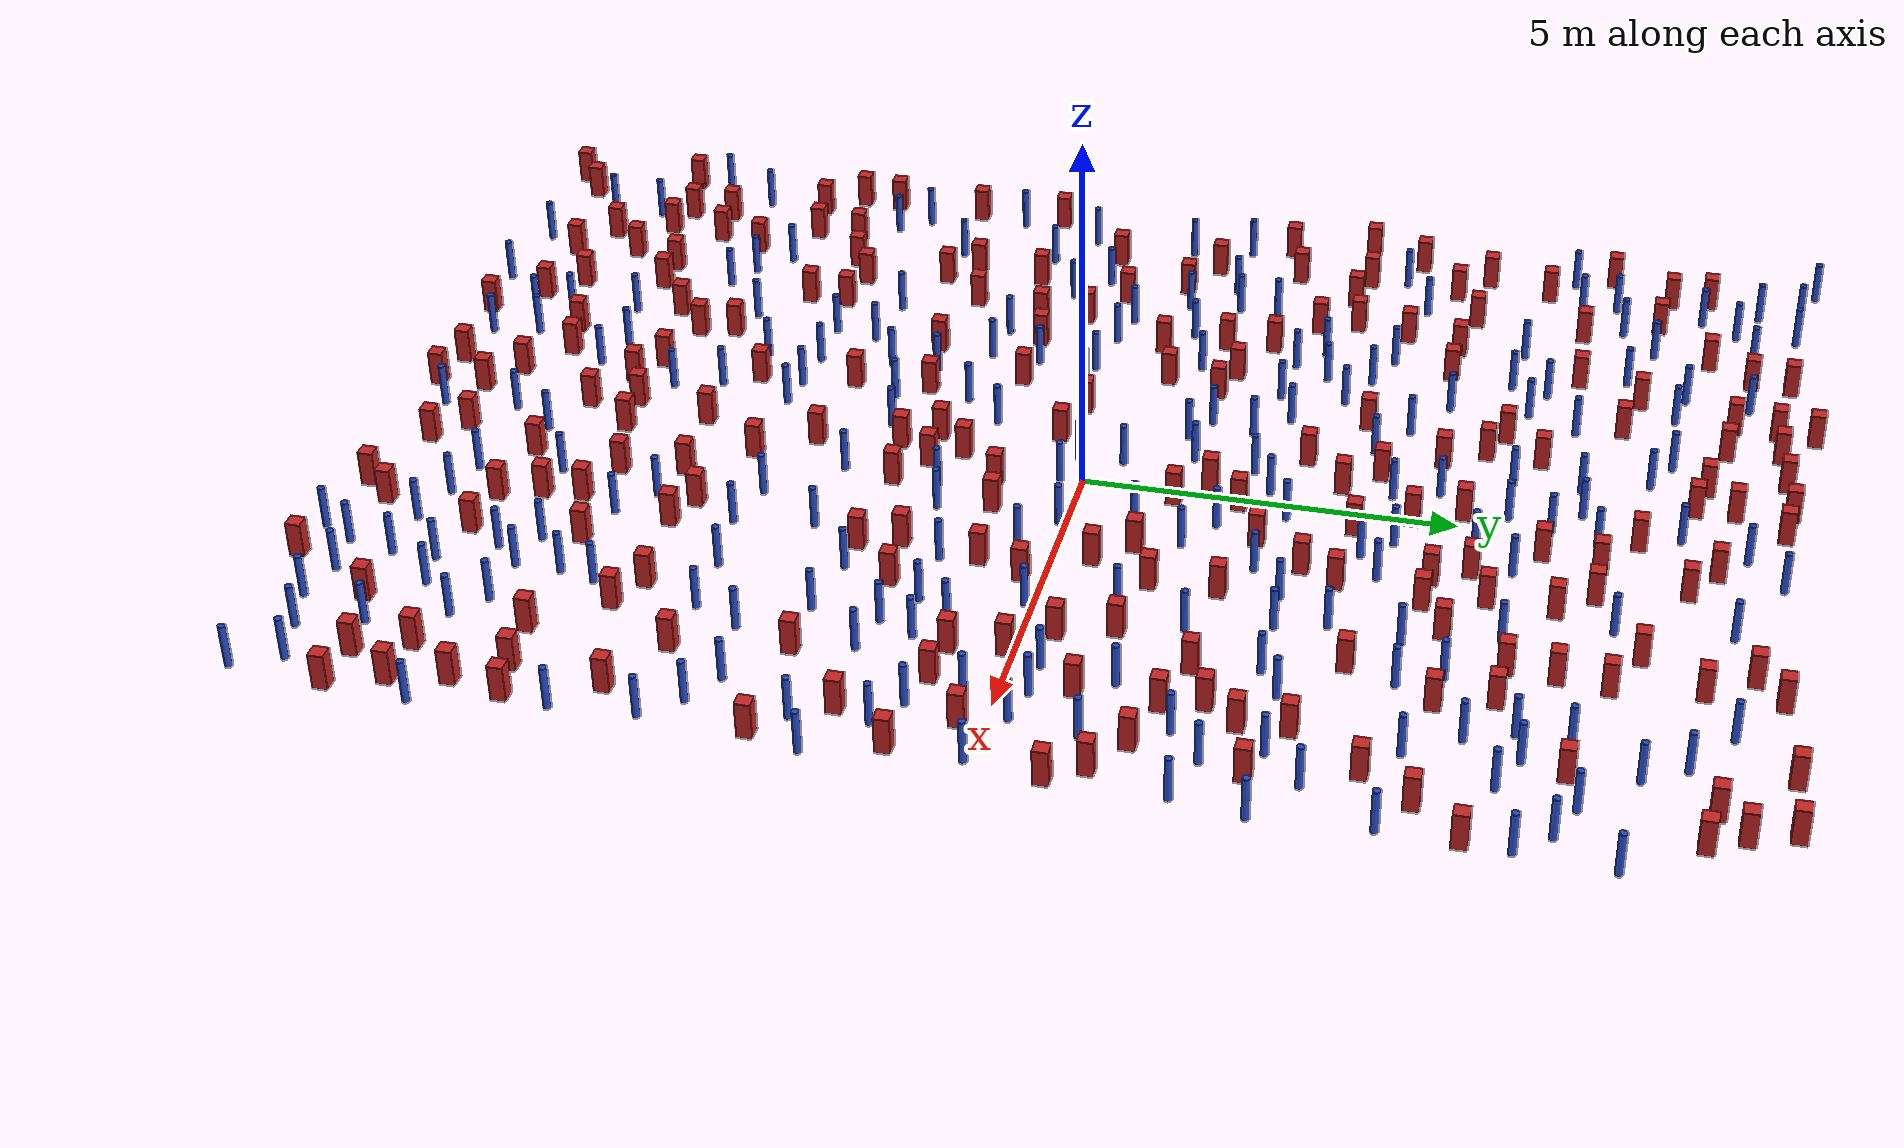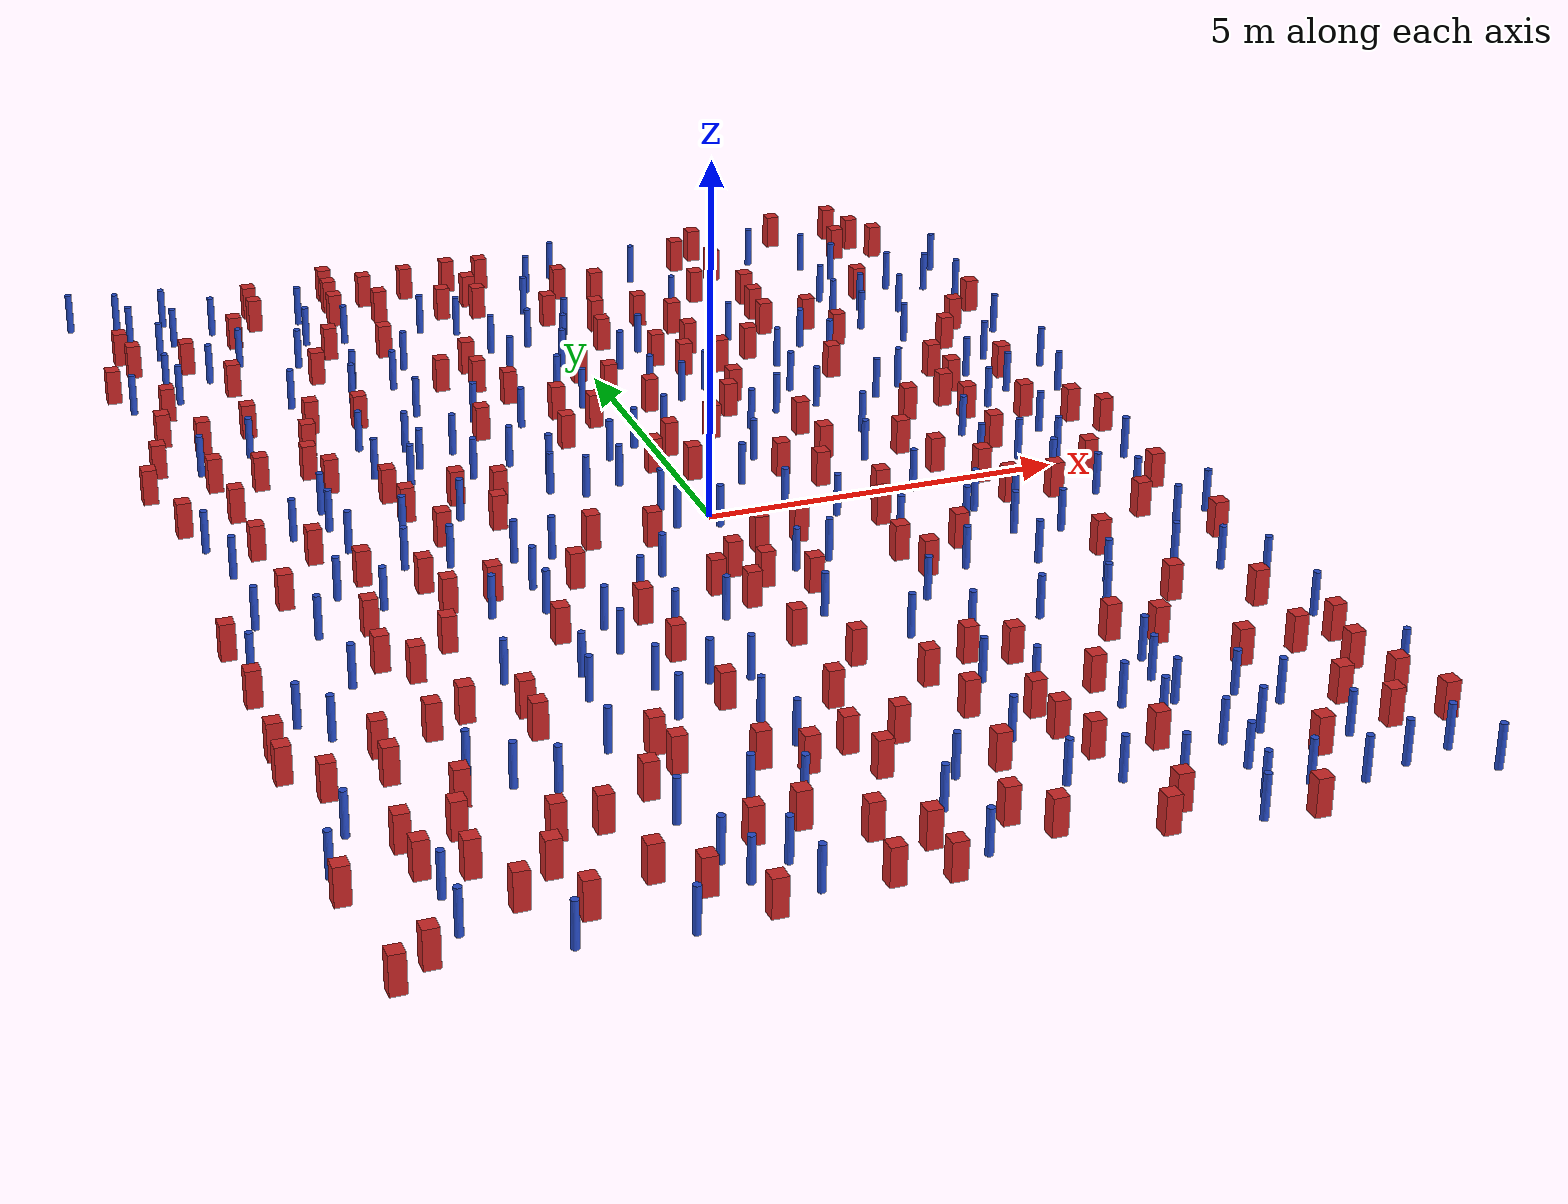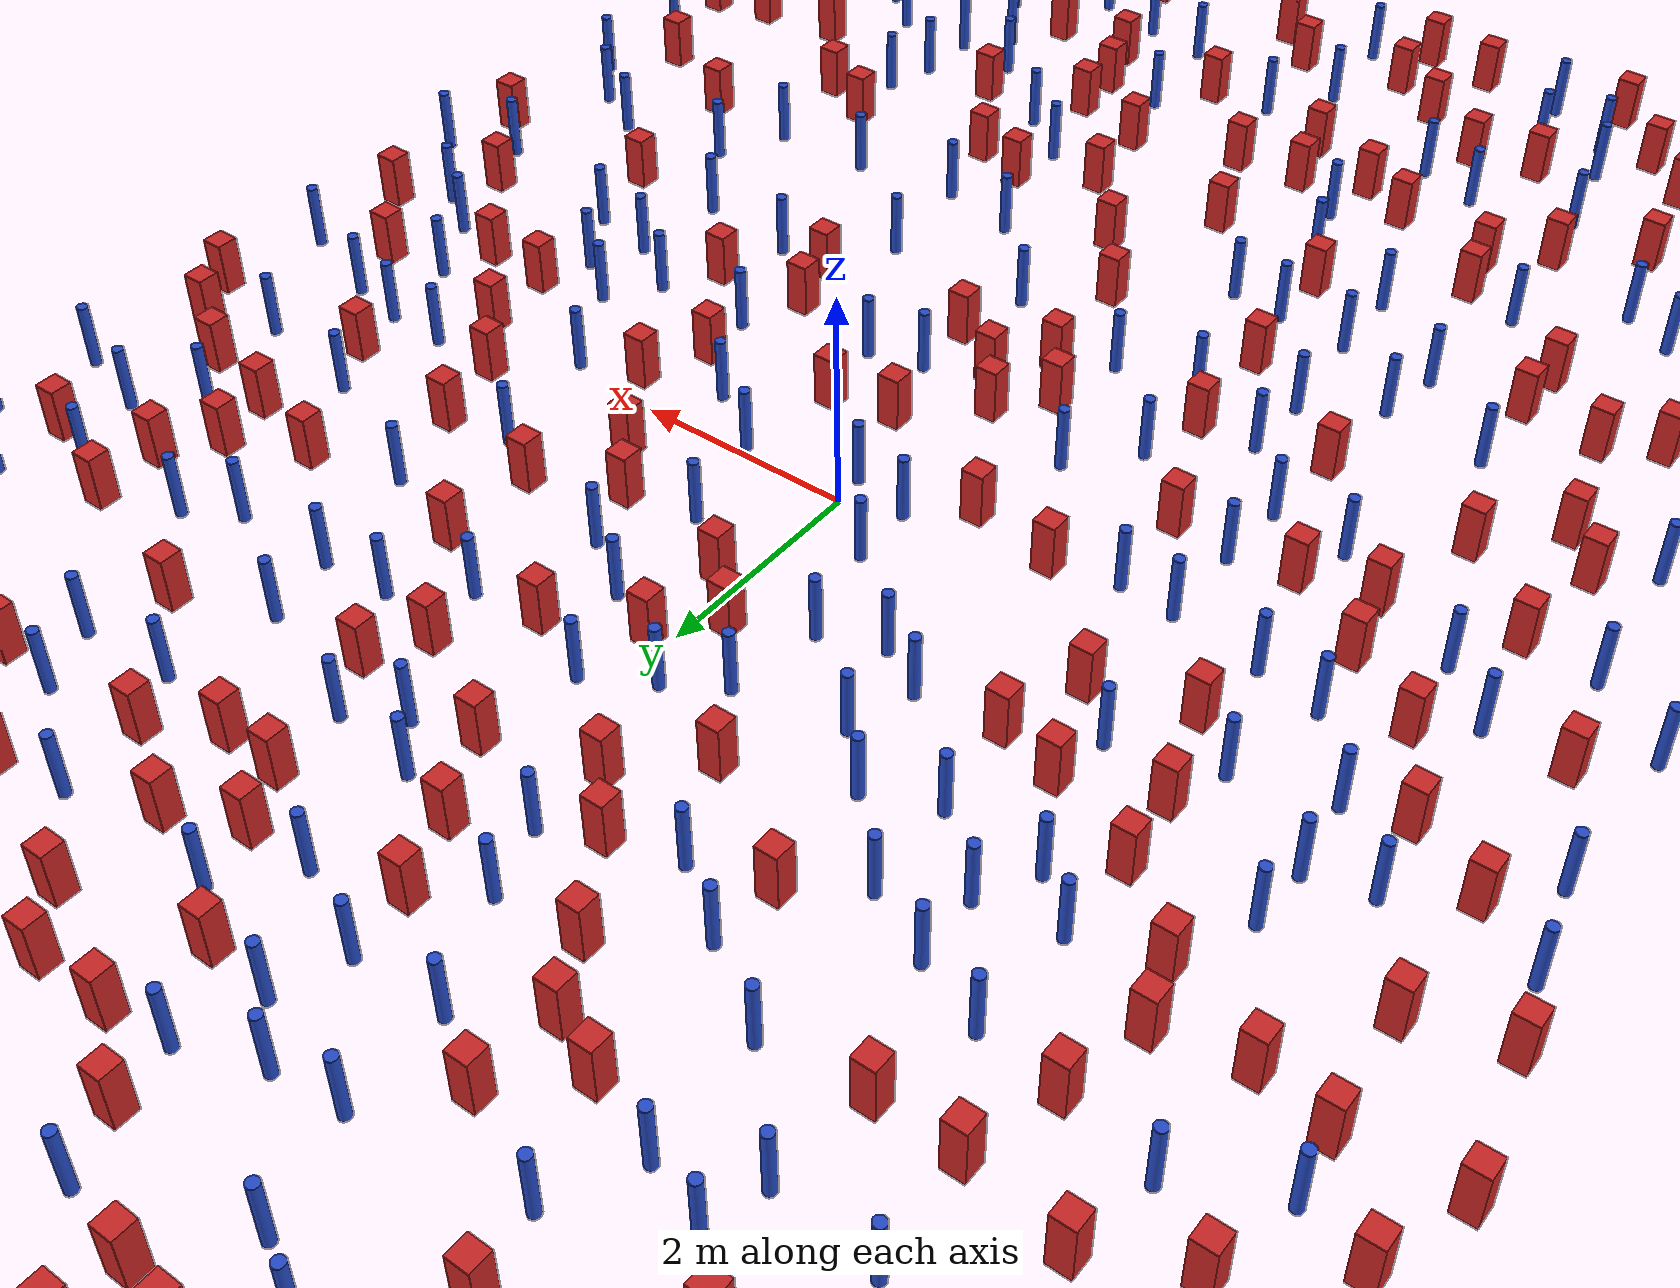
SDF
<sdf version="1.6">
  <model name="dense_82"><model name="pole_obstacle0">
  <static>true</static>
  <pose frame="">-4.2503094902 -0.1919507945 -3.09024884793e-07 -7.19054271912e-07 -2.11315075122e-07 -1.9393550926e-07</pose>
  <link name="link">
  <pose frame="">0 0 0.3 0 -0 0</pose>
    <inertial>
      <mass>1</mass>
      <inertia>
        <ixx>0.145833</ixx>
        <ixy>0</ixy>
        <ixz>0</ixz>
        <iyy>0.145833</iyy>
        <iyz>0</iyz>
        <izz>0.125</izz>
      </inertia>
    </inertial>
    <collision name="collision">
      <geometry>
        <cylinder>
          <radius>0.05</radius>
          <length>.6</length>
        </cylinder>
      </geometry>
      <max_contacts>10</max_contacts>
      <surface>
        <contact>
          <ode/>
        </contact>
        <bounce/>
        <friction>
          <torsional>
            <ode/>
          </torsional>
          <ode/>
        </friction>
      </surface>
    </collision>
    <visual name="visual">
      <geometry>
        <cylinder>
          <radius>0.05</radius>
          <length>.6</length>
        </cylinder>
      </geometry>
      <material>
        <script>
          <name>Gazebo/Blue</name>
          <uri>file://media/materials/scripts/gazebo.material</uri>
        </script>
      </material>
    </visual>
    <self_collide>0</self_collide>
    <kinematic>0</kinematic>
  </link>
</model>
<model name="pole_obstacle1">
  <static>true</static>
  <pose frame="">4.07236167982 -7.60996709356 -3.09024884793e-07 -7.19054271911e-07 -2.1131507516e-07 -1.93935509277e-07</pose>
  <link name="link">
  <pose frame="">0 0 0.3 0 -0 0</pose>
    <inertial>
      <mass>1</mass>
      <inertia>
        <ixx>0.145833</ixx>
        <ixy>0</ixy>
        <ixz>0</ixz>
        <iyy>0.145833</iyy>
        <iyz>0</iyz>
        <izz>0.125</izz>
      </inertia>
    </inertial>
    <collision name="collision">
      <geometry>
        <cylinder>
          <radius>0.05</radius>
          <length>.6</length>
        </cylinder>
      </geometry>
      <max_contacts>10</max_contacts>
      <surface>
        <contact>
          <ode/>
        </contact>
        <bounce/>
        <friction>
          <torsional>
            <ode/>
          </torsional>
          <ode/>
        </friction>
      </surface>
    </collision>
    <visual name="visual">
      <geometry>
        <cylinder>
          <radius>0.05</radius>
          <length>.6</length>
        </cylinder>
      </geometry>
      <material>
        <script>
          <name>Gazebo/Blue</name>
          <uri>file://media/materials/scripts/gazebo.material</uri>
        </script>
      </material>
    </visual>
    <self_collide>0</self_collide>
    <kinematic>0</kinematic>
  </link>
</model>
<model name="square_post_obstacle0">
  <static>true</static>
  <pose frame="">2.59690286933 8.90812959721 -4.36207812815e-07 3.75137919937e-06 9.77721102514e-07 2.47381364184e-05</pose>
  <link name="link">
    <pose frame="">0 0 0.25 0 -0 0</pose>
    <inertial>
      <mass>100</mass>
      <inertia>
        <ixx>0.166667</ixx>
        <ixy>0</ixy>
        <ixz>0</ixz>
        <iyy>0.166667</iyy>
        <iyz>0</iyz>
        <izz>0.166667</izz>
      </inertia>
    </inertial>
    <collision name="collision">
      <geometry>
        <box>
          <size>.2 .2 .5</size>
        </box>
      </geometry>
      <max_contacts>10</max_contacts>
      <surface>
        <contact>
          <ode/>
        </contact>
        <bounce/>
        <friction>
          <torsional>
            <ode/>
          </torsional>
          <ode/>
        </friction>
      </surface>
    </collision>
    <visual name="visual">
      <geometry>
        <box>
          <size>.2 .2 .5</size>
        </box>
      </geometry>
      <material>
        <script>
          <name>Gazebo/Red</name>
          <uri>file://media/materials/scripts/gazebo.material</uri>
        </script>
      </material>
    </visual>
    <self_collide>0</self_collide>
    <kinematic>0</kinematic>
  </link>
</model>
<model name="square_post_obstacle1">
  <static>true</static>
  <pose frame="">5.92085016042 -6.52484385596 -4.36207812815e-07 3.75137919937e-06 9.77721102514e-07 2.47381364184e-05</pose>
  <link name="link">
    <pose frame="">0 0 0.25 0 -0 0</pose>
    <inertial>
      <mass>100</mass>
      <inertia>
        <ixx>0.166667</ixx>
        <ixy>0</ixy>
        <ixz>0</ixz>
        <iyy>0.166667</iyy>
        <iyz>0</iyz>
        <izz>0.166667</izz>
      </inertia>
    </inertial>
    <collision name="collision">
      <geometry>
        <box>
          <size>.2 .2 .5</size>
        </box>
      </geometry>
      <max_contacts>10</max_contacts>
      <surface>
        <contact>
          <ode/>
        </contact>
        <bounce/>
        <friction>
          <torsional>
            <ode/>
          </torsional>
          <ode/>
        </friction>
      </surface>
    </collision>
    <visual name="visual">
      <geometry>
        <box>
          <size>.2 .2 .5</size>
        </box>
      </geometry>
      <material>
        <script>
          <name>Gazebo/Red</name>
          <uri>file://media/materials/scripts/gazebo.material</uri>
        </script>
      </material>
    </visual>
    <self_collide>0</self_collide>
    <kinematic>0</kinematic>
  </link>
</model>
<model name="pole_obstacle2">
  <static>true</static>
  <pose frame="">-1.1636939648 6.49377656993 -3.09024884793e-07 -7.19054271912e-07 -2.11315075134e-07 -1.93935509265e-07</pose>
  <link name="link">
  <pose frame="">0 0 0.3 0 -0 0</pose>
    <inertial>
      <mass>1</mass>
      <inertia>
        <ixx>0.145833</ixx>
        <ixy>0</ixy>
        <ixz>0</ixz>
        <iyy>0.145833</iyy>
        <iyz>0</iyz>
        <izz>0.125</izz>
      </inertia>
    </inertial>
    <collision name="collision">
      <geometry>
        <cylinder>
          <radius>0.05</radius>
          <length>.6</length>
        </cylinder>
      </geometry>
      <max_contacts>10</max_contacts>
      <surface>
        <contact>
          <ode/>
        </contact>
        <bounce/>
        <friction>
          <torsional>
            <ode/>
          </torsional>
          <ode/>
        </friction>
      </surface>
    </collision>
    <visual name="visual">
      <geometry>
        <cylinder>
          <radius>0.05</radius>
          <length>.6</length>
        </cylinder>
      </geometry>
      <material>
        <script>
          <name>Gazebo/Blue</name>
          <uri>file://media/materials/scripts/gazebo.material</uri>
        </script>
      </material>
    </visual>
    <self_collide>0</self_collide>
    <kinematic>0</kinematic>
  </link>
</model>
<model name="pole_obstacle3">
  <static>true</static>
  <pose frame="">-0.812782535777 -2.86212298678 -3.09024884793e-07 -7.19054271912e-07 -2.11315075129e-07 -1.93935509263e-07</pose>
  <link name="link">
  <pose frame="">0 0 0.3 0 -0 0</pose>
    <inertial>
      <mass>1</mass>
      <inertia>
        <ixx>0.145833</ixx>
        <ixy>0</ixy>
        <ixz>0</ixz>
        <iyy>0.145833</iyy>
        <iyz>0</iyz>
        <izz>0.125</izz>
      </inertia>
    </inertial>
    <collision name="collision">
      <geometry>
        <cylinder>
          <radius>0.05</radius>
          <length>.6</length>
        </cylinder>
      </geometry>
      <max_contacts>10</max_contacts>
      <surface>
        <contact>
          <ode/>
        </contact>
        <bounce/>
        <friction>
          <torsional>
            <ode/>
          </torsional>
          <ode/>
        </friction>
      </surface>
    </collision>
    <visual name="visual">
      <geometry>
        <cylinder>
          <radius>0.05</radius>
          <length>.6</length>
        </cylinder>
      </geometry>
      <material>
        <script>
          <name>Gazebo/Blue</name>
          <uri>file://media/materials/scripts/gazebo.material</uri>
        </script>
      </material>
    </visual>
    <self_collide>0</self_collide>
    <kinematic>0</kinematic>
  </link>
</model>
<model name="pole_obstacle4">
  <static>true</static>
  <pose frame="">-3.54911267592 -9.46715608694 -3.09024884793e-07 -7.19054271912e-07 -2.11315075137e-07 -1.93935509267e-07</pose>
  <link name="link">
  <pose frame="">0 0 0.3 0 -0 0</pose>
    <inertial>
      <mass>1</mass>
      <inertia>
        <ixx>0.145833</ixx>
        <ixy>0</ixy>
        <ixz>0</ixz>
        <iyy>0.145833</iyy>
        <iyz>0</iyz>
        <izz>0.125</izz>
      </inertia>
    </inertial>
    <collision name="collision">
      <geometry>
        <cylinder>
          <radius>0.05</radius>
          <length>.6</length>
        </cylinder>
      </geometry>
      <max_contacts>10</max_contacts>
      <surface>
        <contact>
          <ode/>
        </contact>
        <bounce/>
        <friction>
          <torsional>
            <ode/>
          </torsional>
          <ode/>
        </friction>
      </surface>
    </collision>
    <visual name="visual">
      <geometry>
        <cylinder>
          <radius>0.05</radius>
          <length>.6</length>
        </cylinder>
      </geometry>
      <material>
        <script>
          <name>Gazebo/Blue</name>
          <uri>file://media/materials/scripts/gazebo.material</uri>
        </script>
      </material>
    </visual>
    <self_collide>0</self_collide>
    <kinematic>0</kinematic>
  </link>
</model>
<model name="pole_obstacle5">
  <static>true</static>
  <pose frame="">0.301049879293 2.78130600048 -3.09024884793e-07 -7.19054271912e-07 -2.11315075129e-07 -1.93935509263e-07</pose>
  <link name="link">
  <pose frame="">0 0 0.3 0 -0 0</pose>
    <inertial>
      <mass>1</mass>
      <inertia>
        <ixx>0.145833</ixx>
        <ixy>0</ixy>
        <ixz>0</ixz>
        <iyy>0.145833</iyy>
        <iyz>0</iyz>
        <izz>0.125</izz>
      </inertia>
    </inertial>
    <collision name="collision">
      <geometry>
        <cylinder>
          <radius>0.05</radius>
          <length>.6</length>
        </cylinder>
      </geometry>
      <max_contacts>10</max_contacts>
      <surface>
        <contact>
          <ode/>
        </contact>
        <bounce/>
        <friction>
          <torsional>
            <ode/>
          </torsional>
          <ode/>
        </friction>
      </surface>
    </collision>
    <visual name="visual">
      <geometry>
        <cylinder>
          <radius>0.05</radius>
          <length>.6</length>
        </cylinder>
      </geometry>
      <material>
        <script>
          <name>Gazebo/Blue</name>
          <uri>file://media/materials/scripts/gazebo.material</uri>
        </script>
      </material>
    </visual>
    <self_collide>0</self_collide>
    <kinematic>0</kinematic>
  </link>
</model>
<model name="pole_obstacle6">
  <static>true</static>
  <pose frame="">-6.49435936635 -3.81956347133 -3.09024884793e-07 -7.19054271912e-07 -2.11315075144e-07 -1.93935509269e-07</pose>
  <link name="link">
  <pose frame="">0 0 0.3 0 -0 0</pose>
    <inertial>
      <mass>1</mass>
      <inertia>
        <ixx>0.145833</ixx>
        <ixy>0</ixy>
        <ixz>0</ixz>
        <iyy>0.145833</iyy>
        <iyz>0</iyz>
        <izz>0.125</izz>
      </inertia>
    </inertial>
    <collision name="collision">
      <geometry>
        <cylinder>
          <radius>0.05</radius>
          <length>.6</length>
        </cylinder>
      </geometry>
      <max_contacts>10</max_contacts>
      <surface>
        <contact>
          <ode/>
        </contact>
        <bounce/>
        <friction>
          <torsional>
            <ode/>
          </torsional>
          <ode/>
        </friction>
      </surface>
    </collision>
    <visual name="visual">
      <geometry>
        <cylinder>
          <radius>0.05</radius>
          <length>.6</length>
        </cylinder>
      </geometry>
      <material>
        <script>
          <name>Gazebo/Blue</name>
          <uri>file://media/materials/scripts/gazebo.material</uri>
        </script>
      </material>
    </visual>
    <self_collide>0</self_collide>
    <kinematic>0</kinematic>
  </link>
</model>
<model name="square_post_obstacle2">
  <static>true</static>
  <pose frame="">-4.63876810251 -7.87885461352 -4.36207812815e-07 3.75137919937e-06 9.77721102514e-07 2.47381364184e-05</pose>
  <link name="link">
    <pose frame="">0 0 0.25 0 -0 0</pose>
    <inertial>
      <mass>100</mass>
      <inertia>
        <ixx>0.166667</ixx>
        <ixy>0</ixy>
        <ixz>0</ixz>
        <iyy>0.166667</iyy>
        <iyz>0</iyz>
        <izz>0.166667</izz>
      </inertia>
    </inertial>
    <collision name="collision">
      <geometry>
        <box>
          <size>.2 .2 .5</size>
        </box>
      </geometry>
      <max_contacts>10</max_contacts>
      <surface>
        <contact>
          <ode/>
        </contact>
        <bounce/>
        <friction>
          <torsional>
            <ode/>
          </torsional>
          <ode/>
        </friction>
      </surface>
    </collision>
    <visual name="visual">
      <geometry>
        <box>
          <size>.2 .2 .5</size>
        </box>
      </geometry>
      <material>
        <script>
          <name>Gazebo/Red</name>
          <uri>file://media/materials/scripts/gazebo.material</uri>
        </script>
      </material>
    </visual>
    <self_collide>0</self_collide>
    <kinematic>0</kinematic>
  </link>
</model>
<model name="square_post_obstacle3">
  <static>true</static>
  <pose frame="">2.33314151365 -0.291361510585 -4.36207812815e-07 3.75137919937e-06 9.77721102514e-07 2.47381364184e-05</pose>
  <link name="link">
    <pose frame="">0 0 0.25 0 -0 0</pose>
    <inertial>
      <mass>100</mass>
      <inertia>
        <ixx>0.166667</ixx>
        <ixy>0</ixy>
        <ixz>0</ixz>
        <iyy>0.166667</iyy>
        <iyz>0</iyz>
        <izz>0.166667</izz>
      </inertia>
    </inertial>
    <collision name="collision">
      <geometry>
        <box>
          <size>.2 .2 .5</size>
        </box>
      </geometry>
      <max_contacts>10</max_contacts>
      <surface>
        <contact>
          <ode/>
        </contact>
        <bounce/>
        <friction>
          <torsional>
            <ode/>
          </torsional>
          <ode/>
        </friction>
      </surface>
    </collision>
    <visual name="visual">
      <geometry>
        <box>
          <size>.2 .2 .5</size>
        </box>
      </geometry>
      <material>
        <script>
          <name>Gazebo/Red</name>
          <uri>file://media/materials/scripts/gazebo.material</uri>
        </script>
      </material>
    </visual>
    <self_collide>0</self_collide>
    <kinematic>0</kinematic>
  </link>
</model>
<model name="square_post_obstacle4">
  <static>true</static>
  <pose frame="">-0.213089348339 -3.73600585675 -4.36207812815e-07 3.75137919937e-06 9.77721102514e-07 2.47381364184e-05</pose>
  <link name="link">
    <pose frame="">0 0 0.25 0 -0 0</pose>
    <inertial>
      <mass>100</mass>
      <inertia>
        <ixx>0.166667</ixx>
        <ixy>0</ixy>
        <ixz>0</ixz>
        <iyy>0.166667</iyy>
        <iyz>0</iyz>
        <izz>0.166667</izz>
      </inertia>
    </inertial>
    <collision name="collision">
      <geometry>
        <box>
          <size>.2 .2 .5</size>
        </box>
      </geometry>
      <max_contacts>10</max_contacts>
      <surface>
        <contact>
          <ode/>
        </contact>
        <bounce/>
        <friction>
          <torsional>
            <ode/>
          </torsional>
          <ode/>
        </friction>
      </surface>
    </collision>
    <visual name="visual">
      <geometry>
        <box>
          <size>.2 .2 .5</size>
        </box>
      </geometry>
      <material>
        <script>
          <name>Gazebo/Red</name>
          <uri>file://media/materials/scripts/gazebo.material</uri>
        </script>
      </material>
    </visual>
    <self_collide>0</self_collide>
    <kinematic>0</kinematic>
  </link>
</model>
<model name="pole_obstacle7">
  <static>true</static>
  <pose frame="">-1.32874386624 -5.45448428314 -3.09024884793e-07 -7.19054271912e-07 -2.11315075134e-07 -1.93935509265e-07</pose>
  <link name="link">
  <pose frame="">0 0 0.3 0 -0 0</pose>
    <inertial>
      <mass>1</mass>
      <inertia>
        <ixx>0.145833</ixx>
        <ixy>0</ixy>
        <ixz>0</ixz>
        <iyy>0.145833</iyy>
        <iyz>0</iyz>
        <izz>0.125</izz>
      </inertia>
    </inertial>
    <collision name="collision">
      <geometry>
        <cylinder>
          <radius>0.05</radius>
          <length>.6</length>
        </cylinder>
      </geometry>
      <max_contacts>10</max_contacts>
      <surface>
        <contact>
          <ode/>
        </contact>
        <bounce/>
        <friction>
          <torsional>
            <ode/>
          </torsional>
          <ode/>
        </friction>
      </surface>
    </collision>
    <visual name="visual">
      <geometry>
        <cylinder>
          <radius>0.05</radius>
          <length>.6</length>
        </cylinder>
      </geometry>
      <material>
        <script>
          <name>Gazebo/Blue</name>
          <uri>file://media/materials/scripts/gazebo.material</uri>
        </script>
      </material>
    </visual>
    <self_collide>0</self_collide>
    <kinematic>0</kinematic>
  </link>
</model>
<model name="pole_obstacle8">
  <static>true</static>
  <pose frame="">-6.90155995579 -7.15182244249 -3.09024884793e-07 -7.19054271911e-07 -2.1131507516e-07 -1.93935509277e-07</pose>
  <link name="link">
  <pose frame="">0 0 0.3 0 -0 0</pose>
    <inertial>
      <mass>1</mass>
      <inertia>
        <ixx>0.145833</ixx>
        <ixy>0</ixy>
        <ixz>0</ixz>
        <iyy>0.145833</iyy>
        <iyz>0</iyz>
        <izz>0.125</izz>
      </inertia>
    </inertial>
    <collision name="collision">
      <geometry>
        <cylinder>
          <radius>0.05</radius>
          <length>.6</length>
        </cylinder>
      </geometry>
      <max_contacts>10</max_contacts>
      <surface>
        <contact>
          <ode/>
        </contact>
        <bounce/>
        <friction>
          <torsional>
            <ode/>
          </torsional>
          <ode/>
        </friction>
      </surface>
    </collision>
    <visual name="visual">
      <geometry>
        <cylinder>
          <radius>0.05</radius>
          <length>.6</length>
        </cylinder>
      </geometry>
      <material>
        <script>
          <name>Gazebo/Blue</name>
          <uri>file://media/materials/scripts/gazebo.material</uri>
        </script>
      </material>
    </visual>
    <self_collide>0</self_collide>
    <kinematic>0</kinematic>
  </link>
</model>
<model name="square_post_obstacle5">
  <static>true</static>
  <pose frame="">3.23649416431 1.14456363567 -4.36207812815e-07 3.75137919937e-06 9.77721102514e-07 2.47381364184e-05</pose>
  <link name="link">
    <pose frame="">0 0 0.25 0 -0 0</pose>
    <inertial>
      <mass>100</mass>
      <inertia>
        <ixx>0.166667</ixx>
        <ixy>0</ixy>
        <ixz>0</ixz>
        <iyy>0.166667</iyy>
        <iyz>0</iyz>
        <izz>0.166667</izz>
      </inertia>
    </inertial>
    <collision name="collision">
      <geometry>
        <box>
          <size>.2 .2 .5</size>
        </box>
      </geometry>
      <max_contacts>10</max_contacts>
      <surface>
        <contact>
          <ode/>
        </contact>
        <bounce/>
        <friction>
          <torsional>
            <ode/>
          </torsional>
          <ode/>
        </friction>
      </surface>
    </collision>
    <visual name="visual">
      <geometry>
        <box>
          <size>.2 .2 .5</size>
        </box>
      </geometry>
      <material>
        <script>
          <name>Gazebo/Red</name>
          <uri>file://media/materials/scripts/gazebo.material</uri>
        </script>
      </material>
    </visual>
    <self_collide>0</self_collide>
    <kinematic>0</kinematic>
  </link>
</model>
<model name="square_post_obstacle6">
  <static>true</static>
  <pose frame="">-6.49289543125 7.902991326 -4.36207812815e-07 3.75137919937e-06 9.77721102514e-07 2.47381364184e-05</pose>
  <link name="link">
    <pose frame="">0 0 0.25 0 -0 0</pose>
    <inertial>
      <mass>100</mass>
      <inertia>
        <ixx>0.166667</ixx>
        <ixy>0</ixy>
        <ixz>0</ixz>
        <iyy>0.166667</iyy>
        <iyz>0</iyz>
        <izz>0.166667</izz>
      </inertia>
    </inertial>
    <collision name="collision">
      <geometry>
        <box>
          <size>.2 .2 .5</size>
        </box>
      </geometry>
      <max_contacts>10</max_contacts>
      <surface>
        <contact>
          <ode/>
        </contact>
        <bounce/>
        <friction>
          <torsional>
            <ode/>
          </torsional>
          <ode/>
        </friction>
      </surface>
    </collision>
    <visual name="visual">
      <geometry>
        <box>
          <size>.2 .2 .5</size>
        </box>
      </geometry>
      <material>
        <script>
          <name>Gazebo/Red</name>
          <uri>file://media/materials/scripts/gazebo.material</uri>
        </script>
      </material>
    </visual>
    <self_collide>0</self_collide>
    <kinematic>0</kinematic>
  </link>
</model>
<model name="square_post_obstacle7">
  <static>true</static>
  <pose frame="">-5.10605497438 -1.75977822787 -4.36207812815e-07 3.75137919937e-06 9.77721102514e-07 2.47381364184e-05</pose>
  <link name="link">
    <pose frame="">0 0 0.25 0 -0 0</pose>
    <inertial>
      <mass>100</mass>
      <inertia>
        <ixx>0.166667</ixx>
        <ixy>0</ixy>
        <ixz>0</ixz>
        <iyy>0.166667</iyy>
        <iyz>0</iyz>
        <izz>0.166667</izz>
      </inertia>
    </inertial>
    <collision name="collision">
      <geometry>
        <box>
          <size>.2 .2 .5</size>
        </box>
      </geometry>
      <max_contacts>10</max_contacts>
      <surface>
        <contact>
          <ode/>
        </contact>
        <bounce/>
        <friction>
          <torsional>
            <ode/>
          </torsional>
          <ode/>
        </friction>
      </surface>
    </collision>
    <visual name="visual">
      <geometry>
        <box>
          <size>.2 .2 .5</size>
        </box>
      </geometry>
      <material>
        <script>
          <name>Gazebo/Red</name>
          <uri>file://media/materials/scripts/gazebo.material</uri>
        </script>
      </material>
    </visual>
    <self_collide>0</self_collide>
    <kinematic>0</kinematic>
  </link>
</model>
<model name="pole_obstacle9">
  <static>true</static>
  <pose frame="">-5.62983167318 9.16247445387 -3.09024884793e-07 -7.19054271912e-07 -2.1131507513e-07 -1.93935509261e-07</pose>
  <link name="link">
  <pose frame="">0 0 0.3 0 -0 0</pose>
    <inertial>
      <mass>1</mass>
      <inertia>
        <ixx>0.145833</ixx>
        <ixy>0</ixy>
        <ixz>0</ixz>
        <iyy>0.145833</iyy>
        <iyz>0</iyz>
        <izz>0.125</izz>
      </inertia>
    </inertial>
    <collision name="collision">
      <geometry>
        <cylinder>
          <radius>0.05</radius>
          <length>.6</length>
        </cylinder>
      </geometry>
      <max_contacts>10</max_contacts>
      <surface>
        <contact>
          <ode/>
        </contact>
        <bounce/>
        <friction>
          <torsional>
            <ode/>
          </torsional>
          <ode/>
        </friction>
      </surface>
    </collision>
    <visual name="visual">
      <geometry>
        <cylinder>
          <radius>0.05</radius>
          <length>.6</length>
        </cylinder>
      </geometry>
      <material>
        <script>
          <name>Gazebo/Blue</name>
          <uri>file://media/materials/scripts/gazebo.material</uri>
        </script>
      </material>
    </visual>
    <self_collide>0</self_collide>
    <kinematic>0</kinematic>
  </link>
</model>
<model name="pole_obstacle10">
  <static>true</static>
  <pose frame="">4.79318812608 7.67508169887 -3.09024884793e-07 -7.19054271911e-07 -2.1131507516e-07 -1.93935509277e-07</pose>
  <link name="link">
  <pose frame="">0 0 0.3 0 -0 0</pose>
    <inertial>
      <mass>1</mass>
      <inertia>
        <ixx>0.145833</ixx>
        <ixy>0</ixy>
        <ixz>0</ixz>
        <iyy>0.145833</iyy>
        <iyz>0</iyz>
        <izz>0.125</izz>
      </inertia>
    </inertial>
    <collision name="collision">
      <geometry>
        <cylinder>
          <radius>0.05</radius>
          <length>.6</length>
        </cylinder>
      </geometry>
      <max_contacts>10</max_contacts>
      <surface>
        <contact>
          <ode/>
        </contact>
        <bounce/>
        <friction>
          <torsional>
            <ode/>
          </torsional>
          <ode/>
        </friction>
      </surface>
    </collision>
    <visual name="visual">
      <geometry>
        <cylinder>
          <radius>0.05</radius>
          <length>.6</length>
        </cylinder>
      </geometry>
      <material>
        <script>
          <name>Gazebo/Blue</name>
          <uri>file://media/materials/scripts/gazebo.material</uri>
        </script>
      </material>
    </visual>
    <self_collide>0</self_collide>
    <kinematic>0</kinematic>
  </link>
</model>
<model name="pole_obstacle11">
  <static>true</static>
  <pose frame="">5.72534623806 3.8320057346 -3.09024884793e-07 -7.19054271912e-07 -2.11315075144e-07 -1.93935509269e-07</pose>
  <link name="link">
  <pose frame="">0 0 0.3 0 -0 0</pose>
    <inertial>
      <mass>1</mass>
      <inertia>
        <ixx>0.145833</ixx>
        <ixy>0</ixy>
        <ixz>0</ixz>
        <iyy>0.145833</iyy>
        <iyz>0</iyz>
        <izz>0.125</izz>
      </inertia>
    </inertial>
    <collision name="collision">
      <geometry>
        <cylinder>
          <radius>0.05</radius>
          <length>.6</length>
        </cylinder>
      </geometry>
      <max_contacts>10</max_contacts>
      <surface>
        <contact>
          <ode/>
        </contact>
        <bounce/>
        <friction>
          <torsional>
            <ode/>
          </torsional>
          <ode/>
        </friction>
      </surface>
    </collision>
    <visual name="visual">
      <geometry>
        <cylinder>
          <radius>0.05</radius>
          <length>.6</length>
        </cylinder>
      </geometry>
      <material>
        <script>
          <name>Gazebo/Blue</name>
          <uri>file://media/materials/scripts/gazebo.material</uri>
        </script>
      </material>
    </visual>
    <self_collide>0</self_collide>
    <kinematic>0</kinematic>
  </link>
</model>
<model name="pole_obstacle12">
  <static>true</static>
  <pose frame="">1.75246085546 8.61980835545 -3.09024884793e-07 -7.19054271912e-07 -2.1131507515e-07 -1.93935509273e-07</pose>
  <link name="link">
  <pose frame="">0 0 0.3 0 -0 0</pose>
    <inertial>
      <mass>1</mass>
      <inertia>
        <ixx>0.145833</ixx>
        <ixy>0</ixy>
        <ixz>0</ixz>
        <iyy>0.145833</iyy>
        <iyz>0</iyz>
        <izz>0.125</izz>
      </inertia>
    </inertial>
    <collision name="collision">
      <geometry>
        <cylinder>
          <radius>0.05</radius>
          <length>.6</length>
        </cylinder>
      </geometry>
      <max_contacts>10</max_contacts>
      <surface>
        <contact>
          <ode/>
        </contact>
        <bounce/>
        <friction>
          <torsional>
            <ode/>
          </torsional>
          <ode/>
        </friction>
      </surface>
    </collision>
    <visual name="visual">
      <geometry>
        <cylinder>
          <radius>0.05</radius>
          <length>.6</length>
        </cylinder>
      </geometry>
      <material>
        <script>
          <name>Gazebo/Blue</name>
          <uri>file://media/materials/scripts/gazebo.material</uri>
        </script>
      </material>
    </visual>
    <self_collide>0</self_collide>
    <kinematic>0</kinematic>
  </link>
</model>
<model name="square_post_obstacle8">
  <static>true</static>
  <pose frame="">0.871351405649 -1.02701307779 -4.36207812815e-07 3.75137919937e-06 9.77721102514e-07 2.47381364184e-05</pose>
  <link name="link">
    <pose frame="">0 0 0.25 0 -0 0</pose>
    <inertial>
      <mass>100</mass>
      <inertia>
        <ixx>0.166667</ixx>
        <ixy>0</ixy>
        <ixz>0</ixz>
        <iyy>0.166667</iyy>
        <iyz>0</iyz>
        <izz>0.166667</izz>
      </inertia>
    </inertial>
    <collision name="collision">
      <geometry>
        <box>
          <size>.2 .2 .5</size>
        </box>
      </geometry>
      <max_contacts>10</max_contacts>
      <surface>
        <contact>
          <ode/>
        </contact>
        <bounce/>
        <friction>
          <torsional>
            <ode/>
          </torsional>
          <ode/>
        </friction>
      </surface>
    </collision>
    <visual name="visual">
      <geometry>
        <box>
          <size>.2 .2 .5</size>
        </box>
      </geometry>
      <material>
        <script>
          <name>Gazebo/Red</name>
          <uri>file://media/materials/scripts/gazebo.material</uri>
        </script>
      </material>
    </visual>
    <self_collide>0</self_collide>
    <kinematic>0</kinematic>
  </link>
</model>
<model name="square_post_obstacle9">
  <static>true</static>
  <pose frame="">0.162851967666 2.13159668785 -4.36207812815e-07 3.75137919937e-06 9.77721102514e-07 2.47381364184e-05</pose>
  <link name="link">
    <pose frame="">0 0 0.25 0 -0 0</pose>
    <inertial>
      <mass>100</mass>
      <inertia>
        <ixx>0.166667</ixx>
        <ixy>0</ixy>
        <ixz>0</ixz>
        <iyy>0.166667</iyy>
        <iyz>0</iyz>
        <izz>0.166667</izz>
      </inertia>
    </inertial>
    <collision name="collision">
      <geometry>
        <box>
          <size>.2 .2 .5</size>
        </box>
      </geometry>
      <max_contacts>10</max_contacts>
      <surface>
        <contact>
          <ode/>
        </contact>
        <bounce/>
        <friction>
          <torsional>
            <ode/>
          </torsional>
          <ode/>
        </friction>
      </surface>
    </collision>
    <visual name="visual">
      <geometry>
        <box>
          <size>.2 .2 .5</size>
        </box>
      </geometry>
      <material>
        <script>
          <name>Gazebo/Red</name>
          <uri>file://media/materials/scripts/gazebo.material</uri>
        </script>
      </material>
    </visual>
    <self_collide>0</self_collide>
    <kinematic>0</kinematic>
  </link>
</model>
<model name="pole_obstacle13">
  <static>true</static>
  <pose frame="">0.0314348931454 -0.309550767715 -3.09024884793e-07 -7.19054271912e-07 -2.1131507514e-07 -1.93935509267e-07</pose>
  <link name="link">
  <pose frame="">0 0 0.3 0 -0 0</pose>
    <inertial>
      <mass>1</mass>
      <inertia>
        <ixx>0.145833</ixx>
        <ixy>0</ixy>
        <ixz>0</ixz>
        <iyy>0.145833</iyy>
        <iyz>0</iyz>
        <izz>0.125</izz>
      </inertia>
    </inertial>
    <collision name="collision">
      <geometry>
        <cylinder>
          <radius>0.05</radius>
          <length>.6</length>
        </cylinder>
      </geometry>
      <max_contacts>10</max_contacts>
      <surface>
        <contact>
          <ode/>
        </contact>
        <bounce/>
        <friction>
          <torsional>
            <ode/>
          </torsional>
          <ode/>
        </friction>
      </surface>
    </collision>
    <visual name="visual">
      <geometry>
        <cylinder>
          <radius>0.05</radius>
          <length>.6</length>
        </cylinder>
      </geometry>
      <material>
        <script>
          <name>Gazebo/Blue</name>
          <uri>file://media/materials/scripts/gazebo.material</uri>
        </script>
      </material>
    </visual>
    <self_collide>0</self_collide>
    <kinematic>0</kinematic>
  </link>
</model>
<model name="square_post_obstacle10">
  <static>true</static>
  <pose frame="">5.62573239196 -7.92361459516 -4.36207812815e-07 3.75137919937e-06 9.77721102514e-07 2.47381364184e-05</pose>
  <link name="link">
    <pose frame="">0 0 0.25 0 -0 0</pose>
    <inertial>
      <mass>100</mass>
      <inertia>
        <ixx>0.166667</ixx>
        <ixy>0</ixy>
        <ixz>0</ixz>
        <iyy>0.166667</iyy>
        <iyz>0</iyz>
        <izz>0.166667</izz>
      </inertia>
    </inertial>
    <collision name="collision">
      <geometry>
        <box>
          <size>.2 .2 .5</size>
        </box>
      </geometry>
      <max_contacts>10</max_contacts>
      <surface>
        <contact>
          <ode/>
        </contact>
        <bounce/>
        <friction>
          <torsional>
            <ode/>
          </torsional>
          <ode/>
        </friction>
      </surface>
    </collision>
    <visual name="visual">
      <geometry>
        <box>
          <size>.2 .2 .5</size>
        </box>
      </geometry>
      <material>
        <script>
          <name>Gazebo/Red</name>
          <uri>file://media/materials/scripts/gazebo.material</uri>
        </script>
      </material>
    </visual>
    <self_collide>0</self_collide>
    <kinematic>0</kinematic>
  </link>
</model>
<model name="square_post_obstacle11">
  <static>true</static>
  <pose frame="">0.403565331096 3.68767833755 -4.36207812815e-07 3.75137919937e-06 9.77721102514e-07 2.47381364184e-05</pose>
  <link name="link">
    <pose frame="">0 0 0.25 0 -0 0</pose>
    <inertial>
      <mass>100</mass>
      <inertia>
        <ixx>0.166667</ixx>
        <ixy>0</ixy>
        <ixz>0</ixz>
        <iyy>0.166667</iyy>
        <iyz>0</iyz>
        <izz>0.166667</izz>
      </inertia>
    </inertial>
    <collision name="collision">
      <geometry>
        <box>
          <size>.2 .2 .5</size>
        </box>
      </geometry>
      <max_contacts>10</max_contacts>
      <surface>
        <contact>
          <ode/>
        </contact>
        <bounce/>
        <friction>
          <torsional>
            <ode/>
          </torsional>
          <ode/>
        </friction>
      </surface>
    </collision>
    <visual name="visual">
      <geometry>
        <box>
          <size>.2 .2 .5</size>
        </box>
      </geometry>
      <material>
        <script>
          <name>Gazebo/Red</name>
          <uri>file://media/materials/scripts/gazebo.material</uri>
        </script>
      </material>
    </visual>
    <self_collide>0</self_collide>
    <kinematic>0</kinematic>
  </link>
</model>
<model name="pole_obstacle14">
  <static>true</static>
  <pose frame="">6.26236813812 2.39795763185 -3.09024884793e-07 -7.19054271912e-07 -2.11315075144e-07 -1.93935509269e-07</pose>
  <link name="link">
  <pose frame="">0 0 0.3 0 -0 0</pose>
    <inertial>
      <mass>1</mass>
      <inertia>
        <ixx>0.145833</ixx>
        <ixy>0</ixy>
        <ixz>0</ixz>
        <iyy>0.145833</iyy>
        <iyz>0</iyz>
        <izz>0.125</izz>
      </inertia>
    </inertial>
    <collision name="collision">
      <geometry>
        <cylinder>
          <radius>0.05</radius>
          <length>.6</length>
        </cylinder>
      </geometry>
      <max_contacts>10</max_contacts>
      <surface>
        <contact>
          <ode/>
        </contact>
        <bounce/>
        <friction>
          <torsional>
            <ode/>
          </torsional>
          <ode/>
        </friction>
      </surface>
    </collision>
    <visual name="visual">
      <geometry>
        <cylinder>
          <radius>0.05</radius>
          <length>.6</length>
        </cylinder>
      </geometry>
      <material>
        <script>
          <name>Gazebo/Blue</name>
          <uri>file://media/materials/scripts/gazebo.material</uri>
        </script>
      </material>
    </visual>
    <self_collide>0</self_collide>
    <kinematic>0</kinematic>
  </link>
</model>
<model name="pole_obstacle15">
  <static>true</static>
  <pose frame="">2.59792775279 -2.53692966714 -3.09024884793e-07 -7.19054271912e-07 -2.11315075144e-07 -1.93935509271e-07</pose>
  <link name="link">
  <pose frame="">0 0 0.3 0 -0 0</pose>
    <inertial>
      <mass>1</mass>
      <inertia>
        <ixx>0.145833</ixx>
        <ixy>0</ixy>
        <ixz>0</ixz>
        <iyy>0.145833</iyy>
        <iyz>0</iyz>
        <izz>0.125</izz>
      </inertia>
    </inertial>
    <collision name="collision">
      <geometry>
        <cylinder>
          <radius>0.05</radius>
          <length>.6</length>
        </cylinder>
      </geometry>
      <max_contacts>10</max_contacts>
      <surface>
        <contact>
          <ode/>
        </contact>
        <bounce/>
        <friction>
          <torsional>
            <ode/>
          </torsional>
          <ode/>
        </friction>
      </surface>
    </collision>
    <visual name="visual">
      <geometry>
        <cylinder>
          <radius>0.05</radius>
          <length>.6</length>
        </cylinder>
      </geometry>
      <material>
        <script>
          <name>Gazebo/Blue</name>
          <uri>file://media/materials/scripts/gazebo.material</uri>
        </script>
      </material>
    </visual>
    <self_collide>0</self_collide>
    <kinematic>0</kinematic>
  </link>
</model>
<model name="square_post_obstacle12">
  <static>true</static>
  <pose frame="">-3.40699818923 -1.369637165 -4.36207812815e-07 3.75137919937e-06 9.77721102514e-07 2.47381364184e-05</pose>
  <link name="link">
    <pose frame="">0 0 0.25 0 -0 0</pose>
    <inertial>
      <mass>100</mass>
      <inertia>
        <ixx>0.166667</ixx>
        <ixy>0</ixy>
        <ixz>0</ixz>
        <iyy>0.166667</iyy>
        <iyz>0</iyz>
        <izz>0.166667</izz>
      </inertia>
    </inertial>
    <collision name="collision">
      <geometry>
        <box>
          <size>.2 .2 .5</size>
        </box>
      </geometry>
      <max_contacts>10</max_contacts>
      <surface>
        <contact>
          <ode/>
        </contact>
        <bounce/>
        <friction>
          <torsional>
            <ode/>
          </torsional>
          <ode/>
        </friction>
      </surface>
    </collision>
    <visual name="visual">
      <geometry>
        <box>
          <size>.2 .2 .5</size>
        </box>
      </geometry>
      <material>
        <script>
          <name>Gazebo/Red</name>
          <uri>file://media/materials/scripts/gazebo.material</uri>
        </script>
      </material>
    </visual>
    <self_collide>0</self_collide>
    <kinematic>0</kinematic>
  </link>
</model>
<model name="pole_obstacle16">
  <static>true</static>
  <pose frame="">1.25238944474 -6.84796622527 -3.09024884793e-07 -7.19054271912e-07 -2.11315075134e-07 -1.93935509265e-07</pose>
  <link name="link">
  <pose frame="">0 0 0.3 0 -0 0</pose>
    <inertial>
      <mass>1</mass>
      <inertia>
        <ixx>0.145833</ixx>
        <ixy>0</ixy>
        <ixz>0</ixz>
        <iyy>0.145833</iyy>
        <iyz>0</iyz>
        <izz>0.125</izz>
      </inertia>
    </inertial>
    <collision name="collision">
      <geometry>
        <cylinder>
          <radius>0.05</radius>
          <length>.6</length>
        </cylinder>
      </geometry>
      <max_contacts>10</max_contacts>
      <surface>
        <contact>
          <ode/>
        </contact>
        <bounce/>
        <friction>
          <torsional>
            <ode/>
          </torsional>
          <ode/>
        </friction>
      </surface>
    </collision>
    <visual name="visual">
      <geometry>
        <cylinder>
          <radius>0.05</radius>
          <length>.6</length>
        </cylinder>
      </geometry>
      <material>
        <script>
          <name>Gazebo/Blue</name>
          <uri>file://media/materials/scripts/gazebo.material</uri>
        </script>
      </material>
    </visual>
    <self_collide>0</self_collide>
    <kinematic>0</kinematic>
  </link>
</model>
<model name="pole_obstacle17">
  <static>true</static>
  <pose frame="">-2.11424176353 4.09696493338 -3.09024884793e-07 -7.19054271912e-07 -2.11315075134e-07 -1.93935509266e-07</pose>
  <link name="link">
  <pose frame="">0 0 0.3 0 -0 0</pose>
    <inertial>
      <mass>1</mass>
      <inertia>
        <ixx>0.145833</ixx>
        <ixy>0</ixy>
        <ixz>0</ixz>
        <iyy>0.145833</iyy>
        <iyz>0</iyz>
        <izz>0.125</izz>
      </inertia>
    </inertial>
    <collision name="collision">
      <geometry>
        <cylinder>
          <radius>0.05</radius>
          <length>.6</length>
        </cylinder>
      </geometry>
      <max_contacts>10</max_contacts>
      <surface>
        <contact>
          <ode/>
        </contact>
        <bounce/>
        <friction>
          <torsional>
            <ode/>
          </torsional>
          <ode/>
        </friction>
      </surface>
    </collision>
    <visual name="visual">
      <geometry>
        <cylinder>
          <radius>0.05</radius>
          <length>.6</length>
        </cylinder>
      </geometry>
      <material>
        <script>
          <name>Gazebo/Blue</name>
          <uri>file://media/materials/scripts/gazebo.material</uri>
        </script>
      </material>
    </visual>
    <self_collide>0</self_collide>
    <kinematic>0</kinematic>
  </link>
</model>
<model name="square_post_obstacle13">
  <static>true</static>
  <pose frame="">-1.69398379049 -6.42221799246 -4.36207812815e-07 3.75137919937e-06 9.77721102514e-07 2.47381364184e-05</pose>
  <link name="link">
    <pose frame="">0 0 0.25 0 -0 0</pose>
    <inertial>
      <mass>100</mass>
      <inertia>
        <ixx>0.166667</ixx>
        <ixy>0</ixy>
        <ixz>0</ixz>
        <iyy>0.166667</iyy>
        <iyz>0</iyz>
        <izz>0.166667</izz>
      </inertia>
    </inertial>
    <collision name="collision">
      <geometry>
        <box>
          <size>.2 .2 .5</size>
        </box>
      </geometry>
      <max_contacts>10</max_contacts>
      <surface>
        <contact>
          <ode/>
        </contact>
        <bounce/>
        <friction>
          <torsional>
            <ode/>
          </torsional>
          <ode/>
        </friction>
      </surface>
    </collision>
    <visual name="visual">
      <geometry>
        <box>
          <size>.2 .2 .5</size>
        </box>
      </geometry>
      <material>
        <script>
          <name>Gazebo/Red</name>
          <uri>file://media/materials/scripts/gazebo.material</uri>
        </script>
      </material>
    </visual>
    <self_collide>0</self_collide>
    <kinematic>0</kinematic>
  </link>
</model>
<model name="pole_obstacle18">
  <static>true</static>
  <pose frame="">-2.83512441584 4.55504010034 -3.09024884793e-07 -7.19054271912e-07 -2.11315075134e-07 -1.93935509266e-07</pose>
  <link name="link">
  <pose frame="">0 0 0.3 0 -0 0</pose>
    <inertial>
      <mass>1</mass>
      <inertia>
        <ixx>0.145833</ixx>
        <ixy>0</ixy>
        <ixz>0</ixz>
        <iyy>0.145833</iyy>
        <iyz>0</iyz>
        <izz>0.125</izz>
      </inertia>
    </inertial>
    <collision name="collision">
      <geometry>
        <cylinder>
          <radius>0.05</radius>
          <length>.6</length>
        </cylinder>
      </geometry>
      <max_contacts>10</max_contacts>
      <surface>
        <contact>
          <ode/>
        </contact>
        <bounce/>
        <friction>
          <torsional>
            <ode/>
          </torsional>
          <ode/>
        </friction>
      </surface>
    </collision>
    <visual name="visual">
      <geometry>
        <cylinder>
          <radius>0.05</radius>
          <length>.6</length>
        </cylinder>
      </geometry>
      <material>
        <script>
          <name>Gazebo/Blue</name>
          <uri>file://media/materials/scripts/gazebo.material</uri>
        </script>
      </material>
    </visual>
    <self_collide>0</self_collide>
    <kinematic>0</kinematic>
  </link>
</model>
<model name="square_post_obstacle14">
  <static>true</static>
  <pose frame="">4.79167784545 2.927379257 -4.36207812815e-07 3.75137919937e-06 9.77721102514e-07 2.47381364184e-05</pose>
  <link name="link">
    <pose frame="">0 0 0.25 0 -0 0</pose>
    <inertial>
      <mass>100</mass>
      <inertia>
        <ixx>0.166667</ixx>
        <ixy>0</ixy>
        <ixz>0</ixz>
        <iyy>0.166667</iyy>
        <iyz>0</iyz>
        <izz>0.166667</izz>
      </inertia>
    </inertial>
    <collision name="collision">
      <geometry>
        <box>
          <size>.2 .2 .5</size>
        </box>
      </geometry>
      <max_contacts>10</max_contacts>
      <surface>
        <contact>
          <ode/>
        </contact>
        <bounce/>
        <friction>
          <torsional>
            <ode/>
          </torsional>
          <ode/>
        </friction>
      </surface>
    </collision>
    <visual name="visual">
      <geometry>
        <box>
          <size>.2 .2 .5</size>
        </box>
      </geometry>
      <material>
        <script>
          <name>Gazebo/Red</name>
          <uri>file://media/materials/scripts/gazebo.material</uri>
        </script>
      </material>
    </visual>
    <self_collide>0</self_collide>
    <kinematic>0</kinematic>
  </link>
</model>
<model name="pole_obstacle19">
  <static>true</static>
  <pose frame="">-1.53740964032 -3.01281853686 -3.09024884793e-07 -7.19054271912e-07 -2.11315075132e-07 -1.93935509263e-07</pose>
  <link name="link">
  <pose frame="">0 0 0.3 0 -0 0</pose>
    <inertial>
      <mass>1</mass>
      <inertia>
        <ixx>0.145833</ixx>
        <ixy>0</ixy>
        <ixz>0</ixz>
        <iyy>0.145833</iyy>
        <iyz>0</iyz>
        <izz>0.125</izz>
      </inertia>
    </inertial>
    <collision name="collision">
      <geometry>
        <cylinder>
          <radius>0.05</radius>
          <length>.6</length>
        </cylinder>
      </geometry>
      <max_contacts>10</max_contacts>
      <surface>
        <contact>
          <ode/>
        </contact>
        <bounce/>
        <friction>
          <torsional>
            <ode/>
          </torsional>
          <ode/>
        </friction>
      </surface>
    </collision>
    <visual name="visual">
      <geometry>
        <cylinder>
          <radius>0.05</radius>
          <length>.6</length>
        </cylinder>
      </geometry>
      <material>
        <script>
          <name>Gazebo/Blue</name>
          <uri>file://media/materials/scripts/gazebo.material</uri>
        </script>
      </material>
    </visual>
    <self_collide>0</self_collide>
    <kinematic>0</kinematic>
  </link>
</model>
<model name="square_post_obstacle15">
  <static>true</static>
  <pose frame="">-3.0672144097 8.98723721834 -4.36207812815e-07 3.75137919937e-06 9.77721102514e-07 2.47381364184e-05</pose>
  <link name="link">
    <pose frame="">0 0 0.25 0 -0 0</pose>
    <inertial>
      <mass>100</mass>
      <inertia>
        <ixx>0.166667</ixx>
        <ixy>0</ixy>
        <ixz>0</ixz>
        <iyy>0.166667</iyy>
        <iyz>0</iyz>
        <izz>0.166667</izz>
      </inertia>
    </inertial>
    <collision name="collision">
      <geometry>
        <box>
          <size>.2 .2 .5</size>
        </box>
      </geometry>
      <max_contacts>10</max_contacts>
      <surface>
        <contact>
          <ode/>
        </contact>
        <bounce/>
        <friction>
          <torsional>
            <ode/>
          </torsional>
          <ode/>
        </friction>
      </surface>
    </collision>
    <visual name="visual">
      <geometry>
        <box>
          <size>.2 .2 .5</size>
        </box>
      </geometry>
      <material>
        <script>
          <name>Gazebo/Red</name>
          <uri>file://media/materials/scripts/gazebo.material</uri>
        </script>
      </material>
    </visual>
    <self_collide>0</self_collide>
    <kinematic>0</kinematic>
  </link>
</model>
<model name="square_post_obstacle16">
  <static>true</static>
  <pose frame="">-0.230969809656 1.67679450493 -4.36207812815e-07 3.75137919937e-06 9.77721102514e-07 2.47381364184e-05</pose>
  <link name="link">
    <pose frame="">0 0 0.25 0 -0 0</pose>
    <inertial>
      <mass>100</mass>
      <inertia>
        <ixx>0.166667</ixx>
        <ixy>0</ixy>
        <ixz>0</ixz>
        <iyy>0.166667</iyy>
        <iyz>0</iyz>
        <izz>0.166667</izz>
      </inertia>
    </inertial>
    <collision name="collision">
      <geometry>
        <box>
          <size>.2 .2 .5</size>
        </box>
      </geometry>
      <max_contacts>10</max_contacts>
      <surface>
        <contact>
          <ode/>
        </contact>
        <bounce/>
        <friction>
          <torsional>
            <ode/>
          </torsional>
          <ode/>
        </friction>
      </surface>
    </collision>
    <visual name="visual">
      <geometry>
        <box>
          <size>.2 .2 .5</size>
        </box>
      </geometry>
      <material>
        <script>
          <name>Gazebo/Red</name>
          <uri>file://media/materials/scripts/gazebo.material</uri>
        </script>
      </material>
    </visual>
    <self_collide>0</self_collide>
    <kinematic>0</kinematic>
  </link>
</model>
<model name="square_post_obstacle17">
  <static>true</static>
  <pose frame="">4.75082354821 3.5558905162 -4.36207812815e-07 3.75137919937e-06 9.77721102514e-07 2.47381364184e-05</pose>
  <link name="link">
    <pose frame="">0 0 0.25 0 -0 0</pose>
    <inertial>
      <mass>100</mass>
      <inertia>
        <ixx>0.166667</ixx>
        <ixy>0</ixy>
        <ixz>0</ixz>
        <iyy>0.166667</iyy>
        <iyz>0</iyz>
        <izz>0.166667</izz>
      </inertia>
    </inertial>
    <collision name="collision">
      <geometry>
        <box>
          <size>.2 .2 .5</size>
        </box>
      </geometry>
      <max_contacts>10</max_contacts>
      <surface>
        <contact>
          <ode/>
        </contact>
        <bounce/>
        <friction>
          <torsional>
            <ode/>
          </torsional>
          <ode/>
        </friction>
      </surface>
    </collision>
    <visual name="visual">
      <geometry>
        <box>
          <size>.2 .2 .5</size>
        </box>
      </geometry>
      <material>
        <script>
          <name>Gazebo/Red</name>
          <uri>file://media/materials/scripts/gazebo.material</uri>
        </script>
      </material>
    </visual>
    <self_collide>0</self_collide>
    <kinematic>0</kinematic>
  </link>
</model>
<model name="pole_obstacle20">
  <static>true</static>
  <pose frame="">1.17382200154 -4.06774847225 -3.09024884793e-07 -7.19054271912e-07 -2.11315075134e-07 -1.93935509265e-07</pose>
  <link name="link">
  <pose frame="">0 0 0.3 0 -0 0</pose>
    <inertial>
      <mass>1</mass>
      <inertia>
        <ixx>0.145833</ixx>
        <ixy>0</ixy>
        <ixz>0</ixz>
        <iyy>0.145833</iyy>
        <iyz>0</iyz>
        <izz>0.125</izz>
      </inertia>
    </inertial>
    <collision name="collision">
      <geometry>
        <cylinder>
          <radius>0.05</radius>
          <length>.6</length>
        </cylinder>
      </geometry>
      <max_contacts>10</max_contacts>
      <surface>
        <contact>
          <ode/>
        </contact>
        <bounce/>
        <friction>
          <torsional>
            <ode/>
          </torsional>
          <ode/>
        </friction>
      </surface>
    </collision>
    <visual name="visual">
      <geometry>
        <cylinder>
          <radius>0.05</radius>
          <length>.6</length>
        </cylinder>
      </geometry>
      <material>
        <script>
          <name>Gazebo/Blue</name>
          <uri>file://media/materials/scripts/gazebo.material</uri>
        </script>
      </material>
    </visual>
    <self_collide>0</self_collide>
    <kinematic>0</kinematic>
  </link>
</model>
<model name="pole_obstacle21">
  <static>true</static>
  <pose frame="">-2.67258424488 -8.73272913505 -3.09024884848e-07 -7.19054271902e-07 -2.11315075199e-07 -1.93935509286e-07</pose>
  <link name="link">
  <pose frame="">0 0 0.3 0 -0 0</pose>
    <inertial>
      <mass>1</mass>
      <inertia>
        <ixx>0.145833</ixx>
        <ixy>0</ixy>
        <ixz>0</ixz>
        <iyy>0.145833</iyy>
        <iyz>0</iyz>
        <izz>0.125</izz>
      </inertia>
    </inertial>
    <collision name="collision">
      <geometry>
        <cylinder>
          <radius>0.05</radius>
          <length>.6</length>
        </cylinder>
      </geometry>
      <max_contacts>10</max_contacts>
      <surface>
        <contact>
          <ode/>
        </contact>
        <bounce/>
        <friction>
          <torsional>
            <ode/>
          </torsional>
          <ode/>
        </friction>
      </surface>
    </collision>
    <visual name="visual">
      <geometry>
        <cylinder>
          <radius>0.05</radius>
          <length>.6</length>
        </cylinder>
      </geometry>
      <material>
        <script>
          <name>Gazebo/Blue</name>
          <uri>file://media/materials/scripts/gazebo.material</uri>
        </script>
      </material>
    </visual>
    <self_collide>0</self_collide>
    <kinematic>0</kinematic>
  </link>
</model>
<model name="pole_obstacle22">
  <static>true</static>
  <pose frame="">-4.9305122079 -5.54442485208 -3.09024884793e-07 -7.19054271911e-07 -2.1131507516e-07 -1.93935509277e-07</pose>
  <link name="link">
  <pose frame="">0 0 0.3 0 -0 0</pose>
    <inertial>
      <mass>1</mass>
      <inertia>
        <ixx>0.145833</ixx>
        <ixy>0</ixy>
        <ixz>0</ixz>
        <iyy>0.145833</iyy>
        <iyz>0</iyz>
        <izz>0.125</izz>
      </inertia>
    </inertial>
    <collision name="collision">
      <geometry>
        <cylinder>
          <radius>0.05</radius>
          <length>.6</length>
        </cylinder>
      </geometry>
      <max_contacts>10</max_contacts>
      <surface>
        <contact>
          <ode/>
        </contact>
        <bounce/>
        <friction>
          <torsional>
            <ode/>
          </torsional>
          <ode/>
        </friction>
      </surface>
    </collision>
    <visual name="visual">
      <geometry>
        <cylinder>
          <radius>0.05</radius>
          <length>.6</length>
        </cylinder>
      </geometry>
      <material>
        <script>
          <name>Gazebo/Blue</name>
          <uri>file://media/materials/scripts/gazebo.material</uri>
        </script>
      </material>
    </visual>
    <self_collide>0</self_collide>
    <kinematic>0</kinematic>
  </link>
</model>
<model name="pole_obstacle23">
  <static>true</static>
  <pose frame="">1.93177337349 7.15243569661 -3.09024884793e-07 -7.19054271912e-07 -2.11315075134e-07 -1.93935509265e-07</pose>
  <link name="link">
  <pose frame="">0 0 0.3 0 -0 0</pose>
    <inertial>
      <mass>1</mass>
      <inertia>
        <ixx>0.145833</ixx>
        <ixy>0</ixy>
        <ixz>0</ixz>
        <iyy>0.145833</iyy>
        <iyz>0</iyz>
        <izz>0.125</izz>
      </inertia>
    </inertial>
    <collision name="collision">
      <geometry>
        <cylinder>
          <radius>0.05</radius>
          <length>.6</length>
        </cylinder>
      </geometry>
      <max_contacts>10</max_contacts>
      <surface>
        <contact>
          <ode/>
        </contact>
        <bounce/>
        <friction>
          <torsional>
            <ode/>
          </torsional>
          <ode/>
        </friction>
      </surface>
    </collision>
    <visual name="visual">
      <geometry>
        <cylinder>
          <radius>0.05</radius>
          <length>.6</length>
        </cylinder>
      </geometry>
      <material>
        <script>
          <name>Gazebo/Blue</name>
          <uri>file://media/materials/scripts/gazebo.material</uri>
        </script>
      </material>
    </visual>
    <self_collide>0</self_collide>
    <kinematic>0</kinematic>
  </link>
</model>
<model name="square_post_obstacle18">
  <static>true</static>
  <pose frame="">0.465041118365 6.12694422763 -4.36207812815e-07 3.75137919937e-06 9.77721102514e-07 2.47381364184e-05</pose>
  <link name="link">
    <pose frame="">0 0 0.25 0 -0 0</pose>
    <inertial>
      <mass>100</mass>
      <inertia>
        <ixx>0.166667</ixx>
        <ixy>0</ixy>
        <ixz>0</ixz>
        <iyy>0.166667</iyy>
        <iyz>0</iyz>
        <izz>0.166667</izz>
      </inertia>
    </inertial>
    <collision name="collision">
      <geometry>
        <box>
          <size>.2 .2 .5</size>
        </box>
      </geometry>
      <max_contacts>10</max_contacts>
      <surface>
        <contact>
          <ode/>
        </contact>
        <bounce/>
        <friction>
          <torsional>
            <ode/>
          </torsional>
          <ode/>
        </friction>
      </surface>
    </collision>
    <visual name="visual">
      <geometry>
        <box>
          <size>.2 .2 .5</size>
        </box>
      </geometry>
      <material>
        <script>
          <name>Gazebo/Red</name>
          <uri>file://media/materials/scripts/gazebo.material</uri>
        </script>
      </material>
    </visual>
    <self_collide>0</self_collide>
    <kinematic>0</kinematic>
  </link>
</model>
<model name="pole_obstacle24">
  <static>true</static>
  <pose frame="">2.56532698916 3.67538079114 -3.09024884793e-07 -7.19054271912e-07 -2.11315075144e-07 -1.93935509271e-07</pose>
  <link name="link">
  <pose frame="">0 0 0.3 0 -0 0</pose>
    <inertial>
      <mass>1</mass>
      <inertia>
        <ixx>0.145833</ixx>
        <ixy>0</ixy>
        <ixz>0</ixz>
        <iyy>0.145833</iyy>
        <iyz>0</iyz>
        <izz>0.125</izz>
      </inertia>
    </inertial>
    <collision name="collision">
      <geometry>
        <cylinder>
          <radius>0.05</radius>
          <length>.6</length>
        </cylinder>
      </geometry>
      <max_contacts>10</max_contacts>
      <surface>
        <contact>
          <ode/>
        </contact>
        <bounce/>
        <friction>
          <torsional>
            <ode/>
          </torsional>
          <ode/>
        </friction>
      </surface>
    </collision>
    <visual name="visual">
      <geometry>
        <cylinder>
          <radius>0.05</radius>
          <length>.6</length>
        </cylinder>
      </geometry>
      <material>
        <script>
          <name>Gazebo/Blue</name>
          <uri>file://media/materials/scripts/gazebo.material</uri>
        </script>
      </material>
    </visual>
    <self_collide>0</self_collide>
    <kinematic>0</kinematic>
  </link>
</model>
<model name="pole_obstacle25">
  <static>true</static>
  <pose frame="">-2.89989605086 5.62652269784 -3.09024884793e-07 -7.19054271912e-07 -2.11315075134e-07 -1.93935509266e-07</pose>
  <link name="link">
  <pose frame="">0 0 0.3 0 -0 0</pose>
    <inertial>
      <mass>1</mass>
      <inertia>
        <ixx>0.145833</ixx>
        <ixy>0</ixy>
        <ixz>0</ixz>
        <iyy>0.145833</iyy>
        <iyz>0</iyz>
        <izz>0.125</izz>
      </inertia>
    </inertial>
    <collision name="collision">
      <geometry>
        <cylinder>
          <radius>0.05</radius>
          <length>.6</length>
        </cylinder>
      </geometry>
      <max_contacts>10</max_contacts>
      <surface>
        <contact>
          <ode/>
        </contact>
        <bounce/>
        <friction>
          <torsional>
            <ode/>
          </torsional>
          <ode/>
        </friction>
      </surface>
    </collision>
    <visual name="visual">
      <geometry>
        <cylinder>
          <radius>0.05</radius>
          <length>.6</length>
        </cylinder>
      </geometry>
      <material>
        <script>
          <name>Gazebo/Blue</name>
          <uri>file://media/materials/scripts/gazebo.material</uri>
        </script>
      </material>
    </visual>
    <self_collide>0</self_collide>
    <kinematic>0</kinematic>
  </link>
</model>
<model name="pole_obstacle26">
  <static>true</static>
  <pose frame="">1.41979957354 -7.96618892146 -3.09024884793e-07 -7.19054271912e-07 -2.11315075145e-07 -1.9393550927e-07</pose>
  <link name="link">
  <pose frame="">0 0 0.3 0 -0 0</pose>
    <inertial>
      <mass>1</mass>
      <inertia>
        <ixx>0.145833</ixx>
        <ixy>0</ixy>
        <ixz>0</ixz>
        <iyy>0.145833</iyy>
        <iyz>0</iyz>
        <izz>0.125</izz>
      </inertia>
    </inertial>
    <collision name="collision">
      <geometry>
        <cylinder>
          <radius>0.05</radius>
          <length>.6</length>
        </cylinder>
      </geometry>
      <max_contacts>10</max_contacts>
      <surface>
        <contact>
          <ode/>
        </contact>
        <bounce/>
        <friction>
          <torsional>
            <ode/>
          </torsional>
          <ode/>
        </friction>
      </surface>
    </collision>
    <visual name="visual">
      <geometry>
        <cylinder>
          <radius>0.05</radius>
          <length>.6</length>
        </cylinder>
      </geometry>
      <material>
        <script>
          <name>Gazebo/Blue</name>
          <uri>file://media/materials/scripts/gazebo.material</uri>
        </script>
      </material>
    </visual>
    <self_collide>0</self_collide>
    <kinematic>0</kinematic>
  </link>
</model>
<model name="pole_obstacle27">
  <static>true</static>
  <pose frame="">0.664548261349 1.922897534 -3.09024884793e-07 -7.19054271912e-07 -2.11315075135e-07 -1.93935509266e-07</pose>
  <link name="link">
  <pose frame="">0 0 0.3 0 -0 0</pose>
    <inertial>
      <mass>1</mass>
      <inertia>
        <ixx>0.145833</ixx>
        <ixy>0</ixy>
        <ixz>0</ixz>
        <iyy>0.145833</iyy>
        <iyz>0</iyz>
        <izz>0.125</izz>
      </inertia>
    </inertial>
    <collision name="collision">
      <geometry>
        <cylinder>
          <radius>0.05</radius>
          <length>.6</length>
        </cylinder>
      </geometry>
      <max_contacts>10</max_contacts>
      <surface>
        <contact>
          <ode/>
        </contact>
        <bounce/>
        <friction>
          <torsional>
            <ode/>
          </torsional>
          <ode/>
        </friction>
      </surface>
    </collision>
    <visual name="visual">
      <geometry>
        <cylinder>
          <radius>0.05</radius>
          <length>.6</length>
        </cylinder>
      </geometry>
      <material>
        <script>
          <name>Gazebo/Blue</name>
          <uri>file://media/materials/scripts/gazebo.material</uri>
        </script>
      </material>
    </visual>
    <self_collide>0</self_collide>
    <kinematic>0</kinematic>
  </link>
</model>
<model name="pole_obstacle28">
  <static>true</static>
  <pose frame="">-0.249616091385 7.8533554535 -3.09024884793e-07 -7.19054271912e-07 -2.11315075131e-07 -1.93935509264e-07</pose>
  <link name="link">
  <pose frame="">0 0 0.3 0 -0 0</pose>
    <inertial>
      <mass>1</mass>
      <inertia>
        <ixx>0.145833</ixx>
        <ixy>0</ixy>
        <ixz>0</ixz>
        <iyy>0.145833</iyy>
        <iyz>0</iyz>
        <izz>0.125</izz>
      </inertia>
    </inertial>
    <collision name="collision">
      <geometry>
        <cylinder>
          <radius>0.05</radius>
          <length>.6</length>
        </cylinder>
      </geometry>
      <max_contacts>10</max_contacts>
      <surface>
        <contact>
          <ode/>
        </contact>
        <bounce/>
        <friction>
          <torsional>
            <ode/>
          </torsional>
          <ode/>
        </friction>
      </surface>
    </collision>
    <visual name="visual">
      <geometry>
        <cylinder>
          <radius>0.05</radius>
          <length>.6</length>
        </cylinder>
      </geometry>
      <material>
        <script>
          <name>Gazebo/Blue</name>
          <uri>file://media/materials/scripts/gazebo.material</uri>
        </script>
      </material>
    </visual>
    <self_collide>0</self_collide>
    <kinematic>0</kinematic>
  </link>
</model>
<model name="square_post_obstacle19">
  <static>true</static>
  <pose frame="">-4.39326293631 4.49769236264 -4.36207812815e-07 3.75137919937e-06 9.77721102514e-07 2.47381364184e-05</pose>
  <link name="link">
    <pose frame="">0 0 0.25 0 -0 0</pose>
    <inertial>
      <mass>100</mass>
      <inertia>
        <ixx>0.166667</ixx>
        <ixy>0</ixy>
        <ixz>0</ixz>
        <iyy>0.166667</iyy>
        <iyz>0</iyz>
        <izz>0.166667</izz>
      </inertia>
    </inertial>
    <collision name="collision">
      <geometry>
        <box>
          <size>.2 .2 .5</size>
        </box>
      </geometry>
      <max_contacts>10</max_contacts>
      <surface>
        <contact>
          <ode/>
        </contact>
        <bounce/>
        <friction>
          <torsional>
            <ode/>
          </torsional>
          <ode/>
        </friction>
      </surface>
    </collision>
    <visual name="visual">
      <geometry>
        <box>
          <size>.2 .2 .5</size>
        </box>
      </geometry>
      <material>
        <script>
          <name>Gazebo/Red</name>
          <uri>file://media/materials/scripts/gazebo.material</uri>
        </script>
      </material>
    </visual>
    <self_collide>0</self_collide>
    <kinematic>0</kinematic>
  </link>
</model>
<model name="square_post_obstacle20">
  <static>true</static>
  <pose frame="">-5.75726109787 -4.74485710924 -4.36207812815e-07 3.75137919937e-06 9.77721102514e-07 2.47381364184e-05</pose>
  <link name="link">
    <pose frame="">0 0 0.25 0 -0 0</pose>
    <inertial>
      <mass>100</mass>
      <inertia>
        <ixx>0.166667</ixx>
        <ixy>0</ixy>
        <ixz>0</ixz>
        <iyy>0.166667</iyy>
        <iyz>0</iyz>
        <izz>0.166667</izz>
      </inertia>
    </inertial>
    <collision name="collision">
      <geometry>
        <box>
          <size>.2 .2 .5</size>
        </box>
      </geometry>
      <max_contacts>10</max_contacts>
      <surface>
        <contact>
          <ode/>
        </contact>
        <bounce/>
        <friction>
          <torsional>
            <ode/>
          </torsional>
          <ode/>
        </friction>
      </surface>
    </collision>
    <visual name="visual">
      <geometry>
        <box>
          <size>.2 .2 .5</size>
        </box>
      </geometry>
      <material>
        <script>
          <name>Gazebo/Red</name>
          <uri>file://media/materials/scripts/gazebo.material</uri>
        </script>
      </material>
    </visual>
    <self_collide>0</self_collide>
    <kinematic>0</kinematic>
  </link>
</model>
<model name="pole_obstacle29">
  <static>true</static>
  <pose frame="">-6.54652882044 -6.38740867804 -3.09024884793e-07 -7.19054271911e-07 -2.1131507516e-07 -1.93935509277e-07</pose>
  <link name="link">
  <pose frame="">0 0 0.3 0 -0 0</pose>
    <inertial>
      <mass>1</mass>
      <inertia>
        <ixx>0.145833</ixx>
        <ixy>0</ixy>
        <ixz>0</ixz>
        <iyy>0.145833</iyy>
        <iyz>0</iyz>
        <izz>0.125</izz>
      </inertia>
    </inertial>
    <collision name="collision">
      <geometry>
        <cylinder>
          <radius>0.05</radius>
          <length>.6</length>
        </cylinder>
      </geometry>
      <max_contacts>10</max_contacts>
      <surface>
        <contact>
          <ode/>
        </contact>
        <bounce/>
        <friction>
          <torsional>
            <ode/>
          </torsional>
          <ode/>
        </friction>
      </surface>
    </collision>
    <visual name="visual">
      <geometry>
        <cylinder>
          <radius>0.05</radius>
          <length>.6</length>
        </cylinder>
      </geometry>
      <material>
        <script>
          <name>Gazebo/Blue</name>
          <uri>file://media/materials/scripts/gazebo.material</uri>
        </script>
      </material>
    </visual>
    <self_collide>0</self_collide>
    <kinematic>0</kinematic>
  </link>
</model>
<model name="square_post_obstacle21">
  <static>true</static>
  <pose frame="">0.453785921424 -8.48152382366 -4.36207812815e-07 3.75137919937e-06 9.77721102514e-07 2.47381364184e-05</pose>
  <link name="link">
    <pose frame="">0 0 0.25 0 -0 0</pose>
    <inertial>
      <mass>100</mass>
      <inertia>
        <ixx>0.166667</ixx>
        <ixy>0</ixy>
        <ixz>0</ixz>
        <iyy>0.166667</iyy>
        <iyz>0</iyz>
        <izz>0.166667</izz>
      </inertia>
    </inertial>
    <collision name="collision">
      <geometry>
        <box>
          <size>.2 .2 .5</size>
        </box>
      </geometry>
      <max_contacts>10</max_contacts>
      <surface>
        <contact>
          <ode/>
        </contact>
        <bounce/>
        <friction>
          <torsional>
            <ode/>
          </torsional>
          <ode/>
        </friction>
      </surface>
    </collision>
    <visual name="visual">
      <geometry>
        <box>
          <size>.2 .2 .5</size>
        </box>
      </geometry>
      <material>
        <script>
          <name>Gazebo/Red</name>
          <uri>file://media/materials/scripts/gazebo.material</uri>
        </script>
      </material>
    </visual>
    <self_collide>0</self_collide>
    <kinematic>0</kinematic>
  </link>
</model>
<model name="pole_obstacle30">
  <static>true</static>
  <pose frame="">3.5400700986 -8.29917284744 -3.09024884848e-07 -7.19054271902e-07 -2.11315075199e-07 -1.93935509286e-07</pose>
  <link name="link">
  <pose frame="">0 0 0.3 0 -0 0</pose>
    <inertial>
      <mass>1</mass>
      <inertia>
        <ixx>0.145833</ixx>
        <ixy>0</ixy>
        <ixz>0</ixz>
        <iyy>0.145833</iyy>
        <iyz>0</iyz>
        <izz>0.125</izz>
      </inertia>
    </inertial>
    <collision name="collision">
      <geometry>
        <cylinder>
          <radius>0.05</radius>
          <length>.6</length>
        </cylinder>
      </geometry>
      <max_contacts>10</max_contacts>
      <surface>
        <contact>
          <ode/>
        </contact>
        <bounce/>
        <friction>
          <torsional>
            <ode/>
          </torsional>
          <ode/>
        </friction>
      </surface>
    </collision>
    <visual name="visual">
      <geometry>
        <cylinder>
          <radius>0.05</radius>
          <length>.6</length>
        </cylinder>
      </geometry>
      <material>
        <script>
          <name>Gazebo/Blue</name>
          <uri>file://media/materials/scripts/gazebo.material</uri>
        </script>
      </material>
    </visual>
    <self_collide>0</self_collide>
    <kinematic>0</kinematic>
  </link>
</model>
<model name="square_post_obstacle22">
  <static>true</static>
  <pose frame="">3.01061490572 9.26128157257 -4.36207812815e-07 3.75137919937e-06 9.77721102514e-07 2.47381364184e-05</pose>
  <link name="link">
    <pose frame="">0 0 0.25 0 -0 0</pose>
    <inertial>
      <mass>100</mass>
      <inertia>
        <ixx>0.166667</ixx>
        <ixy>0</ixy>
        <ixz>0</ixz>
        <iyy>0.166667</iyy>
        <iyz>0</iyz>
        <izz>0.166667</izz>
      </inertia>
    </inertial>
    <collision name="collision">
      <geometry>
        <box>
          <size>.2 .2 .5</size>
        </box>
      </geometry>
      <max_contacts>10</max_contacts>
      <surface>
        <contact>
          <ode/>
        </contact>
        <bounce/>
        <friction>
          <torsional>
            <ode/>
          </torsional>
          <ode/>
        </friction>
      </surface>
    </collision>
    <visual name="visual">
      <geometry>
        <box>
          <size>.2 .2 .5</size>
        </box>
      </geometry>
      <material>
        <script>
          <name>Gazebo/Red</name>
          <uri>file://media/materials/scripts/gazebo.material</uri>
        </script>
      </material>
    </visual>
    <self_collide>0</self_collide>
    <kinematic>0</kinematic>
  </link>
</model>
<model name="square_post_obstacle23">
  <static>true</static>
  <pose frame="">-0.239136232068 5.04131277427 -4.36207812815e-07 3.75137919937e-06 9.77721102514e-07 2.47381364184e-05</pose>
  <link name="link">
    <pose frame="">0 0 0.25 0 -0 0</pose>
    <inertial>
      <mass>100</mass>
      <inertia>
        <ixx>0.166667</ixx>
        <ixy>0</ixy>
        <ixz>0</ixz>
        <iyy>0.166667</iyy>
        <iyz>0</iyz>
        <izz>0.166667</izz>
      </inertia>
    </inertial>
    <collision name="collision">
      <geometry>
        <box>
          <size>.2 .2 .5</size>
        </box>
      </geometry>
      <max_contacts>10</max_contacts>
      <surface>
        <contact>
          <ode/>
        </contact>
        <bounce/>
        <friction>
          <torsional>
            <ode/>
          </torsional>
          <ode/>
        </friction>
      </surface>
    </collision>
    <visual name="visual">
      <geometry>
        <box>
          <size>.2 .2 .5</size>
        </box>
      </geometry>
      <material>
        <script>
          <name>Gazebo/Red</name>
          <uri>file://media/materials/scripts/gazebo.material</uri>
        </script>
      </material>
    </visual>
    <self_collide>0</self_collide>
    <kinematic>0</kinematic>
  </link>
</model>
<model name="pole_obstacle31">
  <static>true</static>
  <pose frame="">-2.69610317253 3.11011496474 -3.09024884793e-07 -7.19054271912e-07 -2.11315075144e-07 -1.93935509271e-07</pose>
  <link name="link">
  <pose frame="">0 0 0.3 0 -0 0</pose>
    <inertial>
      <mass>1</mass>
      <inertia>
        <ixx>0.145833</ixx>
        <ixy>0</ixy>
        <ixz>0</ixz>
        <iyy>0.145833</iyy>
        <iyz>0</iyz>
        <izz>0.125</izz>
      </inertia>
    </inertial>
    <collision name="collision">
      <geometry>
        <cylinder>
          <radius>0.05</radius>
          <length>.6</length>
        </cylinder>
      </geometry>
      <max_contacts>10</max_contacts>
      <surface>
        <contact>
          <ode/>
        </contact>
        <bounce/>
        <friction>
          <torsional>
            <ode/>
          </torsional>
          <ode/>
        </friction>
      </surface>
    </collision>
    <visual name="visual">
      <geometry>
        <cylinder>
          <radius>0.05</radius>
          <length>.6</length>
        </cylinder>
      </geometry>
      <material>
        <script>
          <name>Gazebo/Blue</name>
          <uri>file://media/materials/scripts/gazebo.material</uri>
        </script>
      </material>
    </visual>
    <self_collide>0</self_collide>
    <kinematic>0</kinematic>
  </link>
</model>
<model name="square_post_obstacle24">
  <static>true</static>
  <pose frame="">1.28586750141 6.87032121208 -4.36207812815e-07 3.75137919937e-06 9.77721102514e-07 2.47381364184e-05</pose>
  <link name="link">
    <pose frame="">0 0 0.25 0 -0 0</pose>
    <inertial>
      <mass>100</mass>
      <inertia>
        <ixx>0.166667</ixx>
        <ixy>0</ixy>
        <ixz>0</ixz>
        <iyy>0.166667</iyy>
        <iyz>0</iyz>
        <izz>0.166667</izz>
      </inertia>
    </inertial>
    <collision name="collision">
      <geometry>
        <box>
          <size>.2 .2 .5</size>
        </box>
      </geometry>
      <max_contacts>10</max_contacts>
      <surface>
        <contact>
          <ode/>
        </contact>
        <bounce/>
        <friction>
          <torsional>
            <ode/>
          </torsional>
          <ode/>
        </friction>
      </surface>
    </collision>
    <visual name="visual">
      <geometry>
        <box>
          <size>.2 .2 .5</size>
        </box>
      </geometry>
      <material>
        <script>
          <name>Gazebo/Red</name>
          <uri>file://media/materials/scripts/gazebo.material</uri>
        </script>
      </material>
    </visual>
    <self_collide>0</self_collide>
    <kinematic>0</kinematic>
  </link>
</model>
<model name="square_post_obstacle25">
  <static>true</static>
  <pose frame="">-0.586377763825 9.17148424783 -4.36207812815e-07 3.75137919937e-06 9.77721102514e-07 2.47381364184e-05</pose>
  <link name="link">
    <pose frame="">0 0 0.25 0 -0 0</pose>
    <inertial>
      <mass>100</mass>
      <inertia>
        <ixx>0.166667</ixx>
        <ixy>0</ixy>
        <ixz>0</ixz>
        <iyy>0.166667</iyy>
        <iyz>0</iyz>
        <izz>0.166667</izz>
      </inertia>
    </inertial>
    <collision name="collision">
      <geometry>
        <box>
          <size>.2 .2 .5</size>
        </box>
      </geometry>
      <max_contacts>10</max_contacts>
      <surface>
        <contact>
          <ode/>
        </contact>
        <bounce/>
        <friction>
          <torsional>
            <ode/>
          </torsional>
          <ode/>
        </friction>
      </surface>
    </collision>
    <visual name="visual">
      <geometry>
        <box>
          <size>.2 .2 .5</size>
        </box>
      </geometry>
      <material>
        <script>
          <name>Gazebo/Red</name>
          <uri>file://media/materials/scripts/gazebo.material</uri>
        </script>
      </material>
    </visual>
    <self_collide>0</self_collide>
    <kinematic>0</kinematic>
  </link>
</model>
<model name="square_post_obstacle26">
  <static>true</static>
  <pose frame="">-2.31092290906 -1.36635637237 -4.36207812815e-07 3.75137919937e-06 9.77721102514e-07 2.47381364184e-05</pose>
  <link name="link">
    <pose frame="">0 0 0.25 0 -0 0</pose>
    <inertial>
      <mass>100</mass>
      <inertia>
        <ixx>0.166667</ixx>
        <ixy>0</ixy>
        <ixz>0</ixz>
        <iyy>0.166667</iyy>
        <iyz>0</iyz>
        <izz>0.166667</izz>
      </inertia>
    </inertial>
    <collision name="collision">
      <geometry>
        <box>
          <size>.2 .2 .5</size>
        </box>
      </geometry>
      <max_contacts>10</max_contacts>
      <surface>
        <contact>
          <ode/>
        </contact>
        <bounce/>
        <friction>
          <torsional>
            <ode/>
          </torsional>
          <ode/>
        </friction>
      </surface>
    </collision>
    <visual name="visual">
      <geometry>
        <box>
          <size>.2 .2 .5</size>
        </box>
      </geometry>
      <material>
        <script>
          <name>Gazebo/Red</name>
          <uri>file://media/materials/scripts/gazebo.material</uri>
        </script>
      </material>
    </visual>
    <self_collide>0</self_collide>
    <kinematic>0</kinematic>
  </link>
</model>
<model name="pole_obstacle32">
  <static>true</static>
  <pose frame="">-2.97020964504 -3.70464598647 -3.09024884793e-07 -7.19054271912e-07 -2.11315075144e-07 -1.93935509271e-07</pose>
  <link name="link">
  <pose frame="">0 0 0.3 0 -0 0</pose>
    <inertial>
      <mass>1</mass>
      <inertia>
        <ixx>0.145833</ixx>
        <ixy>0</ixy>
        <ixz>0</ixz>
        <iyy>0.145833</iyy>
        <iyz>0</iyz>
        <izz>0.125</izz>
      </inertia>
    </inertial>
    <collision name="collision">
      <geometry>
        <cylinder>
          <radius>0.05</radius>
          <length>.6</length>
        </cylinder>
      </geometry>
      <max_contacts>10</max_contacts>
      <surface>
        <contact>
          <ode/>
        </contact>
        <bounce/>
        <friction>
          <torsional>
            <ode/>
          </torsional>
          <ode/>
        </friction>
      </surface>
    </collision>
    <visual name="visual">
      <geometry>
        <cylinder>
          <radius>0.05</radius>
          <length>.6</length>
        </cylinder>
      </geometry>
      <material>
        <script>
          <name>Gazebo/Blue</name>
          <uri>file://media/materials/scripts/gazebo.material</uri>
        </script>
      </material>
    </visual>
    <self_collide>0</self_collide>
    <kinematic>0</kinematic>
  </link>
</model>
<model name="square_post_obstacle27">
  <static>true</static>
  <pose frame="">6.07631170393 -7.27511458548 -4.36207812815e-07 3.75137919937e-06 9.77721102514e-07 2.47381364184e-05</pose>
  <link name="link">
    <pose frame="">0 0 0.25 0 -0 0</pose>
    <inertial>
      <mass>100</mass>
      <inertia>
        <ixx>0.166667</ixx>
        <ixy>0</ixy>
        <ixz>0</ixz>
        <iyy>0.166667</iyy>
        <iyz>0</iyz>
        <izz>0.166667</izz>
      </inertia>
    </inertial>
    <collision name="collision">
      <geometry>
        <box>
          <size>.2 .2 .5</size>
        </box>
      </geometry>
      <max_contacts>10</max_contacts>
      <surface>
        <contact>
          <ode/>
        </contact>
        <bounce/>
        <friction>
          <torsional>
            <ode/>
          </torsional>
          <ode/>
        </friction>
      </surface>
    </collision>
    <visual name="visual">
      <geometry>
        <box>
          <size>.2 .2 .5</size>
        </box>
      </geometry>
      <material>
        <script>
          <name>Gazebo/Red</name>
          <uri>file://media/materials/scripts/gazebo.material</uri>
        </script>
      </material>
    </visual>
    <self_collide>0</self_collide>
    <kinematic>0</kinematic>
  </link>
</model>
<model name="square_post_obstacle28">
  <static>true</static>
  <pose frame="">-5.78509453878 -5.38407037042 -4.36207812815e-07 3.75137919937e-06 9.77721102514e-07 2.47381364184e-05</pose>
  <link name="link">
    <pose frame="">0 0 0.25 0 -0 0</pose>
    <inertial>
      <mass>100</mass>
      <inertia>
        <ixx>0.166667</ixx>
        <ixy>0</ixy>
        <ixz>0</ixz>
        <iyy>0.166667</iyy>
        <iyz>0</iyz>
        <izz>0.166667</izz>
      </inertia>
    </inertial>
    <collision name="collision">
      <geometry>
        <box>
          <size>.2 .2 .5</size>
        </box>
      </geometry>
      <max_contacts>10</max_contacts>
      <surface>
        <contact>
          <ode/>
        </contact>
        <bounce/>
        <friction>
          <torsional>
            <ode/>
          </torsional>
          <ode/>
        </friction>
      </surface>
    </collision>
    <visual name="visual">
      <geometry>
        <box>
          <size>.2 .2 .5</size>
        </box>
      </geometry>
      <material>
        <script>
          <name>Gazebo/Red</name>
          <uri>file://media/materials/scripts/gazebo.material</uri>
        </script>
      </material>
    </visual>
    <self_collide>0</self_collide>
    <kinematic>0</kinematic>
  </link>
</model>
<model name="pole_obstacle33">
  <static>true</static>
  <pose frame="">2.72047921915 -8.29536305669 -3.09024884848e-07 -7.19054271902e-07 -2.11315075199e-07 -1.93935509286e-07</pose>
  <link name="link">
  <pose frame="">0 0 0.3 0 -0 0</pose>
    <inertial>
      <mass>1</mass>
      <inertia>
        <ixx>0.145833</ixx>
        <ixy>0</ixy>
        <ixz>0</ixz>
        <iyy>0.145833</iyy>
        <iyz>0</iyz>
        <izz>0.125</izz>
      </inertia>
    </inertial>
    <collision name="collision">
      <geometry>
        <cylinder>
          <radius>0.05</radius>
          <length>.6</length>
        </cylinder>
      </geometry>
      <max_contacts>10</max_contacts>
      <surface>
        <contact>
          <ode/>
        </contact>
        <bounce/>
        <friction>
          <torsional>
            <ode/>
          </torsional>
          <ode/>
        </friction>
      </surface>
    </collision>
    <visual name="visual">
      <geometry>
        <cylinder>
          <radius>0.05</radius>
          <length>.6</length>
        </cylinder>
      </geometry>
      <material>
        <script>
          <name>Gazebo/Blue</name>
          <uri>file://media/materials/scripts/gazebo.material</uri>
        </script>
      </material>
    </visual>
    <self_collide>0</self_collide>
    <kinematic>0</kinematic>
  </link>
</model>
<model name="pole_obstacle34">
  <static>true</static>
  <pose frame="">-3.51070691331 2.298198273 -3.09024884793e-07 -7.19054271912e-07 -2.11315075128e-07 -1.93935509262e-07</pose>
  <link name="link">
  <pose frame="">0 0 0.3 0 -0 0</pose>
    <inertial>
      <mass>1</mass>
      <inertia>
        <ixx>0.145833</ixx>
        <ixy>0</ixy>
        <ixz>0</ixz>
        <iyy>0.145833</iyy>
        <iyz>0</iyz>
        <izz>0.125</izz>
      </inertia>
    </inertial>
    <collision name="collision">
      <geometry>
        <cylinder>
          <radius>0.05</radius>
          <length>.6</length>
        </cylinder>
      </geometry>
      <max_contacts>10</max_contacts>
      <surface>
        <contact>
          <ode/>
        </contact>
        <bounce/>
        <friction>
          <torsional>
            <ode/>
          </torsional>
          <ode/>
        </friction>
      </surface>
    </collision>
    <visual name="visual">
      <geometry>
        <cylinder>
          <radius>0.05</radius>
          <length>.6</length>
        </cylinder>
      </geometry>
      <material>
        <script>
          <name>Gazebo/Blue</name>
          <uri>file://media/materials/scripts/gazebo.material</uri>
        </script>
      </material>
    </visual>
    <self_collide>0</self_collide>
    <kinematic>0</kinematic>
  </link>
</model>
<model name="square_post_obstacle29">
  <static>true</static>
  <pose frame="">-0.681254436834 -2.12540580142 -4.36207812815e-07 3.75137919937e-06 9.77721102514e-07 2.47381364184e-05</pose>
  <link name="link">
    <pose frame="">0 0 0.25 0 -0 0</pose>
    <inertial>
      <mass>100</mass>
      <inertia>
        <ixx>0.166667</ixx>
        <ixy>0</ixy>
        <ixz>0</ixz>
        <iyy>0.166667</iyy>
        <iyz>0</iyz>
        <izz>0.166667</izz>
      </inertia>
    </inertial>
    <collision name="collision">
      <geometry>
        <box>
          <size>.2 .2 .5</size>
        </box>
      </geometry>
      <max_contacts>10</max_contacts>
      <surface>
        <contact>
          <ode/>
        </contact>
        <bounce/>
        <friction>
          <torsional>
            <ode/>
          </torsional>
          <ode/>
        </friction>
      </surface>
    </collision>
    <visual name="visual">
      <geometry>
        <box>
          <size>.2 .2 .5</size>
        </box>
      </geometry>
      <material>
        <script>
          <name>Gazebo/Red</name>
          <uri>file://media/materials/scripts/gazebo.material</uri>
        </script>
      </material>
    </visual>
    <self_collide>0</self_collide>
    <kinematic>0</kinematic>
  </link>
</model>
<model name="pole_obstacle35">
  <static>true</static>
  <pose frame="">-4.90083163983 1.25276885339 -3.09024884793e-07 -7.19054271912e-07 -2.11315075124e-07 -1.93935509261e-07</pose>
  <link name="link">
  <pose frame="">0 0 0.3 0 -0 0</pose>
    <inertial>
      <mass>1</mass>
      <inertia>
        <ixx>0.145833</ixx>
        <ixy>0</ixy>
        <ixz>0</ixz>
        <iyy>0.145833</iyy>
        <iyz>0</iyz>
        <izz>0.125</izz>
      </inertia>
    </inertial>
    <collision name="collision">
      <geometry>
        <cylinder>
          <radius>0.05</radius>
          <length>.6</length>
        </cylinder>
      </geometry>
      <max_contacts>10</max_contacts>
      <surface>
        <contact>
          <ode/>
        </contact>
        <bounce/>
        <friction>
          <torsional>
            <ode/>
          </torsional>
          <ode/>
        </friction>
      </surface>
    </collision>
    <visual name="visual">
      <geometry>
        <cylinder>
          <radius>0.05</radius>
          <length>.6</length>
        </cylinder>
      </geometry>
      <material>
        <script>
          <name>Gazebo/Blue</name>
          <uri>file://media/materials/scripts/gazebo.material</uri>
        </script>
      </material>
    </visual>
    <self_collide>0</self_collide>
    <kinematic>0</kinematic>
  </link>
</model>
<model name="square_post_obstacle30">
  <static>true</static>
  <pose frame="">6.25265639507 0.907791862315 -4.36207812815e-07 3.75137919937e-06 9.77721102514e-07 2.47381364184e-05</pose>
  <link name="link">
    <pose frame="">0 0 0.25 0 -0 0</pose>
    <inertial>
      <mass>100</mass>
      <inertia>
        <ixx>0.166667</ixx>
        <ixy>0</ixy>
        <ixz>0</ixz>
        <iyy>0.166667</iyy>
        <iyz>0</iyz>
        <izz>0.166667</izz>
      </inertia>
    </inertial>
    <collision name="collision">
      <geometry>
        <box>
          <size>.2 .2 .5</size>
        </box>
      </geometry>
      <max_contacts>10</max_contacts>
      <surface>
        <contact>
          <ode/>
        </contact>
        <bounce/>
        <friction>
          <torsional>
            <ode/>
          </torsional>
          <ode/>
        </friction>
      </surface>
    </collision>
    <visual name="visual">
      <geometry>
        <box>
          <size>.2 .2 .5</size>
        </box>
      </geometry>
      <material>
        <script>
          <name>Gazebo/Red</name>
          <uri>file://media/materials/scripts/gazebo.material</uri>
        </script>
      </material>
    </visual>
    <self_collide>0</self_collide>
    <kinematic>0</kinematic>
  </link>
</model>
<model name="pole_obstacle36">
  <static>true</static>
  <pose frame="">5.47010037709 6.99825661843 -3.09024884793e-07 -7.19054271911e-07 -2.1131507516e-07 -1.93935509277e-07</pose>
  <link name="link">
  <pose frame="">0 0 0.3 0 -0 0</pose>
    <inertial>
      <mass>1</mass>
      <inertia>
        <ixx>0.145833</ixx>
        <ixy>0</ixy>
        <ixz>0</ixz>
        <iyy>0.145833</iyy>
        <iyz>0</iyz>
        <izz>0.125</izz>
      </inertia>
    </inertial>
    <collision name="collision">
      <geometry>
        <cylinder>
          <radius>0.05</radius>
          <length>.6</length>
        </cylinder>
      </geometry>
      <max_contacts>10</max_contacts>
      <surface>
        <contact>
          <ode/>
        </contact>
        <bounce/>
        <friction>
          <torsional>
            <ode/>
          </torsional>
          <ode/>
        </friction>
      </surface>
    </collision>
    <visual name="visual">
      <geometry>
        <cylinder>
          <radius>0.05</radius>
          <length>.6</length>
        </cylinder>
      </geometry>
      <material>
        <script>
          <name>Gazebo/Blue</name>
          <uri>file://media/materials/scripts/gazebo.material</uri>
        </script>
      </material>
    </visual>
    <self_collide>0</self_collide>
    <kinematic>0</kinematic>
  </link>
</model>
<model name="pole_obstacle37">
  <static>true</static>
  <pose frame="">-5.39097829747 3.92004112847 -3.09024884793e-07 -7.19054271912e-07 -2.11315075144e-07 -1.93935509269e-07</pose>
  <link name="link">
  <pose frame="">0 0 0.3 0 -0 0</pose>
    <inertial>
      <mass>1</mass>
      <inertia>
        <ixx>0.145833</ixx>
        <ixy>0</ixy>
        <ixz>0</ixz>
        <iyy>0.145833</iyy>
        <iyz>0</iyz>
        <izz>0.125</izz>
      </inertia>
    </inertial>
    <collision name="collision">
      <geometry>
        <cylinder>
          <radius>0.05</radius>
          <length>.6</length>
        </cylinder>
      </geometry>
      <max_contacts>10</max_contacts>
      <surface>
        <contact>
          <ode/>
        </contact>
        <bounce/>
        <friction>
          <torsional>
            <ode/>
          </torsional>
          <ode/>
        </friction>
      </surface>
    </collision>
    <visual name="visual">
      <geometry>
        <cylinder>
          <radius>0.05</radius>
          <length>.6</length>
        </cylinder>
      </geometry>
      <material>
        <script>
          <name>Gazebo/Blue</name>
          <uri>file://media/materials/scripts/gazebo.material</uri>
        </script>
      </material>
    </visual>
    <self_collide>0</self_collide>
    <kinematic>0</kinematic>
  </link>
</model>
<model name="pole_obstacle38">
  <static>true</static>
  <pose frame="">2.89941433619 -4.12505029738 -3.09024884793e-07 -7.19054271912e-07 -2.11315075134e-07 -1.93935509266e-07</pose>
  <link name="link">
  <pose frame="">0 0 0.3 0 -0 0</pose>
    <inertial>
      <mass>1</mass>
      <inertia>
        <ixx>0.145833</ixx>
        <ixy>0</ixy>
        <ixz>0</ixz>
        <iyy>0.145833</iyy>
        <iyz>0</iyz>
        <izz>0.125</izz>
      </inertia>
    </inertial>
    <collision name="collision">
      <geometry>
        <cylinder>
          <radius>0.05</radius>
          <length>.6</length>
        </cylinder>
      </geometry>
      <max_contacts>10</max_contacts>
      <surface>
        <contact>
          <ode/>
        </contact>
        <bounce/>
        <friction>
          <torsional>
            <ode/>
          </torsional>
          <ode/>
        </friction>
      </surface>
    </collision>
    <visual name="visual">
      <geometry>
        <cylinder>
          <radius>0.05</radius>
          <length>.6</length>
        </cylinder>
      </geometry>
      <material>
        <script>
          <name>Gazebo/Blue</name>
          <uri>file://media/materials/scripts/gazebo.material</uri>
        </script>
      </material>
    </visual>
    <self_collide>0</self_collide>
    <kinematic>0</kinematic>
  </link>
</model>
<model name="pole_obstacle39">
  <static>true</static>
  <pose frame="">2.71931551612 3.02243655835 -3.09024884793e-07 -7.19054271912e-07 -2.11315075144e-07 -1.93935509271e-07</pose>
  <link name="link">
  <pose frame="">0 0 0.3 0 -0 0</pose>
    <inertial>
      <mass>1</mass>
      <inertia>
        <ixx>0.145833</ixx>
        <ixy>0</ixy>
        <ixz>0</ixz>
        <iyy>0.145833</iyy>
        <iyz>0</iyz>
        <izz>0.125</izz>
      </inertia>
    </inertial>
    <collision name="collision">
      <geometry>
        <cylinder>
          <radius>0.05</radius>
          <length>.6</length>
        </cylinder>
      </geometry>
      <max_contacts>10</max_contacts>
      <surface>
        <contact>
          <ode/>
        </contact>
        <bounce/>
        <friction>
          <torsional>
            <ode/>
          </torsional>
          <ode/>
        </friction>
      </surface>
    </collision>
    <visual name="visual">
      <geometry>
        <cylinder>
          <radius>0.05</radius>
          <length>.6</length>
        </cylinder>
      </geometry>
      <material>
        <script>
          <name>Gazebo/Blue</name>
          <uri>file://media/materials/scripts/gazebo.material</uri>
        </script>
      </material>
    </visual>
    <self_collide>0</self_collide>
    <kinematic>0</kinematic>
  </link>
</model>
<model name="pole_obstacle40">
  <static>true</static>
  <pose frame="">-2.5668011278 6.2961778245 -3.09024884793e-07 -7.19054271912e-07 -2.11315075134e-07 -1.93935509266e-07</pose>
  <link name="link">
  <pose frame="">0 0 0.3 0 -0 0</pose>
    <inertial>
      <mass>1</mass>
      <inertia>
        <ixx>0.145833</ixx>
        <ixy>0</ixy>
        <ixz>0</ixz>
        <iyy>0.145833</iyy>
        <iyz>0</iyz>
        <izz>0.125</izz>
      </inertia>
    </inertial>
    <collision name="collision">
      <geometry>
        <cylinder>
          <radius>0.05</radius>
          <length>.6</length>
        </cylinder>
      </geometry>
      <max_contacts>10</max_contacts>
      <surface>
        <contact>
          <ode/>
        </contact>
        <bounce/>
        <friction>
          <torsional>
            <ode/>
          </torsional>
          <ode/>
        </friction>
      </surface>
    </collision>
    <visual name="visual">
      <geometry>
        <cylinder>
          <radius>0.05</radius>
          <length>.6</length>
        </cylinder>
      </geometry>
      <material>
        <script>
          <name>Gazebo/Blue</name>
          <uri>file://media/materials/scripts/gazebo.material</uri>
        </script>
      </material>
    </visual>
    <self_collide>0</self_collide>
    <kinematic>0</kinematic>
  </link>
</model>
<model name="pole_obstacle41">
  <static>true</static>
  <pose frame="">3.5569197689 -2.68449451815 -3.09024884793e-07 -7.19054271912e-07 -2.11315075144e-07 -1.93935509271e-07</pose>
  <link name="link">
  <pose frame="">0 0 0.3 0 -0 0</pose>
    <inertial>
      <mass>1</mass>
      <inertia>
        <ixx>0.145833</ixx>
        <ixy>0</ixy>
        <ixz>0</ixz>
        <iyy>0.145833</iyy>
        <iyz>0</iyz>
        <izz>0.125</izz>
      </inertia>
    </inertial>
    <collision name="collision">
      <geometry>
        <cylinder>
          <radius>0.05</radius>
          <length>.6</length>
        </cylinder>
      </geometry>
      <max_contacts>10</max_contacts>
      <surface>
        <contact>
          <ode/>
        </contact>
        <bounce/>
        <friction>
          <torsional>
            <ode/>
          </torsional>
          <ode/>
        </friction>
      </surface>
    </collision>
    <visual name="visual">
      <geometry>
        <cylinder>
          <radius>0.05</radius>
          <length>.6</length>
        </cylinder>
      </geometry>
      <material>
        <script>
          <name>Gazebo/Blue</name>
          <uri>file://media/materials/scripts/gazebo.material</uri>
        </script>
      </material>
    </visual>
    <self_collide>0</self_collide>
    <kinematic>0</kinematic>
  </link>
</model>
<model name="pole_obstacle42">
  <static>true</static>
  <pose frame="">0.948194345929 3.84978508589 -3.09024884793e-07 -7.19054271912e-07 -2.11315075129e-07 -1.93935509263e-07</pose>
  <link name="link">
  <pose frame="">0 0 0.3 0 -0 0</pose>
    <inertial>
      <mass>1</mass>
      <inertia>
        <ixx>0.145833</ixx>
        <ixy>0</ixy>
        <ixz>0</ixz>
        <iyy>0.145833</iyy>
        <iyz>0</iyz>
        <izz>0.125</izz>
      </inertia>
    </inertial>
    <collision name="collision">
      <geometry>
        <cylinder>
          <radius>0.05</radius>
          <length>.6</length>
        </cylinder>
      </geometry>
      <max_contacts>10</max_contacts>
      <surface>
        <contact>
          <ode/>
        </contact>
        <bounce/>
        <friction>
          <torsional>
            <ode/>
          </torsional>
          <ode/>
        </friction>
      </surface>
    </collision>
    <visual name="visual">
      <geometry>
        <cylinder>
          <radius>0.05</radius>
          <length>.6</length>
        </cylinder>
      </geometry>
      <material>
        <script>
          <name>Gazebo/Blue</name>
          <uri>file://media/materials/scripts/gazebo.material</uri>
        </script>
      </material>
    </visual>
    <self_collide>0</self_collide>
    <kinematic>0</kinematic>
  </link>
</model>
<model name="square_post_obstacle31">
  <static>true</static>
  <pose frame="">3.88257624322 5.14773019331 -4.36207812815e-07 3.75137919937e-06 9.77721102514e-07 2.47381364184e-05</pose>
  <link name="link">
    <pose frame="">0 0 0.25 0 -0 0</pose>
    <inertial>
      <mass>100</mass>
      <inertia>
        <ixx>0.166667</ixx>
        <ixy>0</ixy>
        <ixz>0</ixz>
        <iyy>0.166667</iyy>
        <iyz>0</iyz>
        <izz>0.166667</izz>
      </inertia>
    </inertial>
    <collision name="collision">
      <geometry>
        <box>
          <size>.2 .2 .5</size>
        </box>
      </geometry>
      <max_contacts>10</max_contacts>
      <surface>
        <contact>
          <ode/>
        </contact>
        <bounce/>
        <friction>
          <torsional>
            <ode/>
          </torsional>
          <ode/>
        </friction>
      </surface>
    </collision>
    <visual name="visual">
      <geometry>
        <box>
          <size>.2 .2 .5</size>
        </box>
      </geometry>
      <material>
        <script>
          <name>Gazebo/Red</name>
          <uri>file://media/materials/scripts/gazebo.material</uri>
        </script>
      </material>
    </visual>
    <self_collide>0</self_collide>
    <kinematic>0</kinematic>
  </link>
</model>
<model name="square_post_obstacle32">
  <static>true</static>
  <pose frame="">-2.63112076132 -6.21255872255 -4.36207812815e-07 3.75137919937e-06 9.77721102514e-07 2.47381364184e-05</pose>
  <link name="link">
    <pose frame="">0 0 0.25 0 -0 0</pose>
    <inertial>
      <mass>100</mass>
      <inertia>
        <ixx>0.166667</ixx>
        <ixy>0</ixy>
        <ixz>0</ixz>
        <iyy>0.166667</iyy>
        <iyz>0</iyz>
        <izz>0.166667</izz>
      </inertia>
    </inertial>
    <collision name="collision">
      <geometry>
        <box>
          <size>.2 .2 .5</size>
        </box>
      </geometry>
      <max_contacts>10</max_contacts>
      <surface>
        <contact>
          <ode/>
        </contact>
        <bounce/>
        <friction>
          <torsional>
            <ode/>
          </torsional>
          <ode/>
        </friction>
      </surface>
    </collision>
    <visual name="visual">
      <geometry>
        <box>
          <size>.2 .2 .5</size>
        </box>
      </geometry>
      <material>
        <script>
          <name>Gazebo/Red</name>
          <uri>file://media/materials/scripts/gazebo.material</uri>
        </script>
      </material>
    </visual>
    <self_collide>0</self_collide>
    <kinematic>0</kinematic>
  </link>
</model>
<model name="square_post_obstacle33">
  <static>true</static>
  <pose frame="">-1.59513884642 -4.96967767956 -4.36207812815e-07 3.75137919937e-06 9.77721102514e-07 2.47381364184e-05</pose>
  <link name="link">
    <pose frame="">0 0 0.25 0 -0 0</pose>
    <inertial>
      <mass>100</mass>
      <inertia>
        <ixx>0.166667</ixx>
        <ixy>0</ixy>
        <ixz>0</ixz>
        <iyy>0.166667</iyy>
        <iyz>0</iyz>
        <izz>0.166667</izz>
      </inertia>
    </inertial>
    <collision name="collision">
      <geometry>
        <box>
          <size>.2 .2 .5</size>
        </box>
      </geometry>
      <max_contacts>10</max_contacts>
      <surface>
        <contact>
          <ode/>
        </contact>
        <bounce/>
        <friction>
          <torsional>
            <ode/>
          </torsional>
          <ode/>
        </friction>
      </surface>
    </collision>
    <visual name="visual">
      <geometry>
        <box>
          <size>.2 .2 .5</size>
        </box>
      </geometry>
      <material>
        <script>
          <name>Gazebo/Red</name>
          <uri>file://media/materials/scripts/gazebo.material</uri>
        </script>
      </material>
    </visual>
    <self_collide>0</self_collide>
    <kinematic>0</kinematic>
  </link>
</model>
<model name="square_post_obstacle34">
  <static>true</static>
  <pose frame="">-0.969262403115 8.5101188159 -4.36207812815e-07 3.75137919937e-06 9.77721102514e-07 2.47381364184e-05</pose>
  <link name="link">
    <pose frame="">0 0 0.25 0 -0 0</pose>
    <inertial>
      <mass>100</mass>
      <inertia>
        <ixx>0.166667</ixx>
        <ixy>0</ixy>
        <ixz>0</ixz>
        <iyy>0.166667</iyy>
        <iyz>0</iyz>
        <izz>0.166667</izz>
      </inertia>
    </inertial>
    <collision name="collision">
      <geometry>
        <box>
          <size>.2 .2 .5</size>
        </box>
      </geometry>
      <max_contacts>10</max_contacts>
      <surface>
        <contact>
          <ode/>
        </contact>
        <bounce/>
        <friction>
          <torsional>
            <ode/>
          </torsional>
          <ode/>
        </friction>
      </surface>
    </collision>
    <visual name="visual">
      <geometry>
        <box>
          <size>.2 .2 .5</size>
        </box>
      </geometry>
      <material>
        <script>
          <name>Gazebo/Red</name>
          <uri>file://media/materials/scripts/gazebo.material</uri>
        </script>
      </material>
    </visual>
    <self_collide>0</self_collide>
    <kinematic>0</kinematic>
  </link>
</model>
<model name="pole_obstacle43">
  <static>true</static>
  <pose frame="">5.22394746204 0.251731931537 -3.09024884793e-07 -7.19054271912e-07 -2.11315075135e-07 -1.93935509265e-07</pose>
  <link name="link">
  <pose frame="">0 0 0.3 0 -0 0</pose>
    <inertial>
      <mass>1</mass>
      <inertia>
        <ixx>0.145833</ixx>
        <ixy>0</ixy>
        <ixz>0</ixz>
        <iyy>0.145833</iyy>
        <iyz>0</iyz>
        <izz>0.125</izz>
      </inertia>
    </inertial>
    <collision name="collision">
      <geometry>
        <cylinder>
          <radius>0.05</radius>
          <length>.6</length>
        </cylinder>
      </geometry>
      <max_contacts>10</max_contacts>
      <surface>
        <contact>
          <ode/>
        </contact>
        <bounce/>
        <friction>
          <torsional>
            <ode/>
          </torsional>
          <ode/>
        </friction>
      </surface>
    </collision>
    <visual name="visual">
      <geometry>
        <cylinder>
          <radius>0.05</radius>
          <length>.6</length>
        </cylinder>
      </geometry>
      <material>
        <script>
          <name>Gazebo/Blue</name>
          <uri>file://media/materials/scripts/gazebo.material</uri>
        </script>
      </material>
    </visual>
    <self_collide>0</self_collide>
    <kinematic>0</kinematic>
  </link>
</model>
<model name="pole_obstacle44">
  <static>true</static>
  <pose frame="">6.41487378239 3.32239646882 -3.09024884793e-07 -7.19054271912e-07 -2.11315075144e-07 -1.93935509269e-07</pose>
  <link name="link">
  <pose frame="">0 0 0.3 0 -0 0</pose>
    <inertial>
      <mass>1</mass>
      <inertia>
        <ixx>0.145833</ixx>
        <ixy>0</ixy>
        <ixz>0</ixz>
        <iyy>0.145833</iyy>
        <iyz>0</iyz>
        <izz>0.125</izz>
      </inertia>
    </inertial>
    <collision name="collision">
      <geometry>
        <cylinder>
          <radius>0.05</radius>
          <length>.6</length>
        </cylinder>
      </geometry>
      <max_contacts>10</max_contacts>
      <surface>
        <contact>
          <ode/>
        </contact>
        <bounce/>
        <friction>
          <torsional>
            <ode/>
          </torsional>
          <ode/>
        </friction>
      </surface>
    </collision>
    <visual name="visual">
      <geometry>
        <cylinder>
          <radius>0.05</radius>
          <length>.6</length>
        </cylinder>
      </geometry>
      <material>
        <script>
          <name>Gazebo/Blue</name>
          <uri>file://media/materials/scripts/gazebo.material</uri>
        </script>
      </material>
    </visual>
    <self_collide>0</self_collide>
    <kinematic>0</kinematic>
  </link>
</model>
<model name="pole_obstacle45">
  <static>true</static>
  <pose frame="">-1.50566126562 -7.31761407004 -3.09024884793e-07 -7.19054271912e-07 -2.11315075134e-07 -1.93935509265e-07</pose>
  <link name="link">
  <pose frame="">0 0 0.3 0 -0 0</pose>
    <inertial>
      <mass>1</mass>
      <inertia>
        <ixx>0.145833</ixx>
        <ixy>0</ixy>
        <ixz>0</ixz>
        <iyy>0.145833</iyy>
        <iyz>0</iyz>
        <izz>0.125</izz>
      </inertia>
    </inertial>
    <collision name="collision">
      <geometry>
        <cylinder>
          <radius>0.05</radius>
          <length>.6</length>
        </cylinder>
      </geometry>
      <max_contacts>10</max_contacts>
      <surface>
        <contact>
          <ode/>
        </contact>
        <bounce/>
        <friction>
          <torsional>
            <ode/>
          </torsional>
          <ode/>
        </friction>
      </surface>
    </collision>
    <visual name="visual">
      <geometry>
        <cylinder>
          <radius>0.05</radius>
          <length>.6</length>
        </cylinder>
      </geometry>
      <material>
        <script>
          <name>Gazebo/Blue</name>
          <uri>file://media/materials/scripts/gazebo.material</uri>
        </script>
      </material>
    </visual>
    <self_collide>0</self_collide>
    <kinematic>0</kinematic>
  </link>
</model>
<model name="square_post_obstacle35">
  <static>true</static>
  <pose frame="">-5.30341119237 0.405289696028 -4.36207812815e-07 3.75137919937e-06 9.77721102514e-07 2.47381364184e-05</pose>
  <link name="link">
    <pose frame="">0 0 0.25 0 -0 0</pose>
    <inertial>
      <mass>100</mass>
      <inertia>
        <ixx>0.166667</ixx>
        <ixy>0</ixy>
        <ixz>0</ixz>
        <iyy>0.166667</iyy>
        <iyz>0</iyz>
        <izz>0.166667</izz>
      </inertia>
    </inertial>
    <collision name="collision">
      <geometry>
        <box>
          <size>.2 .2 .5</size>
        </box>
      </geometry>
      <max_contacts>10</max_contacts>
      <surface>
        <contact>
          <ode/>
        </contact>
        <bounce/>
        <friction>
          <torsional>
            <ode/>
          </torsional>
          <ode/>
        </friction>
      </surface>
    </collision>
    <visual name="visual">
      <geometry>
        <box>
          <size>.2 .2 .5</size>
        </box>
      </geometry>
      <material>
        <script>
          <name>Gazebo/Red</name>
          <uri>file://media/materials/scripts/gazebo.material</uri>
        </script>
      </material>
    </visual>
    <self_collide>0</self_collide>
    <kinematic>0</kinematic>
  </link>
</model>
<model name="pole_obstacle46">
  <static>true</static>
  <pose frame="">5.18515565734 -3.32202096976 -3.09024884793e-07 -7.19054271912e-07 -2.11315075144e-07 -1.93935509269e-07</pose>
  <link name="link">
  <pose frame="">0 0 0.3 0 -0 0</pose>
    <inertial>
      <mass>1</mass>
      <inertia>
        <ixx>0.145833</ixx>
        <ixy>0</ixy>
        <ixz>0</ixz>
        <iyy>0.145833</iyy>
        <iyz>0</iyz>
        <izz>0.125</izz>
      </inertia>
    </inertial>
    <collision name="collision">
      <geometry>
        <cylinder>
          <radius>0.05</radius>
          <length>.6</length>
        </cylinder>
      </geometry>
      <max_contacts>10</max_contacts>
      <surface>
        <contact>
          <ode/>
        </contact>
        <bounce/>
        <friction>
          <torsional>
            <ode/>
          </torsional>
          <ode/>
        </friction>
      </surface>
    </collision>
    <visual name="visual">
      <geometry>
        <cylinder>
          <radius>0.05</radius>
          <length>.6</length>
        </cylinder>
      </geometry>
      <material>
        <script>
          <name>Gazebo/Blue</name>
          <uri>file://media/materials/scripts/gazebo.material</uri>
        </script>
      </material>
    </visual>
    <self_collide>0</self_collide>
    <kinematic>0</kinematic>
  </link>
</model>
<model name="pole_obstacle47">
  <static>true</static>
  <pose frame="">5.19799344406 -1.02992889069 -3.09024884793e-07 -7.19054271912e-07 -2.11315075127e-07 -1.93935509262e-07</pose>
  <link name="link">
  <pose frame="">0 0 0.3 0 -0 0</pose>
    <inertial>
      <mass>1</mass>
      <inertia>
        <ixx>0.145833</ixx>
        <ixy>0</ixy>
        <ixz>0</ixz>
        <iyy>0.145833</iyy>
        <iyz>0</iyz>
        <izz>0.125</izz>
      </inertia>
    </inertial>
    <collision name="collision">
      <geometry>
        <cylinder>
          <radius>0.05</radius>
          <length>.6</length>
        </cylinder>
      </geometry>
      <max_contacts>10</max_contacts>
      <surface>
        <contact>
          <ode/>
        </contact>
        <bounce/>
        <friction>
          <torsional>
            <ode/>
          </torsional>
          <ode/>
        </friction>
      </surface>
    </collision>
    <visual name="visual">
      <geometry>
        <cylinder>
          <radius>0.05</radius>
          <length>.6</length>
        </cylinder>
      </geometry>
      <material>
        <script>
          <name>Gazebo/Blue</name>
          <uri>file://media/materials/scripts/gazebo.material</uri>
        </script>
      </material>
    </visual>
    <self_collide>0</self_collide>
    <kinematic>0</kinematic>
  </link>
</model>
<model name="square_post_obstacle36">
  <static>true</static>
  <pose frame="">-6.97807574838 2.92104542739 -4.36207812815e-07 3.75137919937e-06 9.77721102514e-07 2.47381364184e-05</pose>
  <link name="link">
    <pose frame="">0 0 0.25 0 -0 0</pose>
    <inertial>
      <mass>100</mass>
      <inertia>
        <ixx>0.166667</ixx>
        <ixy>0</ixy>
        <ixz>0</ixz>
        <iyy>0.166667</iyy>
        <iyz>0</iyz>
        <izz>0.166667</izz>
      </inertia>
    </inertial>
    <collision name="collision">
      <geometry>
        <box>
          <size>.2 .2 .5</size>
        </box>
      </geometry>
      <max_contacts>10</max_contacts>
      <surface>
        <contact>
          <ode/>
        </contact>
        <bounce/>
        <friction>
          <torsional>
            <ode/>
          </torsional>
          <ode/>
        </friction>
      </surface>
    </collision>
    <visual name="visual">
      <geometry>
        <box>
          <size>.2 .2 .5</size>
        </box>
      </geometry>
      <material>
        <script>
          <name>Gazebo/Red</name>
          <uri>file://media/materials/scripts/gazebo.material</uri>
        </script>
      </material>
    </visual>
    <self_collide>0</self_collide>
    <kinematic>0</kinematic>
  </link>
</model>
<model name="square_post_obstacle37">
  <static>true</static>
  <pose frame="">-3.6970249193 4.46838308018 -4.36207812815e-07 3.75137919937e-06 9.77721102514e-07 2.47381364184e-05</pose>
  <link name="link">
    <pose frame="">0 0 0.25 0 -0 0</pose>
    <inertial>
      <mass>100</mass>
      <inertia>
        <ixx>0.166667</ixx>
        <ixy>0</ixy>
        <ixz>0</ixz>
        <iyy>0.166667</iyy>
        <iyz>0</iyz>
        <izz>0.166667</izz>
      </inertia>
    </inertial>
    <collision name="collision">
      <geometry>
        <box>
          <size>.2 .2 .5</size>
        </box>
      </geometry>
      <max_contacts>10</max_contacts>
      <surface>
        <contact>
          <ode/>
        </contact>
        <bounce/>
        <friction>
          <torsional>
            <ode/>
          </torsional>
          <ode/>
        </friction>
      </surface>
    </collision>
    <visual name="visual">
      <geometry>
        <box>
          <size>.2 .2 .5</size>
        </box>
      </geometry>
      <material>
        <script>
          <name>Gazebo/Red</name>
          <uri>file://media/materials/scripts/gazebo.material</uri>
        </script>
      </material>
    </visual>
    <self_collide>0</self_collide>
    <kinematic>0</kinematic>
  </link>
</model>
<model name="pole_obstacle48">
  <static>true</static>
  <pose frame="">0.290148345663 -7.41750227687 -3.09024884793e-07 -7.19054271912e-07 -2.11315075127e-07 -1.9393550926e-07</pose>
  <link name="link">
  <pose frame="">0 0 0.3 0 -0 0</pose>
    <inertial>
      <mass>1</mass>
      <inertia>
        <ixx>0.145833</ixx>
        <ixy>0</ixy>
        <ixz>0</ixz>
        <iyy>0.145833</iyy>
        <iyz>0</iyz>
        <izz>0.125</izz>
      </inertia>
    </inertial>
    <collision name="collision">
      <geometry>
        <cylinder>
          <radius>0.05</radius>
          <length>.6</length>
        </cylinder>
      </geometry>
      <max_contacts>10</max_contacts>
      <surface>
        <contact>
          <ode/>
        </contact>
        <bounce/>
        <friction>
          <torsional>
            <ode/>
          </torsional>
          <ode/>
        </friction>
      </surface>
    </collision>
    <visual name="visual">
      <geometry>
        <cylinder>
          <radius>0.05</radius>
          <length>.6</length>
        </cylinder>
      </geometry>
      <material>
        <script>
          <name>Gazebo/Blue</name>
          <uri>file://media/materials/scripts/gazebo.material</uri>
        </script>
      </material>
    </visual>
    <self_collide>0</self_collide>
    <kinematic>0</kinematic>
  </link>
</model>
<model name="square_post_obstacle38">
  <static>true</static>
  <pose frame="">4.0068190021 -5.15003633748 -4.36207812815e-07 3.75137919937e-06 9.77721102514e-07 2.47381364184e-05</pose>
  <link name="link">
    <pose frame="">0 0 0.25 0 -0 0</pose>
    <inertial>
      <mass>100</mass>
      <inertia>
        <ixx>0.166667</ixx>
        <ixy>0</ixy>
        <ixz>0</ixz>
        <iyy>0.166667</iyy>
        <iyz>0</iyz>
        <izz>0.166667</izz>
      </inertia>
    </inertial>
    <collision name="collision">
      <geometry>
        <box>
          <size>.2 .2 .5</size>
        </box>
      </geometry>
      <max_contacts>10</max_contacts>
      <surface>
        <contact>
          <ode/>
        </contact>
        <bounce/>
        <friction>
          <torsional>
            <ode/>
          </torsional>
          <ode/>
        </friction>
      </surface>
    </collision>
    <visual name="visual">
      <geometry>
        <box>
          <size>.2 .2 .5</size>
        </box>
      </geometry>
      <material>
        <script>
          <name>Gazebo/Red</name>
          <uri>file://media/materials/scripts/gazebo.material</uri>
        </script>
      </material>
    </visual>
    <self_collide>0</self_collide>
    <kinematic>0</kinematic>
  </link>
</model>
<model name="square_post_obstacle39">
  <static>true</static>
  <pose frame="">5.22579633937 8.57681700439 -4.36207812815e-07 3.75137919937e-06 9.77721102514e-07 2.47381364184e-05</pose>
  <link name="link">
    <pose frame="">0 0 0.25 0 -0 0</pose>
    <inertial>
      <mass>100</mass>
      <inertia>
        <ixx>0.166667</ixx>
        <ixy>0</ixy>
        <ixz>0</ixz>
        <iyy>0.166667</iyy>
        <iyz>0</iyz>
        <izz>0.166667</izz>
      </inertia>
    </inertial>
    <collision name="collision">
      <geometry>
        <box>
          <size>.2 .2 .5</size>
        </box>
      </geometry>
      <max_contacts>10</max_contacts>
      <surface>
        <contact>
          <ode/>
        </contact>
        <bounce/>
        <friction>
          <torsional>
            <ode/>
          </torsional>
          <ode/>
        </friction>
      </surface>
    </collision>
    <visual name="visual">
      <geometry>
        <box>
          <size>.2 .2 .5</size>
        </box>
      </geometry>
      <material>
        <script>
          <name>Gazebo/Red</name>
          <uri>file://media/materials/scripts/gazebo.material</uri>
        </script>
      </material>
    </visual>
    <self_collide>0</self_collide>
    <kinematic>0</kinematic>
  </link>
</model>
<model name="pole_obstacle49">
  <static>true</static>
  <pose frame="">4.24682617966 -1.91908120827 -3.09024884793e-07 -7.19054271912e-07 -2.11315075124e-07 -1.93935509261e-07</pose>
  <link name="link">
  <pose frame="">0 0 0.3 0 -0 0</pose>
    <inertial>
      <mass>1</mass>
      <inertia>
        <ixx>0.145833</ixx>
        <ixy>0</ixy>
        <ixz>0</ixz>
        <iyy>0.145833</iyy>
        <iyz>0</iyz>
        <izz>0.125</izz>
      </inertia>
    </inertial>
    <collision name="collision">
      <geometry>
        <cylinder>
          <radius>0.05</radius>
          <length>.6</length>
        </cylinder>
      </geometry>
      <max_contacts>10</max_contacts>
      <surface>
        <contact>
          <ode/>
        </contact>
        <bounce/>
        <friction>
          <torsional>
            <ode/>
          </torsional>
          <ode/>
        </friction>
      </surface>
    </collision>
    <visual name="visual">
      <geometry>
        <cylinder>
          <radius>0.05</radius>
          <length>.6</length>
        </cylinder>
      </geometry>
      <material>
        <script>
          <name>Gazebo/Blue</name>
          <uri>file://media/materials/scripts/gazebo.material</uri>
        </script>
      </material>
    </visual>
    <self_collide>0</self_collide>
    <kinematic>0</kinematic>
  </link>
</model>
<model name="pole_obstacle50">
  <static>true</static>
  <pose frame="">0.473915840547 5.26440534672 -3.09024884793e-07 -7.19054271912e-07 -2.11315075128e-07 -1.9393550926e-07</pose>
  <link name="link">
  <pose frame="">0 0 0.3 0 -0 0</pose>
    <inertial>
      <mass>1</mass>
      <inertia>
        <ixx>0.145833</ixx>
        <ixy>0</ixy>
        <ixz>0</ixz>
        <iyy>0.145833</iyy>
        <iyz>0</iyz>
        <izz>0.125</izz>
      </inertia>
    </inertial>
    <collision name="collision">
      <geometry>
        <cylinder>
          <radius>0.05</radius>
          <length>.6</length>
        </cylinder>
      </geometry>
      <max_contacts>10</max_contacts>
      <surface>
        <contact>
          <ode/>
        </contact>
        <bounce/>
        <friction>
          <torsional>
            <ode/>
          </torsional>
          <ode/>
        </friction>
      </surface>
    </collision>
    <visual name="visual">
      <geometry>
        <cylinder>
          <radius>0.05</radius>
          <length>.6</length>
        </cylinder>
      </geometry>
      <material>
        <script>
          <name>Gazebo/Blue</name>
          <uri>file://media/materials/scripts/gazebo.material</uri>
        </script>
      </material>
    </visual>
    <self_collide>0</self_collide>
    <kinematic>0</kinematic>
  </link>
</model>
<model name="pole_obstacle51">
  <static>true</static>
  <pose frame="">0.58635771725 9.18341403361 -3.09024884793e-07 -7.19054271911e-07 -2.11315075158e-07 -1.93935509277e-07</pose>
  <link name="link">
  <pose frame="">0 0 0.3 0 -0 0</pose>
    <inertial>
      <mass>1</mass>
      <inertia>
        <ixx>0.145833</ixx>
        <ixy>0</ixy>
        <ixz>0</ixz>
        <iyy>0.145833</iyy>
        <iyz>0</iyz>
        <izz>0.125</izz>
      </inertia>
    </inertial>
    <collision name="collision">
      <geometry>
        <cylinder>
          <radius>0.05</radius>
          <length>.6</length>
        </cylinder>
      </geometry>
      <max_contacts>10</max_contacts>
      <surface>
        <contact>
          <ode/>
        </contact>
        <bounce/>
        <friction>
          <torsional>
            <ode/>
          </torsional>
          <ode/>
        </friction>
      </surface>
    </collision>
    <visual name="visual">
      <geometry>
        <cylinder>
          <radius>0.05</radius>
          <length>.6</length>
        </cylinder>
      </geometry>
      <material>
        <script>
          <name>Gazebo/Blue</name>
          <uri>file://media/materials/scripts/gazebo.material</uri>
        </script>
      </material>
    </visual>
    <self_collide>0</self_collide>
    <kinematic>0</kinematic>
  </link>
</model>
<model name="pole_obstacle52">
  <static>true</static>
  <pose frame="">-5.38522458235 6.74010352743 -3.09024884793e-07 -7.19054271911e-07 -2.1131507516e-07 -1.93935509277e-07</pose>
  <link name="link">
  <pose frame="">0 0 0.3 0 -0 0</pose>
    <inertial>
      <mass>1</mass>
      <inertia>
        <ixx>0.145833</ixx>
        <ixy>0</ixy>
        <ixz>0</ixz>
        <iyy>0.145833</iyy>
        <iyz>0</iyz>
        <izz>0.125</izz>
      </inertia>
    </inertial>
    <collision name="collision">
      <geometry>
        <cylinder>
          <radius>0.05</radius>
          <length>.6</length>
        </cylinder>
      </geometry>
      <max_contacts>10</max_contacts>
      <surface>
        <contact>
          <ode/>
        </contact>
        <bounce/>
        <friction>
          <torsional>
            <ode/>
          </torsional>
          <ode/>
        </friction>
      </surface>
    </collision>
    <visual name="visual">
      <geometry>
        <cylinder>
          <radius>0.05</radius>
          <length>.6</length>
        </cylinder>
      </geometry>
      <material>
        <script>
          <name>Gazebo/Blue</name>
          <uri>file://media/materials/scripts/gazebo.material</uri>
        </script>
      </material>
    </visual>
    <self_collide>0</self_collide>
    <kinematic>0</kinematic>
  </link>
</model>
<model name="pole_obstacle53">
  <static>true</static>
  <pose frame="">1.62476365895 -0.502507730217 -3.09024884793e-07 -7.19054271912e-07 -2.11315075135e-07 -1.93935509266e-07</pose>
  <link name="link">
  <pose frame="">0 0 0.3 0 -0 0</pose>
    <inertial>
      <mass>1</mass>
      <inertia>
        <ixx>0.145833</ixx>
        <ixy>0</ixy>
        <ixz>0</ixz>
        <iyy>0.145833</iyy>
        <iyz>0</iyz>
        <izz>0.125</izz>
      </inertia>
    </inertial>
    <collision name="collision">
      <geometry>
        <cylinder>
          <radius>0.05</radius>
          <length>.6</length>
        </cylinder>
      </geometry>
      <max_contacts>10</max_contacts>
      <surface>
        <contact>
          <ode/>
        </contact>
        <bounce/>
        <friction>
          <torsional>
            <ode/>
          </torsional>
          <ode/>
        </friction>
      </surface>
    </collision>
    <visual name="visual">
      <geometry>
        <cylinder>
          <radius>0.05</radius>
          <length>.6</length>
        </cylinder>
      </geometry>
      <material>
        <script>
          <name>Gazebo/Blue</name>
          <uri>file://media/materials/scripts/gazebo.material</uri>
        </script>
      </material>
    </visual>
    <self_collide>0</self_collide>
    <kinematic>0</kinematic>
  </link>
</model>
<model name="square_post_obstacle40">
  <static>true</static>
  <pose frame="">-6.90692023751 -1.83136152221 -4.36207812815e-07 3.75137919937e-06 9.77721102514e-07 2.47381364184e-05</pose>
  <link name="link">
    <pose frame="">0 0 0.25 0 -0 0</pose>
    <inertial>
      <mass>100</mass>
      <inertia>
        <ixx>0.166667</ixx>
        <ixy>0</ixy>
        <ixz>0</ixz>
        <iyy>0.166667</iyy>
        <iyz>0</iyz>
        <izz>0.166667</izz>
      </inertia>
    </inertial>
    <collision name="collision">
      <geometry>
        <box>
          <size>.2 .2 .5</size>
        </box>
      </geometry>
      <max_contacts>10</max_contacts>
      <surface>
        <contact>
          <ode/>
        </contact>
        <bounce/>
        <friction>
          <torsional>
            <ode/>
          </torsional>
          <ode/>
        </friction>
      </surface>
    </collision>
    <visual name="visual">
      <geometry>
        <box>
          <size>.2 .2 .5</size>
        </box>
      </geometry>
      <material>
        <script>
          <name>Gazebo/Red</name>
          <uri>file://media/materials/scripts/gazebo.material</uri>
        </script>
      </material>
    </visual>
    <self_collide>0</self_collide>
    <kinematic>0</kinematic>
  </link>
</model>
<model name="pole_obstacle54">
  <static>true</static>
  <pose frame="">5.27710868921 -8.84113022269 -3.09024884793e-07 -7.19054271912e-07 -2.1131507513e-07 -1.93935509261e-07</pose>
  <link name="link">
  <pose frame="">0 0 0.3 0 -0 0</pose>
    <inertial>
      <mass>1</mass>
      <inertia>
        <ixx>0.145833</ixx>
        <ixy>0</ixy>
        <ixz>0</ixz>
        <iyy>0.145833</iyy>
        <iyz>0</iyz>
        <izz>0.125</izz>
      </inertia>
    </inertial>
    <collision name="collision">
      <geometry>
        <cylinder>
          <radius>0.05</radius>
          <length>.6</length>
        </cylinder>
      </geometry>
      <max_contacts>10</max_contacts>
      <surface>
        <contact>
          <ode/>
        </contact>
        <bounce/>
        <friction>
          <torsional>
            <ode/>
          </torsional>
          <ode/>
        </friction>
      </surface>
    </collision>
    <visual name="visual">
      <geometry>
        <cylinder>
          <radius>0.05</radius>
          <length>.6</length>
        </cylinder>
      </geometry>
      <material>
        <script>
          <name>Gazebo/Blue</name>
          <uri>file://media/materials/scripts/gazebo.material</uri>
        </script>
      </material>
    </visual>
    <self_collide>0</self_collide>
    <kinematic>0</kinematic>
  </link>
</model>
<model name="square_post_obstacle41">
  <static>true</static>
  <pose frame="">-5.97331689547 4.29854929941 -4.36207812815e-07 3.75137919937e-06 9.77721102514e-07 2.47381364184e-05</pose>
  <link name="link">
    <pose frame="">0 0 0.25 0 -0 0</pose>
    <inertial>
      <mass>100</mass>
      <inertia>
        <ixx>0.166667</ixx>
        <ixy>0</ixy>
        <ixz>0</ixz>
        <iyy>0.166667</iyy>
        <iyz>0</iyz>
        <izz>0.166667</izz>
      </inertia>
    </inertial>
    <collision name="collision">
      <geometry>
        <box>
          <size>.2 .2 .5</size>
        </box>
      </geometry>
      <max_contacts>10</max_contacts>
      <surface>
        <contact>
          <ode/>
        </contact>
        <bounce/>
        <friction>
          <torsional>
            <ode/>
          </torsional>
          <ode/>
        </friction>
      </surface>
    </collision>
    <visual name="visual">
      <geometry>
        <box>
          <size>.2 .2 .5</size>
        </box>
      </geometry>
      <material>
        <script>
          <name>Gazebo/Red</name>
          <uri>file://media/materials/scripts/gazebo.material</uri>
        </script>
      </material>
    </visual>
    <self_collide>0</self_collide>
    <kinematic>0</kinematic>
  </link>
</model>
<model name="pole_obstacle55">
  <static>true</static>
  <pose frame="">-3.07178950909 -4.30639800956 -3.09024884848e-07 -7.19054271903e-07 -2.11315075193e-07 -1.93935509285e-07</pose>
  <link name="link">
  <pose frame="">0 0 0.3 0 -0 0</pose>
    <inertial>
      <mass>1</mass>
      <inertia>
        <ixx>0.145833</ixx>
        <ixy>0</ixy>
        <ixz>0</ixz>
        <iyy>0.145833</iyy>
        <iyz>0</iyz>
        <izz>0.125</izz>
      </inertia>
    </inertial>
    <collision name="collision">
      <geometry>
        <cylinder>
          <radius>0.05</radius>
          <length>.6</length>
        </cylinder>
      </geometry>
      <max_contacts>10</max_contacts>
      <surface>
        <contact>
          <ode/>
        </contact>
        <bounce/>
        <friction>
          <torsional>
            <ode/>
          </torsional>
          <ode/>
        </friction>
      </surface>
    </collision>
    <visual name="visual">
      <geometry>
        <cylinder>
          <radius>0.05</radius>
          <length>.6</length>
        </cylinder>
      </geometry>
      <material>
        <script>
          <name>Gazebo/Blue</name>
          <uri>file://media/materials/scripts/gazebo.material</uri>
        </script>
      </material>
    </visual>
    <self_collide>0</self_collide>
    <kinematic>0</kinematic>
  </link>
</model>
<model name="square_post_obstacle42">
  <static>true</static>
  <pose frame="">0.278952914524 -1.13049004628 -4.36207812815e-07 3.75137919937e-06 9.77721102514e-07 2.47381364184e-05</pose>
  <link name="link">
    <pose frame="">0 0 0.25 0 -0 0</pose>
    <inertial>
      <mass>100</mass>
      <inertia>
        <ixx>0.166667</ixx>
        <ixy>0</ixy>
        <ixz>0</ixz>
        <iyy>0.166667</iyy>
        <iyz>0</iyz>
        <izz>0.166667</izz>
      </inertia>
    </inertial>
    <collision name="collision">
      <geometry>
        <box>
          <size>.2 .2 .5</size>
        </box>
      </geometry>
      <max_contacts>10</max_contacts>
      <surface>
        <contact>
          <ode/>
        </contact>
        <bounce/>
        <friction>
          <torsional>
            <ode/>
          </torsional>
          <ode/>
        </friction>
      </surface>
    </collision>
    <visual name="visual">
      <geometry>
        <box>
          <size>.2 .2 .5</size>
        </box>
      </geometry>
      <material>
        <script>
          <name>Gazebo/Red</name>
          <uri>file://media/materials/scripts/gazebo.material</uri>
        </script>
      </material>
    </visual>
    <self_collide>0</self_collide>
    <kinematic>0</kinematic>
  </link>
</model>
<model name="square_post_obstacle43">
  <static>true</static>
  <pose frame="">3.00421147811 8.31483494489 -4.36207812815e-07 3.75137919937e-06 9.77721102514e-07 2.47381364184e-05</pose>
  <link name="link">
    <pose frame="">0 0 0.25 0 -0 0</pose>
    <inertial>
      <mass>100</mass>
      <inertia>
        <ixx>0.166667</ixx>
        <ixy>0</ixy>
        <ixz>0</ixz>
        <iyy>0.166667</iyy>
        <iyz>0</iyz>
        <izz>0.166667</izz>
      </inertia>
    </inertial>
    <collision name="collision">
      <geometry>
        <box>
          <size>.2 .2 .5</size>
        </box>
      </geometry>
      <max_contacts>10</max_contacts>
      <surface>
        <contact>
          <ode/>
        </contact>
        <bounce/>
        <friction>
          <torsional>
            <ode/>
          </torsional>
          <ode/>
        </friction>
      </surface>
    </collision>
    <visual name="visual">
      <geometry>
        <box>
          <size>.2 .2 .5</size>
        </box>
      </geometry>
      <material>
        <script>
          <name>Gazebo/Red</name>
          <uri>file://media/materials/scripts/gazebo.material</uri>
        </script>
      </material>
    </visual>
    <self_collide>0</self_collide>
    <kinematic>0</kinematic>
  </link>
</model>
<model name="pole_obstacle56">
  <static>true</static>
  <pose frame="">-4.82676930628 -9.31786836573 -3.09024884793e-07 -7.19054271912e-07 -2.1131507513e-07 -1.93935509261e-07</pose>
  <link name="link">
  <pose frame="">0 0 0.3 0 -0 0</pose>
    <inertial>
      <mass>1</mass>
      <inertia>
        <ixx>0.145833</ixx>
        <ixy>0</ixy>
        <ixz>0</ixz>
        <iyy>0.145833</iyy>
        <iyz>0</iyz>
        <izz>0.125</izz>
      </inertia>
    </inertial>
    <collision name="collision">
      <geometry>
        <cylinder>
          <radius>0.05</radius>
          <length>.6</length>
        </cylinder>
      </geometry>
      <max_contacts>10</max_contacts>
      <surface>
        <contact>
          <ode/>
        </contact>
        <bounce/>
        <friction>
          <torsional>
            <ode/>
          </torsional>
          <ode/>
        </friction>
      </surface>
    </collision>
    <visual name="visual">
      <geometry>
        <cylinder>
          <radius>0.05</radius>
          <length>.6</length>
        </cylinder>
      </geometry>
      <material>
        <script>
          <name>Gazebo/Blue</name>
          <uri>file://media/materials/scripts/gazebo.material</uri>
        </script>
      </material>
    </visual>
    <self_collide>0</self_collide>
    <kinematic>0</kinematic>
  </link>
</model>
<model name="pole_obstacle57">
  <static>true</static>
  <pose frame="">0.932787360123 5.79484764104 -3.09024884793e-07 -7.19054271912e-07 -2.11315075129e-07 -1.93935509261e-07</pose>
  <link name="link">
  <pose frame="">0 0 0.3 0 -0 0</pose>
    <inertial>
      <mass>1</mass>
      <inertia>
        <ixx>0.145833</ixx>
        <ixy>0</ixy>
        <ixz>0</ixz>
        <iyy>0.145833</iyy>
        <iyz>0</iyz>
        <izz>0.125</izz>
      </inertia>
    </inertial>
    <collision name="collision">
      <geometry>
        <cylinder>
          <radius>0.05</radius>
          <length>.6</length>
        </cylinder>
      </geometry>
      <max_contacts>10</max_contacts>
      <surface>
        <contact>
          <ode/>
        </contact>
        <bounce/>
        <friction>
          <torsional>
            <ode/>
          </torsional>
          <ode/>
        </friction>
      </surface>
    </collision>
    <visual name="visual">
      <geometry>
        <cylinder>
          <radius>0.05</radius>
          <length>.6</length>
        </cylinder>
      </geometry>
      <material>
        <script>
          <name>Gazebo/Blue</name>
          <uri>file://media/materials/scripts/gazebo.material</uri>
        </script>
      </material>
    </visual>
    <self_collide>0</self_collide>
    <kinematic>0</kinematic>
  </link>
</model>
<model name="pole_obstacle58">
  <static>true</static>
  <pose frame="">2.03165217298 -5.83200984251 -3.09024884793e-07 -7.19054271912e-07 -2.11315075136e-07 -1.93935509266e-07</pose>
  <link name="link">
  <pose frame="">0 0 0.3 0 -0 0</pose>
    <inertial>
      <mass>1</mass>
      <inertia>
        <ixx>0.145833</ixx>
        <ixy>0</ixy>
        <ixz>0</ixz>
        <iyy>0.145833</iyy>
        <iyz>0</iyz>
        <izz>0.125</izz>
      </inertia>
    </inertial>
    <collision name="collision">
      <geometry>
        <cylinder>
          <radius>0.05</radius>
          <length>.6</length>
        </cylinder>
      </geometry>
      <max_contacts>10</max_contacts>
      <surface>
        <contact>
          <ode/>
        </contact>
        <bounce/>
        <friction>
          <torsional>
            <ode/>
          </torsional>
          <ode/>
        </friction>
      </surface>
    </collision>
    <visual name="visual">
      <geometry>
        <cylinder>
          <radius>0.05</radius>
          <length>.6</length>
        </cylinder>
      </geometry>
      <material>
        <script>
          <name>Gazebo/Blue</name>
          <uri>file://media/materials/scripts/gazebo.material</uri>
        </script>
      </material>
    </visual>
    <self_collide>0</self_collide>
    <kinematic>0</kinematic>
  </link>
</model>
<model name="square_post_obstacle44">
  <static>true</static>
  <pose frame="">3.14680511482 7.19189590408 -4.36207812815e-07 3.75137919937e-06 9.77721102514e-07 2.47381364184e-05</pose>
  <link name="link">
    <pose frame="">0 0 0.25 0 -0 0</pose>
    <inertial>
      <mass>100</mass>
      <inertia>
        <ixx>0.166667</ixx>
        <ixy>0</ixy>
        <ixz>0</ixz>
        <iyy>0.166667</iyy>
        <iyz>0</iyz>
        <izz>0.166667</izz>
      </inertia>
    </inertial>
    <collision name="collision">
      <geometry>
        <box>
          <size>.2 .2 .5</size>
        </box>
      </geometry>
      <max_contacts>10</max_contacts>
      <surface>
        <contact>
          <ode/>
        </contact>
        <bounce/>
        <friction>
          <torsional>
            <ode/>
          </torsional>
          <ode/>
        </friction>
      </surface>
    </collision>
    <visual name="visual">
      <geometry>
        <box>
          <size>.2 .2 .5</size>
        </box>
      </geometry>
      <material>
        <script>
          <name>Gazebo/Red</name>
          <uri>file://media/materials/scripts/gazebo.material</uri>
        </script>
      </material>
    </visual>
    <self_collide>0</self_collide>
    <kinematic>0</kinematic>
  </link>
</model>
<model name="pole_obstacle59">
  <static>true</static>
  <pose frame="">-0.491025164945 4.07492403216 -3.09024884793e-07 -7.19054271912e-07 -2.11315075131e-07 -1.93935509262e-07</pose>
  <link name="link">
  <pose frame="">0 0 0.3 0 -0 0</pose>
    <inertial>
      <mass>1</mass>
      <inertia>
        <ixx>0.145833</ixx>
        <ixy>0</ixy>
        <ixz>0</ixz>
        <iyy>0.145833</iyy>
        <iyz>0</iyz>
        <izz>0.125</izz>
      </inertia>
    </inertial>
    <collision name="collision">
      <geometry>
        <cylinder>
          <radius>0.05</radius>
          <length>.6</length>
        </cylinder>
      </geometry>
      <max_contacts>10</max_contacts>
      <surface>
        <contact>
          <ode/>
        </contact>
        <bounce/>
        <friction>
          <torsional>
            <ode/>
          </torsional>
          <ode/>
        </friction>
      </surface>
    </collision>
    <visual name="visual">
      <geometry>
        <cylinder>
          <radius>0.05</radius>
          <length>.6</length>
        </cylinder>
      </geometry>
      <material>
        <script>
          <name>Gazebo/Blue</name>
          <uri>file://media/materials/scripts/gazebo.material</uri>
        </script>
      </material>
    </visual>
    <self_collide>0</self_collide>
    <kinematic>0</kinematic>
  </link>
</model>
<model name="square_post_obstacle45">
  <static>true</static>
  <pose frame="">3.44521033225 0.42264570161 -4.36207812815e-07 3.75137919937e-06 9.77721102514e-07 2.47381364184e-05</pose>
  <link name="link">
    <pose frame="">0 0 0.25 0 -0 0</pose>
    <inertial>
      <mass>100</mass>
      <inertia>
        <ixx>0.166667</ixx>
        <ixy>0</ixy>
        <ixz>0</ixz>
        <iyy>0.166667</iyy>
        <iyz>0</iyz>
        <izz>0.166667</izz>
      </inertia>
    </inertial>
    <collision name="collision">
      <geometry>
        <box>
          <size>.2 .2 .5</size>
        </box>
      </geometry>
      <max_contacts>10</max_contacts>
      <surface>
        <contact>
          <ode/>
        </contact>
        <bounce/>
        <friction>
          <torsional>
            <ode/>
          </torsional>
          <ode/>
        </friction>
      </surface>
    </collision>
    <visual name="visual">
      <geometry>
        <box>
          <size>.2 .2 .5</size>
        </box>
      </geometry>
      <material>
        <script>
          <name>Gazebo/Red</name>
          <uri>file://media/materials/scripts/gazebo.material</uri>
        </script>
      </material>
    </visual>
    <self_collide>0</self_collide>
    <kinematic>0</kinematic>
  </link>
</model>
<model name="pole_obstacle60">
  <static>true</static>
  <pose frame="">-0.549297014707 0.432347447773 -3.09024884793e-07 -7.19054271912e-07 -2.11315075125e-07 -1.9393550926e-07</pose>
  <link name="link">
  <pose frame="">0 0 0.3 0 -0 0</pose>
    <inertial>
      <mass>1</mass>
      <inertia>
        <ixx>0.145833</ixx>
        <ixy>0</ixy>
        <ixz>0</ixz>
        <iyy>0.145833</iyy>
        <iyz>0</iyz>
        <izz>0.125</izz>
      </inertia>
    </inertial>
    <collision name="collision">
      <geometry>
        <cylinder>
          <radius>0.05</radius>
          <length>.6</length>
        </cylinder>
      </geometry>
      <max_contacts>10</max_contacts>
      <surface>
        <contact>
          <ode/>
        </contact>
        <bounce/>
        <friction>
          <torsional>
            <ode/>
          </torsional>
          <ode/>
        </friction>
      </surface>
    </collision>
    <visual name="visual">
      <geometry>
        <cylinder>
          <radius>0.05</radius>
          <length>.6</length>
        </cylinder>
      </geometry>
      <material>
        <script>
          <name>Gazebo/Blue</name>
          <uri>file://media/materials/scripts/gazebo.material</uri>
        </script>
      </material>
    </visual>
    <self_collide>0</self_collide>
    <kinematic>0</kinematic>
  </link>
</model>
<model name="square_post_obstacle46">
  <static>true</static>
  <pose frame="">4.50490075316 -8.24448174839 -4.36207812815e-07 3.75137919937e-06 9.77721102514e-07 2.47381364184e-05</pose>
  <link name="link">
    <pose frame="">0 0 0.25 0 -0 0</pose>
    <inertial>
      <mass>100</mass>
      <inertia>
        <ixx>0.166667</ixx>
        <ixy>0</ixy>
        <ixz>0</ixz>
        <iyy>0.166667</iyy>
        <iyz>0</iyz>
        <izz>0.166667</izz>
      </inertia>
    </inertial>
    <collision name="collision">
      <geometry>
        <box>
          <size>.2 .2 .5</size>
        </box>
      </geometry>
      <max_contacts>10</max_contacts>
      <surface>
        <contact>
          <ode/>
        </contact>
        <bounce/>
        <friction>
          <torsional>
            <ode/>
          </torsional>
          <ode/>
        </friction>
      </surface>
    </collision>
    <visual name="visual">
      <geometry>
        <box>
          <size>.2 .2 .5</size>
        </box>
      </geometry>
      <material>
        <script>
          <name>Gazebo/Red</name>
          <uri>file://media/materials/scripts/gazebo.material</uri>
        </script>
      </material>
    </visual>
    <self_collide>0</self_collide>
    <kinematic>0</kinematic>
  </link>
</model>
<model name="pole_obstacle61">
  <static>true</static>
  <pose frame="">4.23558222568 6.17096233819 -3.09024884793e-07 -7.19054271911e-07 -2.1131507516e-07 -1.93935509277e-07</pose>
  <link name="link">
  <pose frame="">0 0 0.3 0 -0 0</pose>
    <inertial>
      <mass>1</mass>
      <inertia>
        <ixx>0.145833</ixx>
        <ixy>0</ixy>
        <ixz>0</ixz>
        <iyy>0.145833</iyy>
        <iyz>0</iyz>
        <izz>0.125</izz>
      </inertia>
    </inertial>
    <collision name="collision">
      <geometry>
        <cylinder>
          <radius>0.05</radius>
          <length>.6</length>
        </cylinder>
      </geometry>
      <max_contacts>10</max_contacts>
      <surface>
        <contact>
          <ode/>
        </contact>
        <bounce/>
        <friction>
          <torsional>
            <ode/>
          </torsional>
          <ode/>
        </friction>
      </surface>
    </collision>
    <visual name="visual">
      <geometry>
        <cylinder>
          <radius>0.05</radius>
          <length>.6</length>
        </cylinder>
      </geometry>
      <material>
        <script>
          <name>Gazebo/Blue</name>
          <uri>file://media/materials/scripts/gazebo.material</uri>
        </script>
      </material>
    </visual>
    <self_collide>0</self_collide>
    <kinematic>0</kinematic>
  </link>
</model>
<model name="square_post_obstacle47">
  <static>true</static>
  <pose frame="">4.70579254479 -4.16038542556 -4.36207812815e-07 3.75137919937e-06 9.77721102514e-07 2.47381364184e-05</pose>
  <link name="link">
    <pose frame="">0 0 0.25 0 -0 0</pose>
    <inertial>
      <mass>100</mass>
      <inertia>
        <ixx>0.166667</ixx>
        <ixy>0</ixy>
        <ixz>0</ixz>
        <iyy>0.166667</iyy>
        <iyz>0</iyz>
        <izz>0.166667</izz>
      </inertia>
    </inertial>
    <collision name="collision">
      <geometry>
        <box>
          <size>.2 .2 .5</size>
        </box>
      </geometry>
      <max_contacts>10</max_contacts>
      <surface>
        <contact>
          <ode/>
        </contact>
        <bounce/>
        <friction>
          <torsional>
            <ode/>
          </torsional>
          <ode/>
        </friction>
      </surface>
    </collision>
    <visual name="visual">
      <geometry>
        <box>
          <size>.2 .2 .5</size>
        </box>
      </geometry>
      <material>
        <script>
          <name>Gazebo/Red</name>
          <uri>file://media/materials/scripts/gazebo.material</uri>
        </script>
      </material>
    </visual>
    <self_collide>0</self_collide>
    <kinematic>0</kinematic>
  </link>
</model>
<model name="pole_obstacle62">
  <static>true</static>
  <pose frame="">-0.123834747399 6.18465258813 -3.09024884793e-07 -7.19054271912e-07 -2.11315075136e-07 -1.93935509266e-07</pose>
  <link name="link">
  <pose frame="">0 0 0.3 0 -0 0</pose>
    <inertial>
      <mass>1</mass>
      <inertia>
        <ixx>0.145833</ixx>
        <ixy>0</ixy>
        <ixz>0</ixz>
        <iyy>0.145833</iyy>
        <iyz>0</iyz>
        <izz>0.125</izz>
      </inertia>
    </inertial>
    <collision name="collision">
      <geometry>
        <cylinder>
          <radius>0.05</radius>
          <length>.6</length>
        </cylinder>
      </geometry>
      <max_contacts>10</max_contacts>
      <surface>
        <contact>
          <ode/>
        </contact>
        <bounce/>
        <friction>
          <torsional>
            <ode/>
          </torsional>
          <ode/>
        </friction>
      </surface>
    </collision>
    <visual name="visual">
      <geometry>
        <cylinder>
          <radius>0.05</radius>
          <length>.6</length>
        </cylinder>
      </geometry>
      <material>
        <script>
          <name>Gazebo/Blue</name>
          <uri>file://media/materials/scripts/gazebo.material</uri>
        </script>
      </material>
    </visual>
    <self_collide>0</self_collide>
    <kinematic>0</kinematic>
  </link>
</model>
<model name="square_post_obstacle48">
  <static>true</static>
  <pose frame="">2.44587616517 7.52039390079 -4.36207812815e-07 3.75137919937e-06 9.77721102514e-07 2.47381364184e-05</pose>
  <link name="link">
    <pose frame="">0 0 0.25 0 -0 0</pose>
    <inertial>
      <mass>100</mass>
      <inertia>
        <ixx>0.166667</ixx>
        <ixy>0</ixy>
        <ixz>0</ixz>
        <iyy>0.166667</iyy>
        <iyz>0</iyz>
        <izz>0.166667</izz>
      </inertia>
    </inertial>
    <collision name="collision">
      <geometry>
        <box>
          <size>.2 .2 .5</size>
        </box>
      </geometry>
      <max_contacts>10</max_contacts>
      <surface>
        <contact>
          <ode/>
        </contact>
        <bounce/>
        <friction>
          <torsional>
            <ode/>
          </torsional>
          <ode/>
        </friction>
      </surface>
    </collision>
    <visual name="visual">
      <geometry>
        <box>
          <size>.2 .2 .5</size>
        </box>
      </geometry>
      <material>
        <script>
          <name>Gazebo/Red</name>
          <uri>file://media/materials/scripts/gazebo.material</uri>
        </script>
      </material>
    </visual>
    <self_collide>0</self_collide>
    <kinematic>0</kinematic>
  </link>
</model>
<model name="square_post_obstacle49">
  <static>true</static>
  <pose frame="">5.70007666373 3.17042374362 -4.36207812815e-07 3.75137919937e-06 9.77721102514e-07 2.47381364184e-05</pose>
  <link name="link">
    <pose frame="">0 0 0.25 0 -0 0</pose>
    <inertial>
      <mass>100</mass>
      <inertia>
        <ixx>0.166667</ixx>
        <ixy>0</ixy>
        <ixz>0</ixz>
        <iyy>0.166667</iyy>
        <iyz>0</iyz>
        <izz>0.166667</izz>
      </inertia>
    </inertial>
    <collision name="collision">
      <geometry>
        <box>
          <size>.2 .2 .5</size>
        </box>
      </geometry>
      <max_contacts>10</max_contacts>
      <surface>
        <contact>
          <ode/>
        </contact>
        <bounce/>
        <friction>
          <torsional>
            <ode/>
          </torsional>
          <ode/>
        </friction>
      </surface>
    </collision>
    <visual name="visual">
      <geometry>
        <box>
          <size>.2 .2 .5</size>
        </box>
      </geometry>
      <material>
        <script>
          <name>Gazebo/Red</name>
          <uri>file://media/materials/scripts/gazebo.material</uri>
        </script>
      </material>
    </visual>
    <self_collide>0</self_collide>
    <kinematic>0</kinematic>
  </link>
</model>
<model name="pole_obstacle63">
  <static>true</static>
  <pose frame="">3.4145873288 -0.976649345499 -3.09024884793e-07 -7.19054271912e-07 -2.11315075118e-07 -1.93935509258e-07</pose>
  <link name="link">
  <pose frame="">0 0 0.3 0 -0 0</pose>
    <inertial>
      <mass>1</mass>
      <inertia>
        <ixx>0.145833</ixx>
        <ixy>0</ixy>
        <ixz>0</ixz>
        <iyy>0.145833</iyy>
        <iyz>0</iyz>
        <izz>0.125</izz>
      </inertia>
    </inertial>
    <collision name="collision">
      <geometry>
        <cylinder>
          <radius>0.05</radius>
          <length>.6</length>
        </cylinder>
      </geometry>
      <max_contacts>10</max_contacts>
      <surface>
        <contact>
          <ode/>
        </contact>
        <bounce/>
        <friction>
          <torsional>
            <ode/>
          </torsional>
          <ode/>
        </friction>
      </surface>
    </collision>
    <visual name="visual">
      <geometry>
        <cylinder>
          <radius>0.05</radius>
          <length>.6</length>
        </cylinder>
      </geometry>
      <material>
        <script>
          <name>Gazebo/Blue</name>
          <uri>file://media/materials/scripts/gazebo.material</uri>
        </script>
      </material>
    </visual>
    <self_collide>0</self_collide>
    <kinematic>0</kinematic>
  </link>
</model>
<model name="pole_obstacle64">
  <static>true</static>
  <pose frame="">-3.90451596075 -3.568760979 -3.09024884793e-07 -7.19054271912e-07 -2.11315075144e-07 -1.93935509271e-07</pose>
  <link name="link">
  <pose frame="">0 0 0.3 0 -0 0</pose>
    <inertial>
      <mass>1</mass>
      <inertia>
        <ixx>0.145833</ixx>
        <ixy>0</ixy>
        <ixz>0</ixz>
        <iyy>0.145833</iyy>
        <iyz>0</iyz>
        <izz>0.125</izz>
      </inertia>
    </inertial>
    <collision name="collision">
      <geometry>
        <cylinder>
          <radius>0.05</radius>
          <length>.6</length>
        </cylinder>
      </geometry>
      <max_contacts>10</max_contacts>
      <surface>
        <contact>
          <ode/>
        </contact>
        <bounce/>
        <friction>
          <torsional>
            <ode/>
          </torsional>
          <ode/>
        </friction>
      </surface>
    </collision>
    <visual name="visual">
      <geometry>
        <cylinder>
          <radius>0.05</radius>
          <length>.6</length>
        </cylinder>
      </geometry>
      <material>
        <script>
          <name>Gazebo/Blue</name>
          <uri>file://media/materials/scripts/gazebo.material</uri>
        </script>
      </material>
    </visual>
    <self_collide>0</self_collide>
    <kinematic>0</kinematic>
  </link>
</model>
<model name="pole_obstacle65">
  <static>true</static>
  <pose frame="">3.56930839278 4.65306455116 -3.09024884793e-07 -7.19054271912e-07 -2.11315075134e-07 -1.93935509266e-07</pose>
  <link name="link">
  <pose frame="">0 0 0.3 0 -0 0</pose>
    <inertial>
      <mass>1</mass>
      <inertia>
        <ixx>0.145833</ixx>
        <ixy>0</ixy>
        <ixz>0</ixz>
        <iyy>0.145833</iyy>
        <iyz>0</iyz>
        <izz>0.125</izz>
      </inertia>
    </inertial>
    <collision name="collision">
      <geometry>
        <cylinder>
          <radius>0.05</radius>
          <length>.6</length>
        </cylinder>
      </geometry>
      <max_contacts>10</max_contacts>
      <surface>
        <contact>
          <ode/>
        </contact>
        <bounce/>
        <friction>
          <torsional>
            <ode/>
          </torsional>
          <ode/>
        </friction>
      </surface>
    </collision>
    <visual name="visual">
      <geometry>
        <cylinder>
          <radius>0.05</radius>
          <length>.6</length>
        </cylinder>
      </geometry>
      <material>
        <script>
          <name>Gazebo/Blue</name>
          <uri>file://media/materials/scripts/gazebo.material</uri>
        </script>
      </material>
    </visual>
    <self_collide>0</self_collide>
    <kinematic>0</kinematic>
  </link>
</model>
<model name="pole_obstacle66">
  <static>true</static>
  <pose frame="">5.01758868013 -8.02447700649 -3.09024884793e-07 -7.19054271911e-07 -2.11315075165e-07 -1.93935509282e-07</pose>
  <link name="link">
  <pose frame="">0 0 0.3 0 -0 0</pose>
    <inertial>
      <mass>1</mass>
      <inertia>
        <ixx>0.145833</ixx>
        <ixy>0</ixy>
        <ixz>0</ixz>
        <iyy>0.145833</iyy>
        <iyz>0</iyz>
        <izz>0.125</izz>
      </inertia>
    </inertial>
    <collision name="collision">
      <geometry>
        <cylinder>
          <radius>0.05</radius>
          <length>.6</length>
        </cylinder>
      </geometry>
      <max_contacts>10</max_contacts>
      <surface>
        <contact>
          <ode/>
        </contact>
        <bounce/>
        <friction>
          <torsional>
            <ode/>
          </torsional>
          <ode/>
        </friction>
      </surface>
    </collision>
    <visual name="visual">
      <geometry>
        <cylinder>
          <radius>0.05</radius>
          <length>.6</length>
        </cylinder>
      </geometry>
      <material>
        <script>
          <name>Gazebo/Blue</name>
          <uri>file://media/materials/scripts/gazebo.material</uri>
        </script>
      </material>
    </visual>
    <self_collide>0</self_collide>
    <kinematic>0</kinematic>
  </link>
</model>
<model name="square_post_obstacle50">
  <static>true</static>
  <pose frame="">5.65852767724 -4.65467436138 -4.36207812815e-07 3.75137919937e-06 9.77721102514e-07 2.47381364184e-05</pose>
  <link name="link">
    <pose frame="">0 0 0.25 0 -0 0</pose>
    <inertial>
      <mass>100</mass>
      <inertia>
        <ixx>0.166667</ixx>
        <ixy>0</ixy>
        <ixz>0</ixz>
        <iyy>0.166667</iyy>
        <iyz>0</iyz>
        <izz>0.166667</izz>
      </inertia>
    </inertial>
    <collision name="collision">
      <geometry>
        <box>
          <size>.2 .2 .5</size>
        </box>
      </geometry>
      <max_contacts>10</max_contacts>
      <surface>
        <contact>
          <ode/>
        </contact>
        <bounce/>
        <friction>
          <torsional>
            <ode/>
          </torsional>
          <ode/>
        </friction>
      </surface>
    </collision>
    <visual name="visual">
      <geometry>
        <box>
          <size>.2 .2 .5</size>
        </box>
      </geometry>
      <material>
        <script>
          <name>Gazebo/Red</name>
          <uri>file://media/materials/scripts/gazebo.material</uri>
        </script>
      </material>
    </visual>
    <self_collide>0</self_collide>
    <kinematic>0</kinematic>
  </link>
</model>
<model name="pole_obstacle67">
  <static>true</static>
  <pose frame="">-2.33162941624 -2.62102190679 -3.09024884793e-07 -7.19054271912e-07 -2.11315075144e-07 -1.93935509271e-07</pose>
  <link name="link">
  <pose frame="">0 0 0.3 0 -0 0</pose>
    <inertial>
      <mass>1</mass>
      <inertia>
        <ixx>0.145833</ixx>
        <ixy>0</ixy>
        <ixz>0</ixz>
        <iyy>0.145833</iyy>
        <iyz>0</iyz>
        <izz>0.125</izz>
      </inertia>
    </inertial>
    <collision name="collision">
      <geometry>
        <cylinder>
          <radius>0.05</radius>
          <length>.6</length>
        </cylinder>
      </geometry>
      <max_contacts>10</max_contacts>
      <surface>
        <contact>
          <ode/>
        </contact>
        <bounce/>
        <friction>
          <torsional>
            <ode/>
          </torsional>
          <ode/>
        </friction>
      </surface>
    </collision>
    <visual name="visual">
      <geometry>
        <cylinder>
          <radius>0.05</radius>
          <length>.6</length>
        </cylinder>
      </geometry>
      <material>
        <script>
          <name>Gazebo/Blue</name>
          <uri>file://media/materials/scripts/gazebo.material</uri>
        </script>
      </material>
    </visual>
    <self_collide>0</self_collide>
    <kinematic>0</kinematic>
  </link>
</model>
<model name="pole_obstacle68">
  <static>true</static>
  <pose frame="">0.381886724583 -3.1783384255 -3.09024884793e-07 -7.19054271912e-07 -2.11315075129e-07 -1.93935509263e-07</pose>
  <link name="link">
  <pose frame="">0 0 0.3 0 -0 0</pose>
    <inertial>
      <mass>1</mass>
      <inertia>
        <ixx>0.145833</ixx>
        <ixy>0</ixy>
        <ixz>0</ixz>
        <iyy>0.145833</iyy>
        <iyz>0</iyz>
        <izz>0.125</izz>
      </inertia>
    </inertial>
    <collision name="collision">
      <geometry>
        <cylinder>
          <radius>0.05</radius>
          <length>.6</length>
        </cylinder>
      </geometry>
      <max_contacts>10</max_contacts>
      <surface>
        <contact>
          <ode/>
        </contact>
        <bounce/>
        <friction>
          <torsional>
            <ode/>
          </torsional>
          <ode/>
        </friction>
      </surface>
    </collision>
    <visual name="visual">
      <geometry>
        <cylinder>
          <radius>0.05</radius>
          <length>.6</length>
        </cylinder>
      </geometry>
      <material>
        <script>
          <name>Gazebo/Blue</name>
          <uri>file://media/materials/scripts/gazebo.material</uri>
        </script>
      </material>
    </visual>
    <self_collide>0</self_collide>
    <kinematic>0</kinematic>
  </link>
</model>
<model name="square_post_obstacle51">
  <static>true</static>
  <pose frame="">-4.02998142671 -1.51477494324 -4.36207812815e-07 3.75137919937e-06 9.77721102514e-07 2.47381364184e-05</pose>
  <link name="link">
    <pose frame="">0 0 0.25 0 -0 0</pose>
    <inertial>
      <mass>100</mass>
      <inertia>
        <ixx>0.166667</ixx>
        <ixy>0</ixy>
        <ixz>0</ixz>
        <iyy>0.166667</iyy>
        <iyz>0</iyz>
        <izz>0.166667</izz>
      </inertia>
    </inertial>
    <collision name="collision">
      <geometry>
        <box>
          <size>.2 .2 .5</size>
        </box>
      </geometry>
      <max_contacts>10</max_contacts>
      <surface>
        <contact>
          <ode/>
        </contact>
        <bounce/>
        <friction>
          <torsional>
            <ode/>
          </torsional>
          <ode/>
        </friction>
      </surface>
    </collision>
    <visual name="visual">
      <geometry>
        <box>
          <size>.2 .2 .5</size>
        </box>
      </geometry>
      <material>
        <script>
          <name>Gazebo/Red</name>
          <uri>file://media/materials/scripts/gazebo.material</uri>
        </script>
      </material>
    </visual>
    <self_collide>0</self_collide>
    <kinematic>0</kinematic>
  </link>
</model>
<model name="square_post_obstacle52">
  <static>true</static>
  <pose frame="">-5.46980925353 2.86095287135 -4.36207812815e-07 3.75137919937e-06 9.77721102514e-07 2.47381364184e-05</pose>
  <link name="link">
    <pose frame="">0 0 0.25 0 -0 0</pose>
    <inertial>
      <mass>100</mass>
      <inertia>
        <ixx>0.166667</ixx>
        <ixy>0</ixy>
        <ixz>0</ixz>
        <iyy>0.166667</iyy>
        <iyz>0</iyz>
        <izz>0.166667</izz>
      </inertia>
    </inertial>
    <collision name="collision">
      <geometry>
        <box>
          <size>.2 .2 .5</size>
        </box>
      </geometry>
      <max_contacts>10</max_contacts>
      <surface>
        <contact>
          <ode/>
        </contact>
        <bounce/>
        <friction>
          <torsional>
            <ode/>
          </torsional>
          <ode/>
        </friction>
      </surface>
    </collision>
    <visual name="visual">
      <geometry>
        <box>
          <size>.2 .2 .5</size>
        </box>
      </geometry>
      <material>
        <script>
          <name>Gazebo/Red</name>
          <uri>file://media/materials/scripts/gazebo.material</uri>
        </script>
      </material>
    </visual>
    <self_collide>0</self_collide>
    <kinematic>0</kinematic>
  </link>
</model>
<model name="square_post_obstacle53">
  <static>true</static>
  <pose frame="">-5.1628788721 -6.1271187025 -4.36207812815e-07 3.75137919937e-06 9.77721102514e-07 2.47381364184e-05</pose>
  <link name="link">
    <pose frame="">0 0 0.25 0 -0 0</pose>
    <inertial>
      <mass>100</mass>
      <inertia>
        <ixx>0.166667</ixx>
        <ixy>0</ixy>
        <ixz>0</ixz>
        <iyy>0.166667</iyy>
        <iyz>0</iyz>
        <izz>0.166667</izz>
      </inertia>
    </inertial>
    <collision name="collision">
      <geometry>
        <box>
          <size>.2 .2 .5</size>
        </box>
      </geometry>
      <max_contacts>10</max_contacts>
      <surface>
        <contact>
          <ode/>
        </contact>
        <bounce/>
        <friction>
          <torsional>
            <ode/>
          </torsional>
          <ode/>
        </friction>
      </surface>
    </collision>
    <visual name="visual">
      <geometry>
        <box>
          <size>.2 .2 .5</size>
        </box>
      </geometry>
      <material>
        <script>
          <name>Gazebo/Red</name>
          <uri>file://media/materials/scripts/gazebo.material</uri>
        </script>
      </material>
    </visual>
    <self_collide>0</self_collide>
    <kinematic>0</kinematic>
  </link>
</model>
<model name="square_post_obstacle54">
  <static>true</static>
  <pose frame="">-3.88324763248 -4.38923243916 -4.36207812815e-07 3.75137919937e-06 9.77721102514e-07 2.47381364184e-05</pose>
  <link name="link">
    <pose frame="">0 0 0.25 0 -0 0</pose>
    <inertial>
      <mass>100</mass>
      <inertia>
        <ixx>0.166667</ixx>
        <ixy>0</ixy>
        <ixz>0</ixz>
        <iyy>0.166667</iyy>
        <iyz>0</iyz>
        <izz>0.166667</izz>
      </inertia>
    </inertial>
    <collision name="collision">
      <geometry>
        <box>
          <size>.2 .2 .5</size>
        </box>
      </geometry>
      <max_contacts>10</max_contacts>
      <surface>
        <contact>
          <ode/>
        </contact>
        <bounce/>
        <friction>
          <torsional>
            <ode/>
          </torsional>
          <ode/>
        </friction>
      </surface>
    </collision>
    <visual name="visual">
      <geometry>
        <box>
          <size>.2 .2 .5</size>
        </box>
      </geometry>
      <material>
        <script>
          <name>Gazebo/Red</name>
          <uri>file://media/materials/scripts/gazebo.material</uri>
        </script>
      </material>
    </visual>
    <self_collide>0</self_collide>
    <kinematic>0</kinematic>
  </link>
</model>
<model name="square_post_obstacle55">
  <static>true</static>
  <pose frame="">2.4294161062 5.08168607545 -4.36207812815e-07 3.75137919937e-06 9.77721102514e-07 2.47381364184e-05</pose>
  <link name="link">
    <pose frame="">0 0 0.25 0 -0 0</pose>
    <inertial>
      <mass>100</mass>
      <inertia>
        <ixx>0.166667</ixx>
        <ixy>0</ixy>
        <ixz>0</ixz>
        <iyy>0.166667</iyy>
        <iyz>0</iyz>
        <izz>0.166667</izz>
      </inertia>
    </inertial>
    <collision name="collision">
      <geometry>
        <box>
          <size>.2 .2 .5</size>
        </box>
      </geometry>
      <max_contacts>10</max_contacts>
      <surface>
        <contact>
          <ode/>
        </contact>
        <bounce/>
        <friction>
          <torsional>
            <ode/>
          </torsional>
          <ode/>
        </friction>
      </surface>
    </collision>
    <visual name="visual">
      <geometry>
        <box>
          <size>.2 .2 .5</size>
        </box>
      </geometry>
      <material>
        <script>
          <name>Gazebo/Red</name>
          <uri>file://media/materials/scripts/gazebo.material</uri>
        </script>
      </material>
    </visual>
    <self_collide>0</self_collide>
    <kinematic>0</kinematic>
  </link>
</model>
<model name="square_post_obstacle56">
  <static>true</static>
  <pose frame="">5.41629758318 -0.316270551708 -4.36207812815e-07 3.75137919937e-06 9.77721102514e-07 2.47381364184e-05</pose>
  <link name="link">
    <pose frame="">0 0 0.25 0 -0 0</pose>
    <inertial>
      <mass>100</mass>
      <inertia>
        <ixx>0.166667</ixx>
        <ixy>0</ixy>
        <ixz>0</ixz>
        <iyy>0.166667</iyy>
        <iyz>0</iyz>
        <izz>0.166667</izz>
      </inertia>
    </inertial>
    <collision name="collision">
      <geometry>
        <box>
          <size>.2 .2 .5</size>
        </box>
      </geometry>
      <max_contacts>10</max_contacts>
      <surface>
        <contact>
          <ode/>
        </contact>
        <bounce/>
        <friction>
          <torsional>
            <ode/>
          </torsional>
          <ode/>
        </friction>
      </surface>
    </collision>
    <visual name="visual">
      <geometry>
        <box>
          <size>.2 .2 .5</size>
        </box>
      </geometry>
      <material>
        <script>
          <name>Gazebo/Red</name>
          <uri>file://media/materials/scripts/gazebo.material</uri>
        </script>
      </material>
    </visual>
    <self_collide>0</self_collide>
    <kinematic>0</kinematic>
  </link>
</model>
<model name="square_post_obstacle57">
  <static>true</static>
  <pose frame="">-0.3041883141 -1.70715179963 -4.36207812815e-07 3.75137919937e-06 9.77721102514e-07 2.47381364184e-05</pose>
  <link name="link">
    <pose frame="">0 0 0.25 0 -0 0</pose>
    <inertial>
      <mass>100</mass>
      <inertia>
        <ixx>0.166667</ixx>
        <ixy>0</ixy>
        <ixz>0</ixz>
        <iyy>0.166667</iyy>
        <iyz>0</iyz>
        <izz>0.166667</izz>
      </inertia>
    </inertial>
    <collision name="collision">
      <geometry>
        <box>
          <size>.2 .2 .5</size>
        </box>
      </geometry>
      <max_contacts>10</max_contacts>
      <surface>
        <contact>
          <ode/>
        </contact>
        <bounce/>
        <friction>
          <torsional>
            <ode/>
          </torsional>
          <ode/>
        </friction>
      </surface>
    </collision>
    <visual name="visual">
      <geometry>
        <box>
          <size>.2 .2 .5</size>
        </box>
      </geometry>
      <material>
        <script>
          <name>Gazebo/Red</name>
          <uri>file://media/materials/scripts/gazebo.material</uri>
        </script>
      </material>
    </visual>
    <self_collide>0</self_collide>
    <kinematic>0</kinematic>
  </link>
</model>
<model name="square_post_obstacle58">
  <static>true</static>
  <pose frame="">5.4955206383 -5.91782585349 -4.36207812815e-07 3.75137919937e-06 9.77721102514e-07 2.47381364184e-05</pose>
  <link name="link">
    <pose frame="">0 0 0.25 0 -0 0</pose>
    <inertial>
      <mass>100</mass>
      <inertia>
        <ixx>0.166667</ixx>
        <ixy>0</ixy>
        <ixz>0</ixz>
        <iyy>0.166667</iyy>
        <iyz>0</iyz>
        <izz>0.166667</izz>
      </inertia>
    </inertial>
    <collision name="collision">
      <geometry>
        <box>
          <size>.2 .2 .5</size>
        </box>
      </geometry>
      <max_contacts>10</max_contacts>
      <surface>
        <contact>
          <ode/>
        </contact>
        <bounce/>
        <friction>
          <torsional>
            <ode/>
          </torsional>
          <ode/>
        </friction>
      </surface>
    </collision>
    <visual name="visual">
      <geometry>
        <box>
          <size>.2 .2 .5</size>
        </box>
      </geometry>
      <material>
        <script>
          <name>Gazebo/Red</name>
          <uri>file://media/materials/scripts/gazebo.material</uri>
        </script>
      </material>
    </visual>
    <self_collide>0</self_collide>
    <kinematic>0</kinematic>
  </link>
</model>
<model name="pole_obstacle69">
  <static>true</static>
  <pose frame="">-6.22485739289 8.61935832257 -3.09024884793e-07 -7.19054271912e-07 -2.1131507513e-07 -1.93935509261e-07</pose>
  <link name="link">
  <pose frame="">0 0 0.3 0 -0 0</pose>
    <inertial>
      <mass>1</mass>
      <inertia>
        <ixx>0.145833</ixx>
        <ixy>0</ixy>
        <ixz>0</ixz>
        <iyy>0.145833</iyy>
        <iyz>0</iyz>
        <izz>0.125</izz>
      </inertia>
    </inertial>
    <collision name="collision">
      <geometry>
        <cylinder>
          <radius>0.05</radius>
          <length>.6</length>
        </cylinder>
      </geometry>
      <max_contacts>10</max_contacts>
      <surface>
        <contact>
          <ode/>
        </contact>
        <bounce/>
        <friction>
          <torsional>
            <ode/>
          </torsional>
          <ode/>
        </friction>
      </surface>
    </collision>
    <visual name="visual">
      <geometry>
        <cylinder>
          <radius>0.05</radius>
          <length>.6</length>
        </cylinder>
      </geometry>
      <material>
        <script>
          <name>Gazebo/Blue</name>
          <uri>file://media/materials/scripts/gazebo.material</uri>
        </script>
      </material>
    </visual>
    <self_collide>0</self_collide>
    <kinematic>0</kinematic>
  </link>
</model>
<model name="pole_obstacle70">
  <static>true</static>
  <pose frame="">0.588663231134 4.23512099485 -3.09024884793e-07 -7.19054271912e-07 -2.11315075129e-07 -1.93935509261e-07</pose>
  <link name="link">
  <pose frame="">0 0 0.3 0 -0 0</pose>
    <inertial>
      <mass>1</mass>
      <inertia>
        <ixx>0.145833</ixx>
        <ixy>0</ixy>
        <ixz>0</ixz>
        <iyy>0.145833</iyy>
        <iyz>0</iyz>
        <izz>0.125</izz>
      </inertia>
    </inertial>
    <collision name="collision">
      <geometry>
        <cylinder>
          <radius>0.05</radius>
          <length>.6</length>
        </cylinder>
      </geometry>
      <max_contacts>10</max_contacts>
      <surface>
        <contact>
          <ode/>
        </contact>
        <bounce/>
        <friction>
          <torsional>
            <ode/>
          </torsional>
          <ode/>
        </friction>
      </surface>
    </collision>
    <visual name="visual">
      <geometry>
        <cylinder>
          <radius>0.05</radius>
          <length>.6</length>
        </cylinder>
      </geometry>
      <material>
        <script>
          <name>Gazebo/Blue</name>
          <uri>file://media/materials/scripts/gazebo.material</uri>
        </script>
      </material>
    </visual>
    <self_collide>0</self_collide>
    <kinematic>0</kinematic>
  </link>
</model>
<model name="square_post_obstacle59">
  <static>true</static>
  <pose frame="">-4.32279213672 8.58136387102 -4.36207812815e-07 3.75137919937e-06 9.77721102514e-07 2.47381364184e-05</pose>
  <link name="link">
    <pose frame="">0 0 0.25 0 -0 0</pose>
    <inertial>
      <mass>100</mass>
      <inertia>
        <ixx>0.166667</ixx>
        <ixy>0</ixy>
        <ixz>0</ixz>
        <iyy>0.166667</iyy>
        <iyz>0</iyz>
        <izz>0.166667</izz>
      </inertia>
    </inertial>
    <collision name="collision">
      <geometry>
        <box>
          <size>.2 .2 .5</size>
        </box>
      </geometry>
      <max_contacts>10</max_contacts>
      <surface>
        <contact>
          <ode/>
        </contact>
        <bounce/>
        <friction>
          <torsional>
            <ode/>
          </torsional>
          <ode/>
        </friction>
      </surface>
    </collision>
    <visual name="visual">
      <geometry>
        <box>
          <size>.2 .2 .5</size>
        </box>
      </geometry>
      <material>
        <script>
          <name>Gazebo/Red</name>
          <uri>file://media/materials/scripts/gazebo.material</uri>
        </script>
      </material>
    </visual>
    <self_collide>0</self_collide>
    <kinematic>0</kinematic>
  </link>
</model>
<model name="square_post_obstacle60">
  <static>true</static>
  <pose frame="">1.77459397699 -6.35679622717 -4.36207812815e-07 3.75137919937e-06 9.77721102514e-07 2.47381364184e-05</pose>
  <link name="link">
    <pose frame="">0 0 0.25 0 -0 0</pose>
    <inertial>
      <mass>100</mass>
      <inertia>
        <ixx>0.166667</ixx>
        <ixy>0</ixy>
        <ixz>0</ixz>
        <iyy>0.166667</iyy>
        <iyz>0</iyz>
        <izz>0.166667</izz>
      </inertia>
    </inertial>
    <collision name="collision">
      <geometry>
        <box>
          <size>.2 .2 .5</size>
        </box>
      </geometry>
      <max_contacts>10</max_contacts>
      <surface>
        <contact>
          <ode/>
        </contact>
        <bounce/>
        <friction>
          <torsional>
            <ode/>
          </torsional>
          <ode/>
        </friction>
      </surface>
    </collision>
    <visual name="visual">
      <geometry>
        <box>
          <size>.2 .2 .5</size>
        </box>
      </geometry>
      <material>
        <script>
          <name>Gazebo/Red</name>
          <uri>file://media/materials/scripts/gazebo.material</uri>
        </script>
      </material>
    </visual>
    <self_collide>0</self_collide>
    <kinematic>0</kinematic>
  </link>
</model>
<model name="square_post_obstacle61">
  <static>true</static>
  <pose frame="">5.34309120181 -7.23622788586 -4.36207812815e-07 3.75137919937e-06 9.77721102514e-07 2.47381364184e-05</pose>
  <link name="link">
    <pose frame="">0 0 0.25 0 -0 0</pose>
    <inertial>
      <mass>100</mass>
      <inertia>
        <ixx>0.166667</ixx>
        <ixy>0</ixy>
        <ixz>0</ixz>
        <iyy>0.166667</iyy>
        <iyz>0</iyz>
        <izz>0.166667</izz>
      </inertia>
    </inertial>
    <collision name="collision">
      <geometry>
        <box>
          <size>.2 .2 .5</size>
        </box>
      </geometry>
      <max_contacts>10</max_contacts>
      <surface>
        <contact>
          <ode/>
        </contact>
        <bounce/>
        <friction>
          <torsional>
            <ode/>
          </torsional>
          <ode/>
        </friction>
      </surface>
    </collision>
    <visual name="visual">
      <geometry>
        <box>
          <size>.2 .2 .5</size>
        </box>
      </geometry>
      <material>
        <script>
          <name>Gazebo/Red</name>
          <uri>file://media/materials/scripts/gazebo.material</uri>
        </script>
      </material>
    </visual>
    <self_collide>0</self_collide>
    <kinematic>0</kinematic>
  </link>
</model>
<model name="pole_obstacle71">
  <static>true</static>
  <pose frame="">2.05240062635 -8.10532833255 -3.09024884848e-07 -7.19054271902e-07 -2.11315075199e-07 -1.93935509286e-07</pose>
  <link name="link">
  <pose frame="">0 0 0.3 0 -0 0</pose>
    <inertial>
      <mass>1</mass>
      <inertia>
        <ixx>0.145833</ixx>
        <ixy>0</ixy>
        <ixz>0</ixz>
        <iyy>0.145833</iyy>
        <iyz>0</iyz>
        <izz>0.125</izz>
      </inertia>
    </inertial>
    <collision name="collision">
      <geometry>
        <cylinder>
          <radius>0.05</radius>
          <length>.6</length>
        </cylinder>
      </geometry>
      <max_contacts>10</max_contacts>
      <surface>
        <contact>
          <ode/>
        </contact>
        <bounce/>
        <friction>
          <torsional>
            <ode/>
          </torsional>
          <ode/>
        </friction>
      </surface>
    </collision>
    <visual name="visual">
      <geometry>
        <cylinder>
          <radius>0.05</radius>
          <length>.6</length>
        </cylinder>
      </geometry>
      <material>
        <script>
          <name>Gazebo/Blue</name>
          <uri>file://media/materials/scripts/gazebo.material</uri>
        </script>
      </material>
    </visual>
    <self_collide>0</self_collide>
    <kinematic>0</kinematic>
  </link>
</model>
<model name="pole_obstacle72">
  <static>true</static>
  <pose frame="">-3.30058762887 3.40463469407 -3.09024884793e-07 -7.19054271912e-07 -2.11315075128e-07 -1.93935509262e-07</pose>
  <link name="link">
  <pose frame="">0 0 0.3 0 -0 0</pose>
    <inertial>
      <mass>1</mass>
      <inertia>
        <ixx>0.145833</ixx>
        <ixy>0</ixy>
        <ixz>0</ixz>
        <iyy>0.145833</iyy>
        <iyz>0</iyz>
        <izz>0.125</izz>
      </inertia>
    </inertial>
    <collision name="collision">
      <geometry>
        <cylinder>
          <radius>0.05</radius>
          <length>.6</length>
        </cylinder>
      </geometry>
      <max_contacts>10</max_contacts>
      <surface>
        <contact>
          <ode/>
        </contact>
        <bounce/>
        <friction>
          <torsional>
            <ode/>
          </torsional>
          <ode/>
        </friction>
      </surface>
    </collision>
    <visual name="visual">
      <geometry>
        <cylinder>
          <radius>0.05</radius>
          <length>.6</length>
        </cylinder>
      </geometry>
      <material>
        <script>
          <name>Gazebo/Blue</name>
          <uri>file://media/materials/scripts/gazebo.material</uri>
        </script>
      </material>
    </visual>
    <self_collide>0</self_collide>
    <kinematic>0</kinematic>
  </link>
</model>
<model name="square_post_obstacle62">
  <static>true</static>
  <pose frame="">-4.31407832891 -2.51719437284 -4.36207812815e-07 3.75137919937e-06 9.77721102514e-07 2.47381364184e-05</pose>
  <link name="link">
    <pose frame="">0 0 0.25 0 -0 0</pose>
    <inertial>
      <mass>100</mass>
      <inertia>
        <ixx>0.166667</ixx>
        <ixy>0</ixy>
        <ixz>0</ixz>
        <iyy>0.166667</iyy>
        <iyz>0</iyz>
        <izz>0.166667</izz>
      </inertia>
    </inertial>
    <collision name="collision">
      <geometry>
        <box>
          <size>.2 .2 .5</size>
        </box>
      </geometry>
      <max_contacts>10</max_contacts>
      <surface>
        <contact>
          <ode/>
        </contact>
        <bounce/>
        <friction>
          <torsional>
            <ode/>
          </torsional>
          <ode/>
        </friction>
      </surface>
    </collision>
    <visual name="visual">
      <geometry>
        <box>
          <size>.2 .2 .5</size>
        </box>
      </geometry>
      <material>
        <script>
          <name>Gazebo/Red</name>
          <uri>file://media/materials/scripts/gazebo.material</uri>
        </script>
      </material>
    </visual>
    <self_collide>0</self_collide>
    <kinematic>0</kinematic>
  </link>
</model>
<model name="square_post_obstacle63">
  <static>true</static>
  <pose frame="">2.08169823434 -2.50607635694 -4.36207812815e-07 3.75137919937e-06 9.77721102514e-07 2.47381364184e-05</pose>
  <link name="link">
    <pose frame="">0 0 0.25 0 -0 0</pose>
    <inertial>
      <mass>100</mass>
      <inertia>
        <ixx>0.166667</ixx>
        <ixy>0</ixy>
        <ixz>0</ixz>
        <iyy>0.166667</iyy>
        <iyz>0</iyz>
        <izz>0.166667</izz>
      </inertia>
    </inertial>
    <collision name="collision">
      <geometry>
        <box>
          <size>.2 .2 .5</size>
        </box>
      </geometry>
      <max_contacts>10</max_contacts>
      <surface>
        <contact>
          <ode/>
        </contact>
        <bounce/>
        <friction>
          <torsional>
            <ode/>
          </torsional>
          <ode/>
        </friction>
      </surface>
    </collision>
    <visual name="visual">
      <geometry>
        <box>
          <size>.2 .2 .5</size>
        </box>
      </geometry>
      <material>
        <script>
          <name>Gazebo/Red</name>
          <uri>file://media/materials/scripts/gazebo.material</uri>
        </script>
      </material>
    </visual>
    <self_collide>0</self_collide>
    <kinematic>0</kinematic>
  </link>
</model>
<model name="pole_obstacle73">
  <static>true</static>
  <pose frame="">-1.6498588806 -1.98894210723 -3.09024884793e-07 -7.19054271912e-07 -2.11315075135e-07 -1.93935509265e-07</pose>
  <link name="link">
  <pose frame="">0 0 0.3 0 -0 0</pose>
    <inertial>
      <mass>1</mass>
      <inertia>
        <ixx>0.145833</ixx>
        <ixy>0</ixy>
        <ixz>0</ixz>
        <iyy>0.145833</iyy>
        <iyz>0</iyz>
        <izz>0.125</izz>
      </inertia>
    </inertial>
    <collision name="collision">
      <geometry>
        <cylinder>
          <radius>0.05</radius>
          <length>.6</length>
        </cylinder>
      </geometry>
      <max_contacts>10</max_contacts>
      <surface>
        <contact>
          <ode/>
        </contact>
        <bounce/>
        <friction>
          <torsional>
            <ode/>
          </torsional>
          <ode/>
        </friction>
      </surface>
    </collision>
    <visual name="visual">
      <geometry>
        <cylinder>
          <radius>0.05</radius>
          <length>.6</length>
        </cylinder>
      </geometry>
      <material>
        <script>
          <name>Gazebo/Blue</name>
          <uri>file://media/materials/scripts/gazebo.material</uri>
        </script>
      </material>
    </visual>
    <self_collide>0</self_collide>
    <kinematic>0</kinematic>
  </link>
</model>
<model name="pole_obstacle74">
  <static>true</static>
  <pose frame="">4.27987267948 1.36129176098 -3.09024884793e-07 -7.19054271912e-07 -2.11315075124e-07 -1.93935509261e-07</pose>
  <link name="link">
  <pose frame="">0 0 0.3 0 -0 0</pose>
    <inertial>
      <mass>1</mass>
      <inertia>
        <ixx>0.145833</ixx>
        <ixy>0</ixy>
        <ixz>0</ixz>
        <iyy>0.145833</iyy>
        <iyz>0</iyz>
        <izz>0.125</izz>
      </inertia>
    </inertial>
    <collision name="collision">
      <geometry>
        <cylinder>
          <radius>0.05</radius>
          <length>.6</length>
        </cylinder>
      </geometry>
      <max_contacts>10</max_contacts>
      <surface>
        <contact>
          <ode/>
        </contact>
        <bounce/>
        <friction>
          <torsional>
            <ode/>
          </torsional>
          <ode/>
        </friction>
      </surface>
    </collision>
    <visual name="visual">
      <geometry>
        <cylinder>
          <radius>0.05</radius>
          <length>.6</length>
        </cylinder>
      </geometry>
      <material>
        <script>
          <name>Gazebo/Blue</name>
          <uri>file://media/materials/scripts/gazebo.material</uri>
        </script>
      </material>
    </visual>
    <self_collide>0</self_collide>
    <kinematic>0</kinematic>
  </link>
</model>
<model name="square_post_obstacle64">
  <static>true</static>
  <pose frame="">1.58521656977 -4.85045739335 -4.36207812815e-07 3.75137919937e-06 9.77721102514e-07 2.47381364184e-05</pose>
  <link name="link">
    <pose frame="">0 0 0.25 0 -0 0</pose>
    <inertial>
      <mass>100</mass>
      <inertia>
        <ixx>0.166667</ixx>
        <ixy>0</ixy>
        <ixz>0</ixz>
        <iyy>0.166667</iyy>
        <iyz>0</iyz>
        <izz>0.166667</izz>
      </inertia>
    </inertial>
    <collision name="collision">
      <geometry>
        <box>
          <size>.2 .2 .5</size>
        </box>
      </geometry>
      <max_contacts>10</max_contacts>
      <surface>
        <contact>
          <ode/>
        </contact>
        <bounce/>
        <friction>
          <torsional>
            <ode/>
          </torsional>
          <ode/>
        </friction>
      </surface>
    </collision>
    <visual name="visual">
      <geometry>
        <box>
          <size>.2 .2 .5</size>
        </box>
      </geometry>
      <material>
        <script>
          <name>Gazebo/Red</name>
          <uri>file://media/materials/scripts/gazebo.material</uri>
        </script>
      </material>
    </visual>
    <self_collide>0</self_collide>
    <kinematic>0</kinematic>
  </link>
</model>
<model name="pole_obstacle75">
  <static>true</static>
  <pose frame="">2.7135150448 4.6043763446 -3.09024884793e-07 -7.19054271912e-07 -2.11315075134e-07 -1.93935509266e-07</pose>
  <link name="link">
  <pose frame="">0 0 0.3 0 -0 0</pose>
    <inertial>
      <mass>1</mass>
      <inertia>
        <ixx>0.145833</ixx>
        <ixy>0</ixy>
        <ixz>0</ixz>
        <iyy>0.145833</iyy>
        <iyz>0</iyz>
        <izz>0.125</izz>
      </inertia>
    </inertial>
    <collision name="collision">
      <geometry>
        <cylinder>
          <radius>0.05</radius>
          <length>.6</length>
        </cylinder>
      </geometry>
      <max_contacts>10</max_contacts>
      <surface>
        <contact>
          <ode/>
        </contact>
        <bounce/>
        <friction>
          <torsional>
            <ode/>
          </torsional>
          <ode/>
        </friction>
      </surface>
    </collision>
    <visual name="visual">
      <geometry>
        <cylinder>
          <radius>0.05</radius>
          <length>.6</length>
        </cylinder>
      </geometry>
      <material>
        <script>
          <name>Gazebo/Blue</name>
          <uri>file://media/materials/scripts/gazebo.material</uri>
        </script>
      </material>
    </visual>
    <self_collide>0</self_collide>
    <kinematic>0</kinematic>
  </link>
</model>
<model name="pole_obstacle76">
  <static>true</static>
  <pose frame="">6.41805864208 -6.88185859831 -3.09024884793e-07 -7.19054271911e-07 -2.1131507516e-07 -1.93935509277e-07</pose>
  <link name="link">
  <pose frame="">0 0 0.3 0 -0 0</pose>
    <inertial>
      <mass>1</mass>
      <inertia>
        <ixx>0.145833</ixx>
        <ixy>0</ixy>
        <ixz>0</ixz>
        <iyy>0.145833</iyy>
        <iyz>0</iyz>
        <izz>0.125</izz>
      </inertia>
    </inertial>
    <collision name="collision">
      <geometry>
        <cylinder>
          <radius>0.05</radius>
          <length>.6</length>
        </cylinder>
      </geometry>
      <max_contacts>10</max_contacts>
      <surface>
        <contact>
          <ode/>
        </contact>
        <bounce/>
        <friction>
          <torsional>
            <ode/>
          </torsional>
          <ode/>
        </friction>
      </surface>
    </collision>
    <visual name="visual">
      <geometry>
        <cylinder>
          <radius>0.05</radius>
          <length>.6</length>
        </cylinder>
      </geometry>
      <material>
        <script>
          <name>Gazebo/Blue</name>
          <uri>file://media/materials/scripts/gazebo.material</uri>
        </script>
      </material>
    </visual>
    <self_collide>0</self_collide>
    <kinematic>0</kinematic>
  </link>
</model>
<model name="square_post_obstacle65">
  <static>true</static>
  <pose frame="">5.40284690364 1.74773568525 -4.36207812815e-07 3.75137919937e-06 9.77721102514e-07 2.47381364184e-05</pose>
  <link name="link">
    <pose frame="">0 0 0.25 0 -0 0</pose>
    <inertial>
      <mass>100</mass>
      <inertia>
        <ixx>0.166667</ixx>
        <ixy>0</ixy>
        <ixz>0</ixz>
        <iyy>0.166667</iyy>
        <iyz>0</iyz>
        <izz>0.166667</izz>
      </inertia>
    </inertial>
    <collision name="collision">
      <geometry>
        <box>
          <size>.2 .2 .5</size>
        </box>
      </geometry>
      <max_contacts>10</max_contacts>
      <surface>
        <contact>
          <ode/>
        </contact>
        <bounce/>
        <friction>
          <torsional>
            <ode/>
          </torsional>
          <ode/>
        </friction>
      </surface>
    </collision>
    <visual name="visual">
      <geometry>
        <box>
          <size>.2 .2 .5</size>
        </box>
      </geometry>
      <material>
        <script>
          <name>Gazebo/Red</name>
          <uri>file://media/materials/scripts/gazebo.material</uri>
        </script>
      </material>
    </visual>
    <self_collide>0</self_collide>
    <kinematic>0</kinematic>
  </link>
</model>
<model name="pole_obstacle77">
  <static>true</static>
  <pose frame="">6.34259070733 -2.00874868817 -3.09024884793e-07 -7.19054271912e-07 -2.11315075132e-07 -1.93935509263e-07</pose>
  <link name="link">
  <pose frame="">0 0 0.3 0 -0 0</pose>
    <inertial>
      <mass>1</mass>
      <inertia>
        <ixx>0.145833</ixx>
        <ixy>0</ixy>
        <ixz>0</ixz>
        <iyy>0.145833</iyy>
        <iyz>0</iyz>
        <izz>0.125</izz>
      </inertia>
    </inertial>
    <collision name="collision">
      <geometry>
        <cylinder>
          <radius>0.05</radius>
          <length>.6</length>
        </cylinder>
      </geometry>
      <max_contacts>10</max_contacts>
      <surface>
        <contact>
          <ode/>
        </contact>
        <bounce/>
        <friction>
          <torsional>
            <ode/>
          </torsional>
          <ode/>
        </friction>
      </surface>
    </collision>
    <visual name="visual">
      <geometry>
        <cylinder>
          <radius>0.05</radius>
          <length>.6</length>
        </cylinder>
      </geometry>
      <material>
        <script>
          <name>Gazebo/Blue</name>
          <uri>file://media/materials/scripts/gazebo.material</uri>
        </script>
      </material>
    </visual>
    <self_collide>0</self_collide>
    <kinematic>0</kinematic>
  </link>
</model>
<model name="square_post_obstacle66">
  <static>true</static>
  <pose frame="">-3.58869524338 0.378281569708 -4.36207812815e-07 3.75137919937e-06 9.77721102514e-07 2.47381364184e-05</pose>
  <link name="link">
    <pose frame="">0 0 0.25 0 -0 0</pose>
    <inertial>
      <mass>100</mass>
      <inertia>
        <ixx>0.166667</ixx>
        <ixy>0</ixy>
        <ixz>0</ixz>
        <iyy>0.166667</iyy>
        <iyz>0</iyz>
        <izz>0.166667</izz>
      </inertia>
    </inertial>
    <collision name="collision">
      <geometry>
        <box>
          <size>.2 .2 .5</size>
        </box>
      </geometry>
      <max_contacts>10</max_contacts>
      <surface>
        <contact>
          <ode/>
        </contact>
        <bounce/>
        <friction>
          <torsional>
            <ode/>
          </torsional>
          <ode/>
        </friction>
      </surface>
    </collision>
    <visual name="visual">
      <geometry>
        <box>
          <size>.2 .2 .5</size>
        </box>
      </geometry>
      <material>
        <script>
          <name>Gazebo/Red</name>
          <uri>file://media/materials/scripts/gazebo.material</uri>
        </script>
      </material>
    </visual>
    <self_collide>0</self_collide>
    <kinematic>0</kinematic>
  </link>
</model>
<model name="pole_obstacle78">
  <static>true</static>
  <pose frame="">-2.88197179262 -1.95619258831 -3.09024884793e-07 -7.19054271912e-07 -2.11315075128e-07 -1.93935509262e-07</pose>
  <link name="link">
  <pose frame="">0 0 0.3 0 -0 0</pose>
    <inertial>
      <mass>1</mass>
      <inertia>
        <ixx>0.145833</ixx>
        <ixy>0</ixy>
        <ixz>0</ixz>
        <iyy>0.145833</iyy>
        <iyz>0</iyz>
        <izz>0.125</izz>
      </inertia>
    </inertial>
    <collision name="collision">
      <geometry>
        <cylinder>
          <radius>0.05</radius>
          <length>.6</length>
        </cylinder>
      </geometry>
      <max_contacts>10</max_contacts>
      <surface>
        <contact>
          <ode/>
        </contact>
        <bounce/>
        <friction>
          <torsional>
            <ode/>
          </torsional>
          <ode/>
        </friction>
      </surface>
    </collision>
    <visual name="visual">
      <geometry>
        <cylinder>
          <radius>0.05</radius>
          <length>.6</length>
        </cylinder>
      </geometry>
      <material>
        <script>
          <name>Gazebo/Blue</name>
          <uri>file://media/materials/scripts/gazebo.material</uri>
        </script>
      </material>
    </visual>
    <self_collide>0</self_collide>
    <kinematic>0</kinematic>
  </link>
</model>
<model name="pole_obstacle79">
  <static>true</static>
  <pose frame="">-3.58506787334 5.33275245532 -3.09024884793e-07 -7.19054271912e-07 -2.11315075134e-07 -1.93935509266e-07</pose>
  <link name="link">
  <pose frame="">0 0 0.3 0 -0 0</pose>
    <inertial>
      <mass>1</mass>
      <inertia>
        <ixx>0.145833</ixx>
        <ixy>0</ixy>
        <ixz>0</ixz>
        <iyy>0.145833</iyy>
        <iyz>0</iyz>
        <izz>0.125</izz>
      </inertia>
    </inertial>
    <collision name="collision">
      <geometry>
        <cylinder>
          <radius>0.05</radius>
          <length>.6</length>
        </cylinder>
      </geometry>
      <max_contacts>10</max_contacts>
      <surface>
        <contact>
          <ode/>
        </contact>
        <bounce/>
        <friction>
          <torsional>
            <ode/>
          </torsional>
          <ode/>
        </friction>
      </surface>
    </collision>
    <visual name="visual">
      <geometry>
        <cylinder>
          <radius>0.05</radius>
          <length>.6</length>
        </cylinder>
      </geometry>
      <material>
        <script>
          <name>Gazebo/Blue</name>
          <uri>file://media/materials/scripts/gazebo.material</uri>
        </script>
      </material>
    </visual>
    <self_collide>0</self_collide>
    <kinematic>0</kinematic>
  </link>
</model>
<model name="square_post_obstacle67">
  <static>true</static>
  <pose frame="">-6.70891041462 3.70475814565 -4.36207812815e-07 3.75137919937e-06 9.77721102514e-07 2.47381364184e-05</pose>
  <link name="link">
    <pose frame="">0 0 0.25 0 -0 0</pose>
    <inertial>
      <mass>100</mass>
      <inertia>
        <ixx>0.166667</ixx>
        <ixy>0</ixy>
        <ixz>0</ixz>
        <iyy>0.166667</iyy>
        <iyz>0</iyz>
        <izz>0.166667</izz>
      </inertia>
    </inertial>
    <collision name="collision">
      <geometry>
        <box>
          <size>.2 .2 .5</size>
        </box>
      </geometry>
      <max_contacts>10</max_contacts>
      <surface>
        <contact>
          <ode/>
        </contact>
        <bounce/>
        <friction>
          <torsional>
            <ode/>
          </torsional>
          <ode/>
        </friction>
      </surface>
    </collision>
    <visual name="visual">
      <geometry>
        <box>
          <size>.2 .2 .5</size>
        </box>
      </geometry>
      <material>
        <script>
          <name>Gazebo/Red</name>
          <uri>file://media/materials/scripts/gazebo.material</uri>
        </script>
      </material>
    </visual>
    <self_collide>0</self_collide>
    <kinematic>0</kinematic>
  </link>
</model>
<model name="square_post_obstacle68">
  <static>true</static>
  <pose frame="">-3.18331321468 -8.76154640307 -4.36207812815e-07 3.75137919937e-06 9.77721102514e-07 2.47381364184e-05</pose>
  <link name="link">
    <pose frame="">0 0 0.25 0 -0 0</pose>
    <inertial>
      <mass>100</mass>
      <inertia>
        <ixx>0.166667</ixx>
        <ixy>0</ixy>
        <ixz>0</ixz>
        <iyy>0.166667</iyy>
        <iyz>0</iyz>
        <izz>0.166667</izz>
      </inertia>
    </inertial>
    <collision name="collision">
      <geometry>
        <box>
          <size>.2 .2 .5</size>
        </box>
      </geometry>
      <max_contacts>10</max_contacts>
      <surface>
        <contact>
          <ode/>
        </contact>
        <bounce/>
        <friction>
          <torsional>
            <ode/>
          </torsional>
          <ode/>
        </friction>
      </surface>
    </collision>
    <visual name="visual">
      <geometry>
        <box>
          <size>.2 .2 .5</size>
        </box>
      </geometry>
      <material>
        <script>
          <name>Gazebo/Red</name>
          <uri>file://media/materials/scripts/gazebo.material</uri>
        </script>
      </material>
    </visual>
    <self_collide>0</self_collide>
    <kinematic>0</kinematic>
  </link>
</model>
<model name="pole_obstacle80">
  <static>true</static>
  <pose frame="">-4.8139269531 0.531093934996 -3.09024884793e-07 -7.19054271912e-07 -2.11315075121e-07 -1.93935509259e-07</pose>
  <link name="link">
  <pose frame="">0 0 0.3 0 -0 0</pose>
    <inertial>
      <mass>1</mass>
      <inertia>
        <ixx>0.145833</ixx>
        <ixy>0</ixy>
        <ixz>0</ixz>
        <iyy>0.145833</iyy>
        <iyz>0</iyz>
        <izz>0.125</izz>
      </inertia>
    </inertial>
    <collision name="collision">
      <geometry>
        <cylinder>
          <radius>0.05</radius>
          <length>.6</length>
        </cylinder>
      </geometry>
      <max_contacts>10</max_contacts>
      <surface>
        <contact>
          <ode/>
        </contact>
        <bounce/>
        <friction>
          <torsional>
            <ode/>
          </torsional>
          <ode/>
        </friction>
      </surface>
    </collision>
    <visual name="visual">
      <geometry>
        <cylinder>
          <radius>0.05</radius>
          <length>.6</length>
        </cylinder>
      </geometry>
      <material>
        <script>
          <name>Gazebo/Blue</name>
          <uri>file://media/materials/scripts/gazebo.material</uri>
        </script>
      </material>
    </visual>
    <self_collide>0</self_collide>
    <kinematic>0</kinematic>
  </link>
</model>
<model name="square_post_obstacle69">
  <static>true</static>
  <pose frame="">-0.527017540803 3.40190027511 -4.36207812815e-07 3.75137919937e-06 9.77721102514e-07 2.47381364184e-05</pose>
  <link name="link">
    <pose frame="">0 0 0.25 0 -0 0</pose>
    <inertial>
      <mass>100</mass>
      <inertia>
        <ixx>0.166667</ixx>
        <ixy>0</ixy>
        <ixz>0</ixz>
        <iyy>0.166667</iyy>
        <iyz>0</iyz>
        <izz>0.166667</izz>
      </inertia>
    </inertial>
    <collision name="collision">
      <geometry>
        <box>
          <size>.2 .2 .5</size>
        </box>
      </geometry>
      <max_contacts>10</max_contacts>
      <surface>
        <contact>
          <ode/>
        </contact>
        <bounce/>
        <friction>
          <torsional>
            <ode/>
          </torsional>
          <ode/>
        </friction>
      </surface>
    </collision>
    <visual name="visual">
      <geometry>
        <box>
          <size>.2 .2 .5</size>
        </box>
      </geometry>
      <material>
        <script>
          <name>Gazebo/Red</name>
          <uri>file://media/materials/scripts/gazebo.material</uri>
        </script>
      </material>
    </visual>
    <self_collide>0</self_collide>
    <kinematic>0</kinematic>
  </link>
</model>
<model name="pole_obstacle81">
  <static>true</static>
  <pose frame="">-2.24288750559 -4.30279348574 -3.09024884793e-07 -7.19054271912e-07 -2.11315075134e-07 -1.93935509266e-07</pose>
  <link name="link">
  <pose frame="">0 0 0.3 0 -0 0</pose>
    <inertial>
      <mass>1</mass>
      <inertia>
        <ixx>0.145833</ixx>
        <ixy>0</ixy>
        <ixz>0</ixz>
        <iyy>0.145833</iyy>
        <iyz>0</iyz>
        <izz>0.125</izz>
      </inertia>
    </inertial>
    <collision name="collision">
      <geometry>
        <cylinder>
          <radius>0.05</radius>
          <length>.6</length>
        </cylinder>
      </geometry>
      <max_contacts>10</max_contacts>
      <surface>
        <contact>
          <ode/>
        </contact>
        <bounce/>
        <friction>
          <torsional>
            <ode/>
          </torsional>
          <ode/>
        </friction>
      </surface>
    </collision>
    <visual name="visual">
      <geometry>
        <cylinder>
          <radius>0.05</radius>
          <length>.6</length>
        </cylinder>
      </geometry>
      <material>
        <script>
          <name>Gazebo/Blue</name>
          <uri>file://media/materials/scripts/gazebo.material</uri>
        </script>
      </material>
    </visual>
    <self_collide>0</self_collide>
    <kinematic>0</kinematic>
  </link>
</model>
<model name="square_post_obstacle70">
  <static>true</static>
  <pose frame="">1.79124794418 0.515727597055 -4.36207812815e-07 3.75137919937e-06 9.77721102514e-07 2.47381364184e-05</pose>
  <link name="link">
    <pose frame="">0 0 0.25 0 -0 0</pose>
    <inertial>
      <mass>100</mass>
      <inertia>
        <ixx>0.166667</ixx>
        <ixy>0</ixy>
        <ixz>0</ixz>
        <iyy>0.166667</iyy>
        <iyz>0</iyz>
        <izz>0.166667</izz>
      </inertia>
    </inertial>
    <collision name="collision">
      <geometry>
        <box>
          <size>.2 .2 .5</size>
        </box>
      </geometry>
      <max_contacts>10</max_contacts>
      <surface>
        <contact>
          <ode/>
        </contact>
        <bounce/>
        <friction>
          <torsional>
            <ode/>
          </torsional>
          <ode/>
        </friction>
      </surface>
    </collision>
    <visual name="visual">
      <geometry>
        <box>
          <size>.2 .2 .5</size>
        </box>
      </geometry>
      <material>
        <script>
          <name>Gazebo/Red</name>
          <uri>file://media/materials/scripts/gazebo.material</uri>
        </script>
      </material>
    </visual>
    <self_collide>0</self_collide>
    <kinematic>0</kinematic>
  </link>
</model>
<model name="pole_obstacle82">
  <static>true</static>
  <pose frame="">3.6535176663 3.02724903965 -3.09024884793e-07 -7.19054271912e-07 -2.11315075144e-07 -1.93935509271e-07</pose>
  <link name="link">
  <pose frame="">0 0 0.3 0 -0 0</pose>
    <inertial>
      <mass>1</mass>
      <inertia>
        <ixx>0.145833</ixx>
        <ixy>0</ixy>
        <ixz>0</ixz>
        <iyy>0.145833</iyy>
        <iyz>0</iyz>
        <izz>0.125</izz>
      </inertia>
    </inertial>
    <collision name="collision">
      <geometry>
        <cylinder>
          <radius>0.05</radius>
          <length>.6</length>
        </cylinder>
      </geometry>
      <max_contacts>10</max_contacts>
      <surface>
        <contact>
          <ode/>
        </contact>
        <bounce/>
        <friction>
          <torsional>
            <ode/>
          </torsional>
          <ode/>
        </friction>
      </surface>
    </collision>
    <visual name="visual">
      <geometry>
        <cylinder>
          <radius>0.05</radius>
          <length>.6</length>
        </cylinder>
      </geometry>
      <material>
        <script>
          <name>Gazebo/Blue</name>
          <uri>file://media/materials/scripts/gazebo.material</uri>
        </script>
      </material>
    </visual>
    <self_collide>0</self_collide>
    <kinematic>0</kinematic>
  </link>
</model>
<model name="square_post_obstacle71">
  <static>true</static>
  <pose frame="">2.09622969904 -5.04232906579 -4.36207812815e-07 3.75137919937e-06 9.77721102514e-07 2.47381364184e-05</pose>
  <link name="link">
    <pose frame="">0 0 0.25 0 -0 0</pose>
    <inertial>
      <mass>100</mass>
      <inertia>
        <ixx>0.166667</ixx>
        <ixy>0</ixy>
        <ixz>0</ixz>
        <iyy>0.166667</iyy>
        <iyz>0</iyz>
        <izz>0.166667</izz>
      </inertia>
    </inertial>
    <collision name="collision">
      <geometry>
        <box>
          <size>.2 .2 .5</size>
        </box>
      </geometry>
      <max_contacts>10</max_contacts>
      <surface>
        <contact>
          <ode/>
        </contact>
        <bounce/>
        <friction>
          <torsional>
            <ode/>
          </torsional>
          <ode/>
        </friction>
      </surface>
    </collision>
    <visual name="visual">
      <geometry>
        <box>
          <size>.2 .2 .5</size>
        </box>
      </geometry>
      <material>
        <script>
          <name>Gazebo/Red</name>
          <uri>file://media/materials/scripts/gazebo.material</uri>
        </script>
      </material>
    </visual>
    <self_collide>0</self_collide>
    <kinematic>0</kinematic>
  </link>
</model>
<model name="square_post_obstacle72">
  <static>true</static>
  <pose frame="">6.13785445286 -2.70367544326 -4.36207812815e-07 3.75137919937e-06 9.77721102514e-07 2.47381364184e-05</pose>
  <link name="link">
    <pose frame="">0 0 0.25 0 -0 0</pose>
    <inertial>
      <mass>100</mass>
      <inertia>
        <ixx>0.166667</ixx>
        <ixy>0</ixy>
        <ixz>0</ixz>
        <iyy>0.166667</iyy>
        <iyz>0</iyz>
        <izz>0.166667</izz>
      </inertia>
    </inertial>
    <collision name="collision">
      <geometry>
        <box>
          <size>.2 .2 .5</size>
        </box>
      </geometry>
      <max_contacts>10</max_contacts>
      <surface>
        <contact>
          <ode/>
        </contact>
        <bounce/>
        <friction>
          <torsional>
            <ode/>
          </torsional>
          <ode/>
        </friction>
      </surface>
    </collision>
    <visual name="visual">
      <geometry>
        <box>
          <size>.2 .2 .5</size>
        </box>
      </geometry>
      <material>
        <script>
          <name>Gazebo/Red</name>
          <uri>file://media/materials/scripts/gazebo.material</uri>
        </script>
      </material>
    </visual>
    <self_collide>0</self_collide>
    <kinematic>0</kinematic>
  </link>
</model>
<model name="pole_obstacle83">
  <static>true</static>
  <pose frame="">-4.04569714888 -6.22195129584 -3.09024884793e-07 -7.19054271911e-07 -2.11315075165e-07 -1.9393550928e-07</pose>
  <link name="link">
  <pose frame="">0 0 0.3 0 -0 0</pose>
    <inertial>
      <mass>1</mass>
      <inertia>
        <ixx>0.145833</ixx>
        <ixy>0</ixy>
        <ixz>0</ixz>
        <iyy>0.145833</iyy>
        <iyz>0</iyz>
        <izz>0.125</izz>
      </inertia>
    </inertial>
    <collision name="collision">
      <geometry>
        <cylinder>
          <radius>0.05</radius>
          <length>.6</length>
        </cylinder>
      </geometry>
      <max_contacts>10</max_contacts>
      <surface>
        <contact>
          <ode/>
        </contact>
        <bounce/>
        <friction>
          <torsional>
            <ode/>
          </torsional>
          <ode/>
        </friction>
      </surface>
    </collision>
    <visual name="visual">
      <geometry>
        <cylinder>
          <radius>0.05</radius>
          <length>.6</length>
        </cylinder>
      </geometry>
      <material>
        <script>
          <name>Gazebo/Blue</name>
          <uri>file://media/materials/scripts/gazebo.material</uri>
        </script>
      </material>
    </visual>
    <self_collide>0</self_collide>
    <kinematic>0</kinematic>
  </link>
</model>
<model name="pole_obstacle84">
  <static>true</static>
  <pose frame="">2.0872509653 2.98819125793 -3.09024884793e-07 -7.19054271912e-07 -2.11315075144e-07 -1.93935509271e-07</pose>
  <link name="link">
  <pose frame="">0 0 0.3 0 -0 0</pose>
    <inertial>
      <mass>1</mass>
      <inertia>
        <ixx>0.145833</ixx>
        <ixy>0</ixy>
        <ixz>0</ixz>
        <iyy>0.145833</iyy>
        <iyz>0</iyz>
        <izz>0.125</izz>
      </inertia>
    </inertial>
    <collision name="collision">
      <geometry>
        <cylinder>
          <radius>0.05</radius>
          <length>.6</length>
        </cylinder>
      </geometry>
      <max_contacts>10</max_contacts>
      <surface>
        <contact>
          <ode/>
        </contact>
        <bounce/>
        <friction>
          <torsional>
            <ode/>
          </torsional>
          <ode/>
        </friction>
      </surface>
    </collision>
    <visual name="visual">
      <geometry>
        <cylinder>
          <radius>0.05</radius>
          <length>.6</length>
        </cylinder>
      </geometry>
      <material>
        <script>
          <name>Gazebo/Blue</name>
          <uri>file://media/materials/scripts/gazebo.material</uri>
        </script>
      </material>
    </visual>
    <self_collide>0</self_collide>
    <kinematic>0</kinematic>
  </link>
</model>
<model name="pole_obstacle85">
  <static>true</static>
  <pose frame="">-2.21622739993 -5.0715159325 -3.09024884793e-07 -7.19054271912e-07 -2.11315075134e-07 -1.93935509266e-07</pose>
  <link name="link">
  <pose frame="">0 0 0.3 0 -0 0</pose>
    <inertial>
      <mass>1</mass>
      <inertia>
        <ixx>0.145833</ixx>
        <ixy>0</ixy>
        <ixz>0</ixz>
        <iyy>0.145833</iyy>
        <iyz>0</iyz>
        <izz>0.125</izz>
      </inertia>
    </inertial>
    <collision name="collision">
      <geometry>
        <cylinder>
          <radius>0.05</radius>
          <length>.6</length>
        </cylinder>
      </geometry>
      <max_contacts>10</max_contacts>
      <surface>
        <contact>
          <ode/>
        </contact>
        <bounce/>
        <friction>
          <torsional>
            <ode/>
          </torsional>
          <ode/>
        </friction>
      </surface>
    </collision>
    <visual name="visual">
      <geometry>
        <cylinder>
          <radius>0.05</radius>
          <length>.6</length>
        </cylinder>
      </geometry>
      <material>
        <script>
          <name>Gazebo/Blue</name>
          <uri>file://media/materials/scripts/gazebo.material</uri>
        </script>
      </material>
    </visual>
    <self_collide>0</self_collide>
    <kinematic>0</kinematic>
  </link>
</model>
<model name="square_post_obstacle73">
  <static>true</static>
  <pose frame="">-1.08363461659 -8.29414032909 -4.36207812815e-07 3.75137919937e-06 9.77721102514e-07 2.47381364184e-05</pose>
  <link name="link">
    <pose frame="">0 0 0.25 0 -0 0</pose>
    <inertial>
      <mass>100</mass>
      <inertia>
        <ixx>0.166667</ixx>
        <ixy>0</ixy>
        <ixz>0</ixz>
        <iyy>0.166667</iyy>
        <iyz>0</iyz>
        <izz>0.166667</izz>
      </inertia>
    </inertial>
    <collision name="collision">
      <geometry>
        <box>
          <size>.2 .2 .5</size>
        </box>
      </geometry>
      <max_contacts>10</max_contacts>
      <surface>
        <contact>
          <ode/>
        </contact>
        <bounce/>
        <friction>
          <torsional>
            <ode/>
          </torsional>
          <ode/>
        </friction>
      </surface>
    </collision>
    <visual name="visual">
      <geometry>
        <box>
          <size>.2 .2 .5</size>
        </box>
      </geometry>
      <material>
        <script>
          <name>Gazebo/Red</name>
          <uri>file://media/materials/scripts/gazebo.material</uri>
        </script>
      </material>
    </visual>
    <self_collide>0</self_collide>
    <kinematic>0</kinematic>
  </link>
</model>
<model name="pole_obstacle86">
  <static>true</static>
  <pose frame="">0.770824286958 0.856342860047 -3.09024884793e-07 -7.19054271912e-07 -2.11315075137e-07 -1.93935509266e-07</pose>
  <link name="link">
  <pose frame="">0 0 0.3 0 -0 0</pose>
    <inertial>
      <mass>1</mass>
      <inertia>
        <ixx>0.145833</ixx>
        <ixy>0</ixy>
        <ixz>0</ixz>
        <iyy>0.145833</iyy>
        <iyz>0</iyz>
        <izz>0.125</izz>
      </inertia>
    </inertial>
    <collision name="collision">
      <geometry>
        <cylinder>
          <radius>0.05</radius>
          <length>.6</length>
        </cylinder>
      </geometry>
      <max_contacts>10</max_contacts>
      <surface>
        <contact>
          <ode/>
        </contact>
        <bounce/>
        <friction>
          <torsional>
            <ode/>
          </torsional>
          <ode/>
        </friction>
      </surface>
    </collision>
    <visual name="visual">
      <geometry>
        <cylinder>
          <radius>0.05</radius>
          <length>.6</length>
        </cylinder>
      </geometry>
      <material>
        <script>
          <name>Gazebo/Blue</name>
          <uri>file://media/materials/scripts/gazebo.material</uri>
        </script>
      </material>
    </visual>
    <self_collide>0</self_collide>
    <kinematic>0</kinematic>
  </link>
</model>
<model name="square_post_obstacle74">
  <static>true</static>
  <pose frame="">-3.84980976872 1.24711960691 -4.36207812815e-07 3.75137919937e-06 9.77721102514e-07 2.47381364184e-05</pose>
  <link name="link">
    <pose frame="">0 0 0.25 0 -0 0</pose>
    <inertial>
      <mass>100</mass>
      <inertia>
        <ixx>0.166667</ixx>
        <ixy>0</ixy>
        <ixz>0</ixz>
        <iyy>0.166667</iyy>
        <iyz>0</iyz>
        <izz>0.166667</izz>
      </inertia>
    </inertial>
    <collision name="collision">
      <geometry>
        <box>
          <size>.2 .2 .5</size>
        </box>
      </geometry>
      <max_contacts>10</max_contacts>
      <surface>
        <contact>
          <ode/>
        </contact>
        <bounce/>
        <friction>
          <torsional>
            <ode/>
          </torsional>
          <ode/>
        </friction>
      </surface>
    </collision>
    <visual name="visual">
      <geometry>
        <box>
          <size>.2 .2 .5</size>
        </box>
      </geometry>
      <material>
        <script>
          <name>Gazebo/Red</name>
          <uri>file://media/materials/scripts/gazebo.material</uri>
        </script>
      </material>
    </visual>
    <self_collide>0</self_collide>
    <kinematic>0</kinematic>
  </link>
</model>
<model name="pole_obstacle87">
  <static>true</static>
  <pose frame="">1.52635843563 -5.4189483162 -3.09024884793e-07 -7.19054271912e-07 -2.11315075134e-07 -1.93935509265e-07</pose>
  <link name="link">
  <pose frame="">0 0 0.3 0 -0 0</pose>
    <inertial>
      <mass>1</mass>
      <inertia>
        <ixx>0.145833</ixx>
        <ixy>0</ixy>
        <ixz>0</ixz>
        <iyy>0.145833</iyy>
        <iyz>0</iyz>
        <izz>0.125</izz>
      </inertia>
    </inertial>
    <collision name="collision">
      <geometry>
        <cylinder>
          <radius>0.05</radius>
          <length>.6</length>
        </cylinder>
      </geometry>
      <max_contacts>10</max_contacts>
      <surface>
        <contact>
          <ode/>
        </contact>
        <bounce/>
        <friction>
          <torsional>
            <ode/>
          </torsional>
          <ode/>
        </friction>
      </surface>
    </collision>
    <visual name="visual">
      <geometry>
        <cylinder>
          <radius>0.05</radius>
          <length>.6</length>
        </cylinder>
      </geometry>
      <material>
        <script>
          <name>Gazebo/Blue</name>
          <uri>file://media/materials/scripts/gazebo.material</uri>
        </script>
      </material>
    </visual>
    <self_collide>0</self_collide>
    <kinematic>0</kinematic>
  </link>
</model>
<model name="pole_obstacle88">
  <static>true</static>
  <pose frame="">-0.688275233049 4.68017163884 -3.09024884793e-07 -7.19054271912e-07 -2.11315075129e-07 -1.93935509261e-07</pose>
  <link name="link">
  <pose frame="">0 0 0.3 0 -0 0</pose>
    <inertial>
      <mass>1</mass>
      <inertia>
        <ixx>0.145833</ixx>
        <ixy>0</ixy>
        <ixz>0</ixz>
        <iyy>0.145833</iyy>
        <iyz>0</iyz>
        <izz>0.125</izz>
      </inertia>
    </inertial>
    <collision name="collision">
      <geometry>
        <cylinder>
          <radius>0.05</radius>
          <length>.6</length>
        </cylinder>
      </geometry>
      <max_contacts>10</max_contacts>
      <surface>
        <contact>
          <ode/>
        </contact>
        <bounce/>
        <friction>
          <torsional>
            <ode/>
          </torsional>
          <ode/>
        </friction>
      </surface>
    </collision>
    <visual name="visual">
      <geometry>
        <cylinder>
          <radius>0.05</radius>
          <length>.6</length>
        </cylinder>
      </geometry>
      <material>
        <script>
          <name>Gazebo/Blue</name>
          <uri>file://media/materials/scripts/gazebo.material</uri>
        </script>
      </material>
    </visual>
    <self_collide>0</self_collide>
    <kinematic>0</kinematic>
  </link>
</model>
<model name="square_post_obstacle75">
  <static>true</static>
  <pose frame="">0.954266377457 8.01305552024 -4.36207812815e-07 3.75137919937e-06 9.77721102514e-07 2.47381364184e-05</pose>
  <link name="link">
    <pose frame="">0 0 0.25 0 -0 0</pose>
    <inertial>
      <mass>100</mass>
      <inertia>
        <ixx>0.166667</ixx>
        <ixy>0</ixy>
        <ixz>0</ixz>
        <iyy>0.166667</iyy>
        <iyz>0</iyz>
        <izz>0.166667</izz>
      </inertia>
    </inertial>
    <collision name="collision">
      <geometry>
        <box>
          <size>.2 .2 .5</size>
        </box>
      </geometry>
      <max_contacts>10</max_contacts>
      <surface>
        <contact>
          <ode/>
        </contact>
        <bounce/>
        <friction>
          <torsional>
            <ode/>
          </torsional>
          <ode/>
        </friction>
      </surface>
    </collision>
    <visual name="visual">
      <geometry>
        <box>
          <size>.2 .2 .5</size>
        </box>
      </geometry>
      <material>
        <script>
          <name>Gazebo/Red</name>
          <uri>file://media/materials/scripts/gazebo.material</uri>
        </script>
      </material>
    </visual>
    <self_collide>0</self_collide>
    <kinematic>0</kinematic>
  </link>
</model>
<model name="square_post_obstacle76">
  <static>true</static>
  <pose frame="">-6.89948918565 -4.42027496373 -4.36207812815e-07 3.75137919937e-06 9.77721102514e-07 2.47381364184e-05</pose>
  <link name="link">
    <pose frame="">0 0 0.25 0 -0 0</pose>
    <inertial>
      <mass>100</mass>
      <inertia>
        <ixx>0.166667</ixx>
        <ixy>0</ixy>
        <ixz>0</ixz>
        <iyy>0.166667</iyy>
        <iyz>0</iyz>
        <izz>0.166667</izz>
      </inertia>
    </inertial>
    <collision name="collision">
      <geometry>
        <box>
          <size>.2 .2 .5</size>
        </box>
      </geometry>
      <max_contacts>10</max_contacts>
      <surface>
        <contact>
          <ode/>
        </contact>
        <bounce/>
        <friction>
          <torsional>
            <ode/>
          </torsional>
          <ode/>
        </friction>
      </surface>
    </collision>
    <visual name="visual">
      <geometry>
        <box>
          <size>.2 .2 .5</size>
        </box>
      </geometry>
      <material>
        <script>
          <name>Gazebo/Red</name>
          <uri>file://media/materials/scripts/gazebo.material</uri>
        </script>
      </material>
    </visual>
    <self_collide>0</self_collide>
    <kinematic>0</kinematic>
  </link>
</model>
<model name="square_post_obstacle77">
  <static>true</static>
  <pose frame="">1.41287936494 3.15733594478 -4.36207812815e-07 3.75137919937e-06 9.77721102514e-07 2.47381364184e-05</pose>
  <link name="link">
    <pose frame="">0 0 0.25 0 -0 0</pose>
    <inertial>
      <mass>100</mass>
      <inertia>
        <ixx>0.166667</ixx>
        <ixy>0</ixy>
        <ixz>0</ixz>
        <iyy>0.166667</iyy>
        <iyz>0</iyz>
        <izz>0.166667</izz>
      </inertia>
    </inertial>
    <collision name="collision">
      <geometry>
        <box>
          <size>.2 .2 .5</size>
        </box>
      </geometry>
      <max_contacts>10</max_contacts>
      <surface>
        <contact>
          <ode/>
        </contact>
        <bounce/>
        <friction>
          <torsional>
            <ode/>
          </torsional>
          <ode/>
        </friction>
      </surface>
    </collision>
    <visual name="visual">
      <geometry>
        <box>
          <size>.2 .2 .5</size>
        </box>
      </geometry>
      <material>
        <script>
          <name>Gazebo/Red</name>
          <uri>file://media/materials/scripts/gazebo.material</uri>
        </script>
      </material>
    </visual>
    <self_collide>0</self_collide>
    <kinematic>0</kinematic>
  </link>
</model>
<model name="square_post_obstacle78">
  <static>true</static>
  <pose frame="">-6.21956855464 5.61123300974 -4.36207812815e-07 3.75137919937e-06 9.77721102514e-07 2.47381364184e-05</pose>
  <link name="link">
    <pose frame="">0 0 0.25 0 -0 0</pose>
    <inertial>
      <mass>100</mass>
      <inertia>
        <ixx>0.166667</ixx>
        <ixy>0</ixy>
        <ixz>0</ixz>
        <iyy>0.166667</iyy>
        <iyz>0</iyz>
        <izz>0.166667</izz>
      </inertia>
    </inertial>
    <collision name="collision">
      <geometry>
        <box>
          <size>.2 .2 .5</size>
        </box>
      </geometry>
      <max_contacts>10</max_contacts>
      <surface>
        <contact>
          <ode/>
        </contact>
        <bounce/>
        <friction>
          <torsional>
            <ode/>
          </torsional>
          <ode/>
        </friction>
      </surface>
    </collision>
    <visual name="visual">
      <geometry>
        <box>
          <size>.2 .2 .5</size>
        </box>
      </geometry>
      <material>
        <script>
          <name>Gazebo/Red</name>
          <uri>file://media/materials/scripts/gazebo.material</uri>
        </script>
      </material>
    </visual>
    <self_collide>0</self_collide>
    <kinematic>0</kinematic>
  </link>
</model>
<model name="pole_obstacle89">
  <static>true</static>
  <pose frame="">1.54640722618 2.57179694085 -3.09024884793e-07 -7.19054271912e-07 -2.11315075132e-07 -1.93935509263e-07</pose>
  <link name="link">
  <pose frame="">0 0 0.3 0 -0 0</pose>
    <inertial>
      <mass>1</mass>
      <inertia>
        <ixx>0.145833</ixx>
        <ixy>0</ixy>
        <ixz>0</ixz>
        <iyy>0.145833</iyy>
        <iyz>0</iyz>
        <izz>0.125</izz>
      </inertia>
    </inertial>
    <collision name="collision">
      <geometry>
        <cylinder>
          <radius>0.05</radius>
          <length>.6</length>
        </cylinder>
      </geometry>
      <max_contacts>10</max_contacts>
      <surface>
        <contact>
          <ode/>
        </contact>
        <bounce/>
        <friction>
          <torsional>
            <ode/>
          </torsional>
          <ode/>
        </friction>
      </surface>
    </collision>
    <visual name="visual">
      <geometry>
        <cylinder>
          <radius>0.05</radius>
          <length>.6</length>
        </cylinder>
      </geometry>
      <material>
        <script>
          <name>Gazebo/Blue</name>
          <uri>file://media/materials/scripts/gazebo.material</uri>
        </script>
      </material>
    </visual>
    <self_collide>0</self_collide>
    <kinematic>0</kinematic>
  </link>
</model>
<model name="square_post_obstacle79">
  <static>true</static>
  <pose frame="">-0.462387392611 -7.06722271873 -4.36207812815e-07 3.75137919937e-06 9.77721102514e-07 2.47381364184e-05</pose>
  <link name="link">
    <pose frame="">0 0 0.25 0 -0 0</pose>
    <inertial>
      <mass>100</mass>
      <inertia>
        <ixx>0.166667</ixx>
        <ixy>0</ixy>
        <ixz>0</ixz>
        <iyy>0.166667</iyy>
        <iyz>0</iyz>
        <izz>0.166667</izz>
      </inertia>
    </inertial>
    <collision name="collision">
      <geometry>
        <box>
          <size>.2 .2 .5</size>
        </box>
      </geometry>
      <max_contacts>10</max_contacts>
      <surface>
        <contact>
          <ode/>
        </contact>
        <bounce/>
        <friction>
          <torsional>
            <ode/>
          </torsional>
          <ode/>
        </friction>
      </surface>
    </collision>
    <visual name="visual">
      <geometry>
        <box>
          <size>.2 .2 .5</size>
        </box>
      </geometry>
      <material>
        <script>
          <name>Gazebo/Red</name>
          <uri>file://media/materials/scripts/gazebo.material</uri>
        </script>
      </material>
    </visual>
    <self_collide>0</self_collide>
    <kinematic>0</kinematic>
  </link>
</model>
<model name="square_post_obstacle80">
  <static>true</static>
  <pose frame="">-5.06296657724 -4.55981769942 -4.36207812815e-07 3.75137919937e-06 9.77721102514e-07 2.47381364184e-05</pose>
  <link name="link">
    <pose frame="">0 0 0.25 0 -0 0</pose>
    <inertial>
      <mass>100</mass>
      <inertia>
        <ixx>0.166667</ixx>
        <ixy>0</ixy>
        <ixz>0</ixz>
        <iyy>0.166667</iyy>
        <iyz>0</iyz>
        <izz>0.166667</izz>
      </inertia>
    </inertial>
    <collision name="collision">
      <geometry>
        <box>
          <size>.2 .2 .5</size>
        </box>
      </geometry>
      <max_contacts>10</max_contacts>
      <surface>
        <contact>
          <ode/>
        </contact>
        <bounce/>
        <friction>
          <torsional>
            <ode/>
          </torsional>
          <ode/>
        </friction>
      </surface>
    </collision>
    <visual name="visual">
      <geometry>
        <box>
          <size>.2 .2 .5</size>
        </box>
      </geometry>
      <material>
        <script>
          <name>Gazebo/Red</name>
          <uri>file://media/materials/scripts/gazebo.material</uri>
        </script>
      </material>
    </visual>
    <self_collide>0</self_collide>
    <kinematic>0</kinematic>
  </link>
</model>
<model name="square_post_obstacle81">
  <static>true</static>
  <pose frame="">-1.43685024188 4.62553067997 -4.36207812815e-07 3.75137919937e-06 9.77721102514e-07 2.47381364184e-05</pose>
  <link name="link">
    <pose frame="">0 0 0.25 0 -0 0</pose>
    <inertial>
      <mass>100</mass>
      <inertia>
        <ixx>0.166667</ixx>
        <ixy>0</ixy>
        <ixz>0</ixz>
        <iyy>0.166667</iyy>
        <iyz>0</iyz>
        <izz>0.166667</izz>
      </inertia>
    </inertial>
    <collision name="collision">
      <geometry>
        <box>
          <size>.2 .2 .5</size>
        </box>
      </geometry>
      <max_contacts>10</max_contacts>
      <surface>
        <contact>
          <ode/>
        </contact>
        <bounce/>
        <friction>
          <torsional>
            <ode/>
          </torsional>
          <ode/>
        </friction>
      </surface>
    </collision>
    <visual name="visual">
      <geometry>
        <box>
          <size>.2 .2 .5</size>
        </box>
      </geometry>
      <material>
        <script>
          <name>Gazebo/Red</name>
          <uri>file://media/materials/scripts/gazebo.material</uri>
        </script>
      </material>
    </visual>
    <self_collide>0</self_collide>
    <kinematic>0</kinematic>
  </link>
</model>
<model name="pole_obstacle90">
  <static>true</static>
  <pose frame="">4.64386536042 -7.0594242343 -3.09024884793e-07 -7.19054271911e-07 -2.1131507516e-07 -1.93935509277e-07</pose>
  <link name="link">
  <pose frame="">0 0 0.3 0 -0 0</pose>
    <inertial>
      <mass>1</mass>
      <inertia>
        <ixx>0.145833</ixx>
        <ixy>0</ixy>
        <ixz>0</ixz>
        <iyy>0.145833</iyy>
        <iyz>0</iyz>
        <izz>0.125</izz>
      </inertia>
    </inertial>
    <collision name="collision">
      <geometry>
        <cylinder>
          <radius>0.05</radius>
          <length>.6</length>
        </cylinder>
      </geometry>
      <max_contacts>10</max_contacts>
      <surface>
        <contact>
          <ode/>
        </contact>
        <bounce/>
        <friction>
          <torsional>
            <ode/>
          </torsional>
          <ode/>
        </friction>
      </surface>
    </collision>
    <visual name="visual">
      <geometry>
        <cylinder>
          <radius>0.05</radius>
          <length>.6</length>
        </cylinder>
      </geometry>
      <material>
        <script>
          <name>Gazebo/Blue</name>
          <uri>file://media/materials/scripts/gazebo.material</uri>
        </script>
      </material>
    </visual>
    <self_collide>0</self_collide>
    <kinematic>0</kinematic>
  </link>
</model>
<model name="square_post_obstacle82">
  <static>true</static>
  <pose frame="">-2.16695875276 3.50848094516 -4.36207812815e-07 3.75137919937e-06 9.77721102514e-07 2.47381364184e-05</pose>
  <link name="link">
    <pose frame="">0 0 0.25 0 -0 0</pose>
    <inertial>
      <mass>100</mass>
      <inertia>
        <ixx>0.166667</ixx>
        <ixy>0</ixy>
        <ixz>0</ixz>
        <iyy>0.166667</iyy>
        <iyz>0</iyz>
        <izz>0.166667</izz>
      </inertia>
    </inertial>
    <collision name="collision">
      <geometry>
        <box>
          <size>.2 .2 .5</size>
        </box>
      </geometry>
      <max_contacts>10</max_contacts>
      <surface>
        <contact>
          <ode/>
        </contact>
        <bounce/>
        <friction>
          <torsional>
            <ode/>
          </torsional>
          <ode/>
        </friction>
      </surface>
    </collision>
    <visual name="visual">
      <geometry>
        <box>
          <size>.2 .2 .5</size>
        </box>
      </geometry>
      <material>
        <script>
          <name>Gazebo/Red</name>
          <uri>file://media/materials/scripts/gazebo.material</uri>
        </script>
      </material>
    </visual>
    <self_collide>0</self_collide>
    <kinematic>0</kinematic>
  </link>
</model>
<model name="square_post_obstacle83">
  <static>true</static>
  <pose frame="">-0.375834240988 -5.35439321015 -4.36207812815e-07 3.75137919937e-06 9.77721102514e-07 2.47381364184e-05</pose>
  <link name="link">
    <pose frame="">0 0 0.25 0 -0 0</pose>
    <inertial>
      <mass>100</mass>
      <inertia>
        <ixx>0.166667</ixx>
        <ixy>0</ixy>
        <ixz>0</ixz>
        <iyy>0.166667</iyy>
        <iyz>0</iyz>
        <izz>0.166667</izz>
      </inertia>
    </inertial>
    <collision name="collision">
      <geometry>
        <box>
          <size>.2 .2 .5</size>
        </box>
      </geometry>
      <max_contacts>10</max_contacts>
      <surface>
        <contact>
          <ode/>
        </contact>
        <bounce/>
        <friction>
          <torsional>
            <ode/>
          </torsional>
          <ode/>
        </friction>
      </surface>
    </collision>
    <visual name="visual">
      <geometry>
        <box>
          <size>.2 .2 .5</size>
        </box>
      </geometry>
      <material>
        <script>
          <name>Gazebo/Red</name>
          <uri>file://media/materials/scripts/gazebo.material</uri>
        </script>
      </material>
    </visual>
    <self_collide>0</self_collide>
    <kinematic>0</kinematic>
  </link>
</model>
<model name="square_post_obstacle84">
  <static>true</static>
  <pose frame="">0.517862594368 -2.47184420044 -4.36207812815e-07 3.75137919937e-06 9.77721102514e-07 2.47381364184e-05</pose>
  <link name="link">
    <pose frame="">0 0 0.25 0 -0 0</pose>
    <inertial>
      <mass>100</mass>
      <inertia>
        <ixx>0.166667</ixx>
        <ixy>0</ixy>
        <ixz>0</ixz>
        <iyy>0.166667</iyy>
        <iyz>0</iyz>
        <izz>0.166667</izz>
      </inertia>
    </inertial>
    <collision name="collision">
      <geometry>
        <box>
          <size>.2 .2 .5</size>
        </box>
      </geometry>
      <max_contacts>10</max_contacts>
      <surface>
        <contact>
          <ode/>
        </contact>
        <bounce/>
        <friction>
          <torsional>
            <ode/>
          </torsional>
          <ode/>
        </friction>
      </surface>
    </collision>
    <visual name="visual">
      <geometry>
        <box>
          <size>.2 .2 .5</size>
        </box>
      </geometry>
      <material>
        <script>
          <name>Gazebo/Red</name>
          <uri>file://media/materials/scripts/gazebo.material</uri>
        </script>
      </material>
    </visual>
    <self_collide>0</self_collide>
    <kinematic>0</kinematic>
  </link>
</model>
<model name="pole_obstacle91">
  <static>true</static>
  <pose frame="">-2.07730614821 -7.11129060422 -3.09024884793e-07 -7.19054271912e-07 -2.11315075134e-07 -1.93935509266e-07</pose>
  <link name="link">
  <pose frame="">0 0 0.3 0 -0 0</pose>
    <inertial>
      <mass>1</mass>
      <inertia>
        <ixx>0.145833</ixx>
        <ixy>0</ixy>
        <ixz>0</ixz>
        <iyy>0.145833</iyy>
        <iyz>0</iyz>
        <izz>0.125</izz>
      </inertia>
    </inertial>
    <collision name="collision">
      <geometry>
        <cylinder>
          <radius>0.05</radius>
          <length>.6</length>
        </cylinder>
      </geometry>
      <max_contacts>10</max_contacts>
      <surface>
        <contact>
          <ode/>
        </contact>
        <bounce/>
        <friction>
          <torsional>
            <ode/>
          </torsional>
          <ode/>
        </friction>
      </surface>
    </collision>
    <visual name="visual">
      <geometry>
        <cylinder>
          <radius>0.05</radius>
          <length>.6</length>
        </cylinder>
      </geometry>
      <material>
        <script>
          <name>Gazebo/Blue</name>
          <uri>file://media/materials/scripts/gazebo.material</uri>
        </script>
      </material>
    </visual>
    <self_collide>0</self_collide>
    <kinematic>0</kinematic>
  </link>
</model>
<model name="square_post_obstacle85">
  <static>true</static>
  <pose frame="">-3.63907003503 -8.32041665443 -4.36207812815e-07 3.75137919937e-06 9.77721102514e-07 2.47381364184e-05</pose>
  <link name="link">
    <pose frame="">0 0 0.25 0 -0 0</pose>
    <inertial>
      <mass>100</mass>
      <inertia>
        <ixx>0.166667</ixx>
        <ixy>0</ixy>
        <ixz>0</ixz>
        <iyy>0.166667</iyy>
        <iyz>0</iyz>
        <izz>0.166667</izz>
      </inertia>
    </inertial>
    <collision name="collision">
      <geometry>
        <box>
          <size>.2 .2 .5</size>
        </box>
      </geometry>
      <max_contacts>10</max_contacts>
      <surface>
        <contact>
          <ode/>
        </contact>
        <bounce/>
        <friction>
          <torsional>
            <ode/>
          </torsional>
          <ode/>
        </friction>
      </surface>
    </collision>
    <visual name="visual">
      <geometry>
        <box>
          <size>.2 .2 .5</size>
        </box>
      </geometry>
      <material>
        <script>
          <name>Gazebo/Red</name>
          <uri>file://media/materials/scripts/gazebo.material</uri>
        </script>
      </material>
    </visual>
    <self_collide>0</self_collide>
    <kinematic>0</kinematic>
  </link>
</model>
<model name="pole_obstacle92">
  <static>true</static>
  <pose frame="">1.0344895102 -0.0960324451925 -3.09024884793e-07 -7.19054271912e-07 -2.11315075134e-07 -1.93935509265e-07</pose>
  <link name="link">
  <pose frame="">0 0 0.3 0 -0 0</pose>
    <inertial>
      <mass>1</mass>
      <inertia>
        <ixx>0.145833</ixx>
        <ixy>0</ixy>
        <ixz>0</ixz>
        <iyy>0.145833</iyy>
        <iyz>0</iyz>
        <izz>0.125</izz>
      </inertia>
    </inertial>
    <collision name="collision">
      <geometry>
        <cylinder>
          <radius>0.05</radius>
          <length>.6</length>
        </cylinder>
      </geometry>
      <max_contacts>10</max_contacts>
      <surface>
        <contact>
          <ode/>
        </contact>
        <bounce/>
        <friction>
          <torsional>
            <ode/>
          </torsional>
          <ode/>
        </friction>
      </surface>
    </collision>
    <visual name="visual">
      <geometry>
        <cylinder>
          <radius>0.05</radius>
          <length>.6</length>
        </cylinder>
      </geometry>
      <material>
        <script>
          <name>Gazebo/Blue</name>
          <uri>file://media/materials/scripts/gazebo.material</uri>
        </script>
      </material>
    </visual>
    <self_collide>0</self_collide>
    <kinematic>0</kinematic>
  </link>
</model>
<model name="pole_obstacle93">
  <static>true</static>
  <pose frame="">-2.85989029447 -0.45373459007 -3.09024884793e-07 -7.19054271912e-07 -2.11315075129e-07 -1.93935509263e-07</pose>
  <link name="link">
  <pose frame="">0 0 0.3 0 -0 0</pose>
    <inertial>
      <mass>1</mass>
      <inertia>
        <ixx>0.145833</ixx>
        <ixy>0</ixy>
        <ixz>0</ixz>
        <iyy>0.145833</iyy>
        <iyz>0</iyz>
        <izz>0.125</izz>
      </inertia>
    </inertial>
    <collision name="collision">
      <geometry>
        <cylinder>
          <radius>0.05</radius>
          <length>.6</length>
        </cylinder>
      </geometry>
      <max_contacts>10</max_contacts>
      <surface>
        <contact>
          <ode/>
        </contact>
        <bounce/>
        <friction>
          <torsional>
            <ode/>
          </torsional>
          <ode/>
        </friction>
      </surface>
    </collision>
    <visual name="visual">
      <geometry>
        <cylinder>
          <radius>0.05</radius>
          <length>.6</length>
        </cylinder>
      </geometry>
      <material>
        <script>
          <name>Gazebo/Blue</name>
          <uri>file://media/materials/scripts/gazebo.material</uri>
        </script>
      </material>
    </visual>
    <self_collide>0</self_collide>
    <kinematic>0</kinematic>
  </link>
</model>
<model name="square_post_obstacle86">
  <static>true</static>
  <pose frame="">2.03636966007 -9.2489738448 -4.36207812815e-07 3.75137919937e-06 9.77721102514e-07 2.47381364184e-05</pose>
  <link name="link">
    <pose frame="">0 0 0.25 0 -0 0</pose>
    <inertial>
      <mass>100</mass>
      <inertia>
        <ixx>0.166667</ixx>
        <ixy>0</ixy>
        <ixz>0</ixz>
        <iyy>0.166667</iyy>
        <iyz>0</iyz>
        <izz>0.166667</izz>
      </inertia>
    </inertial>
    <collision name="collision">
      <geometry>
        <box>
          <size>.2 .2 .5</size>
        </box>
      </geometry>
      <max_contacts>10</max_contacts>
      <surface>
        <contact>
          <ode/>
        </contact>
        <bounce/>
        <friction>
          <torsional>
            <ode/>
          </torsional>
          <ode/>
        </friction>
      </surface>
    </collision>
    <visual name="visual">
      <geometry>
        <box>
          <size>.2 .2 .5</size>
        </box>
      </geometry>
      <material>
        <script>
          <name>Gazebo/Red</name>
          <uri>file://media/materials/scripts/gazebo.material</uri>
        </script>
      </material>
    </visual>
    <self_collide>0</self_collide>
    <kinematic>0</kinematic>
  </link>
</model>
<model name="pole_obstacle94">
  <static>true</static>
  <pose frame="">3.14695514007 -9.38417017222 -3.09024884848e-07 -7.19054271902e-07 -2.11315075199e-07 -1.93935509286e-07</pose>
  <link name="link">
  <pose frame="">0 0 0.3 0 -0 0</pose>
    <inertial>
      <mass>1</mass>
      <inertia>
        <ixx>0.145833</ixx>
        <ixy>0</ixy>
        <ixz>0</ixz>
        <iyy>0.145833</iyy>
        <iyz>0</iyz>
        <izz>0.125</izz>
      </inertia>
    </inertial>
    <collision name="collision">
      <geometry>
        <cylinder>
          <radius>0.05</radius>
          <length>.6</length>
        </cylinder>
      </geometry>
      <max_contacts>10</max_contacts>
      <surface>
        <contact>
          <ode/>
        </contact>
        <bounce/>
        <friction>
          <torsional>
            <ode/>
          </torsional>
          <ode/>
        </friction>
      </surface>
    </collision>
    <visual name="visual">
      <geometry>
        <cylinder>
          <radius>0.05</radius>
          <length>.6</length>
        </cylinder>
      </geometry>
      <material>
        <script>
          <name>Gazebo/Blue</name>
          <uri>file://media/materials/scripts/gazebo.material</uri>
        </script>
      </material>
    </visual>
    <self_collide>0</self_collide>
    <kinematic>0</kinematic>
  </link>
</model>
<model name="square_post_obstacle87">
  <static>true</static>
  <pose frame="">0.898441468223 -5.23451548411 -4.36207812815e-07 3.75137919937e-06 9.77721102514e-07 2.47381364184e-05</pose>
  <link name="link">
    <pose frame="">0 0 0.25 0 -0 0</pose>
    <inertial>
      <mass>100</mass>
      <inertia>
        <ixx>0.166667</ixx>
        <ixy>0</ixy>
        <ixz>0</ixz>
        <iyy>0.166667</iyy>
        <iyz>0</iyz>
        <izz>0.166667</izz>
      </inertia>
    </inertial>
    <collision name="collision">
      <geometry>
        <box>
          <size>.2 .2 .5</size>
        </box>
      </geometry>
      <max_contacts>10</max_contacts>
      <surface>
        <contact>
          <ode/>
        </contact>
        <bounce/>
        <friction>
          <torsional>
            <ode/>
          </torsional>
          <ode/>
        </friction>
      </surface>
    </collision>
    <visual name="visual">
      <geometry>
        <box>
          <size>.2 .2 .5</size>
        </box>
      </geometry>
      <material>
        <script>
          <name>Gazebo/Red</name>
          <uri>file://media/materials/scripts/gazebo.material</uri>
        </script>
      </material>
    </visual>
    <self_collide>0</self_collide>
    <kinematic>0</kinematic>
  </link>
</model>
<model name="pole_obstacle95">
  <static>true</static>
  <pose frame="">-1.45871466556 7.37641480322 -3.09024884793e-07 -7.19054271912e-07 -2.11315075134e-07 -1.93935509265e-07</pose>
  <link name="link">
  <pose frame="">0 0 0.3 0 -0 0</pose>
    <inertial>
      <mass>1</mass>
      <inertia>
        <ixx>0.145833</ixx>
        <ixy>0</ixy>
        <ixz>0</ixz>
        <iyy>0.145833</iyy>
        <iyz>0</iyz>
        <izz>0.125</izz>
      </inertia>
    </inertial>
    <collision name="collision">
      <geometry>
        <cylinder>
          <radius>0.05</radius>
          <length>.6</length>
        </cylinder>
      </geometry>
      <max_contacts>10</max_contacts>
      <surface>
        <contact>
          <ode/>
        </contact>
        <bounce/>
        <friction>
          <torsional>
            <ode/>
          </torsional>
          <ode/>
        </friction>
      </surface>
    </collision>
    <visual name="visual">
      <geometry>
        <cylinder>
          <radius>0.05</radius>
          <length>.6</length>
        </cylinder>
      </geometry>
      <material>
        <script>
          <name>Gazebo/Blue</name>
          <uri>file://media/materials/scripts/gazebo.material</uri>
        </script>
      </material>
    </visual>
    <self_collide>0</self_collide>
    <kinematic>0</kinematic>
  </link>
</model>
<model name="square_post_obstacle88">
  <static>true</static>
  <pose frame="">-2.70681723239 6.9216642255 -4.36207812815e-07 3.75137919937e-06 9.77721102514e-07 2.47381364184e-05</pose>
  <link name="link">
    <pose frame="">0 0 0.25 0 -0 0</pose>
    <inertial>
      <mass>100</mass>
      <inertia>
        <ixx>0.166667</ixx>
        <ixy>0</ixy>
        <ixz>0</ixz>
        <iyy>0.166667</iyy>
        <iyz>0</iyz>
        <izz>0.166667</izz>
      </inertia>
    </inertial>
    <collision name="collision">
      <geometry>
        <box>
          <size>.2 .2 .5</size>
        </box>
      </geometry>
      <max_contacts>10</max_contacts>
      <surface>
        <contact>
          <ode/>
        </contact>
        <bounce/>
        <friction>
          <torsional>
            <ode/>
          </torsional>
          <ode/>
        </friction>
      </surface>
    </collision>
    <visual name="visual">
      <geometry>
        <box>
          <size>.2 .2 .5</size>
        </box>
      </geometry>
      <material>
        <script>
          <name>Gazebo/Red</name>
          <uri>file://media/materials/scripts/gazebo.material</uri>
        </script>
      </material>
    </visual>
    <self_collide>0</self_collide>
    <kinematic>0</kinematic>
  </link>
</model>
<model name="pole_obstacle96">
  <static>true</static>
  <pose frame="">-3.6386214837 8.58833012479 -3.09024884848e-07 -7.19054271902e-07 -2.11315075199e-07 -1.93935509286e-07</pose>
  <link name="link">
  <pose frame="">0 0 0.3 0 -0 0</pose>
    <inertial>
      <mass>1</mass>
      <inertia>
        <ixx>0.145833</ixx>
        <ixy>0</ixy>
        <ixz>0</ixz>
        <iyy>0.145833</iyy>
        <iyz>0</iyz>
        <izz>0.125</izz>
      </inertia>
    </inertial>
    <collision name="collision">
      <geometry>
        <cylinder>
          <radius>0.05</radius>
          <length>.6</length>
        </cylinder>
      </geometry>
      <max_contacts>10</max_contacts>
      <surface>
        <contact>
          <ode/>
        </contact>
        <bounce/>
        <friction>
          <torsional>
            <ode/>
          </torsional>
          <ode/>
        </friction>
      </surface>
    </collision>
    <visual name="visual">
      <geometry>
        <cylinder>
          <radius>0.05</radius>
          <length>.6</length>
        </cylinder>
      </geometry>
      <material>
        <script>
          <name>Gazebo/Blue</name>
          <uri>file://media/materials/scripts/gazebo.material</uri>
        </script>
      </material>
    </visual>
    <self_collide>0</self_collide>
    <kinematic>0</kinematic>
  </link>
</model>
<model name="pole_obstacle97">
  <static>true</static>
  <pose frame="">-5.87562555564 -7.93507047214 -3.09024884793e-07 -7.19054271911e-07 -2.1131507516e-07 -1.93935509277e-07</pose>
  <link name="link">
  <pose frame="">0 0 0.3 0 -0 0</pose>
    <inertial>
      <mass>1</mass>
      <inertia>
        <ixx>0.145833</ixx>
        <ixy>0</ixy>
        <ixz>0</ixz>
        <iyy>0.145833</iyy>
        <iyz>0</iyz>
        <izz>0.125</izz>
      </inertia>
    </inertial>
    <collision name="collision">
      <geometry>
        <cylinder>
          <radius>0.05</radius>
          <length>.6</length>
        </cylinder>
      </geometry>
      <max_contacts>10</max_contacts>
      <surface>
        <contact>
          <ode/>
        </contact>
        <bounce/>
        <friction>
          <torsional>
            <ode/>
          </torsional>
          <ode/>
        </friction>
      </surface>
    </collision>
    <visual name="visual">
      <geometry>
        <cylinder>
          <radius>0.05</radius>
          <length>.6</length>
        </cylinder>
      </geometry>
      <material>
        <script>
          <name>Gazebo/Blue</name>
          <uri>file://media/materials/scripts/gazebo.material</uri>
        </script>
      </material>
    </visual>
    <self_collide>0</self_collide>
    <kinematic>0</kinematic>
  </link>
</model>
<model name="square_post_obstacle89">
  <static>true</static>
  <pose frame="">5.61100202644 8.92521061113 -4.36207812815e-07 3.75137919937e-06 9.77721102514e-07 2.47381364184e-05</pose>
  <link name="link">
    <pose frame="">0 0 0.25 0 -0 0</pose>
    <inertial>
      <mass>100</mass>
      <inertia>
        <ixx>0.166667</ixx>
        <ixy>0</ixy>
        <ixz>0</ixz>
        <iyy>0.166667</iyy>
        <iyz>0</iyz>
        <izz>0.166667</izz>
      </inertia>
    </inertial>
    <collision name="collision">
      <geometry>
        <box>
          <size>.2 .2 .5</size>
        </box>
      </geometry>
      <max_contacts>10</max_contacts>
      <surface>
        <contact>
          <ode/>
        </contact>
        <bounce/>
        <friction>
          <torsional>
            <ode/>
          </torsional>
          <ode/>
        </friction>
      </surface>
    </collision>
    <visual name="visual">
      <geometry>
        <box>
          <size>.2 .2 .5</size>
        </box>
      </geometry>
      <material>
        <script>
          <name>Gazebo/Red</name>
          <uri>file://media/materials/scripts/gazebo.material</uri>
        </script>
      </material>
    </visual>
    <self_collide>0</self_collide>
    <kinematic>0</kinematic>
  </link>
</model>
<model name="pole_obstacle98">
  <static>true</static>
  <pose frame="">-5.74174673199 -1.70941870862 -3.09024884793e-07 -7.19054271912e-07 -2.11315075124e-07 -1.93935509261e-07</pose>
  <link name="link">
  <pose frame="">0 0 0.3 0 -0 0</pose>
    <inertial>
      <mass>1</mass>
      <inertia>
        <ixx>0.145833</ixx>
        <ixy>0</ixy>
        <ixz>0</ixz>
        <iyy>0.145833</iyy>
        <iyz>0</iyz>
        <izz>0.125</izz>
      </inertia>
    </inertial>
    <collision name="collision">
      <geometry>
        <cylinder>
          <radius>0.05</radius>
          <length>.6</length>
        </cylinder>
      </geometry>
      <max_contacts>10</max_contacts>
      <surface>
        <contact>
          <ode/>
        </contact>
        <bounce/>
        <friction>
          <torsional>
            <ode/>
          </torsional>
          <ode/>
        </friction>
      </surface>
    </collision>
    <visual name="visual">
      <geometry>
        <cylinder>
          <radius>0.05</radius>
          <length>.6</length>
        </cylinder>
      </geometry>
      <material>
        <script>
          <name>Gazebo/Blue</name>
          <uri>file://media/materials/scripts/gazebo.material</uri>
        </script>
      </material>
    </visual>
    <self_collide>0</self_collide>
    <kinematic>0</kinematic>
  </link>
</model>
<model name="pole_obstacle99">
  <static>true</static>
  <pose frame="">2.15478365586 -1.40693440886 -3.09024884793e-07 -7.19054271912e-07 -2.11315075122e-07 -1.93935509259e-07</pose>
  <link name="link">
  <pose frame="">0 0 0.3 0 -0 0</pose>
    <inertial>
      <mass>1</mass>
      <inertia>
        <ixx>0.145833</ixx>
        <ixy>0</ixy>
        <ixz>0</ixz>
        <iyy>0.145833</iyy>
        <iyz>0</iyz>
        <izz>0.125</izz>
      </inertia>
    </inertial>
    <collision name="collision">
      <geometry>
        <cylinder>
          <radius>0.05</radius>
          <length>.6</length>
        </cylinder>
      </geometry>
      <max_contacts>10</max_contacts>
      <surface>
        <contact>
          <ode/>
        </contact>
        <bounce/>
        <friction>
          <torsional>
            <ode/>
          </torsional>
          <ode/>
        </friction>
      </surface>
    </collision>
    <visual name="visual">
      <geometry>
        <cylinder>
          <radius>0.05</radius>
          <length>.6</length>
        </cylinder>
      </geometry>
      <material>
        <script>
          <name>Gazebo/Blue</name>
          <uri>file://media/materials/scripts/gazebo.material</uri>
        </script>
      </material>
    </visual>
    <self_collide>0</self_collide>
    <kinematic>0</kinematic>
  </link>
</model>
<model name="square_post_obstacle90">
  <static>true</static>
  <pose frame="">-1.81294295936 9.14454267821 -4.36207812815e-07 3.75137919937e-06 9.77721102514e-07 2.47381364184e-05</pose>
  <link name="link">
    <pose frame="">0 0 0.25 0 -0 0</pose>
    <inertial>
      <mass>100</mass>
      <inertia>
        <ixx>0.166667</ixx>
        <ixy>0</ixy>
        <ixz>0</ixz>
        <iyy>0.166667</iyy>
        <iyz>0</iyz>
        <izz>0.166667</izz>
      </inertia>
    </inertial>
    <collision name="collision">
      <geometry>
        <box>
          <size>.2 .2 .5</size>
        </box>
      </geometry>
      <max_contacts>10</max_contacts>
      <surface>
        <contact>
          <ode/>
        </contact>
        <bounce/>
        <friction>
          <torsional>
            <ode/>
          </torsional>
          <ode/>
        </friction>
      </surface>
    </collision>
    <visual name="visual">
      <geometry>
        <box>
          <size>.2 .2 .5</size>
        </box>
      </geometry>
      <material>
        <script>
          <name>Gazebo/Red</name>
          <uri>file://media/materials/scripts/gazebo.material</uri>
        </script>
      </material>
    </visual>
    <self_collide>0</self_collide>
    <kinematic>0</kinematic>
  </link>
</model>
<model name="square_post_obstacle91">
  <static>true</static>
  <pose frame="">2.15750185292 1.32664599746 -4.36207812815e-07 3.75137919937e-06 9.77721102514e-07 2.47381364184e-05</pose>
  <link name="link">
    <pose frame="">0 0 0.25 0 -0 0</pose>
    <inertial>
      <mass>100</mass>
      <inertia>
        <ixx>0.166667</ixx>
        <ixy>0</ixy>
        <ixz>0</ixz>
        <iyy>0.166667</iyy>
        <iyz>0</iyz>
        <izz>0.166667</izz>
      </inertia>
    </inertial>
    <collision name="collision">
      <geometry>
        <box>
          <size>.2 .2 .5</size>
        </box>
      </geometry>
      <max_contacts>10</max_contacts>
      <surface>
        <contact>
          <ode/>
        </contact>
        <bounce/>
        <friction>
          <torsional>
            <ode/>
          </torsional>
          <ode/>
        </friction>
      </surface>
    </collision>
    <visual name="visual">
      <geometry>
        <box>
          <size>.2 .2 .5</size>
        </box>
      </geometry>
      <material>
        <script>
          <name>Gazebo/Red</name>
          <uri>file://media/materials/scripts/gazebo.material</uri>
        </script>
      </material>
    </visual>
    <self_collide>0</self_collide>
    <kinematic>0</kinematic>
  </link>
</model>
<model name="pole_obstacle100">
  <static>true</static>
  <pose frame="">-5.41390032243 1.12029209226 -3.09024884793e-07 -7.19054271912e-07 -2.11315075124e-07 -1.93935509261e-07</pose>
  <link name="link">
  <pose frame="">0 0 0.3 0 -0 0</pose>
    <inertial>
      <mass>1</mass>
      <inertia>
        <ixx>0.145833</ixx>
        <ixy>0</ixy>
        <ixz>0</ixz>
        <iyy>0.145833</iyy>
        <iyz>0</iyz>
        <izz>0.125</izz>
      </inertia>
    </inertial>
    <collision name="collision">
      <geometry>
        <cylinder>
          <radius>0.05</radius>
          <length>.6</length>
        </cylinder>
      </geometry>
      <max_contacts>10</max_contacts>
      <surface>
        <contact>
          <ode/>
        </contact>
        <bounce/>
        <friction>
          <torsional>
            <ode/>
          </torsional>
          <ode/>
        </friction>
      </surface>
    </collision>
    <visual name="visual">
      <geometry>
        <cylinder>
          <radius>0.05</radius>
          <length>.6</length>
        </cylinder>
      </geometry>
      <material>
        <script>
          <name>Gazebo/Blue</name>
          <uri>file://media/materials/scripts/gazebo.material</uri>
        </script>
      </material>
    </visual>
    <self_collide>0</self_collide>
    <kinematic>0</kinematic>
  </link>
</model>
<model name="square_post_obstacle92">
  <static>true</static>
  <pose frame="">-1.22222385012 -9.2326577001 -4.36207812815e-07 3.75137919937e-06 9.77721102514e-07 2.47381364184e-05</pose>
  <link name="link">
    <pose frame="">0 0 0.25 0 -0 0</pose>
    <inertial>
      <mass>100</mass>
      <inertia>
        <ixx>0.166667</ixx>
        <ixy>0</ixy>
        <ixz>0</ixz>
        <iyy>0.166667</iyy>
        <iyz>0</iyz>
        <izz>0.166667</izz>
      </inertia>
    </inertial>
    <collision name="collision">
      <geometry>
        <box>
          <size>.2 .2 .5</size>
        </box>
      </geometry>
      <max_contacts>10</max_contacts>
      <surface>
        <contact>
          <ode/>
        </contact>
        <bounce/>
        <friction>
          <torsional>
            <ode/>
          </torsional>
          <ode/>
        </friction>
      </surface>
    </collision>
    <visual name="visual">
      <geometry>
        <box>
          <size>.2 .2 .5</size>
        </box>
      </geometry>
      <material>
        <script>
          <name>Gazebo/Red</name>
          <uri>file://media/materials/scripts/gazebo.material</uri>
        </script>
      </material>
    </visual>
    <self_collide>0</self_collide>
    <kinematic>0</kinematic>
  </link>
</model>
<model name="pole_obstacle101">
  <static>true</static>
  <pose frame="">-1.07321869047 -4.43828804594 -3.09024884793e-07 -7.19054271912e-07 -2.11315075134e-07 -1.93935509265e-07</pose>
  <link name="link">
  <pose frame="">0 0 0.3 0 -0 0</pose>
    <inertial>
      <mass>1</mass>
      <inertia>
        <ixx>0.145833</ixx>
        <ixy>0</ixy>
        <ixz>0</ixz>
        <iyy>0.145833</iyy>
        <iyz>0</iyz>
        <izz>0.125</izz>
      </inertia>
    </inertial>
    <collision name="collision">
      <geometry>
        <cylinder>
          <radius>0.05</radius>
          <length>.6</length>
        </cylinder>
      </geometry>
      <max_contacts>10</max_contacts>
      <surface>
        <contact>
          <ode/>
        </contact>
        <bounce/>
        <friction>
          <torsional>
            <ode/>
          </torsional>
          <ode/>
        </friction>
      </surface>
    </collision>
    <visual name="visual">
      <geometry>
        <cylinder>
          <radius>0.05</radius>
          <length>.6</length>
        </cylinder>
      </geometry>
      <material>
        <script>
          <name>Gazebo/Blue</name>
          <uri>file://media/materials/scripts/gazebo.material</uri>
        </script>
      </material>
    </visual>
    <self_collide>0</self_collide>
    <kinematic>0</kinematic>
  </link>
</model>
<model name="square_post_obstacle93">
  <static>true</static>
  <pose frame="">3.78841018463 -9.46230485437 -4.36207812815e-07 3.75137919937e-06 9.77721102514e-07 2.47381364184e-05</pose>
  <link name="link">
    <pose frame="">0 0 0.25 0 -0 0</pose>
    <inertial>
      <mass>100</mass>
      <inertia>
        <ixx>0.166667</ixx>
        <ixy>0</ixy>
        <ixz>0</ixz>
        <iyy>0.166667</iyy>
        <iyz>0</iyz>
        <izz>0.166667</izz>
      </inertia>
    </inertial>
    <collision name="collision">
      <geometry>
        <box>
          <size>.2 .2 .5</size>
        </box>
      </geometry>
      <max_contacts>10</max_contacts>
      <surface>
        <contact>
          <ode/>
        </contact>
        <bounce/>
        <friction>
          <torsional>
            <ode/>
          </torsional>
          <ode/>
        </friction>
      </surface>
    </collision>
    <visual name="visual">
      <geometry>
        <box>
          <size>.2 .2 .5</size>
        </box>
      </geometry>
      <material>
        <script>
          <name>Gazebo/Red</name>
          <uri>file://media/materials/scripts/gazebo.material</uri>
        </script>
      </material>
    </visual>
    <self_collide>0</self_collide>
    <kinematic>0</kinematic>
  </link>
</model>
<model name="square_post_obstacle94">
  <static>true</static>
  <pose frame="">4.70166539826 -6.00847670656 -4.36207812815e-07 3.75137919937e-06 9.77721102514e-07 2.47381364184e-05</pose>
  <link name="link">
    <pose frame="">0 0 0.25 0 -0 0</pose>
    <inertial>
      <mass>100</mass>
      <inertia>
        <ixx>0.166667</ixx>
        <ixy>0</ixy>
        <ixz>0</ixz>
        <iyy>0.166667</iyy>
        <iyz>0</iyz>
        <izz>0.166667</izz>
      </inertia>
    </inertial>
    <collision name="collision">
      <geometry>
        <box>
          <size>.2 .2 .5</size>
        </box>
      </geometry>
      <max_contacts>10</max_contacts>
      <surface>
        <contact>
          <ode/>
        </contact>
        <bounce/>
        <friction>
          <torsional>
            <ode/>
          </torsional>
          <ode/>
        </friction>
      </surface>
    </collision>
    <visual name="visual">
      <geometry>
        <box>
          <size>.2 .2 .5</size>
        </box>
      </geometry>
      <material>
        <script>
          <name>Gazebo/Red</name>
          <uri>file://media/materials/scripts/gazebo.material</uri>
        </script>
      </material>
    </visual>
    <self_collide>0</self_collide>
    <kinematic>0</kinematic>
  </link>
</model>
<model name="square_post_obstacle95">
  <static>true</static>
  <pose frame="">-1.81508012524 -2.5799216322 -4.36207812815e-07 3.75137919937e-06 9.77721102514e-07 2.47381364184e-05</pose>
  <link name="link">
    <pose frame="">0 0 0.25 0 -0 0</pose>
    <inertial>
      <mass>100</mass>
      <inertia>
        <ixx>0.166667</ixx>
        <ixy>0</ixy>
        <ixz>0</ixz>
        <iyy>0.166667</iyy>
        <iyz>0</iyz>
        <izz>0.166667</izz>
      </inertia>
    </inertial>
    <collision name="collision">
      <geometry>
        <box>
          <size>.2 .2 .5</size>
        </box>
      </geometry>
      <max_contacts>10</max_contacts>
      <surface>
        <contact>
          <ode/>
        </contact>
        <bounce/>
        <friction>
          <torsional>
            <ode/>
          </torsional>
          <ode/>
        </friction>
      </surface>
    </collision>
    <visual name="visual">
      <geometry>
        <box>
          <size>.2 .2 .5</size>
        </box>
      </geometry>
      <material>
        <script>
          <name>Gazebo/Red</name>
          <uri>file://media/materials/scripts/gazebo.material</uri>
        </script>
      </material>
    </visual>
    <self_collide>0</self_collide>
    <kinematic>0</kinematic>
  </link>
</model>
<model name="square_post_obstacle96">
  <static>true</static>
  <pose frame="">-3.82071374134 -7.17311130145 -4.36207812815e-07 3.75137919937e-06 9.77721102514e-07 2.47381364184e-05</pose>
  <link name="link">
    <pose frame="">0 0 0.25 0 -0 0</pose>
    <inertial>
      <mass>100</mass>
      <inertia>
        <ixx>0.166667</ixx>
        <ixy>0</ixy>
        <ixz>0</ixz>
        <iyy>0.166667</iyy>
        <iyz>0</iyz>
        <izz>0.166667</izz>
      </inertia>
    </inertial>
    <collision name="collision">
      <geometry>
        <box>
          <size>.2 .2 .5</size>
        </box>
      </geometry>
      <max_contacts>10</max_contacts>
      <surface>
        <contact>
          <ode/>
        </contact>
        <bounce/>
        <friction>
          <torsional>
            <ode/>
          </torsional>
          <ode/>
        </friction>
      </surface>
    </collision>
    <visual name="visual">
      <geometry>
        <box>
          <size>.2 .2 .5</size>
        </box>
      </geometry>
      <material>
        <script>
          <name>Gazebo/Red</name>
          <uri>file://media/materials/scripts/gazebo.material</uri>
        </script>
      </material>
    </visual>
    <self_collide>0</self_collide>
    <kinematic>0</kinematic>
  </link>
</model>
<model name="square_post_obstacle97">
  <static>true</static>
  <pose frame="">-6.45820704529 4.72147405404 -4.36207812815e-07 3.75137919937e-06 9.77721102514e-07 2.47381364184e-05</pose>
  <link name="link">
    <pose frame="">0 0 0.25 0 -0 0</pose>
    <inertial>
      <mass>100</mass>
      <inertia>
        <ixx>0.166667</ixx>
        <ixy>0</ixy>
        <ixz>0</ixz>
        <iyy>0.166667</iyy>
        <iyz>0</iyz>
        <izz>0.166667</izz>
      </inertia>
    </inertial>
    <collision name="collision">
      <geometry>
        <box>
          <size>.2 .2 .5</size>
        </box>
      </geometry>
      <max_contacts>10</max_contacts>
      <surface>
        <contact>
          <ode/>
        </contact>
        <bounce/>
        <friction>
          <torsional>
            <ode/>
          </torsional>
          <ode/>
        </friction>
      </surface>
    </collision>
    <visual name="visual">
      <geometry>
        <box>
          <size>.2 .2 .5</size>
        </box>
      </geometry>
      <material>
        <script>
          <name>Gazebo/Red</name>
          <uri>file://media/materials/scripts/gazebo.material</uri>
        </script>
      </material>
    </visual>
    <self_collide>0</self_collide>
    <kinematic>0</kinematic>
  </link>
</model>
<model name="pole_obstacle102">
  <static>true</static>
  <pose frame="">-1.79175091943 1.42239391181 -3.09024884793e-07 -7.19054271912e-07 -2.1131507513e-07 -1.93935509263e-07</pose>
  <link name="link">
  <pose frame="">0 0 0.3 0 -0 0</pose>
    <inertial>
      <mass>1</mass>
      <inertia>
        <ixx>0.145833</ixx>
        <ixy>0</ixy>
        <ixz>0</ixz>
        <iyy>0.145833</iyy>
        <iyz>0</iyz>
        <izz>0.125</izz>
      </inertia>
    </inertial>
    <collision name="collision">
      <geometry>
        <cylinder>
          <radius>0.05</radius>
          <length>.6</length>
        </cylinder>
      </geometry>
      <max_contacts>10</max_contacts>
      <surface>
        <contact>
          <ode/>
        </contact>
        <bounce/>
        <friction>
          <torsional>
            <ode/>
          </torsional>
          <ode/>
        </friction>
      </surface>
    </collision>
    <visual name="visual">
      <geometry>
        <cylinder>
          <radius>0.05</radius>
          <length>.6</length>
        </cylinder>
      </geometry>
      <material>
        <script>
          <name>Gazebo/Blue</name>
          <uri>file://media/materials/scripts/gazebo.material</uri>
        </script>
      </material>
    </visual>
    <self_collide>0</self_collide>
    <kinematic>0</kinematic>
  </link>
</model>
<model name="pole_obstacle103">
  <static>true</static>
  <pose frame="">4.65061305243 -9.01366671301 -3.09024884793e-07 -7.19054271912e-07 -2.1131507513e-07 -1.93935509261e-07</pose>
  <link name="link">
  <pose frame="">0 0 0.3 0 -0 0</pose>
    <inertial>
      <mass>1</mass>
      <inertia>
        <ixx>0.145833</ixx>
        <ixy>0</ixy>
        <ixz>0</ixz>
        <iyy>0.145833</iyy>
        <iyz>0</iyz>
        <izz>0.125</izz>
      </inertia>
    </inertial>
    <collision name="collision">
      <geometry>
        <cylinder>
          <radius>0.05</radius>
          <length>.6</length>
        </cylinder>
      </geometry>
      <max_contacts>10</max_contacts>
      <surface>
        <contact>
          <ode/>
        </contact>
        <bounce/>
        <friction>
          <torsional>
            <ode/>
          </torsional>
          <ode/>
        </friction>
      </surface>
    </collision>
    <visual name="visual">
      <geometry>
        <cylinder>
          <radius>0.05</radius>
          <length>.6</length>
        </cylinder>
      </geometry>
      <material>
        <script>
          <name>Gazebo/Blue</name>
          <uri>file://media/materials/scripts/gazebo.material</uri>
        </script>
      </material>
    </visual>
    <self_collide>0</self_collide>
    <kinematic>0</kinematic>
  </link>
</model>
<model name="square_post_obstacle98">
  <static>true</static>
  <pose frame="">4.89997530262 6.82535952826 -4.36207812815e-07 3.75137919937e-06 9.77721102514e-07 2.47381364184e-05</pose>
  <link name="link">
    <pose frame="">0 0 0.25 0 -0 0</pose>
    <inertial>
      <mass>100</mass>
      <inertia>
        <ixx>0.166667</ixx>
        <ixy>0</ixy>
        <ixz>0</ixz>
        <iyy>0.166667</iyy>
        <iyz>0</iyz>
        <izz>0.166667</izz>
      </inertia>
    </inertial>
    <collision name="collision">
      <geometry>
        <box>
          <size>.2 .2 .5</size>
        </box>
      </geometry>
      <max_contacts>10</max_contacts>
      <surface>
        <contact>
          <ode/>
        </contact>
        <bounce/>
        <friction>
          <torsional>
            <ode/>
          </torsional>
          <ode/>
        </friction>
      </surface>
    </collision>
    <visual name="visual">
      <geometry>
        <box>
          <size>.2 .2 .5</size>
        </box>
      </geometry>
      <material>
        <script>
          <name>Gazebo/Red</name>
          <uri>file://media/materials/scripts/gazebo.material</uri>
        </script>
      </material>
    </visual>
    <self_collide>0</self_collide>
    <kinematic>0</kinematic>
  </link>
</model>
<model name="square_post_obstacle99">
  <static>true</static>
  <pose frame="">-4.59366643803 2.46890975301 -4.36207812815e-07 3.75137919937e-06 9.77721102514e-07 2.47381364184e-05</pose>
  <link name="link">
    <pose frame="">0 0 0.25 0 -0 0</pose>
    <inertial>
      <mass>100</mass>
      <inertia>
        <ixx>0.166667</ixx>
        <ixy>0</ixy>
        <ixz>0</ixz>
        <iyy>0.166667</iyy>
        <iyz>0</iyz>
        <izz>0.166667</izz>
      </inertia>
    </inertial>
    <collision name="collision">
      <geometry>
        <box>
          <size>.2 .2 .5</size>
        </box>
      </geometry>
      <max_contacts>10</max_contacts>
      <surface>
        <contact>
          <ode/>
        </contact>
        <bounce/>
        <friction>
          <torsional>
            <ode/>
          </torsional>
          <ode/>
        </friction>
      </surface>
    </collision>
    <visual name="visual">
      <geometry>
        <box>
          <size>.2 .2 .5</size>
        </box>
      </geometry>
      <material>
        <script>
          <name>Gazebo/Red</name>
          <uri>file://media/materials/scripts/gazebo.material</uri>
        </script>
      </material>
    </visual>
    <self_collide>0</self_collide>
    <kinematic>0</kinematic>
  </link>
</model>
<model name="pole_obstacle104">
  <static>true</static>
  <pose frame="">-1.96032359742 7.63489741848 -3.09024884793e-07 -7.19054271912e-07 -2.1131507513e-07 -1.93935509262e-07</pose>
  <link name="link">
  <pose frame="">0 0 0.3 0 -0 0</pose>
    <inertial>
      <mass>1</mass>
      <inertia>
        <ixx>0.145833</ixx>
        <ixy>0</ixy>
        <ixz>0</ixz>
        <iyy>0.145833</iyy>
        <iyz>0</iyz>
        <izz>0.125</izz>
      </inertia>
    </inertial>
    <collision name="collision">
      <geometry>
        <cylinder>
          <radius>0.05</radius>
          <length>.6</length>
        </cylinder>
      </geometry>
      <max_contacts>10</max_contacts>
      <surface>
        <contact>
          <ode/>
        </contact>
        <bounce/>
        <friction>
          <torsional>
            <ode/>
          </torsional>
          <ode/>
        </friction>
      </surface>
    </collision>
    <visual name="visual">
      <geometry>
        <cylinder>
          <radius>0.05</radius>
          <length>.6</length>
        </cylinder>
      </geometry>
      <material>
        <script>
          <name>Gazebo/Blue</name>
          <uri>file://media/materials/scripts/gazebo.material</uri>
        </script>
      </material>
    </visual>
    <self_collide>0</self_collide>
    <kinematic>0</kinematic>
  </link>
</model>
<model name="pole_obstacle105">
  <static>true</static>
  <pose frame="">-4.78471107066 -1.20498965532 -3.09024884793e-07 -7.19054271912e-07 -2.11315075124e-07 -1.93935509261e-07</pose>
  <link name="link">
  <pose frame="">0 0 0.3 0 -0 0</pose>
    <inertial>
      <mass>1</mass>
      <inertia>
        <ixx>0.145833</ixx>
        <ixy>0</ixy>
        <ixz>0</ixz>
        <iyy>0.145833</iyy>
        <iyz>0</iyz>
        <izz>0.125</izz>
      </inertia>
    </inertial>
    <collision name="collision">
      <geometry>
        <cylinder>
          <radius>0.05</radius>
          <length>.6</length>
        </cylinder>
      </geometry>
      <max_contacts>10</max_contacts>
      <surface>
        <contact>
          <ode/>
        </contact>
        <bounce/>
        <friction>
          <torsional>
            <ode/>
          </torsional>
          <ode/>
        </friction>
      </surface>
    </collision>
    <visual name="visual">
      <geometry>
        <cylinder>
          <radius>0.05</radius>
          <length>.6</length>
        </cylinder>
      </geometry>
      <material>
        <script>
          <name>Gazebo/Blue</name>
          <uri>file://media/materials/scripts/gazebo.material</uri>
        </script>
      </material>
    </visual>
    <self_collide>0</self_collide>
    <kinematic>0</kinematic>
  </link>
</model>
<model name="square_post_obstacle100">
  <static>true</static>
  <pose frame="">-2.9380964271 -2.74049869834 -4.36207812815e-07 3.75137919937e-06 9.77721102514e-07 2.47381364184e-05</pose>
  <link name="link">
    <pose frame="">0 0 0.25 0 -0 0</pose>
    <inertial>
      <mass>100</mass>
      <inertia>
        <ixx>0.166667</ixx>
        <ixy>0</ixy>
        <ixz>0</ixz>
        <iyy>0.166667</iyy>
        <iyz>0</iyz>
        <izz>0.166667</izz>
      </inertia>
    </inertial>
    <collision name="collision">
      <geometry>
        <box>
          <size>.2 .2 .5</size>
        </box>
      </geometry>
      <max_contacts>10</max_contacts>
      <surface>
        <contact>
          <ode/>
        </contact>
        <bounce/>
        <friction>
          <torsional>
            <ode/>
          </torsional>
          <ode/>
        </friction>
      </surface>
    </collision>
    <visual name="visual">
      <geometry>
        <box>
          <size>.2 .2 .5</size>
        </box>
      </geometry>
      <material>
        <script>
          <name>Gazebo/Red</name>
          <uri>file://media/materials/scripts/gazebo.material</uri>
        </script>
      </material>
    </visual>
    <self_collide>0</self_collide>
    <kinematic>0</kinematic>
  </link>
</model>
<model name="pole_obstacle106">
  <static>true</static>
  <pose frame="">3.46866634124 -6.04017774148 -3.09024884793e-07 -7.19054271912e-07 -2.11315075134e-07 -1.93935509266e-07</pose>
  <link name="link">
  <pose frame="">0 0 0.3 0 -0 0</pose>
    <inertial>
      <mass>1</mass>
      <inertia>
        <ixx>0.145833</ixx>
        <ixy>0</ixy>
        <ixz>0</ixz>
        <iyy>0.145833</iyy>
        <iyz>0</iyz>
        <izz>0.125</izz>
      </inertia>
    </inertial>
    <collision name="collision">
      <geometry>
        <cylinder>
          <radius>0.05</radius>
          <length>.6</length>
        </cylinder>
      </geometry>
      <max_contacts>10</max_contacts>
      <surface>
        <contact>
          <ode/>
        </contact>
        <bounce/>
        <friction>
          <torsional>
            <ode/>
          </torsional>
          <ode/>
        </friction>
      </surface>
    </collision>
    <visual name="visual">
      <geometry>
        <cylinder>
          <radius>0.05</radius>
          <length>.6</length>
        </cylinder>
      </geometry>
      <material>
        <script>
          <name>Gazebo/Blue</name>
          <uri>file://media/materials/scripts/gazebo.material</uri>
        </script>
      </material>
    </visual>
    <self_collide>0</self_collide>
    <kinematic>0</kinematic>
  </link>
</model>
<model name="square_post_obstacle101">
  <static>true</static>
  <pose frame="">3.90916366934 -0.104227812113 -4.36207812815e-07 3.75137919937e-06 9.77721102514e-07 2.47381364184e-05</pose>
  <link name="link">
    <pose frame="">0 0 0.25 0 -0 0</pose>
    <inertial>
      <mass>100</mass>
      <inertia>
        <ixx>0.166667</ixx>
        <ixy>0</ixy>
        <ixz>0</ixz>
        <iyy>0.166667</iyy>
        <iyz>0</iyz>
        <izz>0.166667</izz>
      </inertia>
    </inertial>
    <collision name="collision">
      <geometry>
        <box>
          <size>.2 .2 .5</size>
        </box>
      </geometry>
      <max_contacts>10</max_contacts>
      <surface>
        <contact>
          <ode/>
        </contact>
        <bounce/>
        <friction>
          <torsional>
            <ode/>
          </torsional>
          <ode/>
        </friction>
      </surface>
    </collision>
    <visual name="visual">
      <geometry>
        <box>
          <size>.2 .2 .5</size>
        </box>
      </geometry>
      <material>
        <script>
          <name>Gazebo/Red</name>
          <uri>file://media/materials/scripts/gazebo.material</uri>
        </script>
      </material>
    </visual>
    <self_collide>0</self_collide>
    <kinematic>0</kinematic>
  </link>
</model>
<model name="square_post_obstacle102">
  <static>true</static>
  <pose frame="">-1.20894904369 -6.69948248898 -4.36207812815e-07 3.75137919937e-06 9.77721102514e-07 2.47381364184e-05</pose>
  <link name="link">
    <pose frame="">0 0 0.25 0 -0 0</pose>
    <inertial>
      <mass>100</mass>
      <inertia>
        <ixx>0.166667</ixx>
        <ixy>0</ixy>
        <ixz>0</ixz>
        <iyy>0.166667</iyy>
        <iyz>0</iyz>
        <izz>0.166667</izz>
      </inertia>
    </inertial>
    <collision name="collision">
      <geometry>
        <box>
          <size>.2 .2 .5</size>
        </box>
      </geometry>
      <max_contacts>10</max_contacts>
      <surface>
        <contact>
          <ode/>
        </contact>
        <bounce/>
        <friction>
          <torsional>
            <ode/>
          </torsional>
          <ode/>
        </friction>
      </surface>
    </collision>
    <visual name="visual">
      <geometry>
        <box>
          <size>.2 .2 .5</size>
        </box>
      </geometry>
      <material>
        <script>
          <name>Gazebo/Red</name>
          <uri>file://media/materials/scripts/gazebo.material</uri>
        </script>
      </material>
    </visual>
    <self_collide>0</self_collide>
    <kinematic>0</kinematic>
  </link>
</model>
<model name="pole_obstacle107">
  <static>true</static>
  <pose frame="">-6.38839063313 0.285977443228 -3.09024884793e-07 -7.19054271912e-07 -2.11315075135e-07 -1.93935509265e-07</pose>
  <link name="link">
  <pose frame="">0 0 0.3 0 -0 0</pose>
    <inertial>
      <mass>1</mass>
      <inertia>
        <ixx>0.145833</ixx>
        <ixy>0</ixy>
        <ixz>0</ixz>
        <iyy>0.145833</iyy>
        <iyz>0</iyz>
        <izz>0.125</izz>
      </inertia>
    </inertial>
    <collision name="collision">
      <geometry>
        <cylinder>
          <radius>0.05</radius>
          <length>.6</length>
        </cylinder>
      </geometry>
      <max_contacts>10</max_contacts>
      <surface>
        <contact>
          <ode/>
        </contact>
        <bounce/>
        <friction>
          <torsional>
            <ode/>
          </torsional>
          <ode/>
        </friction>
      </surface>
    </collision>
    <visual name="visual">
      <geometry>
        <cylinder>
          <radius>0.05</radius>
          <length>.6</length>
        </cylinder>
      </geometry>
      <material>
        <script>
          <name>Gazebo/Blue</name>
          <uri>file://media/materials/scripts/gazebo.material</uri>
        </script>
      </material>
    </visual>
    <self_collide>0</self_collide>
    <kinematic>0</kinematic>
  </link>
</model>
<model name="pole_obstacle108">
  <static>true</static>
  <pose frame="">-6.05371493826 6.59771029976 -3.09024884793e-07 -7.19054271911e-07 -2.1131507516e-07 -1.93935509277e-07</pose>
  <link name="link">
  <pose frame="">0 0 0.3 0 -0 0</pose>
    <inertial>
      <mass>1</mass>
      <inertia>
        <ixx>0.145833</ixx>
        <ixy>0</ixy>
        <ixz>0</ixz>
        <iyy>0.145833</iyy>
        <iyz>0</iyz>
        <izz>0.125</izz>
      </inertia>
    </inertial>
    <collision name="collision">
      <geometry>
        <cylinder>
          <radius>0.05</radius>
          <length>.6</length>
        </cylinder>
      </geometry>
      <max_contacts>10</max_contacts>
      <surface>
        <contact>
          <ode/>
        </contact>
        <bounce/>
        <friction>
          <torsional>
            <ode/>
          </torsional>
          <ode/>
        </friction>
      </surface>
    </collision>
    <visual name="visual">
      <geometry>
        <cylinder>
          <radius>0.05</radius>
          <length>.6</length>
        </cylinder>
      </geometry>
      <material>
        <script>
          <name>Gazebo/Blue</name>
          <uri>file://media/materials/scripts/gazebo.material</uri>
        </script>
      </material>
    </visual>
    <self_collide>0</self_collide>
    <kinematic>0</kinematic>
  </link>
</model>
<model name="pole_obstacle109">
  <static>true</static>
  <pose frame="">0.0476532672508 8.71279853325 -3.09024884793e-07 -7.19054271911e-07 -2.11315075164e-07 -1.93935509281e-07</pose>
  <link name="link">
  <pose frame="">0 0 0.3 0 -0 0</pose>
    <inertial>
      <mass>1</mass>
      <inertia>
        <ixx>0.145833</ixx>
        <ixy>0</ixy>
        <ixz>0</ixz>
        <iyy>0.145833</iyy>
        <iyz>0</iyz>
        <izz>0.125</izz>
      </inertia>
    </inertial>
    <collision name="collision">
      <geometry>
        <cylinder>
          <radius>0.05</radius>
          <length>.6</length>
        </cylinder>
      </geometry>
      <max_contacts>10</max_contacts>
      <surface>
        <contact>
          <ode/>
        </contact>
        <bounce/>
        <friction>
          <torsional>
            <ode/>
          </torsional>
          <ode/>
        </friction>
      </surface>
    </collision>
    <visual name="visual">
      <geometry>
        <cylinder>
          <radius>0.05</radius>
          <length>.6</length>
        </cylinder>
      </geometry>
      <material>
        <script>
          <name>Gazebo/Blue</name>
          <uri>file://media/materials/scripts/gazebo.material</uri>
        </script>
      </material>
    </visual>
    <self_collide>0</self_collide>
    <kinematic>0</kinematic>
  </link>
</model>
<model name="pole_obstacle110">
  <static>true</static>
  <pose frame="">-4.02476999885 6.88670873852 -3.09024884793e-07 -7.19054271911e-07 -2.11315075165e-07 -1.9393550928e-07</pose>
  <link name="link">
  <pose frame="">0 0 0.3 0 -0 0</pose>
    <inertial>
      <mass>1</mass>
      <inertia>
        <ixx>0.145833</ixx>
        <ixy>0</ixy>
        <ixz>0</ixz>
        <iyy>0.145833</iyy>
        <iyz>0</iyz>
        <izz>0.125</izz>
      </inertia>
    </inertial>
    <collision name="collision">
      <geometry>
        <cylinder>
          <radius>0.05</radius>
          <length>.6</length>
        </cylinder>
      </geometry>
      <max_contacts>10</max_contacts>
      <surface>
        <contact>
          <ode/>
        </contact>
        <bounce/>
        <friction>
          <torsional>
            <ode/>
          </torsional>
          <ode/>
        </friction>
      </surface>
    </collision>
    <visual name="visual">
      <geometry>
        <cylinder>
          <radius>0.05</radius>
          <length>.6</length>
        </cylinder>
      </geometry>
      <material>
        <script>
          <name>Gazebo/Blue</name>
          <uri>file://media/materials/scripts/gazebo.material</uri>
        </script>
      </material>
    </visual>
    <self_collide>0</self_collide>
    <kinematic>0</kinematic>
  </link>
</model>
<model name="square_post_obstacle103">
  <static>true</static>
  <pose frame="">-1.75343530101 5.17776460868 -4.36207812815e-07 3.75137919937e-06 9.77721102514e-07 2.47381364184e-05</pose>
  <link name="link">
    <pose frame="">0 0 0.25 0 -0 0</pose>
    <inertial>
      <mass>100</mass>
      <inertia>
        <ixx>0.166667</ixx>
        <ixy>0</ixy>
        <ixz>0</ixz>
        <iyy>0.166667</iyy>
        <iyz>0</iyz>
        <izz>0.166667</izz>
      </inertia>
    </inertial>
    <collision name="collision">
      <geometry>
        <box>
          <size>.2 .2 .5</size>
        </box>
      </geometry>
      <max_contacts>10</max_contacts>
      <surface>
        <contact>
          <ode/>
        </contact>
        <bounce/>
        <friction>
          <torsional>
            <ode/>
          </torsional>
          <ode/>
        </friction>
      </surface>
    </collision>
    <visual name="visual">
      <geometry>
        <box>
          <size>.2 .2 .5</size>
        </box>
      </geometry>
      <material>
        <script>
          <name>Gazebo/Red</name>
          <uri>file://media/materials/scripts/gazebo.material</uri>
        </script>
      </material>
    </visual>
    <self_collide>0</self_collide>
    <kinematic>0</kinematic>
  </link>
</model>
<model name="square_post_obstacle104">
  <static>true</static>
  <pose frame="">-0.0257377416972 7.32480765166 -4.36207812815e-07 3.75137919937e-06 9.77721102514e-07 2.47381364184e-05</pose>
  <link name="link">
    <pose frame="">0 0 0.25 0 -0 0</pose>
    <inertial>
      <mass>100</mass>
      <inertia>
        <ixx>0.166667</ixx>
        <ixy>0</ixy>
        <ixz>0</ixz>
        <iyy>0.166667</iyy>
        <iyz>0</iyz>
        <izz>0.166667</izz>
      </inertia>
    </inertial>
    <collision name="collision">
      <geometry>
        <box>
          <size>.2 .2 .5</size>
        </box>
      </geometry>
      <max_contacts>10</max_contacts>
      <surface>
        <contact>
          <ode/>
        </contact>
        <bounce/>
        <friction>
          <torsional>
            <ode/>
          </torsional>
          <ode/>
        </friction>
      </surface>
    </collision>
    <visual name="visual">
      <geometry>
        <box>
          <size>.2 .2 .5</size>
        </box>
      </geometry>
      <material>
        <script>
          <name>Gazebo/Red</name>
          <uri>file://media/materials/scripts/gazebo.material</uri>
        </script>
      </material>
    </visual>
    <self_collide>0</self_collide>
    <kinematic>0</kinematic>
  </link>
</model>
<model name="square_post_obstacle105">
  <static>true</static>
  <pose frame="">1.39358465227 0.991570367207 -4.36207812815e-07 3.75137919937e-06 9.77721102514e-07 2.47381364184e-05</pose>
  <link name="link">
    <pose frame="">0 0 0.25 0 -0 0</pose>
    <inertial>
      <mass>100</mass>
      <inertia>
        <ixx>0.166667</ixx>
        <ixy>0</ixy>
        <ixz>0</ixz>
        <iyy>0.166667</iyy>
        <iyz>0</iyz>
        <izz>0.166667</izz>
      </inertia>
    </inertial>
    <collision name="collision">
      <geometry>
        <box>
          <size>.2 .2 .5</size>
        </box>
      </geometry>
      <max_contacts>10</max_contacts>
      <surface>
        <contact>
          <ode/>
        </contact>
        <bounce/>
        <friction>
          <torsional>
            <ode/>
          </torsional>
          <ode/>
        </friction>
      </surface>
    </collision>
    <visual name="visual">
      <geometry>
        <box>
          <size>.2 .2 .5</size>
        </box>
      </geometry>
      <material>
        <script>
          <name>Gazebo/Red</name>
          <uri>file://media/materials/scripts/gazebo.material</uri>
        </script>
      </material>
    </visual>
    <self_collide>0</self_collide>
    <kinematic>0</kinematic>
  </link>
</model>
<model name="pole_obstacle111">
  <static>true</static>
  <pose frame="">4.68403377021 0.372710196498 -3.09024884793e-07 -7.19054271912e-07 -2.11315075138e-07 -1.93935509266e-07</pose>
  <link name="link">
  <pose frame="">0 0 0.3 0 -0 0</pose>
    <inertial>
      <mass>1</mass>
      <inertia>
        <ixx>0.145833</ixx>
        <ixy>0</ixy>
        <ixz>0</ixz>
        <iyy>0.145833</iyy>
        <iyz>0</iyz>
        <izz>0.125</izz>
      </inertia>
    </inertial>
    <collision name="collision">
      <geometry>
        <cylinder>
          <radius>0.05</radius>
          <length>.6</length>
        </cylinder>
      </geometry>
      <max_contacts>10</max_contacts>
      <surface>
        <contact>
          <ode/>
        </contact>
        <bounce/>
        <friction>
          <torsional>
            <ode/>
          </torsional>
          <ode/>
        </friction>
      </surface>
    </collision>
    <visual name="visual">
      <geometry>
        <cylinder>
          <radius>0.05</radius>
          <length>.6</length>
        </cylinder>
      </geometry>
      <material>
        <script>
          <name>Gazebo/Blue</name>
          <uri>file://media/materials/scripts/gazebo.material</uri>
        </script>
      </material>
    </visual>
    <self_collide>0</self_collide>
    <kinematic>0</kinematic>
  </link>
</model>
<model name="square_post_obstacle106">
  <static>true</static>
  <pose frame="">1.68522854239 6.41351499844 -4.36207812815e-07 3.75137919937e-06 9.77721102514e-07 2.47381364184e-05</pose>
  <link name="link">
    <pose frame="">0 0 0.25 0 -0 0</pose>
    <inertial>
      <mass>100</mass>
      <inertia>
        <ixx>0.166667</ixx>
        <ixy>0</ixy>
        <ixz>0</ixz>
        <iyy>0.166667</iyy>
        <iyz>0</iyz>
        <izz>0.166667</izz>
      </inertia>
    </inertial>
    <collision name="collision">
      <geometry>
        <box>
          <size>.2 .2 .5</size>
        </box>
      </geometry>
      <max_contacts>10</max_contacts>
      <surface>
        <contact>
          <ode/>
        </contact>
        <bounce/>
        <friction>
          <torsional>
            <ode/>
          </torsional>
          <ode/>
        </friction>
      </surface>
    </collision>
    <visual name="visual">
      <geometry>
        <box>
          <size>.2 .2 .5</size>
        </box>
      </geometry>
      <material>
        <script>
          <name>Gazebo/Red</name>
          <uri>file://media/materials/scripts/gazebo.material</uri>
        </script>
      </material>
    </visual>
    <self_collide>0</self_collide>
    <kinematic>0</kinematic>
  </link>
</model>
<model name="square_post_obstacle107">
  <static>true</static>
  <pose frame="">-4.77106526625 3.00334079151 -4.36207812815e-07 3.75137919937e-06 9.77721102514e-07 2.47381364184e-05</pose>
  <link name="link">
    <pose frame="">0 0 0.25 0 -0 0</pose>
    <inertial>
      <mass>100</mass>
      <inertia>
        <ixx>0.166667</ixx>
        <ixy>0</ixy>
        <ixz>0</ixz>
        <iyy>0.166667</iyy>
        <iyz>0</iyz>
        <izz>0.166667</izz>
      </inertia>
    </inertial>
    <collision name="collision">
      <geometry>
        <box>
          <size>.2 .2 .5</size>
        </box>
      </geometry>
      <max_contacts>10</max_contacts>
      <surface>
        <contact>
          <ode/>
        </contact>
        <bounce/>
        <friction>
          <torsional>
            <ode/>
          </torsional>
          <ode/>
        </friction>
      </surface>
    </collision>
    <visual name="visual">
      <geometry>
        <box>
          <size>.2 .2 .5</size>
        </box>
      </geometry>
      <material>
        <script>
          <name>Gazebo/Red</name>
          <uri>file://media/materials/scripts/gazebo.material</uri>
        </script>
      </material>
    </visual>
    <self_collide>0</self_collide>
    <kinematic>0</kinematic>
  </link>
</model>
<model name="square_post_obstacle108">
  <static>true</static>
  <pose frame="">-3.11375692529 8.39990371966 -4.36207812815e-07 3.75137919937e-06 9.77721102514e-07 2.47381364184e-05</pose>
  <link name="link">
    <pose frame="">0 0 0.25 0 -0 0</pose>
    <inertial>
      <mass>100</mass>
      <inertia>
        <ixx>0.166667</ixx>
        <ixy>0</ixy>
        <ixz>0</ixz>
        <iyy>0.166667</iyy>
        <iyz>0</iyz>
        <izz>0.166667</izz>
      </inertia>
    </inertial>
    <collision name="collision">
      <geometry>
        <box>
          <size>.2 .2 .5</size>
        </box>
      </geometry>
      <max_contacts>10</max_contacts>
      <surface>
        <contact>
          <ode/>
        </contact>
        <bounce/>
        <friction>
          <torsional>
            <ode/>
          </torsional>
          <ode/>
        </friction>
      </surface>
    </collision>
    <visual name="visual">
      <geometry>
        <box>
          <size>.2 .2 .5</size>
        </box>
      </geometry>
      <material>
        <script>
          <name>Gazebo/Red</name>
          <uri>file://media/materials/scripts/gazebo.material</uri>
        </script>
      </material>
    </visual>
    <self_collide>0</self_collide>
    <kinematic>0</kinematic>
  </link>
</model>
<model name="pole_obstacle112">
  <static>true</static>
  <pose frame="">1.77823148418 -3.18313676283 -3.09024884793e-07 -7.19054271912e-07 -2.11315075132e-07 -1.93935509263e-07</pose>
  <link name="link">
  <pose frame="">0 0 0.3 0 -0 0</pose>
    <inertial>
      <mass>1</mass>
      <inertia>
        <ixx>0.145833</ixx>
        <ixy>0</ixy>
        <ixz>0</ixz>
        <iyy>0.145833</iyy>
        <iyz>0</iyz>
        <izz>0.125</izz>
      </inertia>
    </inertial>
    <collision name="collision">
      <geometry>
        <cylinder>
          <radius>0.05</radius>
          <length>.6</length>
        </cylinder>
      </geometry>
      <max_contacts>10</max_contacts>
      <surface>
        <contact>
          <ode/>
        </contact>
        <bounce/>
        <friction>
          <torsional>
            <ode/>
          </torsional>
          <ode/>
        </friction>
      </surface>
    </collision>
    <visual name="visual">
      <geometry>
        <cylinder>
          <radius>0.05</radius>
          <length>.6</length>
        </cylinder>
      </geometry>
      <material>
        <script>
          <name>Gazebo/Blue</name>
          <uri>file://media/materials/scripts/gazebo.material</uri>
        </script>
      </material>
    </visual>
    <self_collide>0</self_collide>
    <kinematic>0</kinematic>
  </link>
</model>
<model name="square_post_obstacle109">
  <static>true</static>
  <pose frame="">1.04014354175 5.27679808773 -4.36207812815e-07 3.75137919937e-06 9.77721102514e-07 2.47381364184e-05</pose>
  <link name="link">
    <pose frame="">0 0 0.25 0 -0 0</pose>
    <inertial>
      <mass>100</mass>
      <inertia>
        <ixx>0.166667</ixx>
        <ixy>0</ixy>
        <ixz>0</ixz>
        <iyy>0.166667</iyy>
        <iyz>0</iyz>
        <izz>0.166667</izz>
      </inertia>
    </inertial>
    <collision name="collision">
      <geometry>
        <box>
          <size>.2 .2 .5</size>
        </box>
      </geometry>
      <max_contacts>10</max_contacts>
      <surface>
        <contact>
          <ode/>
        </contact>
        <bounce/>
        <friction>
          <torsional>
            <ode/>
          </torsional>
          <ode/>
        </friction>
      </surface>
    </collision>
    <visual name="visual">
      <geometry>
        <box>
          <size>.2 .2 .5</size>
        </box>
      </geometry>
      <material>
        <script>
          <name>Gazebo/Red</name>
          <uri>file://media/materials/scripts/gazebo.material</uri>
        </script>
      </material>
    </visual>
    <self_collide>0</self_collide>
    <kinematic>0</kinematic>
  </link>
</model>
<model name="square_post_obstacle110">
  <static>true</static>
  <pose frame="">1.04419621376 -6.09527160302 -4.36207812815e-07 3.75137919937e-06 9.77721102514e-07 2.47381364184e-05</pose>
  <link name="link">
    <pose frame="">0 0 0.25 0 -0 0</pose>
    <inertial>
      <mass>100</mass>
      <inertia>
        <ixx>0.166667</ixx>
        <ixy>0</ixy>
        <ixz>0</ixz>
        <iyy>0.166667</iyy>
        <iyz>0</iyz>
        <izz>0.166667</izz>
      </inertia>
    </inertial>
    <collision name="collision">
      <geometry>
        <box>
          <size>.2 .2 .5</size>
        </box>
      </geometry>
      <max_contacts>10</max_contacts>
      <surface>
        <contact>
          <ode/>
        </contact>
        <bounce/>
        <friction>
          <torsional>
            <ode/>
          </torsional>
          <ode/>
        </friction>
      </surface>
    </collision>
    <visual name="visual">
      <geometry>
        <box>
          <size>.2 .2 .5</size>
        </box>
      </geometry>
      <material>
        <script>
          <name>Gazebo/Red</name>
          <uri>file://media/materials/scripts/gazebo.material</uri>
        </script>
      </material>
    </visual>
    <self_collide>0</self_collide>
    <kinematic>0</kinematic>
  </link>
</model>
<model name="pole_obstacle113">
  <static>true</static>
  <pose frame="">1.20288371585 1.55975041372 -3.09024884793e-07 -7.19054271912e-07 -2.1131507513e-07 -1.93935509263e-07</pose>
  <link name="link">
  <pose frame="">0 0 0.3 0 -0 0</pose>
    <inertial>
      <mass>1</mass>
      <inertia>
        <ixx>0.145833</ixx>
        <ixy>0</ixy>
        <ixz>0</ixz>
        <iyy>0.145833</iyy>
        <iyz>0</iyz>
        <izz>0.125</izz>
      </inertia>
    </inertial>
    <collision name="collision">
      <geometry>
        <cylinder>
          <radius>0.05</radius>
          <length>.6</length>
        </cylinder>
      </geometry>
      <max_contacts>10</max_contacts>
      <surface>
        <contact>
          <ode/>
        </contact>
        <bounce/>
        <friction>
          <torsional>
            <ode/>
          </torsional>
          <ode/>
        </friction>
      </surface>
    </collision>
    <visual name="visual">
      <geometry>
        <cylinder>
          <radius>0.05</radius>
          <length>.6</length>
        </cylinder>
      </geometry>
      <material>
        <script>
          <name>Gazebo/Blue</name>
          <uri>file://media/materials/scripts/gazebo.material</uri>
        </script>
      </material>
    </visual>
    <self_collide>0</self_collide>
    <kinematic>0</kinematic>
  </link>
</model>
<model name="pole_obstacle114">
  <static>true</static>
  <pose frame="">6.0162057834 6.77703532767 -3.09024884793e-07 -7.19054271911e-07 -2.1131507516e-07 -1.93935509277e-07</pose>
  <link name="link">
  <pose frame="">0 0 0.3 0 -0 0</pose>
    <inertial>
      <mass>1</mass>
      <inertia>
        <ixx>0.145833</ixx>
        <ixy>0</ixy>
        <ixz>0</ixz>
        <iyy>0.145833</iyy>
        <iyz>0</iyz>
        <izz>0.125</izz>
      </inertia>
    </inertial>
    <collision name="collision">
      <geometry>
        <cylinder>
          <radius>0.05</radius>
          <length>.6</length>
        </cylinder>
      </geometry>
      <max_contacts>10</max_contacts>
      <surface>
        <contact>
          <ode/>
        </contact>
        <bounce/>
        <friction>
          <torsional>
            <ode/>
          </torsional>
          <ode/>
        </friction>
      </surface>
    </collision>
    <visual name="visual">
      <geometry>
        <cylinder>
          <radius>0.05</radius>
          <length>.6</length>
        </cylinder>
      </geometry>
      <material>
        <script>
          <name>Gazebo/Blue</name>
          <uri>file://media/materials/scripts/gazebo.material</uri>
        </script>
      </material>
    </visual>
    <self_collide>0</self_collide>
    <kinematic>0</kinematic>
  </link>
</model>
<model name="square_post_obstacle111">
  <static>true</static>
  <pose frame="">5.79541285729 5.14105935171 -4.36207812815e-07 3.75137919937e-06 9.77721102514e-07 2.47381364184e-05</pose>
  <link name="link">
    <pose frame="">0 0 0.25 0 -0 0</pose>
    <inertial>
      <mass>100</mass>
      <inertia>
        <ixx>0.166667</ixx>
        <ixy>0</ixy>
        <ixz>0</ixz>
        <iyy>0.166667</iyy>
        <iyz>0</iyz>
        <izz>0.166667</izz>
      </inertia>
    </inertial>
    <collision name="collision">
      <geometry>
        <box>
          <size>.2 .2 .5</size>
        </box>
      </geometry>
      <max_contacts>10</max_contacts>
      <surface>
        <contact>
          <ode/>
        </contact>
        <bounce/>
        <friction>
          <torsional>
            <ode/>
          </torsional>
          <ode/>
        </friction>
      </surface>
    </collision>
    <visual name="visual">
      <geometry>
        <box>
          <size>.2 .2 .5</size>
        </box>
      </geometry>
      <material>
        <script>
          <name>Gazebo/Red</name>
          <uri>file://media/materials/scripts/gazebo.material</uri>
        </script>
      </material>
    </visual>
    <self_collide>0</self_collide>
    <kinematic>0</kinematic>
  </link>
</model>
<model name="pole_obstacle115">
  <static>true</static>
  <pose frame="">3.78055749926 8.70881098041 -3.09024884848e-07 -7.19054271902e-07 -2.11315075199e-07 -1.93935509286e-07</pose>
  <link name="link">
  <pose frame="">0 0 0.3 0 -0 0</pose>
    <inertial>
      <mass>1</mass>
      <inertia>
        <ixx>0.145833</ixx>
        <ixy>0</ixy>
        <ixz>0</ixz>
        <iyy>0.145833</iyy>
        <iyz>0</iyz>
        <izz>0.125</izz>
      </inertia>
    </inertial>
    <collision name="collision">
      <geometry>
        <cylinder>
          <radius>0.05</radius>
          <length>.6</length>
        </cylinder>
      </geometry>
      <max_contacts>10</max_contacts>
      <surface>
        <contact>
          <ode/>
        </contact>
        <bounce/>
        <friction>
          <torsional>
            <ode/>
          </torsional>
          <ode/>
        </friction>
      </surface>
    </collision>
    <visual name="visual">
      <geometry>
        <cylinder>
          <radius>0.05</radius>
          <length>.6</length>
        </cylinder>
      </geometry>
      <material>
        <script>
          <name>Gazebo/Blue</name>
          <uri>file://media/materials/scripts/gazebo.material</uri>
        </script>
      </material>
    </visual>
    <self_collide>0</self_collide>
    <kinematic>0</kinematic>
  </link>
</model>
<model name="square_post_obstacle112">
  <static>true</static>
  <pose frame="">-0.369597336501 -2.59763633289 -4.36207812815e-07 3.75137919937e-06 9.77721102514e-07 2.47381364184e-05</pose>
  <link name="link">
    <pose frame="">0 0 0.25 0 -0 0</pose>
    <inertial>
      <mass>100</mass>
      <inertia>
        <ixx>0.166667</ixx>
        <ixy>0</ixy>
        <ixz>0</ixz>
        <iyy>0.166667</iyy>
        <iyz>0</iyz>
        <izz>0.166667</izz>
      </inertia>
    </inertial>
    <collision name="collision">
      <geometry>
        <box>
          <size>.2 .2 .5</size>
        </box>
      </geometry>
      <max_contacts>10</max_contacts>
      <surface>
        <contact>
          <ode/>
        </contact>
        <bounce/>
        <friction>
          <torsional>
            <ode/>
          </torsional>
          <ode/>
        </friction>
      </surface>
    </collision>
    <visual name="visual">
      <geometry>
        <box>
          <size>.2 .2 .5</size>
        </box>
      </geometry>
      <material>
        <script>
          <name>Gazebo/Red</name>
          <uri>file://media/materials/scripts/gazebo.material</uri>
        </script>
      </material>
    </visual>
    <self_collide>0</self_collide>
    <kinematic>0</kinematic>
  </link>
</model>
<model name="square_post_obstacle113">
  <static>true</static>
  <pose frame="">-2.73154833075 -5.7167195452 -4.36207812815e-07 3.75137919937e-06 9.77721102514e-07 2.47381364184e-05</pose>
  <link name="link">
    <pose frame="">0 0 0.25 0 -0 0</pose>
    <inertial>
      <mass>100</mass>
      <inertia>
        <ixx>0.166667</ixx>
        <ixy>0</ixy>
        <ixz>0</ixz>
        <iyy>0.166667</iyy>
        <iyz>0</iyz>
        <izz>0.166667</izz>
      </inertia>
    </inertial>
    <collision name="collision">
      <geometry>
        <box>
          <size>.2 .2 .5</size>
        </box>
      </geometry>
      <max_contacts>10</max_contacts>
      <surface>
        <contact>
          <ode/>
        </contact>
        <bounce/>
        <friction>
          <torsional>
            <ode/>
          </torsional>
          <ode/>
        </friction>
      </surface>
    </collision>
    <visual name="visual">
      <geometry>
        <box>
          <size>.2 .2 .5</size>
        </box>
      </geometry>
      <material>
        <script>
          <name>Gazebo/Red</name>
          <uri>file://media/materials/scripts/gazebo.material</uri>
        </script>
      </material>
    </visual>
    <self_collide>0</self_collide>
    <kinematic>0</kinematic>
  </link>
</model>
<model name="square_post_obstacle114">
  <static>true</static>
  <pose frame="">-1.78104032288 -0.357195857043 -4.36207812815e-07 3.75137919937e-06 9.77721102514e-07 2.47381364184e-05</pose>
  <link name="link">
    <pose frame="">0 0 0.25 0 -0 0</pose>
    <inertial>
      <mass>100</mass>
      <inertia>
        <ixx>0.166667</ixx>
        <ixy>0</ixy>
        <ixz>0</ixz>
        <iyy>0.166667</iyy>
        <iyz>0</iyz>
        <izz>0.166667</izz>
      </inertia>
    </inertial>
    <collision name="collision">
      <geometry>
        <box>
          <size>.2 .2 .5</size>
        </box>
      </geometry>
      <max_contacts>10</max_contacts>
      <surface>
        <contact>
          <ode/>
        </contact>
        <bounce/>
        <friction>
          <torsional>
            <ode/>
          </torsional>
          <ode/>
        </friction>
      </surface>
    </collision>
    <visual name="visual">
      <geometry>
        <box>
          <size>.2 .2 .5</size>
        </box>
      </geometry>
      <material>
        <script>
          <name>Gazebo/Red</name>
          <uri>file://media/materials/scripts/gazebo.material</uri>
        </script>
      </material>
    </visual>
    <self_collide>0</self_collide>
    <kinematic>0</kinematic>
  </link>
</model>
<model name="square_post_obstacle115">
  <static>true</static>
  <pose frame="">-6.53424473636 -5.50267682959 -4.36207812815e-07 3.75137919937e-06 9.77721102514e-07 2.47381364184e-05</pose>
  <link name="link">
    <pose frame="">0 0 0.25 0 -0 0</pose>
    <inertial>
      <mass>100</mass>
      <inertia>
        <ixx>0.166667</ixx>
        <ixy>0</ixy>
        <ixz>0</ixz>
        <iyy>0.166667</iyy>
        <iyz>0</iyz>
        <izz>0.166667</izz>
      </inertia>
    </inertial>
    <collision name="collision">
      <geometry>
        <box>
          <size>.2 .2 .5</size>
        </box>
      </geometry>
      <max_contacts>10</max_contacts>
      <surface>
        <contact>
          <ode/>
        </contact>
        <bounce/>
        <friction>
          <torsional>
            <ode/>
          </torsional>
          <ode/>
        </friction>
      </surface>
    </collision>
    <visual name="visual">
      <geometry>
        <box>
          <size>.2 .2 .5</size>
        </box>
      </geometry>
      <material>
        <script>
          <name>Gazebo/Red</name>
          <uri>file://media/materials/scripts/gazebo.material</uri>
        </script>
      </material>
    </visual>
    <self_collide>0</self_collide>
    <kinematic>0</kinematic>
  </link>
</model>
<model name="pole_obstacle116">
  <static>true</static>
  <pose frame="">-5.65106227504 -3.08250471629 -3.09024884793e-07 -7.19054271912e-07 -2.11315075144e-07 -1.93935509269e-07</pose>
  <link name="link">
  <pose frame="">0 0 0.3 0 -0 0</pose>
    <inertial>
      <mass>1</mass>
      <inertia>
        <ixx>0.145833</ixx>
        <ixy>0</ixy>
        <ixz>0</ixz>
        <iyy>0.145833</iyy>
        <iyz>0</iyz>
        <izz>0.125</izz>
      </inertia>
    </inertial>
    <collision name="collision">
      <geometry>
        <cylinder>
          <radius>0.05</radius>
          <length>.6</length>
        </cylinder>
      </geometry>
      <max_contacts>10</max_contacts>
      <surface>
        <contact>
          <ode/>
        </contact>
        <bounce/>
        <friction>
          <torsional>
            <ode/>
          </torsional>
          <ode/>
        </friction>
      </surface>
    </collision>
    <visual name="visual">
      <geometry>
        <cylinder>
          <radius>0.05</radius>
          <length>.6</length>
        </cylinder>
      </geometry>
      <material>
        <script>
          <name>Gazebo/Blue</name>
          <uri>file://media/materials/scripts/gazebo.material</uri>
        </script>
      </material>
    </visual>
    <self_collide>0</self_collide>
    <kinematic>0</kinematic>
  </link>
</model>
<model name="pole_obstacle117">
  <static>true</static>
  <pose frame="">-3.67381402669 -0.320353111934 -3.09024884793e-07 -7.19054271912e-07 -2.1131507512e-07 -1.93935509259e-07</pose>
  <link name="link">
  <pose frame="">0 0 0.3 0 -0 0</pose>
    <inertial>
      <mass>1</mass>
      <inertia>
        <ixx>0.145833</ixx>
        <ixy>0</ixy>
        <ixz>0</ixz>
        <iyy>0.145833</iyy>
        <iyz>0</iyz>
        <izz>0.125</izz>
      </inertia>
    </inertial>
    <collision name="collision">
      <geometry>
        <cylinder>
          <radius>0.05</radius>
          <length>.6</length>
        </cylinder>
      </geometry>
      <max_contacts>10</max_contacts>
      <surface>
        <contact>
          <ode/>
        </contact>
        <bounce/>
        <friction>
          <torsional>
            <ode/>
          </torsional>
          <ode/>
        </friction>
      </surface>
    </collision>
    <visual name="visual">
      <geometry>
        <cylinder>
          <radius>0.05</radius>
          <length>.6</length>
        </cylinder>
      </geometry>
      <material>
        <script>
          <name>Gazebo/Blue</name>
          <uri>file://media/materials/scripts/gazebo.material</uri>
        </script>
      </material>
    </visual>
    <self_collide>0</self_collide>
    <kinematic>0</kinematic>
  </link>
</model>
<model name="square_post_obstacle116">
  <static>true</static>
  <pose frame="">-1.48544516305 8.12152211852 -4.36207812815e-07 3.75137919937e-06 9.77721102514e-07 2.47381364184e-05</pose>
  <link name="link">
    <pose frame="">0 0 0.25 0 -0 0</pose>
    <inertial>
      <mass>100</mass>
      <inertia>
        <ixx>0.166667</ixx>
        <ixy>0</ixy>
        <ixz>0</ixz>
        <iyy>0.166667</iyy>
        <iyz>0</iyz>
        <izz>0.166667</izz>
      </inertia>
    </inertial>
    <collision name="collision">
      <geometry>
        <box>
          <size>.2 .2 .5</size>
        </box>
      </geometry>
      <max_contacts>10</max_contacts>
      <surface>
        <contact>
          <ode/>
        </contact>
        <bounce/>
        <friction>
          <torsional>
            <ode/>
          </torsional>
          <ode/>
        </friction>
      </surface>
    </collision>
    <visual name="visual">
      <geometry>
        <box>
          <size>.2 .2 .5</size>
        </box>
      </geometry>
      <material>
        <script>
          <name>Gazebo/Red</name>
          <uri>file://media/materials/scripts/gazebo.material</uri>
        </script>
      </material>
    </visual>
    <self_collide>0</self_collide>
    <kinematic>0</kinematic>
  </link>
</model>
<model name="square_post_obstacle117">
  <static>true</static>
  <pose frame="">0.607172570469 6.87762513102 -4.36207812815e-07 3.75137919937e-06 9.77721102514e-07 2.47381364184e-05</pose>
  <link name="link">
    <pose frame="">0 0 0.25 0 -0 0</pose>
    <inertial>
      <mass>100</mass>
      <inertia>
        <ixx>0.166667</ixx>
        <ixy>0</ixy>
        <ixz>0</ixz>
        <iyy>0.166667</iyy>
        <iyz>0</iyz>
        <izz>0.166667</izz>
      </inertia>
    </inertial>
    <collision name="collision">
      <geometry>
        <box>
          <size>.2 .2 .5</size>
        </box>
      </geometry>
      <max_contacts>10</max_contacts>
      <surface>
        <contact>
          <ode/>
        </contact>
        <bounce/>
        <friction>
          <torsional>
            <ode/>
          </torsional>
          <ode/>
        </friction>
      </surface>
    </collision>
    <visual name="visual">
      <geometry>
        <box>
          <size>.2 .2 .5</size>
        </box>
      </geometry>
      <material>
        <script>
          <name>Gazebo/Red</name>
          <uri>file://media/materials/scripts/gazebo.material</uri>
        </script>
      </material>
    </visual>
    <self_collide>0</self_collide>
    <kinematic>0</kinematic>
  </link>
</model>
<model name="square_post_obstacle118">
  <static>true</static>
  <pose frame="">-1.75015717879 -3.63961278025 -4.36207812815e-07 3.75137919937e-06 9.77721102514e-07 2.47381364184e-05</pose>
  <link name="link">
    <pose frame="">0 0 0.25 0 -0 0</pose>
    <inertial>
      <mass>100</mass>
      <inertia>
        <ixx>0.166667</ixx>
        <ixy>0</ixy>
        <ixz>0</ixz>
        <iyy>0.166667</iyy>
        <iyz>0</iyz>
        <izz>0.166667</izz>
      </inertia>
    </inertial>
    <collision name="collision">
      <geometry>
        <box>
          <size>.2 .2 .5</size>
        </box>
      </geometry>
      <max_contacts>10</max_contacts>
      <surface>
        <contact>
          <ode/>
        </contact>
        <bounce/>
        <friction>
          <torsional>
            <ode/>
          </torsional>
          <ode/>
        </friction>
      </surface>
    </collision>
    <visual name="visual">
      <geometry>
        <box>
          <size>.2 .2 .5</size>
        </box>
      </geometry>
      <material>
        <script>
          <name>Gazebo/Red</name>
          <uri>file://media/materials/scripts/gazebo.material</uri>
        </script>
      </material>
    </visual>
    <self_collide>0</self_collide>
    <kinematic>0</kinematic>
  </link>
</model>
<model name="pole_obstacle118">
  <static>true</static>
  <pose frame="">-4.87894589652 1.80023138149 -3.09024884793e-07 -7.19054271912e-07 -2.11315075124e-07 -1.93935509261e-07</pose>
  <link name="link">
  <pose frame="">0 0 0.3 0 -0 0</pose>
    <inertial>
      <mass>1</mass>
      <inertia>
        <ixx>0.145833</ixx>
        <ixy>0</ixy>
        <ixz>0</ixz>
        <iyy>0.145833</iyy>
        <iyz>0</iyz>
        <izz>0.125</izz>
      </inertia>
    </inertial>
    <collision name="collision">
      <geometry>
        <cylinder>
          <radius>0.05</radius>
          <length>.6</length>
        </cylinder>
      </geometry>
      <max_contacts>10</max_contacts>
      <surface>
        <contact>
          <ode/>
        </contact>
        <bounce/>
        <friction>
          <torsional>
            <ode/>
          </torsional>
          <ode/>
        </friction>
      </surface>
    </collision>
    <visual name="visual">
      <geometry>
        <cylinder>
          <radius>0.05</radius>
          <length>.6</length>
        </cylinder>
      </geometry>
      <material>
        <script>
          <name>Gazebo/Blue</name>
          <uri>file://media/materials/scripts/gazebo.material</uri>
        </script>
      </material>
    </visual>
    <self_collide>0</self_collide>
    <kinematic>0</kinematic>
  </link>
</model>
<model name="square_post_obstacle119">
  <static>true</static>
  <pose frame="">-6.03676518726 -6.83702602789 -4.36207812815e-07 3.75137919937e-06 9.77721102514e-07 2.47381364184e-05</pose>
  <link name="link">
    <pose frame="">0 0 0.25 0 -0 0</pose>
    <inertial>
      <mass>100</mass>
      <inertia>
        <ixx>0.166667</ixx>
        <ixy>0</ixy>
        <ixz>0</ixz>
        <iyy>0.166667</iyy>
        <iyz>0</iyz>
        <izz>0.166667</izz>
      </inertia>
    </inertial>
    <collision name="collision">
      <geometry>
        <box>
          <size>.2 .2 .5</size>
        </box>
      </geometry>
      <max_contacts>10</max_contacts>
      <surface>
        <contact>
          <ode/>
        </contact>
        <bounce/>
        <friction>
          <torsional>
            <ode/>
          </torsional>
          <ode/>
        </friction>
      </surface>
    </collision>
    <visual name="visual">
      <geometry>
        <box>
          <size>.2 .2 .5</size>
        </box>
      </geometry>
      <material>
        <script>
          <name>Gazebo/Red</name>
          <uri>file://media/materials/scripts/gazebo.material</uri>
        </script>
      </material>
    </visual>
    <self_collide>0</self_collide>
    <kinematic>0</kinematic>
  </link>
</model>
<model name="square_post_obstacle120">
  <static>true</static>
  <pose frame="">3.99590210295 -0.807621451331 -4.36207812815e-07 3.75137919937e-06 9.77721102514e-07 2.47381364184e-05</pose>
  <link name="link">
    <pose frame="">0 0 0.25 0 -0 0</pose>
    <inertial>
      <mass>100</mass>
      <inertia>
        <ixx>0.166667</ixx>
        <ixy>0</ixy>
        <ixz>0</ixz>
        <iyy>0.166667</iyy>
        <iyz>0</iyz>
        <izz>0.166667</izz>
      </inertia>
    </inertial>
    <collision name="collision">
      <geometry>
        <box>
          <size>.2 .2 .5</size>
        </box>
      </geometry>
      <max_contacts>10</max_contacts>
      <surface>
        <contact>
          <ode/>
        </contact>
        <bounce/>
        <friction>
          <torsional>
            <ode/>
          </torsional>
          <ode/>
        </friction>
      </surface>
    </collision>
    <visual name="visual">
      <geometry>
        <box>
          <size>.2 .2 .5</size>
        </box>
      </geometry>
      <material>
        <script>
          <name>Gazebo/Red</name>
          <uri>file://media/materials/scripts/gazebo.material</uri>
        </script>
      </material>
    </visual>
    <self_collide>0</self_collide>
    <kinematic>0</kinematic>
  </link>
</model>
<model name="pole_obstacle119">
  <static>true</static>
  <pose frame="">4.23467215394 -6.69393452469 -3.09024884793e-07 -7.19054271911e-07 -2.1131507516e-07 -1.93935509277e-07</pose>
  <link name="link">
  <pose frame="">0 0 0.3 0 -0 0</pose>
    <inertial>
      <mass>1</mass>
      <inertia>
        <ixx>0.145833</ixx>
        <ixy>0</ixy>
        <ixz>0</ixz>
        <iyy>0.145833</iyy>
        <iyz>0</iyz>
        <izz>0.125</izz>
      </inertia>
    </inertial>
    <collision name="collision">
      <geometry>
        <cylinder>
          <radius>0.05</radius>
          <length>.6</length>
        </cylinder>
      </geometry>
      <max_contacts>10</max_contacts>
      <surface>
        <contact>
          <ode/>
        </contact>
        <bounce/>
        <friction>
          <torsional>
            <ode/>
          </torsional>
          <ode/>
        </friction>
      </surface>
    </collision>
    <visual name="visual">
      <geometry>
        <cylinder>
          <radius>0.05</radius>
          <length>.6</length>
        </cylinder>
      </geometry>
      <material>
        <script>
          <name>Gazebo/Blue</name>
          <uri>file://media/materials/scripts/gazebo.material</uri>
        </script>
      </material>
    </visual>
    <self_collide>0</self_collide>
    <kinematic>0</kinematic>
  </link>
</model>
<model name="pole_obstacle120">
  <static>true</static>
  <pose frame="">-3.25844790615 2.7796812707 -3.09024884793e-07 -7.19054271912e-07 -2.11315075128e-07 -1.93935509262e-07</pose>
  <link name="link">
  <pose frame="">0 0 0.3 0 -0 0</pose>
    <inertial>
      <mass>1</mass>
      <inertia>
        <ixx>0.145833</ixx>
        <ixy>0</ixy>
        <ixz>0</ixz>
        <iyy>0.145833</iyy>
        <iyz>0</iyz>
        <izz>0.125</izz>
      </inertia>
    </inertial>
    <collision name="collision">
      <geometry>
        <cylinder>
          <radius>0.05</radius>
          <length>.6</length>
        </cylinder>
      </geometry>
      <max_contacts>10</max_contacts>
      <surface>
        <contact>
          <ode/>
        </contact>
        <bounce/>
        <friction>
          <torsional>
            <ode/>
          </torsional>
          <ode/>
        </friction>
      </surface>
    </collision>
    <visual name="visual">
      <geometry>
        <cylinder>
          <radius>0.05</radius>
          <length>.6</length>
        </cylinder>
      </geometry>
      <material>
        <script>
          <name>Gazebo/Blue</name>
          <uri>file://media/materials/scripts/gazebo.material</uri>
        </script>
      </material>
    </visual>
    <self_collide>0</self_collide>
    <kinematic>0</kinematic>
  </link>
</model>
<model name="pole_obstacle121">
  <static>true</static>
  <pose frame="">-5.89409895959 -8.68732293891 -3.09024884793e-07 -7.19054271912e-07 -2.1131507513e-07 -1.93935509261e-07</pose>
  <link name="link">
  <pose frame="">0 0 0.3 0 -0 0</pose>
    <inertial>
      <mass>1</mass>
      <inertia>
        <ixx>0.145833</ixx>
        <ixy>0</ixy>
        <ixz>0</ixz>
        <iyy>0.145833</iyy>
        <iyz>0</iyz>
        <izz>0.125</izz>
      </inertia>
    </inertial>
    <collision name="collision">
      <geometry>
        <cylinder>
          <radius>0.05</radius>
          <length>.6</length>
        </cylinder>
      </geometry>
      <max_contacts>10</max_contacts>
      <surface>
        <contact>
          <ode/>
        </contact>
        <bounce/>
        <friction>
          <torsional>
            <ode/>
          </torsional>
          <ode/>
        </friction>
      </surface>
    </collision>
    <visual name="visual">
      <geometry>
        <cylinder>
          <radius>0.05</radius>
          <length>.6</length>
        </cylinder>
      </geometry>
      <material>
        <script>
          <name>Gazebo/Blue</name>
          <uri>file://media/materials/scripts/gazebo.material</uri>
        </script>
      </material>
    </visual>
    <self_collide>0</self_collide>
    <kinematic>0</kinematic>
  </link>
</model>
<model name="square_post_obstacle121">
  <static>true</static>
  <pose frame="">-3.49860216168 7.10704009538 -4.36207812815e-07 3.75137919937e-06 9.77721102514e-07 2.47381364184e-05</pose>
  <link name="link">
    <pose frame="">0 0 0.25 0 -0 0</pose>
    <inertial>
      <mass>100</mass>
      <inertia>
        <ixx>0.166667</ixx>
        <ixy>0</ixy>
        <ixz>0</ixz>
        <iyy>0.166667</iyy>
        <iyz>0</iyz>
        <izz>0.166667</izz>
      </inertia>
    </inertial>
    <collision name="collision">
      <geometry>
        <box>
          <size>.2 .2 .5</size>
        </box>
      </geometry>
      <max_contacts>10</max_contacts>
      <surface>
        <contact>
          <ode/>
        </contact>
        <bounce/>
        <friction>
          <torsional>
            <ode/>
          </torsional>
          <ode/>
        </friction>
      </surface>
    </collision>
    <visual name="visual">
      <geometry>
        <box>
          <size>.2 .2 .5</size>
        </box>
      </geometry>
      <material>
        <script>
          <name>Gazebo/Red</name>
          <uri>file://media/materials/scripts/gazebo.material</uri>
        </script>
      </material>
    </visual>
    <self_collide>0</self_collide>
    <kinematic>0</kinematic>
  </link>
</model>
<model name="pole_obstacle122">
  <static>true</static>
  <pose frame="">-1.52689319073 3.6893847607 -3.09024884793e-07 -7.19054271912e-07 -2.11315075132e-07 -1.93935509263e-07</pose>
  <link name="link">
  <pose frame="">0 0 0.3 0 -0 0</pose>
    <inertial>
      <mass>1</mass>
      <inertia>
        <ixx>0.145833</ixx>
        <ixy>0</ixy>
        <ixz>0</ixz>
        <iyy>0.145833</iyy>
        <iyz>0</iyz>
        <izz>0.125</izz>
      </inertia>
    </inertial>
    <collision name="collision">
      <geometry>
        <cylinder>
          <radius>0.05</radius>
          <length>.6</length>
        </cylinder>
      </geometry>
      <max_contacts>10</max_contacts>
      <surface>
        <contact>
          <ode/>
        </contact>
        <bounce/>
        <friction>
          <torsional>
            <ode/>
          </torsional>
          <ode/>
        </friction>
      </surface>
    </collision>
    <visual name="visual">
      <geometry>
        <cylinder>
          <radius>0.05</radius>
          <length>.6</length>
        </cylinder>
      </geometry>
      <material>
        <script>
          <name>Gazebo/Blue</name>
          <uri>file://media/materials/scripts/gazebo.material</uri>
        </script>
      </material>
    </visual>
    <self_collide>0</self_collide>
    <kinematic>0</kinematic>
  </link>
</model>
<model name="pole_obstacle123">
  <static>true</static>
  <pose frame="">3.53438554775 -7.70687536647 -3.09024884793e-07 -7.19054271912e-07 -2.11315075134e-07 -1.93935509266e-07</pose>
  <link name="link">
  <pose frame="">0 0 0.3 0 -0 0</pose>
    <inertial>
      <mass>1</mass>
      <inertia>
        <ixx>0.145833</ixx>
        <ixy>0</ixy>
        <ixz>0</ixz>
        <iyy>0.145833</iyy>
        <iyz>0</iyz>
        <izz>0.125</izz>
      </inertia>
    </inertial>
    <collision name="collision">
      <geometry>
        <cylinder>
          <radius>0.05</radius>
          <length>.6</length>
        </cylinder>
      </geometry>
      <max_contacts>10</max_contacts>
      <surface>
        <contact>
          <ode/>
        </contact>
        <bounce/>
        <friction>
          <torsional>
            <ode/>
          </torsional>
          <ode/>
        </friction>
      </surface>
    </collision>
    <visual name="visual">
      <geometry>
        <cylinder>
          <radius>0.05</radius>
          <length>.6</length>
        </cylinder>
      </geometry>
      <material>
        <script>
          <name>Gazebo/Blue</name>
          <uri>file://media/materials/scripts/gazebo.material</uri>
        </script>
      </material>
    </visual>
    <self_collide>0</self_collide>
    <kinematic>0</kinematic>
  </link>
</model>
<model name="pole_obstacle124">
  <static>true</static>
  <pose frame="">-2.14358746286 -8.48767758833 -3.09024884848e-07 -7.19054271902e-07 -2.11315075199e-07 -1.93935509286e-07</pose>
  <link name="link">
  <pose frame="">0 0 0.3 0 -0 0</pose>
    <inertial>
      <mass>1</mass>
      <inertia>
        <ixx>0.145833</ixx>
        <ixy>0</ixy>
        <ixz>0</ixz>
        <iyy>0.145833</iyy>
        <iyz>0</iyz>
        <izz>0.125</izz>
      </inertia>
    </inertial>
    <collision name="collision">
      <geometry>
        <cylinder>
          <radius>0.05</radius>
          <length>.6</length>
        </cylinder>
      </geometry>
      <max_contacts>10</max_contacts>
      <surface>
        <contact>
          <ode/>
        </contact>
        <bounce/>
        <friction>
          <torsional>
            <ode/>
          </torsional>
          <ode/>
        </friction>
      </surface>
    </collision>
    <visual name="visual">
      <geometry>
        <cylinder>
          <radius>0.05</radius>
          <length>.6</length>
        </cylinder>
      </geometry>
      <material>
        <script>
          <name>Gazebo/Blue</name>
          <uri>file://media/materials/scripts/gazebo.material</uri>
        </script>
      </material>
    </visual>
    <self_collide>0</self_collide>
    <kinematic>0</kinematic>
  </link>
</model>
<model name="pole_obstacle125">
  <static>true</static>
  <pose frame="">-4.84493598861 7.20744264739 -3.09024884793e-07 -7.19054271911e-07 -2.1131507516e-07 -1.93935509277e-07</pose>
  <link name="link">
  <pose frame="">0 0 0.3 0 -0 0</pose>
    <inertial>
      <mass>1</mass>
      <inertia>
        <ixx>0.145833</ixx>
        <ixy>0</ixy>
        <ixz>0</ixz>
        <iyy>0.145833</iyy>
        <iyz>0</iyz>
        <izz>0.125</izz>
      </inertia>
    </inertial>
    <collision name="collision">
      <geometry>
        <cylinder>
          <radius>0.05</radius>
          <length>.6</length>
        </cylinder>
      </geometry>
      <max_contacts>10</max_contacts>
      <surface>
        <contact>
          <ode/>
        </contact>
        <bounce/>
        <friction>
          <torsional>
            <ode/>
          </torsional>
          <ode/>
        </friction>
      </surface>
    </collision>
    <visual name="visual">
      <geometry>
        <cylinder>
          <radius>0.05</radius>
          <length>.6</length>
        </cylinder>
      </geometry>
      <material>
        <script>
          <name>Gazebo/Blue</name>
          <uri>file://media/materials/scripts/gazebo.material</uri>
        </script>
      </material>
    </visual>
    <self_collide>0</self_collide>
    <kinematic>0</kinematic>
  </link>
</model>
<model name="pole_obstacle126">
  <static>true</static>
  <pose frame="">3.31240678339 5.20786861226 -3.09024884793e-07 -7.19054271912e-07 -2.11315075134e-07 -1.93935509266e-07</pose>
  <link name="link">
  <pose frame="">0 0 0.3 0 -0 0</pose>
    <inertial>
      <mass>1</mass>
      <inertia>
        <ixx>0.145833</ixx>
        <ixy>0</ixy>
        <ixz>0</ixz>
        <iyy>0.145833</iyy>
        <iyz>0</iyz>
        <izz>0.125</izz>
      </inertia>
    </inertial>
    <collision name="collision">
      <geometry>
        <cylinder>
          <radius>0.05</radius>
          <length>.6</length>
        </cylinder>
      </geometry>
      <max_contacts>10</max_contacts>
      <surface>
        <contact>
          <ode/>
        </contact>
        <bounce/>
        <friction>
          <torsional>
            <ode/>
          </torsional>
          <ode/>
        </friction>
      </surface>
    </collision>
    <visual name="visual">
      <geometry>
        <cylinder>
          <radius>0.05</radius>
          <length>.6</length>
        </cylinder>
      </geometry>
      <material>
        <script>
          <name>Gazebo/Blue</name>
          <uri>file://media/materials/scripts/gazebo.material</uri>
        </script>
      </material>
    </visual>
    <self_collide>0</self_collide>
    <kinematic>0</kinematic>
  </link>
</model>
<model name="square_post_obstacle122">
  <static>true</static>
  <pose frame="">-3.93506811418 1.91324481834 -4.36207812815e-07 3.75137919937e-06 9.77721102514e-07 2.47381364184e-05</pose>
  <link name="link">
    <pose frame="">0 0 0.25 0 -0 0</pose>
    <inertial>
      <mass>100</mass>
      <inertia>
        <ixx>0.166667</ixx>
        <ixy>0</ixy>
        <ixz>0</ixz>
        <iyy>0.166667</iyy>
        <iyz>0</iyz>
        <izz>0.166667</izz>
      </inertia>
    </inertial>
    <collision name="collision">
      <geometry>
        <box>
          <size>.2 .2 .5</size>
        </box>
      </geometry>
      <max_contacts>10</max_contacts>
      <surface>
        <contact>
          <ode/>
        </contact>
        <bounce/>
        <friction>
          <torsional>
            <ode/>
          </torsional>
          <ode/>
        </friction>
      </surface>
    </collision>
    <visual name="visual">
      <geometry>
        <box>
          <size>.2 .2 .5</size>
        </box>
      </geometry>
      <material>
        <script>
          <name>Gazebo/Red</name>
          <uri>file://media/materials/scripts/gazebo.material</uri>
        </script>
      </material>
    </visual>
    <self_collide>0</self_collide>
    <kinematic>0</kinematic>
  </link>
</model>
<model name="pole_obstacle127">
  <static>true</static>
  <pose frame="">-1.12874595569 5.5929155014 -3.09024884793e-07 -7.19054271912e-07 -2.11315075134e-07 -1.93935509265e-07</pose>
  <link name="link">
  <pose frame="">0 0 0.3 0 -0 0</pose>
    <inertial>
      <mass>1</mass>
      <inertia>
        <ixx>0.145833</ixx>
        <ixy>0</ixy>
        <ixz>0</ixz>
        <iyy>0.145833</iyy>
        <iyz>0</iyz>
        <izz>0.125</izz>
      </inertia>
    </inertial>
    <collision name="collision">
      <geometry>
        <cylinder>
          <radius>0.05</radius>
          <length>.6</length>
        </cylinder>
      </geometry>
      <max_contacts>10</max_contacts>
      <surface>
        <contact>
          <ode/>
        </contact>
        <bounce/>
        <friction>
          <torsional>
            <ode/>
          </torsional>
          <ode/>
        </friction>
      </surface>
    </collision>
    <visual name="visual">
      <geometry>
        <cylinder>
          <radius>0.05</radius>
          <length>.6</length>
        </cylinder>
      </geometry>
      <material>
        <script>
          <name>Gazebo/Blue</name>
          <uri>file://media/materials/scripts/gazebo.material</uri>
        </script>
      </material>
    </visual>
    <self_collide>0</self_collide>
    <kinematic>0</kinematic>
  </link>
</model>
<model name="square_post_obstacle123">
  <static>true</static>
  <pose frame="">5.84351673307 8.47539659494 -4.36207812815e-07 3.75137919937e-06 9.77721102514e-07 2.47381364184e-05</pose>
  <link name="link">
    <pose frame="">0 0 0.25 0 -0 0</pose>
    <inertial>
      <mass>100</mass>
      <inertia>
        <ixx>0.166667</ixx>
        <ixy>0</ixy>
        <ixz>0</ixz>
        <iyy>0.166667</iyy>
        <iyz>0</iyz>
        <izz>0.166667</izz>
      </inertia>
    </inertial>
    <collision name="collision">
      <geometry>
        <box>
          <size>.2 .2 .5</size>
        </box>
      </geometry>
      <max_contacts>10</max_contacts>
      <surface>
        <contact>
          <ode/>
        </contact>
        <bounce/>
        <friction>
          <torsional>
            <ode/>
          </torsional>
          <ode/>
        </friction>
      </surface>
    </collision>
    <visual name="visual">
      <geometry>
        <box>
          <size>.2 .2 .5</size>
        </box>
      </geometry>
      <material>
        <script>
          <name>Gazebo/Red</name>
          <uri>file://media/materials/scripts/gazebo.material</uri>
        </script>
      </material>
    </visual>
    <self_collide>0</self_collide>
    <kinematic>0</kinematic>
  </link>
</model>
<model name="pole_obstacle128">
  <static>true</static>
  <pose frame="">5.7409687875 -2.31245963606 -3.09024884793e-07 -7.19054271912e-07 -2.11315075144e-07 -1.93935509269e-07</pose>
  <link name="link">
  <pose frame="">0 0 0.3 0 -0 0</pose>
    <inertial>
      <mass>1</mass>
      <inertia>
        <ixx>0.145833</ixx>
        <ixy>0</ixy>
        <ixz>0</ixz>
        <iyy>0.145833</iyy>
        <iyz>0</iyz>
        <izz>0.125</izz>
      </inertia>
    </inertial>
    <collision name="collision">
      <geometry>
        <cylinder>
          <radius>0.05</radius>
          <length>.6</length>
        </cylinder>
      </geometry>
      <max_contacts>10</max_contacts>
      <surface>
        <contact>
          <ode/>
        </contact>
        <bounce/>
        <friction>
          <torsional>
            <ode/>
          </torsional>
          <ode/>
        </friction>
      </surface>
    </collision>
    <visual name="visual">
      <geometry>
        <cylinder>
          <radius>0.05</radius>
          <length>.6</length>
        </cylinder>
      </geometry>
      <material>
        <script>
          <name>Gazebo/Blue</name>
          <uri>file://media/materials/scripts/gazebo.material</uri>
        </script>
      </material>
    </visual>
    <self_collide>0</self_collide>
    <kinematic>0</kinematic>
  </link>
</model>
<model name="square_post_obstacle124">
  <static>true</static>
  <pose frame="">-4.29217820584 9.12824278935 -4.36207812815e-07 3.75137919937e-06 9.77721102514e-07 2.47381364184e-05</pose>
  <link name="link">
    <pose frame="">0 0 0.25 0 -0 0</pose>
    <inertial>
      <mass>100</mass>
      <inertia>
        <ixx>0.166667</ixx>
        <ixy>0</ixy>
        <ixz>0</ixz>
        <iyy>0.166667</iyy>
        <iyz>0</iyz>
        <izz>0.166667</izz>
      </inertia>
    </inertial>
    <collision name="collision">
      <geometry>
        <box>
          <size>.2 .2 .5</size>
        </box>
      </geometry>
      <max_contacts>10</max_contacts>
      <surface>
        <contact>
          <ode/>
        </contact>
        <bounce/>
        <friction>
          <torsional>
            <ode/>
          </torsional>
          <ode/>
        </friction>
      </surface>
    </collision>
    <visual name="visual">
      <geometry>
        <box>
          <size>.2 .2 .5</size>
        </box>
      </geometry>
      <material>
        <script>
          <name>Gazebo/Red</name>
          <uri>file://media/materials/scripts/gazebo.material</uri>
        </script>
      </material>
    </visual>
    <self_collide>0</self_collide>
    <kinematic>0</kinematic>
  </link>
</model>
<model name="pole_obstacle129">
  <static>true</static>
  <pose frame="">-5.61423801472 8.32073306683 -3.09024884793e-07 -7.19054271912e-07 -2.1131507513e-07 -1.93935509261e-07</pose>
  <link name="link">
  <pose frame="">0 0 0.3 0 -0 0</pose>
    <inertial>
      <mass>1</mass>
      <inertia>
        <ixx>0.145833</ixx>
        <ixy>0</ixy>
        <ixz>0</ixz>
        <iyy>0.145833</iyy>
        <iyz>0</iyz>
        <izz>0.125</izz>
      </inertia>
    </inertial>
    <collision name="collision">
      <geometry>
        <cylinder>
          <radius>0.05</radius>
          <length>.6</length>
        </cylinder>
      </geometry>
      <max_contacts>10</max_contacts>
      <surface>
        <contact>
          <ode/>
        </contact>
        <bounce/>
        <friction>
          <torsional>
            <ode/>
          </torsional>
          <ode/>
        </friction>
      </surface>
    </collision>
    <visual name="visual">
      <geometry>
        <cylinder>
          <radius>0.05</radius>
          <length>.6</length>
        </cylinder>
      </geometry>
      <material>
        <script>
          <name>Gazebo/Blue</name>
          <uri>file://media/materials/scripts/gazebo.material</uri>
        </script>
      </material>
    </visual>
    <self_collide>0</self_collide>
    <kinematic>0</kinematic>
  </link>
</model>
<model name="square_post_obstacle125">
  <static>true</static>
  <pose frame="">3.47955481679 -4.88890324637 -4.36207812815e-07 3.75137919937e-06 9.77721102514e-07 2.47381364184e-05</pose>
  <link name="link">
    <pose frame="">0 0 0.25 0 -0 0</pose>
    <inertial>
      <mass>100</mass>
      <inertia>
        <ixx>0.166667</ixx>
        <ixy>0</ixy>
        <ixz>0</ixz>
        <iyy>0.166667</iyy>
        <iyz>0</iyz>
        <izz>0.166667</izz>
      </inertia>
    </inertial>
    <collision name="collision">
      <geometry>
        <box>
          <size>.2 .2 .5</size>
        </box>
      </geometry>
      <max_contacts>10</max_contacts>
      <surface>
        <contact>
          <ode/>
        </contact>
        <bounce/>
        <friction>
          <torsional>
            <ode/>
          </torsional>
          <ode/>
        </friction>
      </surface>
    </collision>
    <visual name="visual">
      <geometry>
        <box>
          <size>.2 .2 .5</size>
        </box>
      </geometry>
      <material>
        <script>
          <name>Gazebo/Red</name>
          <uri>file://media/materials/scripts/gazebo.material</uri>
        </script>
      </material>
    </visual>
    <self_collide>0</self_collide>
    <kinematic>0</kinematic>
  </link>
</model>
<model name="pole_obstacle130">
  <static>true</static>
  <pose frame="">-0.518738952857 -0.167539581022 -3.09024884793e-07 -7.19054271912e-07 -2.11315075138e-07 -1.93935509266e-07</pose>
  <link name="link">
  <pose frame="">0 0 0.3 0 -0 0</pose>
    <inertial>
      <mass>1</mass>
      <inertia>
        <ixx>0.145833</ixx>
        <ixy>0</ixy>
        <ixz>0</ixz>
        <iyy>0.145833</iyy>
        <iyz>0</iyz>
        <izz>0.125</izz>
      </inertia>
    </inertial>
    <collision name="collision">
      <geometry>
        <cylinder>
          <radius>0.05</radius>
          <length>.6</length>
        </cylinder>
      </geometry>
      <max_contacts>10</max_contacts>
      <surface>
        <contact>
          <ode/>
        </contact>
        <bounce/>
        <friction>
          <torsional>
            <ode/>
          </torsional>
          <ode/>
        </friction>
      </surface>
    </collision>
    <visual name="visual">
      <geometry>
        <cylinder>
          <radius>0.05</radius>
          <length>.6</length>
        </cylinder>
      </geometry>
      <material>
        <script>
          <name>Gazebo/Blue</name>
          <uri>file://media/materials/scripts/gazebo.material</uri>
        </script>
      </material>
    </visual>
    <self_collide>0</self_collide>
    <kinematic>0</kinematic>
  </link>
</model>
<model name="pole_obstacle131">
  <static>true</static>
  <pose frame="">-1.1722620043 -1.46042457854 -3.09024884793e-07 -7.19054271912e-07 -2.1131507513e-07 -1.93935509263e-07</pose>
  <link name="link">
  <pose frame="">0 0 0.3 0 -0 0</pose>
    <inertial>
      <mass>1</mass>
      <inertia>
        <ixx>0.145833</ixx>
        <ixy>0</ixy>
        <ixz>0</ixz>
        <iyy>0.145833</iyy>
        <iyz>0</iyz>
        <izz>0.125</izz>
      </inertia>
    </inertial>
    <collision name="collision">
      <geometry>
        <cylinder>
          <radius>0.05</radius>
          <length>.6</length>
        </cylinder>
      </geometry>
      <max_contacts>10</max_contacts>
      <surface>
        <contact>
          <ode/>
        </contact>
        <bounce/>
        <friction>
          <torsional>
            <ode/>
          </torsional>
          <ode/>
        </friction>
      </surface>
    </collision>
    <visual name="visual">
      <geometry>
        <cylinder>
          <radius>0.05</radius>
          <length>.6</length>
        </cylinder>
      </geometry>
      <material>
        <script>
          <name>Gazebo/Blue</name>
          <uri>file://media/materials/scripts/gazebo.material</uri>
        </script>
      </material>
    </visual>
    <self_collide>0</self_collide>
    <kinematic>0</kinematic>
  </link>
</model>
<model name="square_post_obstacle126">
  <static>true</static>
  <pose frame="">-5.62651489807 7.23626387402 -4.36207812815e-07 3.75137919937e-06 9.77721102514e-07 2.47381364184e-05</pose>
  <link name="link">
    <pose frame="">0 0 0.25 0 -0 0</pose>
    <inertial>
      <mass>100</mass>
      <inertia>
        <ixx>0.166667</ixx>
        <ixy>0</ixy>
        <ixz>0</ixz>
        <iyy>0.166667</iyy>
        <iyz>0</iyz>
        <izz>0.166667</izz>
      </inertia>
    </inertial>
    <collision name="collision">
      <geometry>
        <box>
          <size>.2 .2 .5</size>
        </box>
      </geometry>
      <max_contacts>10</max_contacts>
      <surface>
        <contact>
          <ode/>
        </contact>
        <bounce/>
        <friction>
          <torsional>
            <ode/>
          </torsional>
          <ode/>
        </friction>
      </surface>
    </collision>
    <visual name="visual">
      <geometry>
        <box>
          <size>.2 .2 .5</size>
        </box>
      </geometry>
      <material>
        <script>
          <name>Gazebo/Red</name>
          <uri>file://media/materials/scripts/gazebo.material</uri>
        </script>
      </material>
    </visual>
    <self_collide>0</self_collide>
    <kinematic>0</kinematic>
  </link>
</model>
<model name="square_post_obstacle127">
  <static>true</static>
  <pose frame="">-5.14346551666 -8.3738274576 -4.36207812815e-07 3.75137919937e-06 9.77721102514e-07 2.47381364184e-05</pose>
  <link name="link">
    <pose frame="">0 0 0.25 0 -0 0</pose>
    <inertial>
      <mass>100</mass>
      <inertia>
        <ixx>0.166667</ixx>
        <ixy>0</ixy>
        <ixz>0</ixz>
        <iyy>0.166667</iyy>
        <iyz>0</iyz>
        <izz>0.166667</izz>
      </inertia>
    </inertial>
    <collision name="collision">
      <geometry>
        <box>
          <size>.2 .2 .5</size>
        </box>
      </geometry>
      <max_contacts>10</max_contacts>
      <surface>
        <contact>
          <ode/>
        </contact>
        <bounce/>
        <friction>
          <torsional>
            <ode/>
          </torsional>
          <ode/>
        </friction>
      </surface>
    </collision>
    <visual name="visual">
      <geometry>
        <box>
          <size>.2 .2 .5</size>
        </box>
      </geometry>
      <material>
        <script>
          <name>Gazebo/Red</name>
          <uri>file://media/materials/scripts/gazebo.material</uri>
        </script>
      </material>
    </visual>
    <self_collide>0</self_collide>
    <kinematic>0</kinematic>
  </link>
</model>
<model name="square_post_obstacle128">
  <static>true</static>
  <pose frame="">2.15494548405 2.21813873529 -4.36207812815e-07 3.75137919937e-06 9.77721102514e-07 2.47381364184e-05</pose>
  <link name="link">
    <pose frame="">0 0 0.25 0 -0 0</pose>
    <inertial>
      <mass>100</mass>
      <inertia>
        <ixx>0.166667</ixx>
        <ixy>0</ixy>
        <ixz>0</ixz>
        <iyy>0.166667</iyy>
        <iyz>0</iyz>
        <izz>0.166667</izz>
      </inertia>
    </inertial>
    <collision name="collision">
      <geometry>
        <box>
          <size>.2 .2 .5</size>
        </box>
      </geometry>
      <max_contacts>10</max_contacts>
      <surface>
        <contact>
          <ode/>
        </contact>
        <bounce/>
        <friction>
          <torsional>
            <ode/>
          </torsional>
          <ode/>
        </friction>
      </surface>
    </collision>
    <visual name="visual">
      <geometry>
        <box>
          <size>.2 .2 .5</size>
        </box>
      </geometry>
      <material>
        <script>
          <name>Gazebo/Red</name>
          <uri>file://media/materials/scripts/gazebo.material</uri>
        </script>
      </material>
    </visual>
    <self_collide>0</self_collide>
    <kinematic>0</kinematic>
  </link>
</model>
<model name="pole_obstacle132">
  <static>true</static>
  <pose frame="">-2.64384491936 2.22567043138 -3.09024884793e-07 -7.19054271912e-07 -2.11315075144e-07 -1.93935509271e-07</pose>
  <link name="link">
  <pose frame="">0 0 0.3 0 -0 0</pose>
    <inertial>
      <mass>1</mass>
      <inertia>
        <ixx>0.145833</ixx>
        <ixy>0</ixy>
        <ixz>0</ixz>
        <iyy>0.145833</iyy>
        <iyz>0</iyz>
        <izz>0.125</izz>
      </inertia>
    </inertial>
    <collision name="collision">
      <geometry>
        <cylinder>
          <radius>0.05</radius>
          <length>.6</length>
        </cylinder>
      </geometry>
      <max_contacts>10</max_contacts>
      <surface>
        <contact>
          <ode/>
        </contact>
        <bounce/>
        <friction>
          <torsional>
            <ode/>
          </torsional>
          <ode/>
        </friction>
      </surface>
    </collision>
    <visual name="visual">
      <geometry>
        <cylinder>
          <radius>0.05</radius>
          <length>.6</length>
        </cylinder>
      </geometry>
      <material>
        <script>
          <name>Gazebo/Blue</name>
          <uri>file://media/materials/scripts/gazebo.material</uri>
        </script>
      </material>
    </visual>
    <self_collide>0</self_collide>
    <kinematic>0</kinematic>
  </link>
</model>
<model name="square_post_obstacle129">
  <static>true</static>
  <pose frame="">-5.94466422758 -0.735476081693 -4.36207812815e-07 3.75137919937e-06 9.77721102514e-07 2.47381364184e-05</pose>
  <link name="link">
    <pose frame="">0 0 0.25 0 -0 0</pose>
    <inertial>
      <mass>100</mass>
      <inertia>
        <ixx>0.166667</ixx>
        <ixy>0</ixy>
        <ixz>0</ixz>
        <iyy>0.166667</iyy>
        <iyz>0</iyz>
        <izz>0.166667</izz>
      </inertia>
    </inertial>
    <collision name="collision">
      <geometry>
        <box>
          <size>.2 .2 .5</size>
        </box>
      </geometry>
      <max_contacts>10</max_contacts>
      <surface>
        <contact>
          <ode/>
        </contact>
        <bounce/>
        <friction>
          <torsional>
            <ode/>
          </torsional>
          <ode/>
        </friction>
      </surface>
    </collision>
    <visual name="visual">
      <geometry>
        <box>
          <size>.2 .2 .5</size>
        </box>
      </geometry>
      <material>
        <script>
          <name>Gazebo/Red</name>
          <uri>file://media/materials/scripts/gazebo.material</uri>
        </script>
      </material>
    </visual>
    <self_collide>0</self_collide>
    <kinematic>0</kinematic>
  </link>
</model>
<model name="square_post_obstacle130">
  <static>true</static>
  <pose frame="">1.90485653981 -1.96566548851 -4.36207812815e-07 3.75137919937e-06 9.77721102514e-07 2.47381364184e-05</pose>
  <link name="link">
    <pose frame="">0 0 0.25 0 -0 0</pose>
    <inertial>
      <mass>100</mass>
      <inertia>
        <ixx>0.166667</ixx>
        <ixy>0</ixy>
        <ixz>0</ixz>
        <iyy>0.166667</iyy>
        <iyz>0</iyz>
        <izz>0.166667</izz>
      </inertia>
    </inertial>
    <collision name="collision">
      <geometry>
        <box>
          <size>.2 .2 .5</size>
        </box>
      </geometry>
      <max_contacts>10</max_contacts>
      <surface>
        <contact>
          <ode/>
        </contact>
        <bounce/>
        <friction>
          <torsional>
            <ode/>
          </torsional>
          <ode/>
        </friction>
      </surface>
    </collision>
    <visual name="visual">
      <geometry>
        <box>
          <size>.2 .2 .5</size>
        </box>
      </geometry>
      <material>
        <script>
          <name>Gazebo/Red</name>
          <uri>file://media/materials/scripts/gazebo.material</uri>
        </script>
      </material>
    </visual>
    <self_collide>0</self_collide>
    <kinematic>0</kinematic>
  </link>
</model>
<model name="square_post_obstacle131">
  <static>true</static>
  <pose frame="">4.43698444354 -2.68411102263 -4.36207812815e-07 3.75137919937e-06 9.77721102514e-07 2.47381364184e-05</pose>
  <link name="link">
    <pose frame="">0 0 0.25 0 -0 0</pose>
    <inertial>
      <mass>100</mass>
      <inertia>
        <ixx>0.166667</ixx>
        <ixy>0</ixy>
        <ixz>0</ixz>
        <iyy>0.166667</iyy>
        <iyz>0</iyz>
        <izz>0.166667</izz>
      </inertia>
    </inertial>
    <collision name="collision">
      <geometry>
        <box>
          <size>.2 .2 .5</size>
        </box>
      </geometry>
      <max_contacts>10</max_contacts>
      <surface>
        <contact>
          <ode/>
        </contact>
        <bounce/>
        <friction>
          <torsional>
            <ode/>
          </torsional>
          <ode/>
        </friction>
      </surface>
    </collision>
    <visual name="visual">
      <geometry>
        <box>
          <size>.2 .2 .5</size>
        </box>
      </geometry>
      <material>
        <script>
          <name>Gazebo/Red</name>
          <uri>file://media/materials/scripts/gazebo.material</uri>
        </script>
      </material>
    </visual>
    <self_collide>0</self_collide>
    <kinematic>0</kinematic>
  </link>
</model>
<model name="square_post_obstacle132">
  <static>true</static>
  <pose frame="">0.27884176633 -4.46703697124 -4.36207812815e-07 3.75137919937e-06 9.77721102514e-07 2.47381364184e-05</pose>
  <link name="link">
    <pose frame="">0 0 0.25 0 -0 0</pose>
    <inertial>
      <mass>100</mass>
      <inertia>
        <ixx>0.166667</ixx>
        <ixy>0</ixy>
        <ixz>0</ixz>
        <iyy>0.166667</iyy>
        <iyz>0</iyz>
        <izz>0.166667</izz>
      </inertia>
    </inertial>
    <collision name="collision">
      <geometry>
        <box>
          <size>.2 .2 .5</size>
        </box>
      </geometry>
      <max_contacts>10</max_contacts>
      <surface>
        <contact>
          <ode/>
        </contact>
        <bounce/>
        <friction>
          <torsional>
            <ode/>
          </torsional>
          <ode/>
        </friction>
      </surface>
    </collision>
    <visual name="visual">
      <geometry>
        <box>
          <size>.2 .2 .5</size>
        </box>
      </geometry>
      <material>
        <script>
          <name>Gazebo/Red</name>
          <uri>file://media/materials/scripts/gazebo.material</uri>
        </script>
      </material>
    </visual>
    <self_collide>0</self_collide>
    <kinematic>0</kinematic>
  </link>
</model>
<model name="pole_obstacle133">
  <static>true</static>
  <pose frame="">2.65440927643 1.03440521422 -3.09024884848e-07 -7.19054271902e-07 -2.11315075202e-07 -1.93935509288e-07</pose>
  <link name="link">
  <pose frame="">0 0 0.3 0 -0 0</pose>
    <inertial>
      <mass>1</mass>
      <inertia>
        <ixx>0.145833</ixx>
        <ixy>0</ixy>
        <ixz>0</ixz>
        <iyy>0.145833</iyy>
        <iyz>0</iyz>
        <izz>0.125</izz>
      </inertia>
    </inertial>
    <collision name="collision">
      <geometry>
        <cylinder>
          <radius>0.05</radius>
          <length>.6</length>
        </cylinder>
      </geometry>
      <max_contacts>10</max_contacts>
      <surface>
        <contact>
          <ode/>
        </contact>
        <bounce/>
        <friction>
          <torsional>
            <ode/>
          </torsional>
          <ode/>
        </friction>
      </surface>
    </collision>
    <visual name="visual">
      <geometry>
        <cylinder>
          <radius>0.05</radius>
          <length>.6</length>
        </cylinder>
      </geometry>
      <material>
        <script>
          <name>Gazebo/Blue</name>
          <uri>file://media/materials/scripts/gazebo.material</uri>
        </script>
      </material>
    </visual>
    <self_collide>0</self_collide>
    <kinematic>0</kinematic>
  </link>
</model>
<model name="pole_obstacle134">
  <static>true</static>
  <pose frame="">-4.98069587195 8.5823416448 -3.09024884793e-07 -7.19054271912e-07 -2.1131507513e-07 -1.93935509261e-07</pose>
  <link name="link">
  <pose frame="">0 0 0.3 0 -0 0</pose>
    <inertial>
      <mass>1</mass>
      <inertia>
        <ixx>0.145833</ixx>
        <ixy>0</ixy>
        <ixz>0</ixz>
        <iyy>0.145833</iyy>
        <iyz>0</iyz>
        <izz>0.125</izz>
      </inertia>
    </inertial>
    <collision name="collision">
      <geometry>
        <cylinder>
          <radius>0.05</radius>
          <length>.6</length>
        </cylinder>
      </geometry>
      <max_contacts>10</max_contacts>
      <surface>
        <contact>
          <ode/>
        </contact>
        <bounce/>
        <friction>
          <torsional>
            <ode/>
          </torsional>
          <ode/>
        </friction>
      </surface>
    </collision>
    <visual name="visual">
      <geometry>
        <cylinder>
          <radius>0.05</radius>
          <length>.6</length>
        </cylinder>
      </geometry>
      <material>
        <script>
          <name>Gazebo/Blue</name>
          <uri>file://media/materials/scripts/gazebo.material</uri>
        </script>
      </material>
    </visual>
    <self_collide>0</self_collide>
    <kinematic>0</kinematic>
  </link>
</model>
<model name="pole_obstacle135">
  <static>true</static>
  <pose frame="">-1.57508477774 -4.36805235707 -3.09024884793e-07 -7.19054271912e-07 -2.11315075134e-07 -1.93935509265e-07</pose>
  <link name="link">
  <pose frame="">0 0 0.3 0 -0 0</pose>
    <inertial>
      <mass>1</mass>
      <inertia>
        <ixx>0.145833</ixx>
        <ixy>0</ixy>
        <ixz>0</ixz>
        <iyy>0.145833</iyy>
        <iyz>0</iyz>
        <izz>0.125</izz>
      </inertia>
    </inertial>
    <collision name="collision">
      <geometry>
        <cylinder>
          <radius>0.05</radius>
          <length>.6</length>
        </cylinder>
      </geometry>
      <max_contacts>10</max_contacts>
      <surface>
        <contact>
          <ode/>
        </contact>
        <bounce/>
        <friction>
          <torsional>
            <ode/>
          </torsional>
          <ode/>
        </friction>
      </surface>
    </collision>
    <visual name="visual">
      <geometry>
        <cylinder>
          <radius>0.05</radius>
          <length>.6</length>
        </cylinder>
      </geometry>
      <material>
        <script>
          <name>Gazebo/Blue</name>
          <uri>file://media/materials/scripts/gazebo.material</uri>
        </script>
      </material>
    </visual>
    <self_collide>0</self_collide>
    <kinematic>0</kinematic>
  </link>
</model>
<model name="pole_obstacle136">
  <static>true</static>
  <pose frame="">4.8364935643 -0.397707945928 -3.09024884793e-07 -7.19054271912e-07 -2.11315075138e-07 -1.93935509266e-07</pose>
  <link name="link">
  <pose frame="">0 0 0.3 0 -0 0</pose>
    <inertial>
      <mass>1</mass>
      <inertia>
        <ixx>0.145833</ixx>
        <ixy>0</ixy>
        <ixz>0</ixz>
        <iyy>0.145833</iyy>
        <iyz>0</iyz>
        <izz>0.125</izz>
      </inertia>
    </inertial>
    <collision name="collision">
      <geometry>
        <cylinder>
          <radius>0.05</radius>
          <length>.6</length>
        </cylinder>
      </geometry>
      <max_contacts>10</max_contacts>
      <surface>
        <contact>
          <ode/>
        </contact>
        <bounce/>
        <friction>
          <torsional>
            <ode/>
          </torsional>
          <ode/>
        </friction>
      </surface>
    </collision>
    <visual name="visual">
      <geometry>
        <cylinder>
          <radius>0.05</radius>
          <length>.6</length>
        </cylinder>
      </geometry>
      <material>
        <script>
          <name>Gazebo/Blue</name>
          <uri>file://media/materials/scripts/gazebo.material</uri>
        </script>
      </material>
    </visual>
    <self_collide>0</self_collide>
    <kinematic>0</kinematic>
  </link>
</model>
<model name="square_post_obstacle133">
  <static>true</static>
  <pose frame="">6.06480743797 -1.03677569847 -4.36207812815e-07 3.75137919937e-06 9.77721102514e-07 2.47381364184e-05</pose>
  <link name="link">
    <pose frame="">0 0 0.25 0 -0 0</pose>
    <inertial>
      <mass>100</mass>
      <inertia>
        <ixx>0.166667</ixx>
        <ixy>0</ixy>
        <ixz>0</ixz>
        <iyy>0.166667</iyy>
        <iyz>0</iyz>
        <izz>0.166667</izz>
      </inertia>
    </inertial>
    <collision name="collision">
      <geometry>
        <box>
          <size>.2 .2 .5</size>
        </box>
      </geometry>
      <max_contacts>10</max_contacts>
      <surface>
        <contact>
          <ode/>
        </contact>
        <bounce/>
        <friction>
          <torsional>
            <ode/>
          </torsional>
          <ode/>
        </friction>
      </surface>
    </collision>
    <visual name="visual">
      <geometry>
        <box>
          <size>.2 .2 .5</size>
        </box>
      </geometry>
      <material>
        <script>
          <name>Gazebo/Red</name>
          <uri>file://media/materials/scripts/gazebo.material</uri>
        </script>
      </material>
    </visual>
    <self_collide>0</self_collide>
    <kinematic>0</kinematic>
  </link>
</model>
<model name="pole_obstacle137">
  <static>true</static>
  <pose frame="">3.85360677437 -1.30250942269 -3.09024884793e-07 -7.19054271912e-07 -2.11315075122e-07 -1.93935509259e-07</pose>
  <link name="link">
  <pose frame="">0 0 0.3 0 -0 0</pose>
    <inertial>
      <mass>1</mass>
      <inertia>
        <ixx>0.145833</ixx>
        <ixy>0</ixy>
        <ixz>0</ixz>
        <iyy>0.145833</iyy>
        <iyz>0</iyz>
        <izz>0.125</izz>
      </inertia>
    </inertial>
    <collision name="collision">
      <geometry>
        <cylinder>
          <radius>0.05</radius>
          <length>.6</length>
        </cylinder>
      </geometry>
      <max_contacts>10</max_contacts>
      <surface>
        <contact>
          <ode/>
        </contact>
        <bounce/>
        <friction>
          <torsional>
            <ode/>
          </torsional>
          <ode/>
        </friction>
      </surface>
    </collision>
    <visual name="visual">
      <geometry>
        <cylinder>
          <radius>0.05</radius>
          <length>.6</length>
        </cylinder>
      </geometry>
      <material>
        <script>
          <name>Gazebo/Blue</name>
          <uri>file://media/materials/scripts/gazebo.material</uri>
        </script>
      </material>
    </visual>
    <self_collide>0</self_collide>
    <kinematic>0</kinematic>
  </link>
</model>
<model name="pole_obstacle138">
  <static>true</static>
  <pose frame="">-3.71609996942 7.71304588813 -3.09024884793e-07 -7.19054271912e-07 -2.11315075134e-07 -1.93935509266e-07</pose>
  <link name="link">
  <pose frame="">0 0 0.3 0 -0 0</pose>
    <inertial>
      <mass>1</mass>
      <inertia>
        <ixx>0.145833</ixx>
        <ixy>0</ixy>
        <ixz>0</ixz>
        <iyy>0.145833</iyy>
        <iyz>0</iyz>
        <izz>0.125</izz>
      </inertia>
    </inertial>
    <collision name="collision">
      <geometry>
        <cylinder>
          <radius>0.05</radius>
          <length>.6</length>
        </cylinder>
      </geometry>
      <max_contacts>10</max_contacts>
      <surface>
        <contact>
          <ode/>
        </contact>
        <bounce/>
        <friction>
          <torsional>
            <ode/>
          </torsional>
          <ode/>
        </friction>
      </surface>
    </collision>
    <visual name="visual">
      <geometry>
        <cylinder>
          <radius>0.05</radius>
          <length>.6</length>
        </cylinder>
      </geometry>
      <material>
        <script>
          <name>Gazebo/Blue</name>
          <uri>file://media/materials/scripts/gazebo.material</uri>
        </script>
      </material>
    </visual>
    <self_collide>0</self_collide>
    <kinematic>0</kinematic>
  </link>
</model>
<model name="square_post_obstacle134">
  <static>true</static>
  <pose frame="">0.922543718017 2.49860263294 -4.36207812815e-07 3.75137919937e-06 9.77721102514e-07 2.47381364184e-05</pose>
  <link name="link">
    <pose frame="">0 0 0.25 0 -0 0</pose>
    <inertial>
      <mass>100</mass>
      <inertia>
        <ixx>0.166667</ixx>
        <ixy>0</ixy>
        <ixz>0</ixz>
        <iyy>0.166667</iyy>
        <iyz>0</iyz>
        <izz>0.166667</izz>
      </inertia>
    </inertial>
    <collision name="collision">
      <geometry>
        <box>
          <size>.2 .2 .5</size>
        </box>
      </geometry>
      <max_contacts>10</max_contacts>
      <surface>
        <contact>
          <ode/>
        </contact>
        <bounce/>
        <friction>
          <torsional>
            <ode/>
          </torsional>
          <ode/>
        </friction>
      </surface>
    </collision>
    <visual name="visual">
      <geometry>
        <box>
          <size>.2 .2 .5</size>
        </box>
      </geometry>
      <material>
        <script>
          <name>Gazebo/Red</name>
          <uri>file://media/materials/scripts/gazebo.material</uri>
        </script>
      </material>
    </visual>
    <self_collide>0</self_collide>
    <kinematic>0</kinematic>
  </link>
</model>
<model name="pole_obstacle139">
  <static>true</static>
  <pose frame="">-6.42578930346 -1.2025327204 -3.09024884793e-07 -7.19054271912e-07 -2.11315075124e-07 -1.93935509261e-07</pose>
  <link name="link">
  <pose frame="">0 0 0.3 0 -0 0</pose>
    <inertial>
      <mass>1</mass>
      <inertia>
        <ixx>0.145833</ixx>
        <ixy>0</ixy>
        <ixz>0</ixz>
        <iyy>0.145833</iyy>
        <iyz>0</iyz>
        <izz>0.125</izz>
      </inertia>
    </inertial>
    <collision name="collision">
      <geometry>
        <cylinder>
          <radius>0.05</radius>
          <length>.6</length>
        </cylinder>
      </geometry>
      <max_contacts>10</max_contacts>
      <surface>
        <contact>
          <ode/>
        </contact>
        <bounce/>
        <friction>
          <torsional>
            <ode/>
          </torsional>
          <ode/>
        </friction>
      </surface>
    </collision>
    <visual name="visual">
      <geometry>
        <cylinder>
          <radius>0.05</radius>
          <length>.6</length>
        </cylinder>
      </geometry>
      <material>
        <script>
          <name>Gazebo/Blue</name>
          <uri>file://media/materials/scripts/gazebo.material</uri>
        </script>
      </material>
    </visual>
    <self_collide>0</self_collide>
    <kinematic>0</kinematic>
  </link>
</model>
<model name="pole_obstacle140">
  <static>true</static>
  <pose frame="">0.509441877578 -1.86415955122 -3.09024884793e-07 -7.19054271912e-07 -2.11315075142e-07 -1.93935509268e-07</pose>
  <link name="link">
  <pose frame="">0 0 0.3 0 -0 0</pose>
    <inertial>
      <mass>1</mass>
      <inertia>
        <ixx>0.145833</ixx>
        <ixy>0</ixy>
        <ixz>0</ixz>
        <iyy>0.145833</iyy>
        <iyz>0</iyz>
        <izz>0.125</izz>
      </inertia>
    </inertial>
    <collision name="collision">
      <geometry>
        <cylinder>
          <radius>0.05</radius>
          <length>.6</length>
        </cylinder>
      </geometry>
      <max_contacts>10</max_contacts>
      <surface>
        <contact>
          <ode/>
        </contact>
        <bounce/>
        <friction>
          <torsional>
            <ode/>
          </torsional>
          <ode/>
        </friction>
      </surface>
    </collision>
    <visual name="visual">
      <geometry>
        <cylinder>
          <radius>0.05</radius>
          <length>.6</length>
        </cylinder>
      </geometry>
      <material>
        <script>
          <name>Gazebo/Blue</name>
          <uri>file://media/materials/scripts/gazebo.material</uri>
        </script>
      </material>
    </visual>
    <self_collide>0</self_collide>
    <kinematic>0</kinematic>
  </link>
</model>
<model name="square_post_obstacle135">
  <static>true</static>
  <pose frame="">-4.86352223609 -0.410714448858 -4.36207812815e-07 3.75137919937e-06 9.77721102514e-07 2.47381364184e-05</pose>
  <link name="link">
    <pose frame="">0 0 0.25 0 -0 0</pose>
    <inertial>
      <mass>100</mass>
      <inertia>
        <ixx>0.166667</ixx>
        <ixy>0</ixy>
        <ixz>0</ixz>
        <iyy>0.166667</iyy>
        <iyz>0</iyz>
        <izz>0.166667</izz>
      </inertia>
    </inertial>
    <collision name="collision">
      <geometry>
        <box>
          <size>.2 .2 .5</size>
        </box>
      </geometry>
      <max_contacts>10</max_contacts>
      <surface>
        <contact>
          <ode/>
        </contact>
        <bounce/>
        <friction>
          <torsional>
            <ode/>
          </torsional>
          <ode/>
        </friction>
      </surface>
    </collision>
    <visual name="visual">
      <geometry>
        <box>
          <size>.2 .2 .5</size>
        </box>
      </geometry>
      <material>
        <script>
          <name>Gazebo/Red</name>
          <uri>file://media/materials/scripts/gazebo.material</uri>
        </script>
      </material>
    </visual>
    <self_collide>0</self_collide>
    <kinematic>0</kinematic>
  </link>
</model>
<model name="square_post_obstacle136">
  <static>true</static>
  <pose frame="">-5.21726181243 -2.73314917423 -4.36207812815e-07 3.75137919937e-06 9.77721102514e-07 2.47381364184e-05</pose>
  <link name="link">
    <pose frame="">0 0 0.25 0 -0 0</pose>
    <inertial>
      <mass>100</mass>
      <inertia>
        <ixx>0.166667</ixx>
        <ixy>0</ixy>
        <ixz>0</ixz>
        <iyy>0.166667</iyy>
        <iyz>0</iyz>
        <izz>0.166667</izz>
      </inertia>
    </inertial>
    <collision name="collision">
      <geometry>
        <box>
          <size>.2 .2 .5</size>
        </box>
      </geometry>
      <max_contacts>10</max_contacts>
      <surface>
        <contact>
          <ode/>
        </contact>
        <bounce/>
        <friction>
          <torsional>
            <ode/>
          </torsional>
          <ode/>
        </friction>
      </surface>
    </collision>
    <visual name="visual">
      <geometry>
        <box>
          <size>.2 .2 .5</size>
        </box>
      </geometry>
      <material>
        <script>
          <name>Gazebo/Red</name>
          <uri>file://media/materials/scripts/gazebo.material</uri>
        </script>
      </material>
    </visual>
    <self_collide>0</self_collide>
    <kinematic>0</kinematic>
  </link>
</model>
<model name="square_post_obstacle137">
  <static>true</static>
  <pose frame="">-5.98212267594 -7.4334059258 -4.36207812815e-07 3.75137919937e-06 9.77721102514e-07 2.47381364184e-05</pose>
  <link name="link">
    <pose frame="">0 0 0.25 0 -0 0</pose>
    <inertial>
      <mass>100</mass>
      <inertia>
        <ixx>0.166667</ixx>
        <ixy>0</ixy>
        <ixz>0</ixz>
        <iyy>0.166667</iyy>
        <iyz>0</iyz>
        <izz>0.166667</izz>
      </inertia>
    </inertial>
    <collision name="collision">
      <geometry>
        <box>
          <size>.2 .2 .5</size>
        </box>
      </geometry>
      <max_contacts>10</max_contacts>
      <surface>
        <contact>
          <ode/>
        </contact>
        <bounce/>
        <friction>
          <torsional>
            <ode/>
          </torsional>
          <ode/>
        </friction>
      </surface>
    </collision>
    <visual name="visual">
      <geometry>
        <box>
          <size>.2 .2 .5</size>
        </box>
      </geometry>
      <material>
        <script>
          <name>Gazebo/Red</name>
          <uri>file://media/materials/scripts/gazebo.material</uri>
        </script>
      </material>
    </visual>
    <self_collide>0</self_collide>
    <kinematic>0</kinematic>
  </link>
</model>
<model name="pole_obstacle141">
  <static>true</static>
  <pose frame="">-3.90451381689 3.64379075644 -3.09024884793e-07 -7.19054271912e-07 -2.11315075144e-07 -1.93935509271e-07</pose>
  <link name="link">
  <pose frame="">0 0 0.3 0 -0 0</pose>
    <inertial>
      <mass>1</mass>
      <inertia>
        <ixx>0.145833</ixx>
        <ixy>0</ixy>
        <ixz>0</ixz>
        <iyy>0.145833</iyy>
        <iyz>0</iyz>
        <izz>0.125</izz>
      </inertia>
    </inertial>
    <collision name="collision">
      <geometry>
        <cylinder>
          <radius>0.05</radius>
          <length>.6</length>
        </cylinder>
      </geometry>
      <max_contacts>10</max_contacts>
      <surface>
        <contact>
          <ode/>
        </contact>
        <bounce/>
        <friction>
          <torsional>
            <ode/>
          </torsional>
          <ode/>
        </friction>
      </surface>
    </collision>
    <visual name="visual">
      <geometry>
        <cylinder>
          <radius>0.05</radius>
          <length>.6</length>
        </cylinder>
      </geometry>
      <material>
        <script>
          <name>Gazebo/Blue</name>
          <uri>file://media/materials/scripts/gazebo.material</uri>
        </script>
      </material>
    </visual>
    <self_collide>0</self_collide>
    <kinematic>0</kinematic>
  </link>
</model>
<model name="square_post_obstacle138">
  <static>true</static>
  <pose frame="">3.67700174521 5.88190297689 -4.36207812815e-07 3.75137919937e-06 9.77721102514e-07 2.47381364184e-05</pose>
  <link name="link">
    <pose frame="">0 0 0.25 0 -0 0</pose>
    <inertial>
      <mass>100</mass>
      <inertia>
        <ixx>0.166667</ixx>
        <ixy>0</ixy>
        <ixz>0</ixz>
        <iyy>0.166667</iyy>
        <iyz>0</iyz>
        <izz>0.166667</izz>
      </inertia>
    </inertial>
    <collision name="collision">
      <geometry>
        <box>
          <size>.2 .2 .5</size>
        </box>
      </geometry>
      <max_contacts>10</max_contacts>
      <surface>
        <contact>
          <ode/>
        </contact>
        <bounce/>
        <friction>
          <torsional>
            <ode/>
          </torsional>
          <ode/>
        </friction>
      </surface>
    </collision>
    <visual name="visual">
      <geometry>
        <box>
          <size>.2 .2 .5</size>
        </box>
      </geometry>
      <material>
        <script>
          <name>Gazebo/Red</name>
          <uri>file://media/materials/scripts/gazebo.material</uri>
        </script>
      </material>
    </visual>
    <self_collide>0</self_collide>
    <kinematic>0</kinematic>
  </link>
</model>
<model name="pole_obstacle142">
  <static>true</static>
  <pose frame="">-6.73453343381 -2.39804696035 -3.09024884793e-07 -7.19054271912e-07 -2.11315075144e-07 -1.93935509269e-07</pose>
  <link name="link">
  <pose frame="">0 0 0.3 0 -0 0</pose>
    <inertial>
      <mass>1</mass>
      <inertia>
        <ixx>0.145833</ixx>
        <ixy>0</ixy>
        <ixz>0</ixz>
        <iyy>0.145833</iyy>
        <iyz>0</iyz>
        <izz>0.125</izz>
      </inertia>
    </inertial>
    <collision name="collision">
      <geometry>
        <cylinder>
          <radius>0.05</radius>
          <length>.6</length>
        </cylinder>
      </geometry>
      <max_contacts>10</max_contacts>
      <surface>
        <contact>
          <ode/>
        </contact>
        <bounce/>
        <friction>
          <torsional>
            <ode/>
          </torsional>
          <ode/>
        </friction>
      </surface>
    </collision>
    <visual name="visual">
      <geometry>
        <cylinder>
          <radius>0.05</radius>
          <length>.6</length>
        </cylinder>
      </geometry>
      <material>
        <script>
          <name>Gazebo/Blue</name>
          <uri>file://media/materials/scripts/gazebo.material</uri>
        </script>
      </material>
    </visual>
    <self_collide>0</self_collide>
    <kinematic>0</kinematic>
  </link>
</model>
<model name="square_post_obstacle139">
  <static>true</static>
  <pose frame="">-2.42696473083 8.33001930898 -4.36207812815e-07 3.75137919937e-06 9.77721102514e-07 2.47381364184e-05</pose>
  <link name="link">
    <pose frame="">0 0 0.25 0 -0 0</pose>
    <inertial>
      <mass>100</mass>
      <inertia>
        <ixx>0.166667</ixx>
        <ixy>0</ixy>
        <ixz>0</ixz>
        <iyy>0.166667</iyy>
        <iyz>0</iyz>
        <izz>0.166667</izz>
      </inertia>
    </inertial>
    <collision name="collision">
      <geometry>
        <box>
          <size>.2 .2 .5</size>
        </box>
      </geometry>
      <max_contacts>10</max_contacts>
      <surface>
        <contact>
          <ode/>
        </contact>
        <bounce/>
        <friction>
          <torsional>
            <ode/>
          </torsional>
          <ode/>
        </friction>
      </surface>
    </collision>
    <visual name="visual">
      <geometry>
        <box>
          <size>.2 .2 .5</size>
        </box>
      </geometry>
      <material>
        <script>
          <name>Gazebo/Red</name>
          <uri>file://media/materials/scripts/gazebo.material</uri>
        </script>
      </material>
    </visual>
    <self_collide>0</self_collide>
    <kinematic>0</kinematic>
  </link>
</model>
<model name="pole_obstacle143">
  <static>true</static>
  <pose frame="">-3.56485451272 -1.87090802129 -3.09024884793e-07 -7.19054271912e-07 -2.11315075122e-07 -1.93935509259e-07</pose>
  <link name="link">
  <pose frame="">0 0 0.3 0 -0 0</pose>
    <inertial>
      <mass>1</mass>
      <inertia>
        <ixx>0.145833</ixx>
        <ixy>0</ixy>
        <ixz>0</ixz>
        <iyy>0.145833</iyy>
        <iyz>0</iyz>
        <izz>0.125</izz>
      </inertia>
    </inertial>
    <collision name="collision">
      <geometry>
        <cylinder>
          <radius>0.05</radius>
          <length>.6</length>
        </cylinder>
      </geometry>
      <max_contacts>10</max_contacts>
      <surface>
        <contact>
          <ode/>
        </contact>
        <bounce/>
        <friction>
          <torsional>
            <ode/>
          </torsional>
          <ode/>
        </friction>
      </surface>
    </collision>
    <visual name="visual">
      <geometry>
        <cylinder>
          <radius>0.05</radius>
          <length>.6</length>
        </cylinder>
      </geometry>
      <material>
        <script>
          <name>Gazebo/Blue</name>
          <uri>file://media/materials/scripts/gazebo.material</uri>
        </script>
      </material>
    </visual>
    <self_collide>0</self_collide>
    <kinematic>0</kinematic>
  </link>
</model>
<model name="pole_obstacle144">
  <static>true</static>
  <pose frame="">2.82762886936 -6.53428870631 -3.09024884793e-07 -7.19054271912e-07 -2.11315075134e-07 -1.93935509266e-07</pose>
  <link name="link">
  <pose frame="">0 0 0.3 0 -0 0</pose>
    <inertial>
      <mass>1</mass>
      <inertia>
        <ixx>0.145833</ixx>
        <ixy>0</ixy>
        <ixz>0</ixz>
        <iyy>0.145833</iyy>
        <iyz>0</iyz>
        <izz>0.125</izz>
      </inertia>
    </inertial>
    <collision name="collision">
      <geometry>
        <cylinder>
          <radius>0.05</radius>
          <length>.6</length>
        </cylinder>
      </geometry>
      <max_contacts>10</max_contacts>
      <surface>
        <contact>
          <ode/>
        </contact>
        <bounce/>
        <friction>
          <torsional>
            <ode/>
          </torsional>
          <ode/>
        </friction>
      </surface>
    </collision>
    <visual name="visual">
      <geometry>
        <cylinder>
          <radius>0.05</radius>
          <length>.6</length>
        </cylinder>
      </geometry>
      <material>
        <script>
          <name>Gazebo/Blue</name>
          <uri>file://media/materials/scripts/gazebo.material</uri>
        </script>
      </material>
    </visual>
    <self_collide>0</self_collide>
    <kinematic>0</kinematic>
  </link>
</model>
<model name="pole_obstacle145">
  <static>true</static>
  <pose frame="">-3.45660491171 5.83047954437 -3.09024884848e-07 -7.19054271903e-07 -2.11315075193e-07 -1.93935509285e-07</pose>
  <link name="link">
  <pose frame="">0 0 0.3 0 -0 0</pose>
    <inertial>
      <mass>1</mass>
      <inertia>
        <ixx>0.145833</ixx>
        <ixy>0</ixy>
        <ixz>0</ixz>
        <iyy>0.145833</iyy>
        <iyz>0</iyz>
        <izz>0.125</izz>
      </inertia>
    </inertial>
    <collision name="collision">
      <geometry>
        <cylinder>
          <radius>0.05</radius>
          <length>.6</length>
        </cylinder>
      </geometry>
      <max_contacts>10</max_contacts>
      <surface>
        <contact>
          <ode/>
        </contact>
        <bounce/>
        <friction>
          <torsional>
            <ode/>
          </torsional>
          <ode/>
        </friction>
      </surface>
    </collision>
    <visual name="visual">
      <geometry>
        <cylinder>
          <radius>0.05</radius>
          <length>.6</length>
        </cylinder>
      </geometry>
      <material>
        <script>
          <name>Gazebo/Blue</name>
          <uri>file://media/materials/scripts/gazebo.material</uri>
        </script>
      </material>
    </visual>
    <self_collide>0</self_collide>
    <kinematic>0</kinematic>
  </link>
</model>
<model name="square_post_obstacle140">
  <static>true</static>
  <pose frame="">-5.15416222279 6.19077675005 -4.36207812815e-07 3.75137919937e-06 9.77721102514e-07 2.47381364184e-05</pose>
  <link name="link">
    <pose frame="">0 0 0.25 0 -0 0</pose>
    <inertial>
      <mass>100</mass>
      <inertia>
        <ixx>0.166667</ixx>
        <ixy>0</ixy>
        <ixz>0</ixz>
        <iyy>0.166667</iyy>
        <iyz>0</iyz>
        <izz>0.166667</izz>
      </inertia>
    </inertial>
    <collision name="collision">
      <geometry>
        <box>
          <size>.2 .2 .5</size>
        </box>
      </geometry>
      <max_contacts>10</max_contacts>
      <surface>
        <contact>
          <ode/>
        </contact>
        <bounce/>
        <friction>
          <torsional>
            <ode/>
          </torsional>
          <ode/>
        </friction>
      </surface>
    </collision>
    <visual name="visual">
      <geometry>
        <box>
          <size>.2 .2 .5</size>
        </box>
      </geometry>
      <material>
        <script>
          <name>Gazebo/Red</name>
          <uri>file://media/materials/scripts/gazebo.material</uri>
        </script>
      </material>
    </visual>
    <self_collide>0</self_collide>
    <kinematic>0</kinematic>
  </link>
</model>
<model name="pole_obstacle146">
  <static>true</static>
  <pose frame="">6.1024087469 -4.08525546852 -3.09024884793e-07 -7.19054271911e-07 -2.1131507516e-07 -1.93935509277e-07</pose>
  <link name="link">
  <pose frame="">0 0 0.3 0 -0 0</pose>
    <inertial>
      <mass>1</mass>
      <inertia>
        <ixx>0.145833</ixx>
        <ixy>0</ixy>
        <ixz>0</ixz>
        <iyy>0.145833</iyy>
        <iyz>0</iyz>
        <izz>0.125</izz>
      </inertia>
    </inertial>
    <collision name="collision">
      <geometry>
        <cylinder>
          <radius>0.05</radius>
          <length>.6</length>
        </cylinder>
      </geometry>
      <max_contacts>10</max_contacts>
      <surface>
        <contact>
          <ode/>
        </contact>
        <bounce/>
        <friction>
          <torsional>
            <ode/>
          </torsional>
          <ode/>
        </friction>
      </surface>
    </collision>
    <visual name="visual">
      <geometry>
        <cylinder>
          <radius>0.05</radius>
          <length>.6</length>
        </cylinder>
      </geometry>
      <material>
        <script>
          <name>Gazebo/Blue</name>
          <uri>file://media/materials/scripts/gazebo.material</uri>
        </script>
      </material>
    </visual>
    <self_collide>0</self_collide>
    <kinematic>0</kinematic>
  </link>
</model>
<model name="pole_obstacle147">
  <static>true</static>
  <pose frame="">6.2217749969 -9.27561619663 -3.09024884793e-07 -7.19054271912e-07 -2.1131507513e-07 -1.93935509261e-07</pose>
  <link name="link">
  <pose frame="">0 0 0.3 0 -0 0</pose>
    <inertial>
      <mass>1</mass>
      <inertia>
        <ixx>0.145833</ixx>
        <ixy>0</ixy>
        <ixz>0</ixz>
        <iyy>0.145833</iyy>
        <iyz>0</iyz>
        <izz>0.125</izz>
      </inertia>
    </inertial>
    <collision name="collision">
      <geometry>
        <cylinder>
          <radius>0.05</radius>
          <length>.6</length>
        </cylinder>
      </geometry>
      <max_contacts>10</max_contacts>
      <surface>
        <contact>
          <ode/>
        </contact>
        <bounce/>
        <friction>
          <torsional>
            <ode/>
          </torsional>
          <ode/>
        </friction>
      </surface>
    </collision>
    <visual name="visual">
      <geometry>
        <cylinder>
          <radius>0.05</radius>
          <length>.6</length>
        </cylinder>
      </geometry>
      <material>
        <script>
          <name>Gazebo/Blue</name>
          <uri>file://media/materials/scripts/gazebo.material</uri>
        </script>
      </material>
    </visual>
    <self_collide>0</self_collide>
    <kinematic>0</kinematic>
  </link>
</model>
<model name="square_post_obstacle141">
  <static>true</static>
  <pose frame="">-2.7586760532 0.624024293536 -4.36207812815e-07 3.75137919937e-06 9.77721102514e-07 2.47381364184e-05</pose>
  <link name="link">
    <pose frame="">0 0 0.25 0 -0 0</pose>
    <inertial>
      <mass>100</mass>
      <inertia>
        <ixx>0.166667</ixx>
        <ixy>0</ixy>
        <ixz>0</ixz>
        <iyy>0.166667</iyy>
        <iyz>0</iyz>
        <izz>0.166667</izz>
      </inertia>
    </inertial>
    <collision name="collision">
      <geometry>
        <box>
          <size>.2 .2 .5</size>
        </box>
      </geometry>
      <max_contacts>10</max_contacts>
      <surface>
        <contact>
          <ode/>
        </contact>
        <bounce/>
        <friction>
          <torsional>
            <ode/>
          </torsional>
          <ode/>
        </friction>
      </surface>
    </collision>
    <visual name="visual">
      <geometry>
        <box>
          <size>.2 .2 .5</size>
        </box>
      </geometry>
      <material>
        <script>
          <name>Gazebo/Red</name>
          <uri>file://media/materials/scripts/gazebo.material</uri>
        </script>
      </material>
    </visual>
    <self_collide>0</self_collide>
    <kinematic>0</kinematic>
  </link>
</model>
<model name="pole_obstacle148">
  <static>true</static>
  <pose frame="">3.09377680978 -1.42020711301 -3.09024884793e-07 -7.19054271912e-07 -2.11315075122e-07 -1.93935509259e-07</pose>
  <link name="link">
  <pose frame="">0 0 0.3 0 -0 0</pose>
    <inertial>
      <mass>1</mass>
      <inertia>
        <ixx>0.145833</ixx>
        <ixy>0</ixy>
        <ixz>0</ixz>
        <iyy>0.145833</iyy>
        <iyz>0</iyz>
        <izz>0.125</izz>
      </inertia>
    </inertial>
    <collision name="collision">
      <geometry>
        <cylinder>
          <radius>0.05</radius>
          <length>.6</length>
        </cylinder>
      </geometry>
      <max_contacts>10</max_contacts>
      <surface>
        <contact>
          <ode/>
        </contact>
        <bounce/>
        <friction>
          <torsional>
            <ode/>
          </torsional>
          <ode/>
        </friction>
      </surface>
    </collision>
    <visual name="visual">
      <geometry>
        <cylinder>
          <radius>0.05</radius>
          <length>.6</length>
        </cylinder>
      </geometry>
      <material>
        <script>
          <name>Gazebo/Blue</name>
          <uri>file://media/materials/scripts/gazebo.material</uri>
        </script>
      </material>
    </visual>
    <self_collide>0</self_collide>
    <kinematic>0</kinematic>
  </link>
</model>
<model name="pole_obstacle149">
  <static>true</static>
  <pose frame="">4.10366275685 3.29356812591 -3.09024884793e-07 -7.19054271912e-07 -2.11315075144e-07 -1.93935509269e-07</pose>
  <link name="link">
  <pose frame="">0 0 0.3 0 -0 0</pose>
    <inertial>
      <mass>1</mass>
      <inertia>
        <ixx>0.145833</ixx>
        <ixy>0</ixy>
        <ixz>0</ixz>
        <iyy>0.145833</iyy>
        <iyz>0</iyz>
        <izz>0.125</izz>
      </inertia>
    </inertial>
    <collision name="collision">
      <geometry>
        <cylinder>
          <radius>0.05</radius>
          <length>.6</length>
        </cylinder>
      </geometry>
      <max_contacts>10</max_contacts>
      <surface>
        <contact>
          <ode/>
        </contact>
        <bounce/>
        <friction>
          <torsional>
            <ode/>
          </torsional>
          <ode/>
        </friction>
      </surface>
    </collision>
    <visual name="visual">
      <geometry>
        <cylinder>
          <radius>0.05</radius>
          <length>.6</length>
        </cylinder>
      </geometry>
      <material>
        <script>
          <name>Gazebo/Blue</name>
          <uri>file://media/materials/scripts/gazebo.material</uri>
        </script>
      </material>
    </visual>
    <self_collide>0</self_collide>
    <kinematic>0</kinematic>
  </link>
</model>
<model name="square_post_obstacle142">
  <static>true</static>
  <pose frame="">-6.32522122949 -9.12267924544 -4.36207812815e-07 3.75137919937e-06 9.77721102514e-07 2.47381364184e-05</pose>
  <link name="link">
    <pose frame="">0 0 0.25 0 -0 0</pose>
    <inertial>
      <mass>100</mass>
      <inertia>
        <ixx>0.166667</ixx>
        <ixy>0</ixy>
        <ixz>0</ixz>
        <iyy>0.166667</iyy>
        <iyz>0</iyz>
        <izz>0.166667</izz>
      </inertia>
    </inertial>
    <collision name="collision">
      <geometry>
        <box>
          <size>.2 .2 .5</size>
        </box>
      </geometry>
      <max_contacts>10</max_contacts>
      <surface>
        <contact>
          <ode/>
        </contact>
        <bounce/>
        <friction>
          <torsional>
            <ode/>
          </torsional>
          <ode/>
        </friction>
      </surface>
    </collision>
    <visual name="visual">
      <geometry>
        <box>
          <size>.2 .2 .5</size>
        </box>
      </geometry>
      <material>
        <script>
          <name>Gazebo/Red</name>
          <uri>file://media/materials/scripts/gazebo.material</uri>
        </script>
      </material>
    </visual>
    <self_collide>0</self_collide>
    <kinematic>0</kinematic>
  </link>
</model>
<model name="square_post_obstacle143">
  <static>true</static>
  <pose frame="">-4.50347945342 -8.78079890541 -4.36207812815e-07 3.75137919937e-06 9.77721102514e-07 2.47381364184e-05</pose>
  <link name="link">
    <pose frame="">0 0 0.25 0 -0 0</pose>
    <inertial>
      <mass>100</mass>
      <inertia>
        <ixx>0.166667</ixx>
        <ixy>0</ixy>
        <ixz>0</ixz>
        <iyy>0.166667</iyy>
        <iyz>0</iyz>
        <izz>0.166667</izz>
      </inertia>
    </inertial>
    <collision name="collision">
      <geometry>
        <box>
          <size>.2 .2 .5</size>
        </box>
      </geometry>
      <max_contacts>10</max_contacts>
      <surface>
        <contact>
          <ode/>
        </contact>
        <bounce/>
        <friction>
          <torsional>
            <ode/>
          </torsional>
          <ode/>
        </friction>
      </surface>
    </collision>
    <visual name="visual">
      <geometry>
        <box>
          <size>.2 .2 .5</size>
        </box>
      </geometry>
      <material>
        <script>
          <name>Gazebo/Red</name>
          <uri>file://media/materials/scripts/gazebo.material</uri>
        </script>
      </material>
    </visual>
    <self_collide>0</self_collide>
    <kinematic>0</kinematic>
  </link>
</model>
<model name="square_post_obstacle144">
  <static>true</static>
  <pose frame="">1.81848255581 -6.89604105938 -4.36207812815e-07 3.75137919937e-06 9.77721102514e-07 2.47381364184e-05</pose>
  <link name="link">
    <pose frame="">0 0 0.25 0 -0 0</pose>
    <inertial>
      <mass>100</mass>
      <inertia>
        <ixx>0.166667</ixx>
        <ixy>0</ixy>
        <ixz>0</ixz>
        <iyy>0.166667</iyy>
        <iyz>0</iyz>
        <izz>0.166667</izz>
      </inertia>
    </inertial>
    <collision name="collision">
      <geometry>
        <box>
          <size>.2 .2 .5</size>
        </box>
      </geometry>
      <max_contacts>10</max_contacts>
      <surface>
        <contact>
          <ode/>
        </contact>
        <bounce/>
        <friction>
          <torsional>
            <ode/>
          </torsional>
          <ode/>
        </friction>
      </surface>
    </collision>
    <visual name="visual">
      <geometry>
        <box>
          <size>.2 .2 .5</size>
        </box>
      </geometry>
      <material>
        <script>
          <name>Gazebo/Red</name>
          <uri>file://media/materials/scripts/gazebo.material</uri>
        </script>
      </material>
    </visual>
    <self_collide>0</self_collide>
    <kinematic>0</kinematic>
  </link>
</model>
<model name="pole_obstacle150">
  <static>true</static>
  <pose frame="">6.46626099423 7.54618426966 -3.09024884793e-07 -7.19054271911e-07 -2.1131507516e-07 -1.93935509277e-07</pose>
  <link name="link">
  <pose frame="">0 0 0.3 0 -0 0</pose>
    <inertial>
      <mass>1</mass>
      <inertia>
        <ixx>0.145833</ixx>
        <ixy>0</ixy>
        <ixz>0</ixz>
        <iyy>0.145833</iyy>
        <iyz>0</iyz>
        <izz>0.125</izz>
      </inertia>
    </inertial>
    <collision name="collision">
      <geometry>
        <cylinder>
          <radius>0.05</radius>
          <length>.6</length>
        </cylinder>
      </geometry>
      <max_contacts>10</max_contacts>
      <surface>
        <contact>
          <ode/>
        </contact>
        <bounce/>
        <friction>
          <torsional>
            <ode/>
          </torsional>
          <ode/>
        </friction>
      </surface>
    </collision>
    <visual name="visual">
      <geometry>
        <cylinder>
          <radius>0.05</radius>
          <length>.6</length>
        </cylinder>
      </geometry>
      <material>
        <script>
          <name>Gazebo/Blue</name>
          <uri>file://media/materials/scripts/gazebo.material</uri>
        </script>
      </material>
    </visual>
    <self_collide>0</self_collide>
    <kinematic>0</kinematic>
  </link>
</model>
<model name="pole_obstacle151">
  <static>true</static>
  <pose frame="">-3.92508767404 2.66172770245 -3.09024884793e-07 -7.19054271912e-07 -2.11315075128e-07 -1.93935509262e-07</pose>
  <link name="link">
  <pose frame="">0 0 0.3 0 -0 0</pose>
    <inertial>
      <mass>1</mass>
      <inertia>
        <ixx>0.145833</ixx>
        <ixy>0</ixy>
        <ixz>0</ixz>
        <iyy>0.145833</iyy>
        <iyz>0</iyz>
        <izz>0.125</izz>
      </inertia>
    </inertial>
    <collision name="collision">
      <geometry>
        <cylinder>
          <radius>0.05</radius>
          <length>.6</length>
        </cylinder>
      </geometry>
      <max_contacts>10</max_contacts>
      <surface>
        <contact>
          <ode/>
        </contact>
        <bounce/>
        <friction>
          <torsional>
            <ode/>
          </torsional>
          <ode/>
        </friction>
      </surface>
    </collision>
    <visual name="visual">
      <geometry>
        <cylinder>
          <radius>0.05</radius>
          <length>.6</length>
        </cylinder>
      </geometry>
      <material>
        <script>
          <name>Gazebo/Blue</name>
          <uri>file://media/materials/scripts/gazebo.material</uri>
        </script>
      </material>
    </visual>
    <self_collide>0</self_collide>
    <kinematic>0</kinematic>
  </link>
</model>
<model name="pole_obstacle152">
  <static>true</static>
  <pose frame="">1.39828747514 4.12256125792 -3.09024884793e-07 -7.19054271912e-07 -2.11315075134e-07 -1.93935509265e-07</pose>
  <link name="link">
  <pose frame="">0 0 0.3 0 -0 0</pose>
    <inertial>
      <mass>1</mass>
      <inertia>
        <ixx>0.145833</ixx>
        <ixy>0</ixy>
        <ixz>0</ixz>
        <iyy>0.145833</iyy>
        <iyz>0</iyz>
        <izz>0.125</izz>
      </inertia>
    </inertial>
    <collision name="collision">
      <geometry>
        <cylinder>
          <radius>0.05</radius>
          <length>.6</length>
        </cylinder>
      </geometry>
      <max_contacts>10</max_contacts>
      <surface>
        <contact>
          <ode/>
        </contact>
        <bounce/>
        <friction>
          <torsional>
            <ode/>
          </torsional>
          <ode/>
        </friction>
      </surface>
    </collision>
    <visual name="visual">
      <geometry>
        <cylinder>
          <radius>0.05</radius>
          <length>.6</length>
        </cylinder>
      </geometry>
      <material>
        <script>
          <name>Gazebo/Blue</name>
          <uri>file://media/materials/scripts/gazebo.material</uri>
        </script>
      </material>
    </visual>
    <self_collide>0</self_collide>
    <kinematic>0</kinematic>
  </link>
</model>
<model name="square_post_obstacle145">
  <static>true</static>
  <pose frame="">1.31082259307 4.79564220122 -4.36207812815e-07 3.75137919937e-06 9.77721102514e-07 2.47381364184e-05</pose>
  <link name="link">
    <pose frame="">0 0 0.25 0 -0 0</pose>
    <inertial>
      <mass>100</mass>
      <inertia>
        <ixx>0.166667</ixx>
        <ixy>0</ixy>
        <ixz>0</ixz>
        <iyy>0.166667</iyy>
        <iyz>0</iyz>
        <izz>0.166667</izz>
      </inertia>
    </inertial>
    <collision name="collision">
      <geometry>
        <box>
          <size>.2 .2 .5</size>
        </box>
      </geometry>
      <max_contacts>10</max_contacts>
      <surface>
        <contact>
          <ode/>
        </contact>
        <bounce/>
        <friction>
          <torsional>
            <ode/>
          </torsional>
          <ode/>
        </friction>
      </surface>
    </collision>
    <visual name="visual">
      <geometry>
        <box>
          <size>.2 .2 .5</size>
        </box>
      </geometry>
      <material>
        <script>
          <name>Gazebo/Red</name>
          <uri>file://media/materials/scripts/gazebo.material</uri>
        </script>
      </material>
    </visual>
    <self_collide>0</self_collide>
    <kinematic>0</kinematic>
  </link>
</model>
<model name="square_post_obstacle146">
  <static>true</static>
  <pose frame="">-4.36669142223 -7.17184897379 -4.36207812815e-07 3.75137919937e-06 9.77721102514e-07 2.47381364184e-05</pose>
  <link name="link">
    <pose frame="">0 0 0.25 0 -0 0</pose>
    <inertial>
      <mass>100</mass>
      <inertia>
        <ixx>0.166667</ixx>
        <ixy>0</ixy>
        <ixz>0</ixz>
        <iyy>0.166667</iyy>
        <iyz>0</iyz>
        <izz>0.166667</izz>
      </inertia>
    </inertial>
    <collision name="collision">
      <geometry>
        <box>
          <size>.2 .2 .5</size>
        </box>
      </geometry>
      <max_contacts>10</max_contacts>
      <surface>
        <contact>
          <ode/>
        </contact>
        <bounce/>
        <friction>
          <torsional>
            <ode/>
          </torsional>
          <ode/>
        </friction>
      </surface>
    </collision>
    <visual name="visual">
      <geometry>
        <box>
          <size>.2 .2 .5</size>
        </box>
      </geometry>
      <material>
        <script>
          <name>Gazebo/Red</name>
          <uri>file://media/materials/scripts/gazebo.material</uri>
        </script>
      </material>
    </visual>
    <self_collide>0</self_collide>
    <kinematic>0</kinematic>
  </link>
</model>
<model name="square_post_obstacle147">
  <static>true</static>
  <pose frame="">0.0278553778632 -6.38834450168 -4.36207812815e-07 3.75137919937e-06 9.77721102514e-07 2.47381364184e-05</pose>
  <link name="link">
    <pose frame="">0 0 0.25 0 -0 0</pose>
    <inertial>
      <mass>100</mass>
      <inertia>
        <ixx>0.166667</ixx>
        <ixy>0</ixy>
        <ixz>0</ixz>
        <iyy>0.166667</iyy>
        <iyz>0</iyz>
        <izz>0.166667</izz>
      </inertia>
    </inertial>
    <collision name="collision">
      <geometry>
        <box>
          <size>.2 .2 .5</size>
        </box>
      </geometry>
      <max_contacts>10</max_contacts>
      <surface>
        <contact>
          <ode/>
        </contact>
        <bounce/>
        <friction>
          <torsional>
            <ode/>
          </torsional>
          <ode/>
        </friction>
      </surface>
    </collision>
    <visual name="visual">
      <geometry>
        <box>
          <size>.2 .2 .5</size>
        </box>
      </geometry>
      <material>
        <script>
          <name>Gazebo/Red</name>
          <uri>file://media/materials/scripts/gazebo.material</uri>
        </script>
      </material>
    </visual>
    <self_collide>0</self_collide>
    <kinematic>0</kinematic>
  </link>
</model>
<model name="square_post_obstacle148">
  <static>true</static>
  <pose frame="">-0.958305662529 7.99162861199 -4.36207812815e-07 3.75137919937e-06 9.77721102514e-07 2.47381364184e-05</pose>
  <link name="link">
    <pose frame="">0 0 0.25 0 -0 0</pose>
    <inertial>
      <mass>100</mass>
      <inertia>
        <ixx>0.166667</ixx>
        <ixy>0</ixy>
        <ixz>0</ixz>
        <iyy>0.166667</iyy>
        <iyz>0</iyz>
        <izz>0.166667</izz>
      </inertia>
    </inertial>
    <collision name="collision">
      <geometry>
        <box>
          <size>.2 .2 .5</size>
        </box>
      </geometry>
      <max_contacts>10</max_contacts>
      <surface>
        <contact>
          <ode/>
        </contact>
        <bounce/>
        <friction>
          <torsional>
            <ode/>
          </torsional>
          <ode/>
        </friction>
      </surface>
    </collision>
    <visual name="visual">
      <geometry>
        <box>
          <size>.2 .2 .5</size>
        </box>
      </geometry>
      <material>
        <script>
          <name>Gazebo/Red</name>
          <uri>file://media/materials/scripts/gazebo.material</uri>
        </script>
      </material>
    </visual>
    <self_collide>0</self_collide>
    <kinematic>0</kinematic>
  </link>
</model>
<model name="square_post_obstacle149">
  <static>true</static>
  <pose frame="">-0.627063404263 -6.42658471467 -4.36207812815e-07 3.75137919937e-06 9.77721102514e-07 2.47381364184e-05</pose>
  <link name="link">
    <pose frame="">0 0 0.25 0 -0 0</pose>
    <inertial>
      <mass>100</mass>
      <inertia>
        <ixx>0.166667</ixx>
        <ixy>0</ixy>
        <ixz>0</ixz>
        <iyy>0.166667</iyy>
        <iyz>0</iyz>
        <izz>0.166667</izz>
      </inertia>
    </inertial>
    <collision name="collision">
      <geometry>
        <box>
          <size>.2 .2 .5</size>
        </box>
      </geometry>
      <max_contacts>10</max_contacts>
      <surface>
        <contact>
          <ode/>
        </contact>
        <bounce/>
        <friction>
          <torsional>
            <ode/>
          </torsional>
          <ode/>
        </friction>
      </surface>
    </collision>
    <visual name="visual">
      <geometry>
        <box>
          <size>.2 .2 .5</size>
        </box>
      </geometry>
      <material>
        <script>
          <name>Gazebo/Red</name>
          <uri>file://media/materials/scripts/gazebo.material</uri>
        </script>
      </material>
    </visual>
    <self_collide>0</self_collide>
    <kinematic>0</kinematic>
  </link>
</model>
<model name="square_post_obstacle150">
  <static>true</static>
  <pose frame="">-0.560272423189 -9.35285659635 -4.36207812815e-07 3.75137919937e-06 9.77721102514e-07 2.47381364184e-05</pose>
  <link name="link">
    <pose frame="">0 0 0.25 0 -0 0</pose>
    <inertial>
      <mass>100</mass>
      <inertia>
        <ixx>0.166667</ixx>
        <ixy>0</ixy>
        <ixz>0</ixz>
        <iyy>0.166667</iyy>
        <iyz>0</iyz>
        <izz>0.166667</izz>
      </inertia>
    </inertial>
    <collision name="collision">
      <geometry>
        <box>
          <size>.2 .2 .5</size>
        </box>
      </geometry>
      <max_contacts>10</max_contacts>
      <surface>
        <contact>
          <ode/>
        </contact>
        <bounce/>
        <friction>
          <torsional>
            <ode/>
          </torsional>
          <ode/>
        </friction>
      </surface>
    </collision>
    <visual name="visual">
      <geometry>
        <box>
          <size>.2 .2 .5</size>
        </box>
      </geometry>
      <material>
        <script>
          <name>Gazebo/Red</name>
          <uri>file://media/materials/scripts/gazebo.material</uri>
        </script>
      </material>
    </visual>
    <self_collide>0</self_collide>
    <kinematic>0</kinematic>
  </link>
</model>
<model name="pole_obstacle153">
  <static>true</static>
  <pose frame="">-3.15035046833 7.60275059672 -3.09024884848e-07 -7.19054271903e-07 -2.11315075193e-07 -1.93935509285e-07</pose>
  <link name="link">
  <pose frame="">0 0 0.3 0 -0 0</pose>
    <inertial>
      <mass>1</mass>
      <inertia>
        <ixx>0.145833</ixx>
        <ixy>0</ixy>
        <ixz>0</ixz>
        <iyy>0.145833</iyy>
        <iyz>0</iyz>
        <izz>0.125</izz>
      </inertia>
    </inertial>
    <collision name="collision">
      <geometry>
        <cylinder>
          <radius>0.05</radius>
          <length>.6</length>
        </cylinder>
      </geometry>
      <max_contacts>10</max_contacts>
      <surface>
        <contact>
          <ode/>
        </contact>
        <bounce/>
        <friction>
          <torsional>
            <ode/>
          </torsional>
          <ode/>
        </friction>
      </surface>
    </collision>
    <visual name="visual">
      <geometry>
        <cylinder>
          <radius>0.05</radius>
          <length>.6</length>
        </cylinder>
      </geometry>
      <material>
        <script>
          <name>Gazebo/Blue</name>
          <uri>file://media/materials/scripts/gazebo.material</uri>
        </script>
      </material>
    </visual>
    <self_collide>0</self_collide>
    <kinematic>0</kinematic>
  </link>
</model>
<model name="pole_obstacle154">
  <static>true</static>
  <pose frame="">-1.6301075264 2.011503036 -3.09024884793e-07 -7.19054271912e-07 -2.11315075143e-07 -1.93935509269e-07</pose>
  <link name="link">
  <pose frame="">0 0 0.3 0 -0 0</pose>
    <inertial>
      <mass>1</mass>
      <inertia>
        <ixx>0.145833</ixx>
        <ixy>0</ixy>
        <ixz>0</ixz>
        <iyy>0.145833</iyy>
        <iyz>0</iyz>
        <izz>0.125</izz>
      </inertia>
    </inertial>
    <collision name="collision">
      <geometry>
        <cylinder>
          <radius>0.05</radius>
          <length>.6</length>
        </cylinder>
      </geometry>
      <max_contacts>10</max_contacts>
      <surface>
        <contact>
          <ode/>
        </contact>
        <bounce/>
        <friction>
          <torsional>
            <ode/>
          </torsional>
          <ode/>
        </friction>
      </surface>
    </collision>
    <visual name="visual">
      <geometry>
        <cylinder>
          <radius>0.05</radius>
          <length>.6</length>
        </cylinder>
      </geometry>
      <material>
        <script>
          <name>Gazebo/Blue</name>
          <uri>file://media/materials/scripts/gazebo.material</uri>
        </script>
      </material>
    </visual>
    <self_collide>0</self_collide>
    <kinematic>0</kinematic>
  </link>
</model>
<model name="square_post_obstacle151">
  <static>true</static>
  <pose frame="">1.65902614251 3.63328688869 -4.36207812815e-07 3.75137919937e-06 9.77721102514e-07 2.47381364184e-05</pose>
  <link name="link">
    <pose frame="">0 0 0.25 0 -0 0</pose>
    <inertial>
      <mass>100</mass>
      <inertia>
        <ixx>0.166667</ixx>
        <ixy>0</ixy>
        <ixz>0</ixz>
        <iyy>0.166667</iyy>
        <iyz>0</iyz>
        <izz>0.166667</izz>
      </inertia>
    </inertial>
    <collision name="collision">
      <geometry>
        <box>
          <size>.2 .2 .5</size>
        </box>
      </geometry>
      <max_contacts>10</max_contacts>
      <surface>
        <contact>
          <ode/>
        </contact>
        <bounce/>
        <friction>
          <torsional>
            <ode/>
          </torsional>
          <ode/>
        </friction>
      </surface>
    </collision>
    <visual name="visual">
      <geometry>
        <box>
          <size>.2 .2 .5</size>
        </box>
      </geometry>
      <material>
        <script>
          <name>Gazebo/Red</name>
          <uri>file://media/materials/scripts/gazebo.material</uri>
        </script>
      </material>
    </visual>
    <self_collide>0</self_collide>
    <kinematic>0</kinematic>
  </link>
</model>
<model name="pole_obstacle155">
  <static>true</static>
  <pose frame="">-6.32885814705 9.19513918449 -3.09024884793e-07 -7.19054271912e-07 -2.1131507513e-07 -1.93935509261e-07</pose>
  <link name="link">
  <pose frame="">0 0 0.3 0 -0 0</pose>
    <inertial>
      <mass>1</mass>
      <inertia>
        <ixx>0.145833</ixx>
        <ixy>0</ixy>
        <ixz>0</ixz>
        <iyy>0.145833</iyy>
        <iyz>0</iyz>
        <izz>0.125</izz>
      </inertia>
    </inertial>
    <collision name="collision">
      <geometry>
        <cylinder>
          <radius>0.05</radius>
          <length>.6</length>
        </cylinder>
      </geometry>
      <max_contacts>10</max_contacts>
      <surface>
        <contact>
          <ode/>
        </contact>
        <bounce/>
        <friction>
          <torsional>
            <ode/>
          </torsional>
          <ode/>
        </friction>
      </surface>
    </collision>
    <visual name="visual">
      <geometry>
        <cylinder>
          <radius>0.05</radius>
          <length>.6</length>
        </cylinder>
      </geometry>
      <material>
        <script>
          <name>Gazebo/Blue</name>
          <uri>file://media/materials/scripts/gazebo.material</uri>
        </script>
      </material>
    </visual>
    <self_collide>0</self_collide>
    <kinematic>0</kinematic>
  </link>
</model>
<model name="pole_obstacle156">
  <static>true</static>
  <pose frame="">-0.82800512863 1.35570340497 -3.09024884793e-07 -7.19054271912e-07 -2.11315075135e-07 -1.93935509266e-07</pose>
  <link name="link">
  <pose frame="">0 0 0.3 0 -0 0</pose>
    <inertial>
      <mass>1</mass>
      <inertia>
        <ixx>0.145833</ixx>
        <ixy>0</ixy>
        <ixz>0</ixz>
        <iyy>0.145833</iyy>
        <iyz>0</iyz>
        <izz>0.125</izz>
      </inertia>
    </inertial>
    <collision name="collision">
      <geometry>
        <cylinder>
          <radius>0.05</radius>
          <length>.6</length>
        </cylinder>
      </geometry>
      <max_contacts>10</max_contacts>
      <surface>
        <contact>
          <ode/>
        </contact>
        <bounce/>
        <friction>
          <torsional>
            <ode/>
          </torsional>
          <ode/>
        </friction>
      </surface>
    </collision>
    <visual name="visual">
      <geometry>
        <cylinder>
          <radius>0.05</radius>
          <length>.6</length>
        </cylinder>
      </geometry>
      <material>
        <script>
          <name>Gazebo/Blue</name>
          <uri>file://media/materials/scripts/gazebo.material</uri>
        </script>
      </material>
    </visual>
    <self_collide>0</self_collide>
    <kinematic>0</kinematic>
  </link>
</model>
<model name="square_post_obstacle152">
  <static>true</static>
  <pose frame="">-1.70692539413 5.91820301468 -4.36207812815e-07 3.75137919937e-06 9.77721102514e-07 2.47381364184e-05</pose>
  <link name="link">
    <pose frame="">0 0 0.25 0 -0 0</pose>
    <inertial>
      <mass>100</mass>
      <inertia>
        <ixx>0.166667</ixx>
        <ixy>0</ixy>
        <ixz>0</ixz>
        <iyy>0.166667</iyy>
        <iyz>0</iyz>
        <izz>0.166667</izz>
      </inertia>
    </inertial>
    <collision name="collision">
      <geometry>
        <box>
          <size>.2 .2 .5</size>
        </box>
      </geometry>
      <max_contacts>10</max_contacts>
      <surface>
        <contact>
          <ode/>
        </contact>
        <bounce/>
        <friction>
          <torsional>
            <ode/>
          </torsional>
          <ode/>
        </friction>
      </surface>
    </collision>
    <visual name="visual">
      <geometry>
        <box>
          <size>.2 .2 .5</size>
        </box>
      </geometry>
      <material>
        <script>
          <name>Gazebo/Red</name>
          <uri>file://media/materials/scripts/gazebo.material</uri>
        </script>
      </material>
    </visual>
    <self_collide>0</self_collide>
    <kinematic>0</kinematic>
  </link>
</model>
<model name="pole_obstacle157">
  <static>true</static>
  <pose frame="">3.62664898456 -1.77932071349 -3.09024884793e-07 -7.19054271912e-07 -2.11315075122e-07 -1.93935509259e-07</pose>
  <link name="link">
  <pose frame="">0 0 0.3 0 -0 0</pose>
    <inertial>
      <mass>1</mass>
      <inertia>
        <ixx>0.145833</ixx>
        <ixy>0</ixy>
        <ixz>0</ixz>
        <iyy>0.145833</iyy>
        <iyz>0</iyz>
        <izz>0.125</izz>
      </inertia>
    </inertial>
    <collision name="collision">
      <geometry>
        <cylinder>
          <radius>0.05</radius>
          <length>.6</length>
        </cylinder>
      </geometry>
      <max_contacts>10</max_contacts>
      <surface>
        <contact>
          <ode/>
        </contact>
        <bounce/>
        <friction>
          <torsional>
            <ode/>
          </torsional>
          <ode/>
        </friction>
      </surface>
    </collision>
    <visual name="visual">
      <geometry>
        <cylinder>
          <radius>0.05</radius>
          <length>.6</length>
        </cylinder>
      </geometry>
      <material>
        <script>
          <name>Gazebo/Blue</name>
          <uri>file://media/materials/scripts/gazebo.material</uri>
        </script>
      </material>
    </visual>
    <self_collide>0</self_collide>
    <kinematic>0</kinematic>
  </link>
</model>
<model name="pole_obstacle158">
  <static>true</static>
  <pose frame="">4.1411113587 -3.48642345864 -3.09024884793e-07 -7.19054271912e-07 -2.11315075144e-07 -1.93935509269e-07</pose>
  <link name="link">
  <pose frame="">0 0 0.3 0 -0 0</pose>
    <inertial>
      <mass>1</mass>
      <inertia>
        <ixx>0.145833</ixx>
        <ixy>0</ixy>
        <ixz>0</ixz>
        <iyy>0.145833</iyy>
        <iyz>0</iyz>
        <izz>0.125</izz>
      </inertia>
    </inertial>
    <collision name="collision">
      <geometry>
        <cylinder>
          <radius>0.05</radius>
          <length>.6</length>
        </cylinder>
      </geometry>
      <max_contacts>10</max_contacts>
      <surface>
        <contact>
          <ode/>
        </contact>
        <bounce/>
        <friction>
          <torsional>
            <ode/>
          </torsional>
          <ode/>
        </friction>
      </surface>
    </collision>
    <visual name="visual">
      <geometry>
        <cylinder>
          <radius>0.05</radius>
          <length>.6</length>
        </cylinder>
      </geometry>
      <material>
        <script>
          <name>Gazebo/Blue</name>
          <uri>file://media/materials/scripts/gazebo.material</uri>
        </script>
      </material>
    </visual>
    <self_collide>0</self_collide>
    <kinematic>0</kinematic>
  </link>
</model>
<model name="square_post_obstacle153">
  <static>true</static>
  <pose frame="">4.45154949961 9.44885692256 -4.36207812815e-07 3.75137919937e-06 9.77721102514e-07 2.47381364184e-05</pose>
  <link name="link">
    <pose frame="">0 0 0.25 0 -0 0</pose>
    <inertial>
      <mass>100</mass>
      <inertia>
        <ixx>0.166667</ixx>
        <ixy>0</ixy>
        <ixz>0</ixz>
        <iyy>0.166667</iyy>
        <iyz>0</iyz>
        <izz>0.166667</izz>
      </inertia>
    </inertial>
    <collision name="collision">
      <geometry>
        <box>
          <size>.2 .2 .5</size>
        </box>
      </geometry>
      <max_contacts>10</max_contacts>
      <surface>
        <contact>
          <ode/>
        </contact>
        <bounce/>
        <friction>
          <torsional>
            <ode/>
          </torsional>
          <ode/>
        </friction>
      </surface>
    </collision>
    <visual name="visual">
      <geometry>
        <box>
          <size>.2 .2 .5</size>
        </box>
      </geometry>
      <material>
        <script>
          <name>Gazebo/Red</name>
          <uri>file://media/materials/scripts/gazebo.material</uri>
        </script>
      </material>
    </visual>
    <self_collide>0</self_collide>
    <kinematic>0</kinematic>
  </link>
</model>
<model name="pole_obstacle159">
  <static>true</static>
  <pose frame="">-0.693061319853 2.19326967466 -3.09024884793e-07 -7.19054271912e-07 -2.11315075129e-07 -1.93935509263e-07</pose>
  <link name="link">
  <pose frame="">0 0 0.3 0 -0 0</pose>
    <inertial>
      <mass>1</mass>
      <inertia>
        <ixx>0.145833</ixx>
        <ixy>0</ixy>
        <ixz>0</ixz>
        <iyy>0.145833</iyy>
        <iyz>0</iyz>
        <izz>0.125</izz>
      </inertia>
    </inertial>
    <collision name="collision">
      <geometry>
        <cylinder>
          <radius>0.05</radius>
          <length>.6</length>
        </cylinder>
      </geometry>
      <max_contacts>10</max_contacts>
      <surface>
        <contact>
          <ode/>
        </contact>
        <bounce/>
        <friction>
          <torsional>
            <ode/>
          </torsional>
          <ode/>
        </friction>
      </surface>
    </collision>
    <visual name="visual">
      <geometry>
        <cylinder>
          <radius>0.05</radius>
          <length>.6</length>
        </cylinder>
      </geometry>
      <material>
        <script>
          <name>Gazebo/Blue</name>
          <uri>file://media/materials/scripts/gazebo.material</uri>
        </script>
      </material>
    </visual>
    <self_collide>0</self_collide>
    <kinematic>0</kinematic>
  </link>
</model>
<model name="pole_obstacle160">
  <static>true</static>
  <pose frame="">-6.6460422575 5.95704955752 -3.09024884793e-07 -7.19054271911e-07 -2.1131507516e-07 -1.93935509277e-07</pose>
  <link name="link">
  <pose frame="">0 0 0.3 0 -0 0</pose>
    <inertial>
      <mass>1</mass>
      <inertia>
        <ixx>0.145833</ixx>
        <ixy>0</ixy>
        <ixz>0</ixz>
        <iyy>0.145833</iyy>
        <iyz>0</iyz>
        <izz>0.125</izz>
      </inertia>
    </inertial>
    <collision name="collision">
      <geometry>
        <cylinder>
          <radius>0.05</radius>
          <length>.6</length>
        </cylinder>
      </geometry>
      <max_contacts>10</max_contacts>
      <surface>
        <contact>
          <ode/>
        </contact>
        <bounce/>
        <friction>
          <torsional>
            <ode/>
          </torsional>
          <ode/>
        </friction>
      </surface>
    </collision>
    <visual name="visual">
      <geometry>
        <cylinder>
          <radius>0.05</radius>
          <length>.6</length>
        </cylinder>
      </geometry>
      <material>
        <script>
          <name>Gazebo/Blue</name>
          <uri>file://media/materials/scripts/gazebo.material</uri>
        </script>
      </material>
    </visual>
    <self_collide>0</self_collide>
    <kinematic>0</kinematic>
  </link>
</model>
<model name="pole_obstacle161">
  <static>true</static>
  <pose frame="">-3.01815234022 -7.31724653293 -3.09024884793e-07 -7.19054271912e-07 -2.11315075134e-07 -1.93935509266e-07</pose>
  <link name="link">
  <pose frame="">0 0 0.3 0 -0 0</pose>
    <inertial>
      <mass>1</mass>
      <inertia>
        <ixx>0.145833</ixx>
        <ixy>0</ixy>
        <ixz>0</ixz>
        <iyy>0.145833</iyy>
        <iyz>0</iyz>
        <izz>0.125</izz>
      </inertia>
    </inertial>
    <collision name="collision">
      <geometry>
        <cylinder>
          <radius>0.05</radius>
          <length>.6</length>
        </cylinder>
      </geometry>
      <max_contacts>10</max_contacts>
      <surface>
        <contact>
          <ode/>
        </contact>
        <bounce/>
        <friction>
          <torsional>
            <ode/>
          </torsional>
          <ode/>
        </friction>
      </surface>
    </collision>
    <visual name="visual">
      <geometry>
        <cylinder>
          <radius>0.05</radius>
          <length>.6</length>
        </cylinder>
      </geometry>
      <material>
        <script>
          <name>Gazebo/Blue</name>
          <uri>file://media/materials/scripts/gazebo.material</uri>
        </script>
      </material>
    </visual>
    <self_collide>0</self_collide>
    <kinematic>0</kinematic>
  </link>
</model>
<model name="pole_obstacle162">
  <static>true</static>
  <pose frame="">2.9927507855 1.95170628809 -3.09024884793e-07 -7.19054271912e-07 -2.11315075139e-07 -1.93935509269e-07</pose>
  <link name="link">
  <pose frame="">0 0 0.3 0 -0 0</pose>
    <inertial>
      <mass>1</mass>
      <inertia>
        <ixx>0.145833</ixx>
        <ixy>0</ixy>
        <ixz>0</ixz>
        <iyy>0.145833</iyy>
        <iyz>0</iyz>
        <izz>0.125</izz>
      </inertia>
    </inertial>
    <collision name="collision">
      <geometry>
        <cylinder>
          <radius>0.05</radius>
          <length>.6</length>
        </cylinder>
      </geometry>
      <max_contacts>10</max_contacts>
      <surface>
        <contact>
          <ode/>
        </contact>
        <bounce/>
        <friction>
          <torsional>
            <ode/>
          </torsional>
          <ode/>
        </friction>
      </surface>
    </collision>
    <visual name="visual">
      <geometry>
        <cylinder>
          <radius>0.05</radius>
          <length>.6</length>
        </cylinder>
      </geometry>
      <material>
        <script>
          <name>Gazebo/Blue</name>
          <uri>file://media/materials/scripts/gazebo.material</uri>
        </script>
      </material>
    </visual>
    <self_collide>0</self_collide>
    <kinematic>0</kinematic>
  </link>
</model>
<model name="pole_obstacle163">
  <static>true</static>
  <pose frame="">-2.83919398831 -8.24533930875 -3.09024884848e-07 -7.19054271902e-07 -2.11315075199e-07 -1.93935509286e-07</pose>
  <link name="link">
  <pose frame="">0 0 0.3 0 -0 0</pose>
    <inertial>
      <mass>1</mass>
      <inertia>
        <ixx>0.145833</ixx>
        <ixy>0</ixy>
        <ixz>0</ixz>
        <iyy>0.145833</iyy>
        <iyz>0</iyz>
        <izz>0.125</izz>
      </inertia>
    </inertial>
    <collision name="collision">
      <geometry>
        <cylinder>
          <radius>0.05</radius>
          <length>.6</length>
        </cylinder>
      </geometry>
      <max_contacts>10</max_contacts>
      <surface>
        <contact>
          <ode/>
        </contact>
        <bounce/>
        <friction>
          <torsional>
            <ode/>
          </torsional>
          <ode/>
        </friction>
      </surface>
    </collision>
    <visual name="visual">
      <geometry>
        <cylinder>
          <radius>0.05</radius>
          <length>.6</length>
        </cylinder>
      </geometry>
      <material>
        <script>
          <name>Gazebo/Blue</name>
          <uri>file://media/materials/scripts/gazebo.material</uri>
        </script>
      </material>
    </visual>
    <self_collide>0</self_collide>
    <kinematic>0</kinematic>
  </link>
</model>
<model name="square_post_obstacle154">
  <static>true</static>
  <pose frame="">0.20304601892 1.26878498923 -4.36207812815e-07 3.75137919937e-06 9.77721102514e-07 2.47381364184e-05</pose>
  <link name="link">
    <pose frame="">0 0 0.25 0 -0 0</pose>
    <inertial>
      <mass>100</mass>
      <inertia>
        <ixx>0.166667</ixx>
        <ixy>0</ixy>
        <ixz>0</ixz>
        <iyy>0.166667</iyy>
        <iyz>0</iyz>
        <izz>0.166667</izz>
      </inertia>
    </inertial>
    <collision name="collision">
      <geometry>
        <box>
          <size>.2 .2 .5</size>
        </box>
      </geometry>
      <max_contacts>10</max_contacts>
      <surface>
        <contact>
          <ode/>
        </contact>
        <bounce/>
        <friction>
          <torsional>
            <ode/>
          </torsional>
          <ode/>
        </friction>
      </surface>
    </collision>
    <visual name="visual">
      <geometry>
        <box>
          <size>.2 .2 .5</size>
        </box>
      </geometry>
      <material>
        <script>
          <name>Gazebo/Red</name>
          <uri>file://media/materials/scripts/gazebo.material</uri>
        </script>
      </material>
    </visual>
    <self_collide>0</self_collide>
    <kinematic>0</kinematic>
  </link>
</model>
<model name="pole_obstacle164">
  <static>true</static>
  <pose frame="">-6.1769185626 -4.23757362609 -3.09024884793e-07 -7.19054271911e-07 -2.1131507516e-07 -1.93935509277e-07</pose>
  <link name="link">
  <pose frame="">0 0 0.3 0 -0 0</pose>
    <inertial>
      <mass>1</mass>
      <inertia>
        <ixx>0.145833</ixx>
        <ixy>0</ixy>
        <ixz>0</ixz>
        <iyy>0.145833</iyy>
        <iyz>0</iyz>
        <izz>0.125</izz>
      </inertia>
    </inertial>
    <collision name="collision">
      <geometry>
        <cylinder>
          <radius>0.05</radius>
          <length>.6</length>
        </cylinder>
      </geometry>
      <max_contacts>10</max_contacts>
      <surface>
        <contact>
          <ode/>
        </contact>
        <bounce/>
        <friction>
          <torsional>
            <ode/>
          </torsional>
          <ode/>
        </friction>
      </surface>
    </collision>
    <visual name="visual">
      <geometry>
        <cylinder>
          <radius>0.05</radius>
          <length>.6</length>
        </cylinder>
      </geometry>
      <material>
        <script>
          <name>Gazebo/Blue</name>
          <uri>file://media/materials/scripts/gazebo.material</uri>
        </script>
      </material>
    </visual>
    <self_collide>0</self_collide>
    <kinematic>0</kinematic>
  </link>
</model>
<model name="square_post_obstacle155">
  <static>true</static>
  <pose frame="">4.53672683968 0.892082473205 -4.36207812815e-07 3.75137919937e-06 9.77721102514e-07 2.47381364184e-05</pose>
  <link name="link">
    <pose frame="">0 0 0.25 0 -0 0</pose>
    <inertial>
      <mass>100</mass>
      <inertia>
        <ixx>0.166667</ixx>
        <ixy>0</ixy>
        <ixz>0</ixz>
        <iyy>0.166667</iyy>
        <iyz>0</iyz>
        <izz>0.166667</izz>
      </inertia>
    </inertial>
    <collision name="collision">
      <geometry>
        <box>
          <size>.2 .2 .5</size>
        </box>
      </geometry>
      <max_contacts>10</max_contacts>
      <surface>
        <contact>
          <ode/>
        </contact>
        <bounce/>
        <friction>
          <torsional>
            <ode/>
          </torsional>
          <ode/>
        </friction>
      </surface>
    </collision>
    <visual name="visual">
      <geometry>
        <box>
          <size>.2 .2 .5</size>
        </box>
      </geometry>
      <material>
        <script>
          <name>Gazebo/Red</name>
          <uri>file://media/materials/scripts/gazebo.material</uri>
        </script>
      </material>
    </visual>
    <self_collide>0</self_collide>
    <kinematic>0</kinematic>
  </link>
</model>
<model name="square_post_obstacle156">
  <static>true</static>
  <pose frame="">-4.75307223829 7.98685351804 -4.36207812815e-07 3.75137919937e-06 9.77721102514e-07 2.47381364184e-05</pose>
  <link name="link">
    <pose frame="">0 0 0.25 0 -0 0</pose>
    <inertial>
      <mass>100</mass>
      <inertia>
        <ixx>0.166667</ixx>
        <ixy>0</ixy>
        <ixz>0</ixz>
        <iyy>0.166667</iyy>
        <iyz>0</iyz>
        <izz>0.166667</izz>
      </inertia>
    </inertial>
    <collision name="collision">
      <geometry>
        <box>
          <size>.2 .2 .5</size>
        </box>
      </geometry>
      <max_contacts>10</max_contacts>
      <surface>
        <contact>
          <ode/>
        </contact>
        <bounce/>
        <friction>
          <torsional>
            <ode/>
          </torsional>
          <ode/>
        </friction>
      </surface>
    </collision>
    <visual name="visual">
      <geometry>
        <box>
          <size>.2 .2 .5</size>
        </box>
      </geometry>
      <material>
        <script>
          <name>Gazebo/Red</name>
          <uri>file://media/materials/scripts/gazebo.material</uri>
        </script>
      </material>
    </visual>
    <self_collide>0</self_collide>
    <kinematic>0</kinematic>
  </link>
</model>
<model name="square_post_obstacle157">
  <static>true</static>
  <pose frame="">-2.53472470979 1.36246286178 -4.36207812815e-07 3.75137919937e-06 9.77721102514e-07 2.47381364184e-05</pose>
  <link name="link">
    <pose frame="">0 0 0.25 0 -0 0</pose>
    <inertial>
      <mass>100</mass>
      <inertia>
        <ixx>0.166667</ixx>
        <ixy>0</ixy>
        <ixz>0</ixz>
        <iyy>0.166667</iyy>
        <iyz>0</iyz>
        <izz>0.166667</izz>
      </inertia>
    </inertial>
    <collision name="collision">
      <geometry>
        <box>
          <size>.2 .2 .5</size>
        </box>
      </geometry>
      <max_contacts>10</max_contacts>
      <surface>
        <contact>
          <ode/>
        </contact>
        <bounce/>
        <friction>
          <torsional>
            <ode/>
          </torsional>
          <ode/>
        </friction>
      </surface>
    </collision>
    <visual name="visual">
      <geometry>
        <box>
          <size>.2 .2 .5</size>
        </box>
      </geometry>
      <material>
        <script>
          <name>Gazebo/Red</name>
          <uri>file://media/materials/scripts/gazebo.material</uri>
        </script>
      </material>
    </visual>
    <self_collide>0</self_collide>
    <kinematic>0</kinematic>
  </link>
</model>
<model name="square_post_obstacle158">
  <static>true</static>
  <pose frame="">-5.25840155336 4.65240648976 -4.36207812815e-07 3.75137919937e-06 9.77721102514e-07 2.47381364184e-05</pose>
  <link name="link">
    <pose frame="">0 0 0.25 0 -0 0</pose>
    <inertial>
      <mass>100</mass>
      <inertia>
        <ixx>0.166667</ixx>
        <ixy>0</ixy>
        <ixz>0</ixz>
        <iyy>0.166667</iyy>
        <iyz>0</iyz>
        <izz>0.166667</izz>
      </inertia>
    </inertial>
    <collision name="collision">
      <geometry>
        <box>
          <size>.2 .2 .5</size>
        </box>
      </geometry>
      <max_contacts>10</max_contacts>
      <surface>
        <contact>
          <ode/>
        </contact>
        <bounce/>
        <friction>
          <torsional>
            <ode/>
          </torsional>
          <ode/>
        </friction>
      </surface>
    </collision>
    <visual name="visual">
      <geometry>
        <box>
          <size>.2 .2 .5</size>
        </box>
      </geometry>
      <material>
        <script>
          <name>Gazebo/Red</name>
          <uri>file://media/materials/scripts/gazebo.material</uri>
        </script>
      </material>
    </visual>
    <self_collide>0</self_collide>
    <kinematic>0</kinematic>
  </link>
</model>
<model name="pole_obstacle165">
  <static>true</static>
  <pose frame="">-2.06476596773 2.46129439995 -3.09024884793e-07 -7.19054271912e-07 -2.11315075144e-07 -1.93935509271e-07</pose>
  <link name="link">
  <pose frame="">0 0 0.3 0 -0 0</pose>
    <inertial>
      <mass>1</mass>
      <inertia>
        <ixx>0.145833</ixx>
        <ixy>0</ixy>
        <ixz>0</ixz>
        <iyy>0.145833</iyy>
        <iyz>0</iyz>
        <izz>0.125</izz>
      </inertia>
    </inertial>
    <collision name="collision">
      <geometry>
        <cylinder>
          <radius>0.05</radius>
          <length>.6</length>
        </cylinder>
      </geometry>
      <max_contacts>10</max_contacts>
      <surface>
        <contact>
          <ode/>
        </contact>
        <bounce/>
        <friction>
          <torsional>
            <ode/>
          </torsional>
          <ode/>
        </friction>
      </surface>
    </collision>
    <visual name="visual">
      <geometry>
        <cylinder>
          <radius>0.05</radius>
          <length>.6</length>
        </cylinder>
      </geometry>
      <material>
        <script>
          <name>Gazebo/Blue</name>
          <uri>file://media/materials/scripts/gazebo.material</uri>
        </script>
      </material>
    </visual>
    <self_collide>0</self_collide>
    <kinematic>0</kinematic>
  </link>
</model>
<model name="square_post_obstacle159">
  <static>true</static>
  <pose frame="">6.34121702347 5.75676569525 -4.36207812815e-07 3.75137919937e-06 9.77721102514e-07 2.47381364184e-05</pose>
  <link name="link">
    <pose frame="">0 0 0.25 0 -0 0</pose>
    <inertial>
      <mass>100</mass>
      <inertia>
        <ixx>0.166667</ixx>
        <ixy>0</ixy>
        <ixz>0</ixz>
        <iyy>0.166667</iyy>
        <iyz>0</iyz>
        <izz>0.166667</izz>
      </inertia>
    </inertial>
    <collision name="collision">
      <geometry>
        <box>
          <size>.2 .2 .5</size>
        </box>
      </geometry>
      <max_contacts>10</max_contacts>
      <surface>
        <contact>
          <ode/>
        </contact>
        <bounce/>
        <friction>
          <torsional>
            <ode/>
          </torsional>
          <ode/>
        </friction>
      </surface>
    </collision>
    <visual name="visual">
      <geometry>
        <box>
          <size>.2 .2 .5</size>
        </box>
      </geometry>
      <material>
        <script>
          <name>Gazebo/Red</name>
          <uri>file://media/materials/scripts/gazebo.material</uri>
        </script>
      </material>
    </visual>
    <self_collide>0</self_collide>
    <kinematic>0</kinematic>
  </link>
</model>
<model name="square_post_obstacle160">
  <static>true</static>
  <pose frame="">-6.8393491578 6.50588038459 -4.36207812815e-07 3.75137919937e-06 9.77721102514e-07 2.47381364184e-05</pose>
  <link name="link">
    <pose frame="">0 0 0.25 0 -0 0</pose>
    <inertial>
      <mass>100</mass>
      <inertia>
        <ixx>0.166667</ixx>
        <ixy>0</ixy>
        <ixz>0</ixz>
        <iyy>0.166667</iyy>
        <iyz>0</iyz>
        <izz>0.166667</izz>
      </inertia>
    </inertial>
    <collision name="collision">
      <geometry>
        <box>
          <size>.2 .2 .5</size>
        </box>
      </geometry>
      <max_contacts>10</max_contacts>
      <surface>
        <contact>
          <ode/>
        </contact>
        <bounce/>
        <friction>
          <torsional>
            <ode/>
          </torsional>
          <ode/>
        </friction>
      </surface>
    </collision>
    <visual name="visual">
      <geometry>
        <box>
          <size>.2 .2 .5</size>
        </box>
      </geometry>
      <material>
        <script>
          <name>Gazebo/Red</name>
          <uri>file://media/materials/scripts/gazebo.material</uri>
        </script>
      </material>
    </visual>
    <self_collide>0</self_collide>
    <kinematic>0</kinematic>
  </link>
</model>
<model name="square_post_obstacle161">
  <static>true</static>
  <pose frame="">3.05692492769 6.54722384675 -4.36207812815e-07 3.75137919937e-06 9.77721102514e-07 2.47381364184e-05</pose>
  <link name="link">
    <pose frame="">0 0 0.25 0 -0 0</pose>
    <inertial>
      <mass>100</mass>
      <inertia>
        <ixx>0.166667</ixx>
        <ixy>0</ixy>
        <ixz>0</ixz>
        <iyy>0.166667</iyy>
        <iyz>0</iyz>
        <izz>0.166667</izz>
      </inertia>
    </inertial>
    <collision name="collision">
      <geometry>
        <box>
          <size>.2 .2 .5</size>
        </box>
      </geometry>
      <max_contacts>10</max_contacts>
      <surface>
        <contact>
          <ode/>
        </contact>
        <bounce/>
        <friction>
          <torsional>
            <ode/>
          </torsional>
          <ode/>
        </friction>
      </surface>
    </collision>
    <visual name="visual">
      <geometry>
        <box>
          <size>.2 .2 .5</size>
        </box>
      </geometry>
      <material>
        <script>
          <name>Gazebo/Red</name>
          <uri>file://media/materials/scripts/gazebo.material</uri>
        </script>
      </material>
    </visual>
    <self_collide>0</self_collide>
    <kinematic>0</kinematic>
  </link>
</model>
<model name="square_post_obstacle162">
  <static>true</static>
  <pose frame="">1.86131322135 4.75376440835 -4.36207812815e-07 3.75137919937e-06 9.77721102514e-07 2.47381364184e-05</pose>
  <link name="link">
    <pose frame="">0 0 0.25 0 -0 0</pose>
    <inertial>
      <mass>100</mass>
      <inertia>
        <ixx>0.166667</ixx>
        <ixy>0</ixy>
        <ixz>0</ixz>
        <iyy>0.166667</iyy>
        <iyz>0</iyz>
        <izz>0.166667</izz>
      </inertia>
    </inertial>
    <collision name="collision">
      <geometry>
        <box>
          <size>.2 .2 .5</size>
        </box>
      </geometry>
      <max_contacts>10</max_contacts>
      <surface>
        <contact>
          <ode/>
        </contact>
        <bounce/>
        <friction>
          <torsional>
            <ode/>
          </torsional>
          <ode/>
        </friction>
      </surface>
    </collision>
    <visual name="visual">
      <geometry>
        <box>
          <size>.2 .2 .5</size>
        </box>
      </geometry>
      <material>
        <script>
          <name>Gazebo/Red</name>
          <uri>file://media/materials/scripts/gazebo.material</uri>
        </script>
      </material>
    </visual>
    <self_collide>0</self_collide>
    <kinematic>0</kinematic>
  </link>
</model>
<model name="square_post_obstacle163">
  <static>true</static>
  <pose frame="">-5.99114093729 1.97131441889 -4.36207812815e-07 3.75137919937e-06 9.77721102514e-07 2.47381364184e-05</pose>
  <link name="link">
    <pose frame="">0 0 0.25 0 -0 0</pose>
    <inertial>
      <mass>100</mass>
      <inertia>
        <ixx>0.166667</ixx>
        <ixy>0</ixy>
        <ixz>0</ixz>
        <iyy>0.166667</iyy>
        <iyz>0</iyz>
        <izz>0.166667</izz>
      </inertia>
    </inertial>
    <collision name="collision">
      <geometry>
        <box>
          <size>.2 .2 .5</size>
        </box>
      </geometry>
      <max_contacts>10</max_contacts>
      <surface>
        <contact>
          <ode/>
        </contact>
        <bounce/>
        <friction>
          <torsional>
            <ode/>
          </torsional>
          <ode/>
        </friction>
      </surface>
    </collision>
    <visual name="visual">
      <geometry>
        <box>
          <size>.2 .2 .5</size>
        </box>
      </geometry>
      <material>
        <script>
          <name>Gazebo/Red</name>
          <uri>file://media/materials/scripts/gazebo.material</uri>
        </script>
      </material>
    </visual>
    <self_collide>0</self_collide>
    <kinematic>0</kinematic>
  </link>
</model>
<model name="pole_obstacle166">
  <static>true</static>
  <pose frame="">-1.36070859333 1.16493207428 -3.09024884793e-07 -7.19054271912e-07 -2.1131507513e-07 -1.93935509263e-07</pose>
  <link name="link">
  <pose frame="">0 0 0.3 0 -0 0</pose>
    <inertial>
      <mass>1</mass>
      <inertia>
        <ixx>0.145833</ixx>
        <ixy>0</ixy>
        <ixz>0</ixz>
        <iyy>0.145833</iyy>
        <iyz>0</iyz>
        <izz>0.125</izz>
      </inertia>
    </inertial>
    <collision name="collision">
      <geometry>
        <cylinder>
          <radius>0.05</radius>
          <length>.6</length>
        </cylinder>
      </geometry>
      <max_contacts>10</max_contacts>
      <surface>
        <contact>
          <ode/>
        </contact>
        <bounce/>
        <friction>
          <torsional>
            <ode/>
          </torsional>
          <ode/>
        </friction>
      </surface>
    </collision>
    <visual name="visual">
      <geometry>
        <cylinder>
          <radius>0.05</radius>
          <length>.6</length>
        </cylinder>
      </geometry>
      <material>
        <script>
          <name>Gazebo/Blue</name>
          <uri>file://media/materials/scripts/gazebo.material</uri>
        </script>
      </material>
    </visual>
    <self_collide>0</self_collide>
    <kinematic>0</kinematic>
  </link>
</model>
<model name="square_post_obstacle164">
  <static>true</static>
  <pose frame="">-4.59261790176 -4.28662256313 -4.36207812815e-07 3.75137919937e-06 9.77721102514e-07 2.47381364184e-05</pose>
  <link name="link">
    <pose frame="">0 0 0.25 0 -0 0</pose>
    <inertial>
      <mass>100</mass>
      <inertia>
        <ixx>0.166667</ixx>
        <ixy>0</ixy>
        <ixz>0</ixz>
        <iyy>0.166667</iyy>
        <iyz>0</iyz>
        <izz>0.166667</izz>
      </inertia>
    </inertial>
    <collision name="collision">
      <geometry>
        <box>
          <size>.2 .2 .5</size>
        </box>
      </geometry>
      <max_contacts>10</max_contacts>
      <surface>
        <contact>
          <ode/>
        </contact>
        <bounce/>
        <friction>
          <torsional>
            <ode/>
          </torsional>
          <ode/>
        </friction>
      </surface>
    </collision>
    <visual name="visual">
      <geometry>
        <box>
          <size>.2 .2 .5</size>
        </box>
      </geometry>
      <material>
        <script>
          <name>Gazebo/Red</name>
          <uri>file://media/materials/scripts/gazebo.material</uri>
        </script>
      </material>
    </visual>
    <self_collide>0</self_collide>
    <kinematic>0</kinematic>
  </link>
</model>
<model name="pole_obstacle167">
  <static>true</static>
  <pose frame="">6.09930372774 -0.0741186775689 -3.09024884793e-07 -7.19054271912e-07 -2.11315075117e-07 -1.93935509257e-07</pose>
  <link name="link">
  <pose frame="">0 0 0.3 0 -0 0</pose>
    <inertial>
      <mass>1</mass>
      <inertia>
        <ixx>0.145833</ixx>
        <ixy>0</ixy>
        <ixz>0</ixz>
        <iyy>0.145833</iyy>
        <iyz>0</iyz>
        <izz>0.125</izz>
      </inertia>
    </inertial>
    <collision name="collision">
      <geometry>
        <cylinder>
          <radius>0.05</radius>
          <length>.6</length>
        </cylinder>
      </geometry>
      <max_contacts>10</max_contacts>
      <surface>
        <contact>
          <ode/>
        </contact>
        <bounce/>
        <friction>
          <torsional>
            <ode/>
          </torsional>
          <ode/>
        </friction>
      </surface>
    </collision>
    <visual name="visual">
      <geometry>
        <cylinder>
          <radius>0.05</radius>
          <length>.6</length>
        </cylinder>
      </geometry>
      <material>
        <script>
          <name>Gazebo/Blue</name>
          <uri>file://media/materials/scripts/gazebo.material</uri>
        </script>
      </material>
    </visual>
    <self_collide>0</self_collide>
    <kinematic>0</kinematic>
  </link>
</model>
<model name="pole_obstacle168">
  <static>true</static>
  <pose frame="">-0.568810162399 6.55825034691 -3.09024884793e-07 -7.19054271912e-07 -2.11315075129e-07 -1.93935509261e-07</pose>
  <link name="link">
  <pose frame="">0 0 0.3 0 -0 0</pose>
    <inertial>
      <mass>1</mass>
      <inertia>
        <ixx>0.145833</ixx>
        <ixy>0</ixy>
        <ixz>0</ixz>
        <iyy>0.145833</iyy>
        <iyz>0</iyz>
        <izz>0.125</izz>
      </inertia>
    </inertial>
    <collision name="collision">
      <geometry>
        <cylinder>
          <radius>0.05</radius>
          <length>.6</length>
        </cylinder>
      </geometry>
      <max_contacts>10</max_contacts>
      <surface>
        <contact>
          <ode/>
        </contact>
        <bounce/>
        <friction>
          <torsional>
            <ode/>
          </torsional>
          <ode/>
        </friction>
      </surface>
    </collision>
    <visual name="visual">
      <geometry>
        <cylinder>
          <radius>0.05</radius>
          <length>.6</length>
        </cylinder>
      </geometry>
      <material>
        <script>
          <name>Gazebo/Blue</name>
          <uri>file://media/materials/scripts/gazebo.material</uri>
        </script>
      </material>
    </visual>
    <self_collide>0</self_collide>
    <kinematic>0</kinematic>
  </link>
</model>
<model name="square_post_obstacle165">
  <static>true</static>
  <pose frame="">-6.76825716985 -9.45603056044 -4.36207812815e-07 3.75137919937e-06 9.77721102514e-07 2.47381364184e-05</pose>
  <link name="link">
    <pose frame="">0 0 0.25 0 -0 0</pose>
    <inertial>
      <mass>100</mass>
      <inertia>
        <ixx>0.166667</ixx>
        <ixy>0</ixy>
        <ixz>0</ixz>
        <iyy>0.166667</iyy>
        <iyz>0</iyz>
        <izz>0.166667</izz>
      </inertia>
    </inertial>
    <collision name="collision">
      <geometry>
        <box>
          <size>.2 .2 .5</size>
        </box>
      </geometry>
      <max_contacts>10</max_contacts>
      <surface>
        <contact>
          <ode/>
        </contact>
        <bounce/>
        <friction>
          <torsional>
            <ode/>
          </torsional>
          <ode/>
        </friction>
      </surface>
    </collision>
    <visual name="visual">
      <geometry>
        <box>
          <size>.2 .2 .5</size>
        </box>
      </geometry>
      <material>
        <script>
          <name>Gazebo/Red</name>
          <uri>file://media/materials/scripts/gazebo.material</uri>
        </script>
      </material>
    </visual>
    <self_collide>0</self_collide>
    <kinematic>0</kinematic>
  </link>
</model>
<model name="square_post_obstacle166">
  <static>true</static>
  <pose frame="">0.455313613481 8.34993230075 -4.36207812815e-07 3.75137919937e-06 9.77721102514e-07 2.47381364184e-05</pose>
  <link name="link">
    <pose frame="">0 0 0.25 0 -0 0</pose>
    <inertial>
      <mass>100</mass>
      <inertia>
        <ixx>0.166667</ixx>
        <ixy>0</ixy>
        <ixz>0</ixz>
        <iyy>0.166667</iyy>
        <iyz>0</iyz>
        <izz>0.166667</izz>
      </inertia>
    </inertial>
    <collision name="collision">
      <geometry>
        <box>
          <size>.2 .2 .5</size>
        </box>
      </geometry>
      <max_contacts>10</max_contacts>
      <surface>
        <contact>
          <ode/>
        </contact>
        <bounce/>
        <friction>
          <torsional>
            <ode/>
          </torsional>
          <ode/>
        </friction>
      </surface>
    </collision>
    <visual name="visual">
      <geometry>
        <box>
          <size>.2 .2 .5</size>
        </box>
      </geometry>
      <material>
        <script>
          <name>Gazebo/Red</name>
          <uri>file://media/materials/scripts/gazebo.material</uri>
        </script>
      </material>
    </visual>
    <self_collide>0</self_collide>
    <kinematic>0</kinematic>
  </link>
</model>
<model name="square_post_obstacle167">
  <static>true</static>
  <pose frame="">0.0174187767993 4.39871650317 -4.36207812815e-07 3.75137919937e-06 9.77721102514e-07 2.47381364184e-05</pose>
  <link name="link">
    <pose frame="">0 0 0.25 0 -0 0</pose>
    <inertial>
      <mass>100</mass>
      <inertia>
        <ixx>0.166667</ixx>
        <ixy>0</ixy>
        <ixz>0</ixz>
        <iyy>0.166667</iyy>
        <iyz>0</iyz>
        <izz>0.166667</izz>
      </inertia>
    </inertial>
    <collision name="collision">
      <geometry>
        <box>
          <size>.2 .2 .5</size>
        </box>
      </geometry>
      <max_contacts>10</max_contacts>
      <surface>
        <contact>
          <ode/>
        </contact>
        <bounce/>
        <friction>
          <torsional>
            <ode/>
          </torsional>
          <ode/>
        </friction>
      </surface>
    </collision>
    <visual name="visual">
      <geometry>
        <box>
          <size>.2 .2 .5</size>
        </box>
      </geometry>
      <material>
        <script>
          <name>Gazebo/Red</name>
          <uri>file://media/materials/scripts/gazebo.material</uri>
        </script>
      </material>
    </visual>
    <self_collide>0</self_collide>
    <kinematic>0</kinematic>
  </link>
</model>
<model name="pole_obstacle169">
  <static>true</static>
  <pose frame="">5.28075665101 6.03858371541 -3.09024884793e-07 -7.19054271911e-07 -2.1131507516e-07 -1.93935509277e-07</pose>
  <link name="link">
  <pose frame="">0 0 0.3 0 -0 0</pose>
    <inertial>
      <mass>1</mass>
      <inertia>
        <ixx>0.145833</ixx>
        <ixy>0</ixy>
        <ixz>0</ixz>
        <iyy>0.145833</iyy>
        <iyz>0</iyz>
        <izz>0.125</izz>
      </inertia>
    </inertial>
    <collision name="collision">
      <geometry>
        <cylinder>
          <radius>0.05</radius>
          <length>.6</length>
        </cylinder>
      </geometry>
      <max_contacts>10</max_contacts>
      <surface>
        <contact>
          <ode/>
        </contact>
        <bounce/>
        <friction>
          <torsional>
            <ode/>
          </torsional>
          <ode/>
        </friction>
      </surface>
    </collision>
    <visual name="visual">
      <geometry>
        <cylinder>
          <radius>0.05</radius>
          <length>.6</length>
        </cylinder>
      </geometry>
      <material>
        <script>
          <name>Gazebo/Blue</name>
          <uri>file://media/materials/scripts/gazebo.material</uri>
        </script>
      </material>
    </visual>
    <self_collide>0</self_collide>
    <kinematic>0</kinematic>
  </link>
</model>
<model name="square_post_obstacle168">
  <static>true</static>
  <pose frame="">-3.89612030402 6.24117873689 -4.36207812815e-07 3.75137919937e-06 9.77721102514e-07 2.47381364184e-05</pose>
  <link name="link">
    <pose frame="">0 0 0.25 0 -0 0</pose>
    <inertial>
      <mass>100</mass>
      <inertia>
        <ixx>0.166667</ixx>
        <ixy>0</ixy>
        <ixz>0</ixz>
        <iyy>0.166667</iyy>
        <iyz>0</iyz>
        <izz>0.166667</izz>
      </inertia>
    </inertial>
    <collision name="collision">
      <geometry>
        <box>
          <size>.2 .2 .5</size>
        </box>
      </geometry>
      <max_contacts>10</max_contacts>
      <surface>
        <contact>
          <ode/>
        </contact>
        <bounce/>
        <friction>
          <torsional>
            <ode/>
          </torsional>
          <ode/>
        </friction>
      </surface>
    </collision>
    <visual name="visual">
      <geometry>
        <box>
          <size>.2 .2 .5</size>
        </box>
      </geometry>
      <material>
        <script>
          <name>Gazebo/Red</name>
          <uri>file://media/materials/scripts/gazebo.material</uri>
        </script>
      </material>
    </visual>
    <self_collide>0</self_collide>
    <kinematic>0</kinematic>
  </link>
</model>
<model name="square_post_obstacle169">
  <static>true</static>
  <pose frame="">-4.87652031014 -3.13342987172 -4.36207812815e-07 3.75137919937e-06 9.77721102514e-07 2.47381364184e-05</pose>
  <link name="link">
    <pose frame="">0 0 0.25 0 -0 0</pose>
    <inertial>
      <mass>100</mass>
      <inertia>
        <ixx>0.166667</ixx>
        <ixy>0</ixy>
        <ixz>0</ixz>
        <iyy>0.166667</iyy>
        <iyz>0</iyz>
        <izz>0.166667</izz>
      </inertia>
    </inertial>
    <collision name="collision">
      <geometry>
        <box>
          <size>.2 .2 .5</size>
        </box>
      </geometry>
      <max_contacts>10</max_contacts>
      <surface>
        <contact>
          <ode/>
        </contact>
        <bounce/>
        <friction>
          <torsional>
            <ode/>
          </torsional>
          <ode/>
        </friction>
      </surface>
    </collision>
    <visual name="visual">
      <geometry>
        <box>
          <size>.2 .2 .5</size>
        </box>
      </geometry>
      <material>
        <script>
          <name>Gazebo/Red</name>
          <uri>file://media/materials/scripts/gazebo.material</uri>
        </script>
      </material>
    </visual>
    <self_collide>0</self_collide>
    <kinematic>0</kinematic>
  </link>
</model>
<model name="square_post_obstacle170">
  <static>true</static>
  <pose frame="">-5.38136964573 -6.78220444738 -4.36207812815e-07 3.75137919937e-06 9.77721102514e-07 2.47381364184e-05</pose>
  <link name="link">
    <pose frame="">0 0 0.25 0 -0 0</pose>
    <inertial>
      <mass>100</mass>
      <inertia>
        <ixx>0.166667</ixx>
        <ixy>0</ixy>
        <ixz>0</ixz>
        <iyy>0.166667</iyy>
        <iyz>0</iyz>
        <izz>0.166667</izz>
      </inertia>
    </inertial>
    <collision name="collision">
      <geometry>
        <box>
          <size>.2 .2 .5</size>
        </box>
      </geometry>
      <max_contacts>10</max_contacts>
      <surface>
        <contact>
          <ode/>
        </contact>
        <bounce/>
        <friction>
          <torsional>
            <ode/>
          </torsional>
          <ode/>
        </friction>
      </surface>
    </collision>
    <visual name="visual">
      <geometry>
        <box>
          <size>.2 .2 .5</size>
        </box>
      </geometry>
      <material>
        <script>
          <name>Gazebo/Red</name>
          <uri>file://media/materials/scripts/gazebo.material</uri>
        </script>
      </material>
    </visual>
    <self_collide>0</self_collide>
    <kinematic>0</kinematic>
  </link>
</model>
<model name="square_post_obstacle171">
  <static>true</static>
  <pose frame="">-3.08809784847 1.53225481065 -4.36207812815e-07 3.75137919937e-06 9.77721102514e-07 2.47381364184e-05</pose>
  <link name="link">
    <pose frame="">0 0 0.25 0 -0 0</pose>
    <inertial>
      <mass>100</mass>
      <inertia>
        <ixx>0.166667</ixx>
        <ixy>0</ixy>
        <ixz>0</ixz>
        <iyy>0.166667</iyy>
        <iyz>0</iyz>
        <izz>0.166667</izz>
      </inertia>
    </inertial>
    <collision name="collision">
      <geometry>
        <box>
          <size>.2 .2 .5</size>
        </box>
      </geometry>
      <max_contacts>10</max_contacts>
      <surface>
        <contact>
          <ode/>
        </contact>
        <bounce/>
        <friction>
          <torsional>
            <ode/>
          </torsional>
          <ode/>
        </friction>
      </surface>
    </collision>
    <visual name="visual">
      <geometry>
        <box>
          <size>.2 .2 .5</size>
        </box>
      </geometry>
      <material>
        <script>
          <name>Gazebo/Red</name>
          <uri>file://media/materials/scripts/gazebo.material</uri>
        </script>
      </material>
    </visual>
    <self_collide>0</self_collide>
    <kinematic>0</kinematic>
  </link>
</model>
<model name="pole_obstacle170">
  <static>true</static>
  <pose frame="">-4.46473498533 5.41871343945 -3.09024884793e-07 -7.19054271911e-07 -2.1131507516e-07 -1.93935509277e-07</pose>
  <link name="link">
  <pose frame="">0 0 0.3 0 -0 0</pose>
    <inertial>
      <mass>1</mass>
      <inertia>
        <ixx>0.145833</ixx>
        <ixy>0</ixy>
        <ixz>0</ixz>
        <iyy>0.145833</iyy>
        <iyz>0</iyz>
        <izz>0.125</izz>
      </inertia>
    </inertial>
    <collision name="collision">
      <geometry>
        <cylinder>
          <radius>0.05</radius>
          <length>.6</length>
        </cylinder>
      </geometry>
      <max_contacts>10</max_contacts>
      <surface>
        <contact>
          <ode/>
        </contact>
        <bounce/>
        <friction>
          <torsional>
            <ode/>
          </torsional>
          <ode/>
        </friction>
      </surface>
    </collision>
    <visual name="visual">
      <geometry>
        <cylinder>
          <radius>0.05</radius>
          <length>.6</length>
        </cylinder>
      </geometry>
      <material>
        <script>
          <name>Gazebo/Blue</name>
          <uri>file://media/materials/scripts/gazebo.material</uri>
        </script>
      </material>
    </visual>
    <self_collide>0</self_collide>
    <kinematic>0</kinematic>
  </link>
</model>
<model name="pole_obstacle171">
  <static>true</static>
  <pose frame="">-6.99791180692 9.40511679246 -3.09024884793e-07 -7.19054271912e-07 -2.1131507513e-07 -1.93935509261e-07</pose>
  <link name="link">
  <pose frame="">0 0 0.3 0 -0 0</pose>
    <inertial>
      <mass>1</mass>
      <inertia>
        <ixx>0.145833</ixx>
        <ixy>0</ixy>
        <ixz>0</ixz>
        <iyy>0.145833</iyy>
        <iyz>0</iyz>
        <izz>0.125</izz>
      </inertia>
    </inertial>
    <collision name="collision">
      <geometry>
        <cylinder>
          <radius>0.05</radius>
          <length>.6</length>
        </cylinder>
      </geometry>
      <max_contacts>10</max_contacts>
      <surface>
        <contact>
          <ode/>
        </contact>
        <bounce/>
        <friction>
          <torsional>
            <ode/>
          </torsional>
          <ode/>
        </friction>
      </surface>
    </collision>
    <visual name="visual">
      <geometry>
        <cylinder>
          <radius>0.05</radius>
          <length>.6</length>
        </cylinder>
      </geometry>
      <material>
        <script>
          <name>Gazebo/Blue</name>
          <uri>file://media/materials/scripts/gazebo.material</uri>
        </script>
      </material>
    </visual>
    <self_collide>0</self_collide>
    <kinematic>0</kinematic>
  </link>
</model>
<model name="pole_obstacle172">
  <static>true</static>
  <pose frame="">-6.15395571457 3.5360325368 -3.09024884793e-07 -7.19054271912e-07 -2.11315075144e-07 -1.93935509269e-07</pose>
  <link name="link">
  <pose frame="">0 0 0.3 0 -0 0</pose>
    <inertial>
      <mass>1</mass>
      <inertia>
        <ixx>0.145833</ixx>
        <ixy>0</ixy>
        <ixz>0</ixz>
        <iyy>0.145833</iyy>
        <iyz>0</iyz>
        <izz>0.125</izz>
      </inertia>
    </inertial>
    <collision name="collision">
      <geometry>
        <cylinder>
          <radius>0.05</radius>
          <length>.6</length>
        </cylinder>
      </geometry>
      <max_contacts>10</max_contacts>
      <surface>
        <contact>
          <ode/>
        </contact>
        <bounce/>
        <friction>
          <torsional>
            <ode/>
          </torsional>
          <ode/>
        </friction>
      </surface>
    </collision>
    <visual name="visual">
      <geometry>
        <cylinder>
          <radius>0.05</radius>
          <length>.6</length>
        </cylinder>
      </geometry>
      <material>
        <script>
          <name>Gazebo/Blue</name>
          <uri>file://media/materials/scripts/gazebo.material</uri>
        </script>
      </material>
    </visual>
    <self_collide>0</self_collide>
    <kinematic>0</kinematic>
  </link>
</model>
<model name="pole_obstacle173">
  <static>true</static>
  <pose frame="">3.82872090439 -4.10677792137 -3.09024884793e-07 -7.19054271912e-07 -2.11315075134e-07 -1.93935509266e-07</pose>
  <link name="link">
  <pose frame="">0 0 0.3 0 -0 0</pose>
    <inertial>
      <mass>1</mass>
      <inertia>
        <ixx>0.145833</ixx>
        <ixy>0</ixy>
        <ixz>0</ixz>
        <iyy>0.145833</iyy>
        <iyz>0</iyz>
        <izz>0.125</izz>
      </inertia>
    </inertial>
    <collision name="collision">
      <geometry>
        <cylinder>
          <radius>0.05</radius>
          <length>.6</length>
        </cylinder>
      </geometry>
      <max_contacts>10</max_contacts>
      <surface>
        <contact>
          <ode/>
        </contact>
        <bounce/>
        <friction>
          <torsional>
            <ode/>
          </torsional>
          <ode/>
        </friction>
      </surface>
    </collision>
    <visual name="visual">
      <geometry>
        <cylinder>
          <radius>0.05</radius>
          <length>.6</length>
        </cylinder>
      </geometry>
      <material>
        <script>
          <name>Gazebo/Blue</name>
          <uri>file://media/materials/scripts/gazebo.material</uri>
        </script>
      </material>
    </visual>
    <self_collide>0</self_collide>
    <kinematic>0</kinematic>
  </link>
</model>
<model name="pole_obstacle174">
  <static>true</static>
  <pose frame="">6.32295643971 4.78870618528 -3.09024884793e-07 -7.19054271911e-07 -2.1131507516e-07 -1.93935509277e-07</pose>
  <link name="link">
  <pose frame="">0 0 0.3 0 -0 0</pose>
    <inertial>
      <mass>1</mass>
      <inertia>
        <ixx>0.145833</ixx>
        <ixy>0</ixy>
        <ixz>0</ixz>
        <iyy>0.145833</iyy>
        <iyz>0</iyz>
        <izz>0.125</izz>
      </inertia>
    </inertial>
    <collision name="collision">
      <geometry>
        <cylinder>
          <radius>0.05</radius>
          <length>.6</length>
        </cylinder>
      </geometry>
      <max_contacts>10</max_contacts>
      <surface>
        <contact>
          <ode/>
        </contact>
        <bounce/>
        <friction>
          <torsional>
            <ode/>
          </torsional>
          <ode/>
        </friction>
      </surface>
    </collision>
    <visual name="visual">
      <geometry>
        <cylinder>
          <radius>0.05</radius>
          <length>.6</length>
        </cylinder>
      </geometry>
      <material>
        <script>
          <name>Gazebo/Blue</name>
          <uri>file://media/materials/scripts/gazebo.material</uri>
        </script>
      </material>
    </visual>
    <self_collide>0</self_collide>
    <kinematic>0</kinematic>
  </link>
</model>
<model name="square_post_obstacle172">
  <static>true</static>
  <pose frame="">3.78769137904 2.18300007059 -4.36207812815e-07 3.75137919937e-06 9.77721102514e-07 2.47381364184e-05</pose>
  <link name="link">
    <pose frame="">0 0 0.25 0 -0 0</pose>
    <inertial>
      <mass>100</mass>
      <inertia>
        <ixx>0.166667</ixx>
        <ixy>0</ixy>
        <ixz>0</ixz>
        <iyy>0.166667</iyy>
        <iyz>0</iyz>
        <izz>0.166667</izz>
      </inertia>
    </inertial>
    <collision name="collision">
      <geometry>
        <box>
          <size>.2 .2 .5</size>
        </box>
      </geometry>
      <max_contacts>10</max_contacts>
      <surface>
        <contact>
          <ode/>
        </contact>
        <bounce/>
        <friction>
          <torsional>
            <ode/>
          </torsional>
          <ode/>
        </friction>
      </surface>
    </collision>
    <visual name="visual">
      <geometry>
        <box>
          <size>.2 .2 .5</size>
        </box>
      </geometry>
      <material>
        <script>
          <name>Gazebo/Red</name>
          <uri>file://media/materials/scripts/gazebo.material</uri>
        </script>
      </material>
    </visual>
    <self_collide>0</self_collide>
    <kinematic>0</kinematic>
  </link>
</model>
<model name="square_post_obstacle173">
  <static>true</static>
  <pose frame="">-1.10619603486 9.23671790561 -4.36207812815e-07 3.75137919937e-06 9.77721102514e-07 2.47381364184e-05</pose>
  <link name="link">
    <pose frame="">0 0 0.25 0 -0 0</pose>
    <inertial>
      <mass>100</mass>
      <inertia>
        <ixx>0.166667</ixx>
        <ixy>0</ixy>
        <ixz>0</ixz>
        <iyy>0.166667</iyy>
        <iyz>0</iyz>
        <izz>0.166667</izz>
      </inertia>
    </inertial>
    <collision name="collision">
      <geometry>
        <box>
          <size>.2 .2 .5</size>
        </box>
      </geometry>
      <max_contacts>10</max_contacts>
      <surface>
        <contact>
          <ode/>
        </contact>
        <bounce/>
        <friction>
          <torsional>
            <ode/>
          </torsional>
          <ode/>
        </friction>
      </surface>
    </collision>
    <visual name="visual">
      <geometry>
        <box>
          <size>.2 .2 .5</size>
        </box>
      </geometry>
      <material>
        <script>
          <name>Gazebo/Red</name>
          <uri>file://media/materials/scripts/gazebo.material</uri>
        </script>
      </material>
    </visual>
    <self_collide>0</self_collide>
    <kinematic>0</kinematic>
  </link>
</model>
<model name="pole_obstacle175">
  <static>true</static>
  <pose frame="">-3.17331631074 1.00751362667 -3.09024884848e-07 -7.19054271902e-07 -2.11315075202e-07 -1.93935509288e-07</pose>
  <link name="link">
  <pose frame="">0 0 0.3 0 -0 0</pose>
    <inertial>
      <mass>1</mass>
      <inertia>
        <ixx>0.145833</ixx>
        <ixy>0</ixy>
        <ixz>0</ixz>
        <iyy>0.145833</iyy>
        <iyz>0</iyz>
        <izz>0.125</izz>
      </inertia>
    </inertial>
    <collision name="collision">
      <geometry>
        <cylinder>
          <radius>0.05</radius>
          <length>.6</length>
        </cylinder>
      </geometry>
      <max_contacts>10</max_contacts>
      <surface>
        <contact>
          <ode/>
        </contact>
        <bounce/>
        <friction>
          <torsional>
            <ode/>
          </torsional>
          <ode/>
        </friction>
      </surface>
    </collision>
    <visual name="visual">
      <geometry>
        <cylinder>
          <radius>0.05</radius>
          <length>.6</length>
        </cylinder>
      </geometry>
      <material>
        <script>
          <name>Gazebo/Blue</name>
          <uri>file://media/materials/scripts/gazebo.material</uri>
        </script>
      </material>
    </visual>
    <self_collide>0</self_collide>
    <kinematic>0</kinematic>
  </link>
</model>
<model name="pole_obstacle176">
  <static>true</static>
  <pose frame="">-0.0344526016569 -9.05306883899 -3.09024884793e-07 -7.19054271911e-07 -2.11315075161e-07 -1.93935509279e-07</pose>
  <link name="link">
  <pose frame="">0 0 0.3 0 -0 0</pose>
    <inertial>
      <mass>1</mass>
      <inertia>
        <ixx>0.145833</ixx>
        <ixy>0</ixy>
        <ixz>0</ixz>
        <iyy>0.145833</iyy>
        <iyz>0</iyz>
        <izz>0.125</izz>
      </inertia>
    </inertial>
    <collision name="collision">
      <geometry>
        <cylinder>
          <radius>0.05</radius>
          <length>.6</length>
        </cylinder>
      </geometry>
      <max_contacts>10</max_contacts>
      <surface>
        <contact>
          <ode/>
        </contact>
        <bounce/>
        <friction>
          <torsional>
            <ode/>
          </torsional>
          <ode/>
        </friction>
      </surface>
    </collision>
    <visual name="visual">
      <geometry>
        <cylinder>
          <radius>0.05</radius>
          <length>.6</length>
        </cylinder>
      </geometry>
      <material>
        <script>
          <name>Gazebo/Blue</name>
          <uri>file://media/materials/scripts/gazebo.material</uri>
        </script>
      </material>
    </visual>
    <self_collide>0</self_collide>
    <kinematic>0</kinematic>
  </link>
</model>
<model name="square_post_obstacle174">
  <static>true</static>
  <pose frame="">-0.0113629270649 -2.11790334278 -4.36207812815e-07 3.75137919937e-06 9.77721102514e-07 2.47381364184e-05</pose>
  <link name="link">
    <pose frame="">0 0 0.25 0 -0 0</pose>
    <inertial>
      <mass>100</mass>
      <inertia>
        <ixx>0.166667</ixx>
        <ixy>0</ixy>
        <ixz>0</ixz>
        <iyy>0.166667</iyy>
        <iyz>0</iyz>
        <izz>0.166667</izz>
      </inertia>
    </inertial>
    <collision name="collision">
      <geometry>
        <box>
          <size>.2 .2 .5</size>
        </box>
      </geometry>
      <max_contacts>10</max_contacts>
      <surface>
        <contact>
          <ode/>
        </contact>
        <bounce/>
        <friction>
          <torsional>
            <ode/>
          </torsional>
          <ode/>
        </friction>
      </surface>
    </collision>
    <visual name="visual">
      <geometry>
        <box>
          <size>.2 .2 .5</size>
        </box>
      </geometry>
      <material>
        <script>
          <name>Gazebo/Red</name>
          <uri>file://media/materials/scripts/gazebo.material</uri>
        </script>
      </material>
    </visual>
    <self_collide>0</self_collide>
    <kinematic>0</kinematic>
  </link>
</model>
<model name="pole_obstacle177">
  <static>true</static>
  <pose frame="">4.27945692363 6.83213841958 -3.09024884793e-07 -7.19054271911e-07 -2.1131507516e-07 -1.93935509277e-07</pose>
  <link name="link">
  <pose frame="">0 0 0.3 0 -0 0</pose>
    <inertial>
      <mass>1</mass>
      <inertia>
        <ixx>0.145833</ixx>
        <ixy>0</ixy>
        <ixz>0</ixz>
        <iyy>0.145833</iyy>
        <iyz>0</iyz>
        <izz>0.125</izz>
      </inertia>
    </inertial>
    <collision name="collision">
      <geometry>
        <cylinder>
          <radius>0.05</radius>
          <length>.6</length>
        </cylinder>
      </geometry>
      <max_contacts>10</max_contacts>
      <surface>
        <contact>
          <ode/>
        </contact>
        <bounce/>
        <friction>
          <torsional>
            <ode/>
          </torsional>
          <ode/>
        </friction>
      </surface>
    </collision>
    <visual name="visual">
      <geometry>
        <cylinder>
          <radius>0.05</radius>
          <length>.6</length>
        </cylinder>
      </geometry>
      <material>
        <script>
          <name>Gazebo/Blue</name>
          <uri>file://media/materials/scripts/gazebo.material</uri>
        </script>
      </material>
    </visual>
    <self_collide>0</self_collide>
    <kinematic>0</kinematic>
  </link>
</model>
<model name="pole_obstacle178">
  <static>true</static>
  <pose frame="">-2.36026712178 -0.500335294 -3.09024884793e-07 -7.19054271912e-07 -2.11315075119e-07 -1.93935509258e-07</pose>
  <link name="link">
  <pose frame="">0 0 0.3 0 -0 0</pose>
    <inertial>
      <mass>1</mass>
      <inertia>
        <ixx>0.145833</ixx>
        <ixy>0</ixy>
        <ixz>0</ixz>
        <iyy>0.145833</iyy>
        <iyz>0</iyz>
        <izz>0.125</izz>
      </inertia>
    </inertial>
    <collision name="collision">
      <geometry>
        <cylinder>
          <radius>0.05</radius>
          <length>.6</length>
        </cylinder>
      </geometry>
      <max_contacts>10</max_contacts>
      <surface>
        <contact>
          <ode/>
        </contact>
        <bounce/>
        <friction>
          <torsional>
            <ode/>
          </torsional>
          <ode/>
        </friction>
      </surface>
    </collision>
    <visual name="visual">
      <geometry>
        <cylinder>
          <radius>0.05</radius>
          <length>.6</length>
        </cylinder>
      </geometry>
      <material>
        <script>
          <name>Gazebo/Blue</name>
          <uri>file://media/materials/scripts/gazebo.material</uri>
        </script>
      </material>
    </visual>
    <self_collide>0</self_collide>
    <kinematic>0</kinematic>
  </link>
</model>
<model name="pole_obstacle179">
  <static>true</static>
  <pose frame="">-4.50184673458 -5.97089225551 -3.09024884793e-07 -7.19054271911e-07 -2.1131507516e-07 -1.93935509277e-07</pose>
  <link name="link">
  <pose frame="">0 0 0.3 0 -0 0</pose>
    <inertial>
      <mass>1</mass>
      <inertia>
        <ixx>0.145833</ixx>
        <ixy>0</ixy>
        <ixz>0</ixz>
        <iyy>0.145833</iyy>
        <iyz>0</iyz>
        <izz>0.125</izz>
      </inertia>
    </inertial>
    <collision name="collision">
      <geometry>
        <cylinder>
          <radius>0.05</radius>
          <length>.6</length>
        </cylinder>
      </geometry>
      <max_contacts>10</max_contacts>
      <surface>
        <contact>
          <ode/>
        </contact>
        <bounce/>
        <friction>
          <torsional>
            <ode/>
          </torsional>
          <ode/>
        </friction>
      </surface>
    </collision>
    <visual name="visual">
      <geometry>
        <cylinder>
          <radius>0.05</radius>
          <length>.6</length>
        </cylinder>
      </geometry>
      <material>
        <script>
          <name>Gazebo/Blue</name>
          <uri>file://media/materials/scripts/gazebo.material</uri>
        </script>
      </material>
    </visual>
    <self_collide>0</self_collide>
    <kinematic>0</kinematic>
  </link>
</model>
<model name="square_post_obstacle175">
  <static>true</static>
  <pose frame="">-2.62727958758 -9.39196582717 -4.36207812815e-07 3.75137919937e-06 9.77721102514e-07 2.47381364184e-05</pose>
  <link name="link">
    <pose frame="">0 0 0.25 0 -0 0</pose>
    <inertial>
      <mass>100</mass>
      <inertia>
        <ixx>0.166667</ixx>
        <ixy>0</ixy>
        <ixz>0</ixz>
        <iyy>0.166667</iyy>
        <iyz>0</iyz>
        <izz>0.166667</izz>
      </inertia>
    </inertial>
    <collision name="collision">
      <geometry>
        <box>
          <size>.2 .2 .5</size>
        </box>
      </geometry>
      <max_contacts>10</max_contacts>
      <surface>
        <contact>
          <ode/>
        </contact>
        <bounce/>
        <friction>
          <torsional>
            <ode/>
          </torsional>
          <ode/>
        </friction>
      </surface>
    </collision>
    <visual name="visual">
      <geometry>
        <box>
          <size>.2 .2 .5</size>
        </box>
      </geometry>
      <material>
        <script>
          <name>Gazebo/Red</name>
          <uri>file://media/materials/scripts/gazebo.material</uri>
        </script>
      </material>
    </visual>
    <self_collide>0</self_collide>
    <kinematic>0</kinematic>
  </link>
</model>
<model name="square_post_obstacle176">
  <static>true</static>
  <pose frame="">0.850773054375 -8.87989505365 -4.36207812815e-07 3.75137919937e-06 9.77721102514e-07 2.47381364184e-05</pose>
  <link name="link">
    <pose frame="">0 0 0.25 0 -0 0</pose>
    <inertial>
      <mass>100</mass>
      <inertia>
        <ixx>0.166667</ixx>
        <ixy>0</ixy>
        <ixz>0</ixz>
        <iyy>0.166667</iyy>
        <iyz>0</iyz>
        <izz>0.166667</izz>
      </inertia>
    </inertial>
    <collision name="collision">
      <geometry>
        <box>
          <size>.2 .2 .5</size>
        </box>
      </geometry>
      <max_contacts>10</max_contacts>
      <surface>
        <contact>
          <ode/>
        </contact>
        <bounce/>
        <friction>
          <torsional>
            <ode/>
          </torsional>
          <ode/>
        </friction>
      </surface>
    </collision>
    <visual name="visual">
      <geometry>
        <box>
          <size>.2 .2 .5</size>
        </box>
      </geometry>
      <material>
        <script>
          <name>Gazebo/Red</name>
          <uri>file://media/materials/scripts/gazebo.material</uri>
        </script>
      </material>
    </visual>
    <self_collide>0</self_collide>
    <kinematic>0</kinematic>
  </link>
</model>
<model name="square_post_obstacle177">
  <static>true</static>
  <pose frame="">5.9667525793 1.37366627389 -4.36207812815e-07 3.75137919937e-06 9.77721102514e-07 2.47381364184e-05</pose>
  <link name="link">
    <pose frame="">0 0 0.25 0 -0 0</pose>
    <inertial>
      <mass>100</mass>
      <inertia>
        <ixx>0.166667</ixx>
        <ixy>0</ixy>
        <ixz>0</ixz>
        <iyy>0.166667</iyy>
        <iyz>0</iyz>
        <izz>0.166667</izz>
      </inertia>
    </inertial>
    <collision name="collision">
      <geometry>
        <box>
          <size>.2 .2 .5</size>
        </box>
      </geometry>
      <max_contacts>10</max_contacts>
      <surface>
        <contact>
          <ode/>
        </contact>
        <bounce/>
        <friction>
          <torsional>
            <ode/>
          </torsional>
          <ode/>
        </friction>
      </surface>
    </collision>
    <visual name="visual">
      <geometry>
        <box>
          <size>.2 .2 .5</size>
        </box>
      </geometry>
      <material>
        <script>
          <name>Gazebo/Red</name>
          <uri>file://media/materials/scripts/gazebo.material</uri>
        </script>
      </material>
    </visual>
    <self_collide>0</self_collide>
    <kinematic>0</kinematic>
  </link>
</model>
<model name="square_post_obstacle178">
  <static>true</static>
  <pose frame="">-3.89574122555 -4.94363436844 -4.36207812815e-07 3.75137919937e-06 9.77721102514e-07 2.47381364184e-05</pose>
  <link name="link">
    <pose frame="">0 0 0.25 0 -0 0</pose>
    <inertial>
      <mass>100</mass>
      <inertia>
        <ixx>0.166667</ixx>
        <ixy>0</ixy>
        <ixz>0</ixz>
        <iyy>0.166667</iyy>
        <iyz>0</iyz>
        <izz>0.166667</izz>
      </inertia>
    </inertial>
    <collision name="collision">
      <geometry>
        <box>
          <size>.2 .2 .5</size>
        </box>
      </geometry>
      <max_contacts>10</max_contacts>
      <surface>
        <contact>
          <ode/>
        </contact>
        <bounce/>
        <friction>
          <torsional>
            <ode/>
          </torsional>
          <ode/>
        </friction>
      </surface>
    </collision>
    <visual name="visual">
      <geometry>
        <box>
          <size>.2 .2 .5</size>
        </box>
      </geometry>
      <material>
        <script>
          <name>Gazebo/Red</name>
          <uri>file://media/materials/scripts/gazebo.material</uri>
        </script>
      </material>
    </visual>
    <self_collide>0</self_collide>
    <kinematic>0</kinematic>
  </link>
</model>
<model name="square_post_obstacle179">
  <static>true</static>
  <pose frame="">2.71130759385 -6.02446464436 -4.36207812815e-07 3.75137919937e-06 9.77721102514e-07 2.47381364184e-05</pose>
  <link name="link">
    <pose frame="">0 0 0.25 0 -0 0</pose>
    <inertial>
      <mass>100</mass>
      <inertia>
        <ixx>0.166667</ixx>
        <ixy>0</ixy>
        <ixz>0</ixz>
        <iyy>0.166667</iyy>
        <iyz>0</iyz>
        <izz>0.166667</izz>
      </inertia>
    </inertial>
    <collision name="collision">
      <geometry>
        <box>
          <size>.2 .2 .5</size>
        </box>
      </geometry>
      <max_contacts>10</max_contacts>
      <surface>
        <contact>
          <ode/>
        </contact>
        <bounce/>
        <friction>
          <torsional>
            <ode/>
          </torsional>
          <ode/>
        </friction>
      </surface>
    </collision>
    <visual name="visual">
      <geometry>
        <box>
          <size>.2 .2 .5</size>
        </box>
      </geometry>
      <material>
        <script>
          <name>Gazebo/Red</name>
          <uri>file://media/materials/scripts/gazebo.material</uri>
        </script>
      </material>
    </visual>
    <self_collide>0</self_collide>
    <kinematic>0</kinematic>
  </link>
</model>
<model name="pole_obstacle180">
  <static>true</static>
  <pose frame="">5.21830389652 3.33724576567 -3.09024884793e-07 -7.19054271912e-07 -2.11315075144e-07 -1.93935509269e-07</pose>
  <link name="link">
  <pose frame="">0 0 0.3 0 -0 0</pose>
    <inertial>
      <mass>1</mass>
      <inertia>
        <ixx>0.145833</ixx>
        <ixy>0</ixy>
        <ixz>0</ixz>
        <iyy>0.145833</iyy>
        <iyz>0</iyz>
        <izz>0.125</izz>
      </inertia>
    </inertial>
    <collision name="collision">
      <geometry>
        <cylinder>
          <radius>0.05</radius>
          <length>.6</length>
        </cylinder>
      </geometry>
      <max_contacts>10</max_contacts>
      <surface>
        <contact>
          <ode/>
        </contact>
        <bounce/>
        <friction>
          <torsional>
            <ode/>
          </torsional>
          <ode/>
        </friction>
      </surface>
    </collision>
    <visual name="visual">
      <geometry>
        <cylinder>
          <radius>0.05</radius>
          <length>.6</length>
        </cylinder>
      </geometry>
      <material>
        <script>
          <name>Gazebo/Blue</name>
          <uri>file://media/materials/scripts/gazebo.material</uri>
        </script>
      </material>
    </visual>
    <self_collide>0</self_collide>
    <kinematic>0</kinematic>
  </link>
</model>
<model name="square_post_obstacle180">
  <static>true</static>
  <pose frame="">-0.554301222641 -8.66537740519 -4.36207812815e-07 3.75137919937e-06 9.77721102514e-07 2.47381364184e-05</pose>
  <link name="link">
    <pose frame="">0 0 0.25 0 -0 0</pose>
    <inertial>
      <mass>100</mass>
      <inertia>
        <ixx>0.166667</ixx>
        <ixy>0</ixy>
        <ixz>0</ixz>
        <iyy>0.166667</iyy>
        <iyz>0</iyz>
        <izz>0.166667</izz>
      </inertia>
    </inertial>
    <collision name="collision">
      <geometry>
        <box>
          <size>.2 .2 .5</size>
        </box>
      </geometry>
      <max_contacts>10</max_contacts>
      <surface>
        <contact>
          <ode/>
        </contact>
        <bounce/>
        <friction>
          <torsional>
            <ode/>
          </torsional>
          <ode/>
        </friction>
      </surface>
    </collision>
    <visual name="visual">
      <geometry>
        <box>
          <size>.2 .2 .5</size>
        </box>
      </geometry>
      <material>
        <script>
          <name>Gazebo/Red</name>
          <uri>file://media/materials/scripts/gazebo.material</uri>
        </script>
      </material>
    </visual>
    <self_collide>0</self_collide>
    <kinematic>0</kinematic>
  </link>
</model>
<model name="pole_obstacle181">
  <static>true</static>
  <pose frame="">-0.236829777461 2.47936861475 -3.09024884848e-07 -7.19054271902e-07 -2.11315075205e-07 -1.93935509288e-07</pose>
  <link name="link">
  <pose frame="">0 0 0.3 0 -0 0</pose>
    <inertial>
      <mass>1</mass>
      <inertia>
        <ixx>0.145833</ixx>
        <ixy>0</ixy>
        <ixz>0</ixz>
        <iyy>0.145833</iyy>
        <iyz>0</iyz>
        <izz>0.125</izz>
      </inertia>
    </inertial>
    <collision name="collision">
      <geometry>
        <cylinder>
          <radius>0.05</radius>
          <length>.6</length>
        </cylinder>
      </geometry>
      <max_contacts>10</max_contacts>
      <surface>
        <contact>
          <ode/>
        </contact>
        <bounce/>
        <friction>
          <torsional>
            <ode/>
          </torsional>
          <ode/>
        </friction>
      </surface>
    </collision>
    <visual name="visual">
      <geometry>
        <cylinder>
          <radius>0.05</radius>
          <length>.6</length>
        </cylinder>
      </geometry>
      <material>
        <script>
          <name>Gazebo/Blue</name>
          <uri>file://media/materials/scripts/gazebo.material</uri>
        </script>
      </material>
    </visual>
    <self_collide>0</self_collide>
    <kinematic>0</kinematic>
  </link>
</model>
<model name="square_post_obstacle181">
  <static>true</static>
  <pose frame="">-3.12432930727 -6.65857003474 -4.36207812815e-07 3.75137919937e-06 9.77721102514e-07 2.47381364184e-05</pose>
  <link name="link">
    <pose frame="">0 0 0.25 0 -0 0</pose>
    <inertial>
      <mass>100</mass>
      <inertia>
        <ixx>0.166667</ixx>
        <ixy>0</ixy>
        <ixz>0</ixz>
        <iyy>0.166667</iyy>
        <iyz>0</iyz>
        <izz>0.166667</izz>
      </inertia>
    </inertial>
    <collision name="collision">
      <geometry>
        <box>
          <size>.2 .2 .5</size>
        </box>
      </geometry>
      <max_contacts>10</max_contacts>
      <surface>
        <contact>
          <ode/>
        </contact>
        <bounce/>
        <friction>
          <torsional>
            <ode/>
          </torsional>
          <ode/>
        </friction>
      </surface>
    </collision>
    <visual name="visual">
      <geometry>
        <box>
          <size>.2 .2 .5</size>
        </box>
      </geometry>
      <material>
        <script>
          <name>Gazebo/Red</name>
          <uri>file://media/materials/scripts/gazebo.material</uri>
        </script>
      </material>
    </visual>
    <self_collide>0</self_collide>
    <kinematic>0</kinematic>
  </link>
</model>
<model name="pole_obstacle182">
  <static>true</static>
  <pose frame="">-5.95101535095 6.1061664488 -3.09024884793e-07 -7.19054271911e-07 -2.1131507516e-07 -1.93935509277e-07</pose>
  <link name="link">
  <pose frame="">0 0 0.3 0 -0 0</pose>
    <inertial>
      <mass>1</mass>
      <inertia>
        <ixx>0.145833</ixx>
        <ixy>0</ixy>
        <ixz>0</ixz>
        <iyy>0.145833</iyy>
        <iyz>0</iyz>
        <izz>0.125</izz>
      </inertia>
    </inertial>
    <collision name="collision">
      <geometry>
        <cylinder>
          <radius>0.05</radius>
          <length>.6</length>
        </cylinder>
      </geometry>
      <max_contacts>10</max_contacts>
      <surface>
        <contact>
          <ode/>
        </contact>
        <bounce/>
        <friction>
          <torsional>
            <ode/>
          </torsional>
          <ode/>
        </friction>
      </surface>
    </collision>
    <visual name="visual">
      <geometry>
        <cylinder>
          <radius>0.05</radius>
          <length>.6</length>
        </cylinder>
      </geometry>
      <material>
        <script>
          <name>Gazebo/Blue</name>
          <uri>file://media/materials/scripts/gazebo.material</uri>
        </script>
      </material>
    </visual>
    <self_collide>0</self_collide>
    <kinematic>0</kinematic>
  </link>
</model>
<model name="square_post_obstacle182">
  <static>true</static>
  <pose frame="">5.43761477849 9.49180638455 -4.36207812815e-07 3.75137919937e-06 9.77721102514e-07 2.47381364184e-05</pose>
  <link name="link">
    <pose frame="">0 0 0.25 0 -0 0</pose>
    <inertial>
      <mass>100</mass>
      <inertia>
        <ixx>0.166667</ixx>
        <ixy>0</ixy>
        <ixz>0</ixz>
        <iyy>0.166667</iyy>
        <iyz>0</iyz>
        <izz>0.166667</izz>
      </inertia>
    </inertial>
    <collision name="collision">
      <geometry>
        <box>
          <size>.2 .2 .5</size>
        </box>
      </geometry>
      <max_contacts>10</max_contacts>
      <surface>
        <contact>
          <ode/>
        </contact>
        <bounce/>
        <friction>
          <torsional>
            <ode/>
          </torsional>
          <ode/>
        </friction>
      </surface>
    </collision>
    <visual name="visual">
      <geometry>
        <box>
          <size>.2 .2 .5</size>
        </box>
      </geometry>
      <material>
        <script>
          <name>Gazebo/Red</name>
          <uri>file://media/materials/scripts/gazebo.material</uri>
        </script>
      </material>
    </visual>
    <self_collide>0</self_collide>
    <kinematic>0</kinematic>
  </link>
</model>
<model name="pole_obstacle183">
  <static>true</static>
  <pose frame="">-1.13245090644 -6.10645161013 -3.09024884793e-07 -7.19054271912e-07 -2.11315075134e-07 -1.93935509265e-07</pose>
  <link name="link">
  <pose frame="">0 0 0.3 0 -0 0</pose>
    <inertial>
      <mass>1</mass>
      <inertia>
        <ixx>0.145833</ixx>
        <ixy>0</ixy>
        <ixz>0</ixz>
        <iyy>0.145833</iyy>
        <iyz>0</iyz>
        <izz>0.125</izz>
      </inertia>
    </inertial>
    <collision name="collision">
      <geometry>
        <cylinder>
          <radius>0.05</radius>
          <length>.6</length>
        </cylinder>
      </geometry>
      <max_contacts>10</max_contacts>
      <surface>
        <contact>
          <ode/>
        </contact>
        <bounce/>
        <friction>
          <torsional>
            <ode/>
          </torsional>
          <ode/>
        </friction>
      </surface>
    </collision>
    <visual name="visual">
      <geometry>
        <cylinder>
          <radius>0.05</radius>
          <length>.6</length>
        </cylinder>
      </geometry>
      <material>
        <script>
          <name>Gazebo/Blue</name>
          <uri>file://media/materials/scripts/gazebo.material</uri>
        </script>
      </material>
    </visual>
    <self_collide>0</self_collide>
    <kinematic>0</kinematic>
  </link>
</model>
<model name="square_post_obstacle183">
  <static>true</static>
  <pose frame="">5.46566088187 -1.80969496166 -4.36207812815e-07 3.75137919937e-06 9.77721102514e-07 2.47381364184e-05</pose>
  <link name="link">
    <pose frame="">0 0 0.25 0 -0 0</pose>
    <inertial>
      <mass>100</mass>
      <inertia>
        <ixx>0.166667</ixx>
        <ixy>0</ixy>
        <ixz>0</ixz>
        <iyy>0.166667</iyy>
        <iyz>0</iyz>
        <izz>0.166667</izz>
      </inertia>
    </inertial>
    <collision name="collision">
      <geometry>
        <box>
          <size>.2 .2 .5</size>
        </box>
      </geometry>
      <max_contacts>10</max_contacts>
      <surface>
        <contact>
          <ode/>
        </contact>
        <bounce/>
        <friction>
          <torsional>
            <ode/>
          </torsional>
          <ode/>
        </friction>
      </surface>
    </collision>
    <visual name="visual">
      <geometry>
        <box>
          <size>.2 .2 .5</size>
        </box>
      </geometry>
      <material>
        <script>
          <name>Gazebo/Red</name>
          <uri>file://media/materials/scripts/gazebo.material</uri>
        </script>
      </material>
    </visual>
    <self_collide>0</self_collide>
    <kinematic>0</kinematic>
  </link>
</model>
<model name="pole_obstacle184">
  <static>true</static>
  <pose frame="">-6.57409062765 1.14266552501 -3.09024884793e-07 -7.19054271912e-07 -2.11315075124e-07 -1.93935509261e-07</pose>
  <link name="link">
  <pose frame="">0 0 0.3 0 -0 0</pose>
    <inertial>
      <mass>1</mass>
      <inertia>
        <ixx>0.145833</ixx>
        <ixy>0</ixy>
        <ixz>0</ixz>
        <iyy>0.145833</iyy>
        <iyz>0</iyz>
        <izz>0.125</izz>
      </inertia>
    </inertial>
    <collision name="collision">
      <geometry>
        <cylinder>
          <radius>0.05</radius>
          <length>.6</length>
        </cylinder>
      </geometry>
      <max_contacts>10</max_contacts>
      <surface>
        <contact>
          <ode/>
        </contact>
        <bounce/>
        <friction>
          <torsional>
            <ode/>
          </torsional>
          <ode/>
        </friction>
      </surface>
    </collision>
    <visual name="visual">
      <geometry>
        <cylinder>
          <radius>0.05</radius>
          <length>.6</length>
        </cylinder>
      </geometry>
      <material>
        <script>
          <name>Gazebo/Blue</name>
          <uri>file://media/materials/scripts/gazebo.material</uri>
        </script>
      </material>
    </visual>
    <self_collide>0</self_collide>
    <kinematic>0</kinematic>
  </link>
</model>
<model name="pole_obstacle185">
  <static>true</static>
  <pose frame="">1.01190818145 -1.74162926878 -3.09024884793e-07 -7.19054271912e-07 -2.11315075126e-07 -1.93935509259e-07</pose>
  <link name="link">
  <pose frame="">0 0 0.3 0 -0 0</pose>
    <inertial>
      <mass>1</mass>
      <inertia>
        <ixx>0.145833</ixx>
        <ixy>0</ixy>
        <ixz>0</ixz>
        <iyy>0.145833</iyy>
        <iyz>0</iyz>
        <izz>0.125</izz>
      </inertia>
    </inertial>
    <collision name="collision">
      <geometry>
        <cylinder>
          <radius>0.05</radius>
          <length>.6</length>
        </cylinder>
      </geometry>
      <max_contacts>10</max_contacts>
      <surface>
        <contact>
          <ode/>
        </contact>
        <bounce/>
        <friction>
          <torsional>
            <ode/>
          </torsional>
          <ode/>
        </friction>
      </surface>
    </collision>
    <visual name="visual">
      <geometry>
        <cylinder>
          <radius>0.05</radius>
          <length>.6</length>
        </cylinder>
      </geometry>
      <material>
        <script>
          <name>Gazebo/Blue</name>
          <uri>file://media/materials/scripts/gazebo.material</uri>
        </script>
      </material>
    </visual>
    <self_collide>0</self_collide>
    <kinematic>0</kinematic>
  </link>
</model>
<model name="square_post_obstacle184">
  <static>true</static>
  <pose frame="">-6.90271491954 -7.66211317797 -4.36207812815e-07 3.75137919937e-06 9.77721102514e-07 2.47381364184e-05</pose>
  <link name="link">
    <pose frame="">0 0 0.25 0 -0 0</pose>
    <inertial>
      <mass>100</mass>
      <inertia>
        <ixx>0.166667</ixx>
        <ixy>0</ixy>
        <ixz>0</ixz>
        <iyy>0.166667</iyy>
        <iyz>0</iyz>
        <izz>0.166667</izz>
      </inertia>
    </inertial>
    <collision name="collision">
      <geometry>
        <box>
          <size>.2 .2 .5</size>
        </box>
      </geometry>
      <max_contacts>10</max_contacts>
      <surface>
        <contact>
          <ode/>
        </contact>
        <bounce/>
        <friction>
          <torsional>
            <ode/>
          </torsional>
          <ode/>
        </friction>
      </surface>
    </collision>
    <visual name="visual">
      <geometry>
        <box>
          <size>.2 .2 .5</size>
        </box>
      </geometry>
      <material>
        <script>
          <name>Gazebo/Red</name>
          <uri>file://media/materials/scripts/gazebo.material</uri>
        </script>
      </material>
    </visual>
    <self_collide>0</self_collide>
    <kinematic>0</kinematic>
  </link>
</model>
<model name="square_post_obstacle185">
  <static>true</static>
  <pose frame="">-6.927885583 -4.97765636542 -4.36207812815e-07 3.75137919937e-06 9.77721102514e-07 2.47381364184e-05</pose>
  <link name="link">
    <pose frame="">0 0 0.25 0 -0 0</pose>
    <inertial>
      <mass>100</mass>
      <inertia>
        <ixx>0.166667</ixx>
        <ixy>0</ixy>
        <ixz>0</ixz>
        <iyy>0.166667</iyy>
        <iyz>0</iyz>
        <izz>0.166667</izz>
      </inertia>
    </inertial>
    <collision name="collision">
      <geometry>
        <box>
          <size>.2 .2 .5</size>
        </box>
      </geometry>
      <max_contacts>10</max_contacts>
      <surface>
        <contact>
          <ode/>
        </contact>
        <bounce/>
        <friction>
          <torsional>
            <ode/>
          </torsional>
          <ode/>
        </friction>
      </surface>
    </collision>
    <visual name="visual">
      <geometry>
        <box>
          <size>.2 .2 .5</size>
        </box>
      </geometry>
      <material>
        <script>
          <name>Gazebo/Red</name>
          <uri>file://media/materials/scripts/gazebo.material</uri>
        </script>
      </material>
    </visual>
    <self_collide>0</self_collide>
    <kinematic>0</kinematic>
  </link>
</model>
<model name="square_post_obstacle186">
  <static>true</static>
  <pose frame="">6.32999202924 -7.98800168269 -4.36207812815e-07 3.75137919937e-06 9.77721102514e-07 2.47381364184e-05</pose>
  <link name="link">
    <pose frame="">0 0 0.25 0 -0 0</pose>
    <inertial>
      <mass>100</mass>
      <inertia>
        <ixx>0.166667</ixx>
        <ixy>0</ixy>
        <ixz>0</ixz>
        <iyy>0.166667</iyy>
        <iyz>0</iyz>
        <izz>0.166667</izz>
      </inertia>
    </inertial>
    <collision name="collision">
      <geometry>
        <box>
          <size>.2 .2 .5</size>
        </box>
      </geometry>
      <max_contacts>10</max_contacts>
      <surface>
        <contact>
          <ode/>
        </contact>
        <bounce/>
        <friction>
          <torsional>
            <ode/>
          </torsional>
          <ode/>
        </friction>
      </surface>
    </collision>
    <visual name="visual">
      <geometry>
        <box>
          <size>.2 .2 .5</size>
        </box>
      </geometry>
      <material>
        <script>
          <name>Gazebo/Red</name>
          <uri>file://media/materials/scripts/gazebo.material</uri>
        </script>
      </material>
    </visual>
    <self_collide>0</self_collide>
    <kinematic>0</kinematic>
  </link>
</model>
<model name="pole_obstacle186">
  <static>true</static>
  <pose frame="">4.46192634675 5.57217719231 -3.09024884793e-07 -7.19054271911e-07 -2.1131507516e-07 -1.93935509277e-07</pose>
  <link name="link">
  <pose frame="">0 0 0.3 0 -0 0</pose>
    <inertial>
      <mass>1</mass>
      <inertia>
        <ixx>0.145833</ixx>
        <ixy>0</ixy>
        <ixz>0</ixz>
        <iyy>0.145833</iyy>
        <iyz>0</iyz>
        <izz>0.125</izz>
      </inertia>
    </inertial>
    <collision name="collision">
      <geometry>
        <cylinder>
          <radius>0.05</radius>
          <length>.6</length>
        </cylinder>
      </geometry>
      <max_contacts>10</max_contacts>
      <surface>
        <contact>
          <ode/>
        </contact>
        <bounce/>
        <friction>
          <torsional>
            <ode/>
          </torsional>
          <ode/>
        </friction>
      </surface>
    </collision>
    <visual name="visual">
      <geometry>
        <cylinder>
          <radius>0.05</radius>
          <length>.6</length>
        </cylinder>
      </geometry>
      <material>
        <script>
          <name>Gazebo/Blue</name>
          <uri>file://media/materials/scripts/gazebo.material</uri>
        </script>
      </material>
    </visual>
    <self_collide>0</self_collide>
    <kinematic>0</kinematic>
  </link>
</model>
<model name="square_post_obstacle187">
  <static>true</static>
  <pose frame="">-2.23939158135 5.39289469221 -4.36207812815e-07 3.75137919937e-06 9.77721102514e-07 2.47381364184e-05</pose>
  <link name="link">
    <pose frame="">0 0 0.25 0 -0 0</pose>
    <inertial>
      <mass>100</mass>
      <inertia>
        <ixx>0.166667</ixx>
        <ixy>0</ixy>
        <ixz>0</ixz>
        <iyy>0.166667</iyy>
        <iyz>0</iyz>
        <izz>0.166667</izz>
      </inertia>
    </inertial>
    <collision name="collision">
      <geometry>
        <box>
          <size>.2 .2 .5</size>
        </box>
      </geometry>
      <max_contacts>10</max_contacts>
      <surface>
        <contact>
          <ode/>
        </contact>
        <bounce/>
        <friction>
          <torsional>
            <ode/>
          </torsional>
          <ode/>
        </friction>
      </surface>
    </collision>
    <visual name="visual">
      <geometry>
        <box>
          <size>.2 .2 .5</size>
        </box>
      </geometry>
      <material>
        <script>
          <name>Gazebo/Red</name>
          <uri>file://media/materials/scripts/gazebo.material</uri>
        </script>
      </material>
    </visual>
    <self_collide>0</self_collide>
    <kinematic>0</kinematic>
  </link>
</model>
<model name="square_post_obstacle188">
  <static>true</static>
  <pose frame="">4.60436376641 1.95576604715 -4.36207812815e-07 3.75137919937e-06 9.77721102514e-07 2.47381364184e-05</pose>
  <link name="link">
    <pose frame="">0 0 0.25 0 -0 0</pose>
    <inertial>
      <mass>100</mass>
      <inertia>
        <ixx>0.166667</ixx>
        <ixy>0</ixy>
        <ixz>0</ixz>
        <iyy>0.166667</iyy>
        <iyz>0</iyz>
        <izz>0.166667</izz>
      </inertia>
    </inertial>
    <collision name="collision">
      <geometry>
        <box>
          <size>.2 .2 .5</size>
        </box>
      </geometry>
      <max_contacts>10</max_contacts>
      <surface>
        <contact>
          <ode/>
        </contact>
        <bounce/>
        <friction>
          <torsional>
            <ode/>
          </torsional>
          <ode/>
        </friction>
      </surface>
    </collision>
    <visual name="visual">
      <geometry>
        <box>
          <size>.2 .2 .5</size>
        </box>
      </geometry>
      <material>
        <script>
          <name>Gazebo/Red</name>
          <uri>file://media/materials/scripts/gazebo.material</uri>
        </script>
      </material>
    </visual>
    <self_collide>0</self_collide>
    <kinematic>0</kinematic>
  </link>
</model>
<model name="square_post_obstacle189">
  <static>true</static>
  <pose frame="">-6.73854147478 1.74296064375 -4.36207812815e-07 3.75137919937e-06 9.77721102514e-07 2.47381364184e-05</pose>
  <link name="link">
    <pose frame="">0 0 0.25 0 -0 0</pose>
    <inertial>
      <mass>100</mass>
      <inertia>
        <ixx>0.166667</ixx>
        <ixy>0</ixy>
        <ixz>0</ixz>
        <iyy>0.166667</iyy>
        <iyz>0</iyz>
        <izz>0.166667</izz>
      </inertia>
    </inertial>
    <collision name="collision">
      <geometry>
        <box>
          <size>.2 .2 .5</size>
        </box>
      </geometry>
      <max_contacts>10</max_contacts>
      <surface>
        <contact>
          <ode/>
        </contact>
        <bounce/>
        <friction>
          <torsional>
            <ode/>
          </torsional>
          <ode/>
        </friction>
      </surface>
    </collision>
    <visual name="visual">
      <geometry>
        <box>
          <size>.2 .2 .5</size>
        </box>
      </geometry>
      <material>
        <script>
          <name>Gazebo/Red</name>
          <uri>file://media/materials/scripts/gazebo.material</uri>
        </script>
      </material>
    </visual>
    <self_collide>0</self_collide>
    <kinematic>0</kinematic>
  </link>
</model>
<model name="square_post_obstacle190">
  <static>true</static>
  <pose frame="">0.868664902589 -7.35698492018 -4.36207812815e-07 3.75137919937e-06 9.77721102514e-07 2.47381364184e-05</pose>
  <link name="link">
    <pose frame="">0 0 0.25 0 -0 0</pose>
    <inertial>
      <mass>100</mass>
      <inertia>
        <ixx>0.166667</ixx>
        <ixy>0</ixy>
        <ixz>0</ixz>
        <iyy>0.166667</iyy>
        <iyz>0</iyz>
        <izz>0.166667</izz>
      </inertia>
    </inertial>
    <collision name="collision">
      <geometry>
        <box>
          <size>.2 .2 .5</size>
        </box>
      </geometry>
      <max_contacts>10</max_contacts>
      <surface>
        <contact>
          <ode/>
        </contact>
        <bounce/>
        <friction>
          <torsional>
            <ode/>
          </torsional>
          <ode/>
        </friction>
      </surface>
    </collision>
    <visual name="visual">
      <geometry>
        <box>
          <size>.2 .2 .5</size>
        </box>
      </geometry>
      <material>
        <script>
          <name>Gazebo/Red</name>
          <uri>file://media/materials/scripts/gazebo.material</uri>
        </script>
      </material>
    </visual>
    <self_collide>0</self_collide>
    <kinematic>0</kinematic>
  </link>
</model>
<model name="square_post_obstacle191">
  <static>true</static>
  <pose frame="">-5.45624894242 -7.58824886786 -4.36207812815e-07 3.75137919937e-06 9.77721102514e-07 2.47381364184e-05</pose>
  <link name="link">
    <pose frame="">0 0 0.25 0 -0 0</pose>
    <inertial>
      <mass>100</mass>
      <inertia>
        <ixx>0.166667</ixx>
        <ixy>0</ixy>
        <ixz>0</ixz>
        <iyy>0.166667</iyy>
        <iyz>0</iyz>
        <izz>0.166667</izz>
      </inertia>
    </inertial>
    <collision name="collision">
      <geometry>
        <box>
          <size>.2 .2 .5</size>
        </box>
      </geometry>
      <max_contacts>10</max_contacts>
      <surface>
        <contact>
          <ode/>
        </contact>
        <bounce/>
        <friction>
          <torsional>
            <ode/>
          </torsional>
          <ode/>
        </friction>
      </surface>
    </collision>
    <visual name="visual">
      <geometry>
        <box>
          <size>.2 .2 .5</size>
        </box>
      </geometry>
      <material>
        <script>
          <name>Gazebo/Red</name>
          <uri>file://media/materials/scripts/gazebo.material</uri>
        </script>
      </material>
    </visual>
    <self_collide>0</self_collide>
    <kinematic>0</kinematic>
  </link>
</model>
<model name="square_post_obstacle192">
  <static>true</static>
  <pose frame="">5.36739302925 4.48101671106 -4.36207812815e-07 3.75137919937e-06 9.77721102514e-07 2.47381364184e-05</pose>
  <link name="link">
    <pose frame="">0 0 0.25 0 -0 0</pose>
    <inertial>
      <mass>100</mass>
      <inertia>
        <ixx>0.166667</ixx>
        <ixy>0</ixy>
        <ixz>0</ixz>
        <iyy>0.166667</iyy>
        <iyz>0</iyz>
        <izz>0.166667</izz>
      </inertia>
    </inertial>
    <collision name="collision">
      <geometry>
        <box>
          <size>.2 .2 .5</size>
        </box>
      </geometry>
      <max_contacts>10</max_contacts>
      <surface>
        <contact>
          <ode/>
        </contact>
        <bounce/>
        <friction>
          <torsional>
            <ode/>
          </torsional>
          <ode/>
        </friction>
      </surface>
    </collision>
    <visual name="visual">
      <geometry>
        <box>
          <size>.2 .2 .5</size>
        </box>
      </geometry>
      <material>
        <script>
          <name>Gazebo/Red</name>
          <uri>file://media/materials/scripts/gazebo.material</uri>
        </script>
      </material>
    </visual>
    <self_collide>0</self_collide>
    <kinematic>0</kinematic>
  </link>
</model>
<model name="pole_obstacle187">
  <static>true</static>
  <pose frame="">5.05013764939 2.18515725198 -3.09024884793e-07 -7.19054271912e-07 -2.11315075144e-07 -1.93935509269e-07</pose>
  <link name="link">
  <pose frame="">0 0 0.3 0 -0 0</pose>
    <inertial>
      <mass>1</mass>
      <inertia>
        <ixx>0.145833</ixx>
        <ixy>0</ixy>
        <ixz>0</ixz>
        <iyy>0.145833</iyy>
        <iyz>0</iyz>
        <izz>0.125</izz>
      </inertia>
    </inertial>
    <collision name="collision">
      <geometry>
        <cylinder>
          <radius>0.05</radius>
          <length>.6</length>
        </cylinder>
      </geometry>
      <max_contacts>10</max_contacts>
      <surface>
        <contact>
          <ode/>
        </contact>
        <bounce/>
        <friction>
          <torsional>
            <ode/>
          </torsional>
          <ode/>
        </friction>
      </surface>
    </collision>
    <visual name="visual">
      <geometry>
        <cylinder>
          <radius>0.05</radius>
          <length>.6</length>
        </cylinder>
      </geometry>
      <material>
        <script>
          <name>Gazebo/Blue</name>
          <uri>file://media/materials/scripts/gazebo.material</uri>
        </script>
      </material>
    </visual>
    <self_collide>0</self_collide>
    <kinematic>0</kinematic>
  </link>
</model>
<model name="square_post_obstacle193">
  <static>true</static>
  <pose frame="">-0.947181990351 3.86164861976 -4.36207812815e-07 3.75137919937e-06 9.77721102514e-07 2.47381364184e-05</pose>
  <link name="link">
    <pose frame="">0 0 0.25 0 -0 0</pose>
    <inertial>
      <mass>100</mass>
      <inertia>
        <ixx>0.166667</ixx>
        <ixy>0</ixy>
        <ixz>0</ixz>
        <iyy>0.166667</iyy>
        <iyz>0</iyz>
        <izz>0.166667</izz>
      </inertia>
    </inertial>
    <collision name="collision">
      <geometry>
        <box>
          <size>.2 .2 .5</size>
        </box>
      </geometry>
      <max_contacts>10</max_contacts>
      <surface>
        <contact>
          <ode/>
        </contact>
        <bounce/>
        <friction>
          <torsional>
            <ode/>
          </torsional>
          <ode/>
        </friction>
      </surface>
    </collision>
    <visual name="visual">
      <geometry>
        <box>
          <size>.2 .2 .5</size>
        </box>
      </geometry>
      <material>
        <script>
          <name>Gazebo/Red</name>
          <uri>file://media/materials/scripts/gazebo.material</uri>
        </script>
      </material>
    </visual>
    <self_collide>0</self_collide>
    <kinematic>0</kinematic>
  </link>
</model>
<model name="square_post_obstacle194">
  <static>true</static>
  <pose frame="">2.7759424216 -1.89139644886 -4.36207812815e-07 3.75137919937e-06 9.77721102514e-07 2.47381364184e-05</pose>
  <link name="link">
    <pose frame="">0 0 0.25 0 -0 0</pose>
    <inertial>
      <mass>100</mass>
      <inertia>
        <ixx>0.166667</ixx>
        <ixy>0</ixy>
        <ixz>0</ixz>
        <iyy>0.166667</iyy>
        <iyz>0</iyz>
        <izz>0.166667</izz>
      </inertia>
    </inertial>
    <collision name="collision">
      <geometry>
        <box>
          <size>.2 .2 .5</size>
        </box>
      </geometry>
      <max_contacts>10</max_contacts>
      <surface>
        <contact>
          <ode/>
        </contact>
        <bounce/>
        <friction>
          <torsional>
            <ode/>
          </torsional>
          <ode/>
        </friction>
      </surface>
    </collision>
    <visual name="visual">
      <geometry>
        <box>
          <size>.2 .2 .5</size>
        </box>
      </geometry>
      <material>
        <script>
          <name>Gazebo/Red</name>
          <uri>file://media/materials/scripts/gazebo.material</uri>
        </script>
      </material>
    </visual>
    <self_collide>0</self_collide>
    <kinematic>0</kinematic>
  </link>
</model>
<model name="square_post_obstacle195">
  <static>true</static>
  <pose frame="">-1.74370511249 -7.81542248992 -4.36207812815e-07 3.75137919937e-06 9.77721102514e-07 2.47381364184e-05</pose>
  <link name="link">
    <pose frame="">0 0 0.25 0 -0 0</pose>
    <inertial>
      <mass>100</mass>
      <inertia>
        <ixx>0.166667</ixx>
        <ixy>0</ixy>
        <ixz>0</ixz>
        <iyy>0.166667</iyy>
        <iyz>0</iyz>
        <izz>0.166667</izz>
      </inertia>
    </inertial>
    <collision name="collision">
      <geometry>
        <box>
          <size>.2 .2 .5</size>
        </box>
      </geometry>
      <max_contacts>10</max_contacts>
      <surface>
        <contact>
          <ode/>
        </contact>
        <bounce/>
        <friction>
          <torsional>
            <ode/>
          </torsional>
          <ode/>
        </friction>
      </surface>
    </collision>
    <visual name="visual">
      <geometry>
        <box>
          <size>.2 .2 .5</size>
        </box>
      </geometry>
      <material>
        <script>
          <name>Gazebo/Red</name>
          <uri>file://media/materials/scripts/gazebo.material</uri>
        </script>
      </material>
    </visual>
    <self_collide>0</self_collide>
    <kinematic>0</kinematic>
  </link>
</model>
<model name="square_post_obstacle196">
  <static>true</static>
  <pose frame="">-6.39413525471 7.36159227211 -4.36207812815e-07 3.75137919937e-06 9.77721102514e-07 2.47381364184e-05</pose>
  <link name="link">
    <pose frame="">0 0 0.25 0 -0 0</pose>
    <inertial>
      <mass>100</mass>
      <inertia>
        <ixx>0.166667</ixx>
        <ixy>0</ixy>
        <ixz>0</ixz>
        <iyy>0.166667</iyy>
        <iyz>0</iyz>
        <izz>0.166667</izz>
      </inertia>
    </inertial>
    <collision name="collision">
      <geometry>
        <box>
          <size>.2 .2 .5</size>
        </box>
      </geometry>
      <max_contacts>10</max_contacts>
      <surface>
        <contact>
          <ode/>
        </contact>
        <bounce/>
        <friction>
          <torsional>
            <ode/>
          </torsional>
          <ode/>
        </friction>
      </surface>
    </collision>
    <visual name="visual">
      <geometry>
        <box>
          <size>.2 .2 .5</size>
        </box>
      </geometry>
      <material>
        <script>
          <name>Gazebo/Red</name>
          <uri>file://media/materials/scripts/gazebo.material</uri>
        </script>
      </material>
    </visual>
    <self_collide>0</self_collide>
    <kinematic>0</kinematic>
  </link>
</model>
<model name="pole_obstacle188">
  <static>true</static>
  <pose frame="">5.53964716466 2.61130377032 -3.09024884793e-07 -7.19054271912e-07 -2.11315075144e-07 -1.93935509269e-07</pose>
  <link name="link">
  <pose frame="">0 0 0.3 0 -0 0</pose>
    <inertial>
      <mass>1</mass>
      <inertia>
        <ixx>0.145833</ixx>
        <ixy>0</ixy>
        <ixz>0</ixz>
        <iyy>0.145833</iyy>
        <iyz>0</iyz>
        <izz>0.125</izz>
      </inertia>
    </inertial>
    <collision name="collision">
      <geometry>
        <cylinder>
          <radius>0.05</radius>
          <length>.6</length>
        </cylinder>
      </geometry>
      <max_contacts>10</max_contacts>
      <surface>
        <contact>
          <ode/>
        </contact>
        <bounce/>
        <friction>
          <torsional>
            <ode/>
          </torsional>
          <ode/>
        </friction>
      </surface>
    </collision>
    <visual name="visual">
      <geometry>
        <cylinder>
          <radius>0.05</radius>
          <length>.6</length>
        </cylinder>
      </geometry>
      <material>
        <script>
          <name>Gazebo/Blue</name>
          <uri>file://media/materials/scripts/gazebo.material</uri>
        </script>
      </material>
    </visual>
    <self_collide>0</self_collide>
    <kinematic>0</kinematic>
  </link>
</model>
<model name="square_post_obstacle197">
  <static>true</static>
  <pose frame="">-6.07434525106 3.00613917165 -4.36207812815e-07 3.75137919937e-06 9.77721102514e-07 2.47381364184e-05</pose>
  <link name="link">
    <pose frame="">0 0 0.25 0 -0 0</pose>
    <inertial>
      <mass>100</mass>
      <inertia>
        <ixx>0.166667</ixx>
        <ixy>0</ixy>
        <ixz>0</ixz>
        <iyy>0.166667</iyy>
        <iyz>0</iyz>
        <izz>0.166667</izz>
      </inertia>
    </inertial>
    <collision name="collision">
      <geometry>
        <box>
          <size>.2 .2 .5</size>
        </box>
      </geometry>
      <max_contacts>10</max_contacts>
      <surface>
        <contact>
          <ode/>
        </contact>
        <bounce/>
        <friction>
          <torsional>
            <ode/>
          </torsional>
          <ode/>
        </friction>
      </surface>
    </collision>
    <visual name="visual">
      <geometry>
        <box>
          <size>.2 .2 .5</size>
        </box>
      </geometry>
      <material>
        <script>
          <name>Gazebo/Red</name>
          <uri>file://media/materials/scripts/gazebo.material</uri>
        </script>
      </material>
    </visual>
    <self_collide>0</self_collide>
    <kinematic>0</kinematic>
  </link>
</model>
<model name="pole_obstacle189">
  <static>true</static>
  <pose frame="">5.3689899817 1.14051818739 -3.09024884793e-07 -7.19054271912e-07 -2.11315075124e-07 -1.93935509261e-07</pose>
  <link name="link">
  <pose frame="">0 0 0.3 0 -0 0</pose>
    <inertial>
      <mass>1</mass>
      <inertia>
        <ixx>0.145833</ixx>
        <ixy>0</ixy>
        <ixz>0</ixz>
        <iyy>0.145833</iyy>
        <iyz>0</iyz>
        <izz>0.125</izz>
      </inertia>
    </inertial>
    <collision name="collision">
      <geometry>
        <cylinder>
          <radius>0.05</radius>
          <length>.6</length>
        </cylinder>
      </geometry>
      <max_contacts>10</max_contacts>
      <surface>
        <contact>
          <ode/>
        </contact>
        <bounce/>
        <friction>
          <torsional>
            <ode/>
          </torsional>
          <ode/>
        </friction>
      </surface>
    </collision>
    <visual name="visual">
      <geometry>
        <cylinder>
          <radius>0.05</radius>
          <length>.6</length>
        </cylinder>
      </geometry>
      <material>
        <script>
          <name>Gazebo/Blue</name>
          <uri>file://media/materials/scripts/gazebo.material</uri>
        </script>
      </material>
    </visual>
    <self_collide>0</self_collide>
    <kinematic>0</kinematic>
  </link>
</model>
<model name="pole_obstacle190">
  <static>true</static>
  <pose frame="">-5.27222630022 -0.747569947496 -3.09024884793e-07 -7.19054271912e-07 -2.11315075134e-07 -1.93935509265e-07</pose>
  <link name="link">
  <pose frame="">0 0 0.3 0 -0 0</pose>
    <inertial>
      <mass>1</mass>
      <inertia>
        <ixx>0.145833</ixx>
        <ixy>0</ixy>
        <ixz>0</ixz>
        <iyy>0.145833</iyy>
        <iyz>0</iyz>
        <izz>0.125</izz>
      </inertia>
    </inertial>
    <collision name="collision">
      <geometry>
        <cylinder>
          <radius>0.05</radius>
          <length>.6</length>
        </cylinder>
      </geometry>
      <max_contacts>10</max_contacts>
      <surface>
        <contact>
          <ode/>
        </contact>
        <bounce/>
        <friction>
          <torsional>
            <ode/>
          </torsional>
          <ode/>
        </friction>
      </surface>
    </collision>
    <visual name="visual">
      <geometry>
        <cylinder>
          <radius>0.05</radius>
          <length>.6</length>
        </cylinder>
      </geometry>
      <material>
        <script>
          <name>Gazebo/Blue</name>
          <uri>file://media/materials/scripts/gazebo.material</uri>
        </script>
      </material>
    </visual>
    <self_collide>0</self_collide>
    <kinematic>0</kinematic>
  </link>
</model>
<model name="square_post_obstacle198">
  <static>true</static>
  <pose frame="">-6.86058532768 -3.10505594508 -4.36207812815e-07 3.75137919937e-06 9.77721102514e-07 2.47381364184e-05</pose>
  <link name="link">
    <pose frame="">0 0 0.25 0 -0 0</pose>
    <inertial>
      <mass>100</mass>
      <inertia>
        <ixx>0.166667</ixx>
        <ixy>0</ixy>
        <ixz>0</ixz>
        <iyy>0.166667</iyy>
        <iyz>0</iyz>
        <izz>0.166667</izz>
      </inertia>
    </inertial>
    <collision name="collision">
      <geometry>
        <box>
          <size>.2 .2 .5</size>
        </box>
      </geometry>
      <max_contacts>10</max_contacts>
      <surface>
        <contact>
          <ode/>
        </contact>
        <bounce/>
        <friction>
          <torsional>
            <ode/>
          </torsional>
          <ode/>
        </friction>
      </surface>
    </collision>
    <visual name="visual">
      <geometry>
        <box>
          <size>.2 .2 .5</size>
        </box>
      </geometry>
      <material>
        <script>
          <name>Gazebo/Red</name>
          <uri>file://media/materials/scripts/gazebo.material</uri>
        </script>
      </material>
    </visual>
    <self_collide>0</self_collide>
    <kinematic>0</kinematic>
  </link>
</model>
<model name="square_post_obstacle199">
  <static>true</static>
  <pose frame="">2.38236918287 -8.85626367343 -4.36207812815e-07 3.75137919937e-06 9.77721102514e-07 2.47381364184e-05</pose>
  <link name="link">
    <pose frame="">0 0 0.25 0 -0 0</pose>
    <inertial>
      <mass>100</mass>
      <inertia>
        <ixx>0.166667</ixx>
        <ixy>0</ixy>
        <ixz>0</ixz>
        <iyy>0.166667</iyy>
        <iyz>0</iyz>
        <izz>0.166667</izz>
      </inertia>
    </inertial>
    <collision name="collision">
      <geometry>
        <box>
          <size>.2 .2 .5</size>
        </box>
      </geometry>
      <max_contacts>10</max_contacts>
      <surface>
        <contact>
          <ode/>
        </contact>
        <bounce/>
        <friction>
          <torsional>
            <ode/>
          </torsional>
          <ode/>
        </friction>
      </surface>
    </collision>
    <visual name="visual">
      <geometry>
        <box>
          <size>.2 .2 .5</size>
        </box>
      </geometry>
      <material>
        <script>
          <name>Gazebo/Red</name>
          <uri>file://media/materials/scripts/gazebo.material</uri>
        </script>
      </material>
    </visual>
    <self_collide>0</self_collide>
    <kinematic>0</kinematic>
  </link>
</model>
<model name="square_post_obstacle200">
  <static>true</static>
  <pose frame="">-2.49809443411 9.04834927602 -4.36207812815e-07 3.75137919937e-06 9.77721102514e-07 2.47381364184e-05</pose>
  <link name="link">
    <pose frame="">0 0 0.25 0 -0 0</pose>
    <inertial>
      <mass>100</mass>
      <inertia>
        <ixx>0.166667</ixx>
        <ixy>0</ixy>
        <ixz>0</ixz>
        <iyy>0.166667</iyy>
        <iyz>0</iyz>
        <izz>0.166667</izz>
      </inertia>
    </inertial>
    <collision name="collision">
      <geometry>
        <box>
          <size>.2 .2 .5</size>
        </box>
      </geometry>
      <max_contacts>10</max_contacts>
      <surface>
        <contact>
          <ode/>
        </contact>
        <bounce/>
        <friction>
          <torsional>
            <ode/>
          </torsional>
          <ode/>
        </friction>
      </surface>
    </collision>
    <visual name="visual">
      <geometry>
        <box>
          <size>.2 .2 .5</size>
        </box>
      </geometry>
      <material>
        <script>
          <name>Gazebo/Red</name>
          <uri>file://media/materials/scripts/gazebo.material</uri>
        </script>
      </material>
    </visual>
    <self_collide>0</self_collide>
    <kinematic>0</kinematic>
  </link>
</model>
<model name="square_post_obstacle201">
  <static>true</static>
  <pose frame="">2.79088278514 -7.51133891815 -4.36207812815e-07 3.75137919937e-06 9.77721102514e-07 2.47381364184e-05</pose>
  <link name="link">
    <pose frame="">0 0 0.25 0 -0 0</pose>
    <inertial>
      <mass>100</mass>
      <inertia>
        <ixx>0.166667</ixx>
        <ixy>0</ixy>
        <ixz>0</ixz>
        <iyy>0.166667</iyy>
        <iyz>0</iyz>
        <izz>0.166667</izz>
      </inertia>
    </inertial>
    <collision name="collision">
      <geometry>
        <box>
          <size>.2 .2 .5</size>
        </box>
      </geometry>
      <max_contacts>10</max_contacts>
      <surface>
        <contact>
          <ode/>
        </contact>
        <bounce/>
        <friction>
          <torsional>
            <ode/>
          </torsional>
          <ode/>
        </friction>
      </surface>
    </collision>
    <visual name="visual">
      <geometry>
        <box>
          <size>.2 .2 .5</size>
        </box>
      </geometry>
      <material>
        <script>
          <name>Gazebo/Red</name>
          <uri>file://media/materials/scripts/gazebo.material</uri>
        </script>
      </material>
    </visual>
    <self_collide>0</self_collide>
    <kinematic>0</kinematic>
  </link>
</model>
<model name="pole_obstacle191">
  <static>true</static>
  <pose frame="">4.48928590327 8.21145327081 -3.09024884793e-07 -7.19054271912e-07 -2.1131507513e-07 -1.93935509261e-07</pose>
  <link name="link">
  <pose frame="">0 0 0.3 0 -0 0</pose>
    <inertial>
      <mass>1</mass>
      <inertia>
        <ixx>0.145833</ixx>
        <ixy>0</ixy>
        <ixz>0</ixz>
        <iyy>0.145833</iyy>
        <iyz>0</iyz>
        <izz>0.125</izz>
      </inertia>
    </inertial>
    <collision name="collision">
      <geometry>
        <cylinder>
          <radius>0.05</radius>
          <length>.6</length>
        </cylinder>
      </geometry>
      <max_contacts>10</max_contacts>
      <surface>
        <contact>
          <ode/>
        </contact>
        <bounce/>
        <friction>
          <torsional>
            <ode/>
          </torsional>
          <ode/>
        </friction>
      </surface>
    </collision>
    <visual name="visual">
      <geometry>
        <cylinder>
          <radius>0.05</radius>
          <length>.6</length>
        </cylinder>
      </geometry>
      <material>
        <script>
          <name>Gazebo/Blue</name>
          <uri>file://media/materials/scripts/gazebo.material</uri>
        </script>
      </material>
    </visual>
    <self_collide>0</self_collide>
    <kinematic>0</kinematic>
  </link>
</model>
<model name="pole_obstacle192">
  <static>true</static>
  <pose frame="">4.88291124585 4.90009106735 -3.09024884793e-07 -7.19054271911e-07 -2.1131507516e-07 -1.93935509277e-07</pose>
  <link name="link">
  <pose frame="">0 0 0.3 0 -0 0</pose>
    <inertial>
      <mass>1</mass>
      <inertia>
        <ixx>0.145833</ixx>
        <ixy>0</ixy>
        <ixz>0</ixz>
        <iyy>0.145833</iyy>
        <iyz>0</iyz>
        <izz>0.125</izz>
      </inertia>
    </inertial>
    <collision name="collision">
      <geometry>
        <cylinder>
          <radius>0.05</radius>
          <length>.6</length>
        </cylinder>
      </geometry>
      <max_contacts>10</max_contacts>
      <surface>
        <contact>
          <ode/>
        </contact>
        <bounce/>
        <friction>
          <torsional>
            <ode/>
          </torsional>
          <ode/>
        </friction>
      </surface>
    </collision>
    <visual name="visual">
      <geometry>
        <cylinder>
          <radius>0.05</radius>
          <length>.6</length>
        </cylinder>
      </geometry>
      <material>
        <script>
          <name>Gazebo/Blue</name>
          <uri>file://media/materials/scripts/gazebo.material</uri>
        </script>
      </material>
    </visual>
    <self_collide>0</self_collide>
    <kinematic>0</kinematic>
  </link>
</model>
<model name="square_post_obstacle202">
  <static>true</static>
  <pose frame="">6.08499269867 -5.80574542112 -4.36207812815e-07 3.75137919937e-06 9.77721102514e-07 2.47381364184e-05</pose>
  <link name="link">
    <pose frame="">0 0 0.25 0 -0 0</pose>
    <inertial>
      <mass>100</mass>
      <inertia>
        <ixx>0.166667</ixx>
        <ixy>0</ixy>
        <ixz>0</ixz>
        <iyy>0.166667</iyy>
        <iyz>0</iyz>
        <izz>0.166667</izz>
      </inertia>
    </inertial>
    <collision name="collision">
      <geometry>
        <box>
          <size>.2 .2 .5</size>
        </box>
      </geometry>
      <max_contacts>10</max_contacts>
      <surface>
        <contact>
          <ode/>
        </contact>
        <bounce/>
        <friction>
          <torsional>
            <ode/>
          </torsional>
          <ode/>
        </friction>
      </surface>
    </collision>
    <visual name="visual">
      <geometry>
        <box>
          <size>.2 .2 .5</size>
        </box>
      </geometry>
      <material>
        <script>
          <name>Gazebo/Red</name>
          <uri>file://media/materials/scripts/gazebo.material</uri>
        </script>
      </material>
    </visual>
    <self_collide>0</self_collide>
    <kinematic>0</kinematic>
  </link>
</model>
<model name="square_post_obstacle203">
  <static>true</static>
  <pose frame="">-2.35310640848 -7.94553400029 -4.36207812815e-07 3.75137919937e-06 9.77721102514e-07 2.47381364184e-05</pose>
  <link name="link">
    <pose frame="">0 0 0.25 0 -0 0</pose>
    <inertial>
      <mass>100</mass>
      <inertia>
        <ixx>0.166667</ixx>
        <ixy>0</ixy>
        <ixz>0</ixz>
        <iyy>0.166667</iyy>
        <iyz>0</iyz>
        <izz>0.166667</izz>
      </inertia>
    </inertial>
    <collision name="collision">
      <geometry>
        <box>
          <size>.2 .2 .5</size>
        </box>
      </geometry>
      <max_contacts>10</max_contacts>
      <surface>
        <contact>
          <ode/>
        </contact>
        <bounce/>
        <friction>
          <torsional>
            <ode/>
          </torsional>
          <ode/>
        </friction>
      </surface>
    </collision>
    <visual name="visual">
      <geometry>
        <box>
          <size>.2 .2 .5</size>
        </box>
      </geometry>
      <material>
        <script>
          <name>Gazebo/Red</name>
          <uri>file://media/materials/scripts/gazebo.material</uri>
        </script>
      </material>
    </visual>
    <self_collide>0</self_collide>
    <kinematic>0</kinematic>
  </link>
</model>
<model name="square_post_obstacle204">
  <static>true</static>
  <pose frame="">-4.61046946943 3.74652165862 -4.36207812815e-07 3.75137919937e-06 9.77721102514e-07 2.47381364184e-05</pose>
  <link name="link">
    <pose frame="">0 0 0.25 0 -0 0</pose>
    <inertial>
      <mass>100</mass>
      <inertia>
        <ixx>0.166667</ixx>
        <ixy>0</ixy>
        <ixz>0</ixz>
        <iyy>0.166667</iyy>
        <iyz>0</iyz>
        <izz>0.166667</izz>
      </inertia>
    </inertial>
    <collision name="collision">
      <geometry>
        <box>
          <size>.2 .2 .5</size>
        </box>
      </geometry>
      <max_contacts>10</max_contacts>
      <surface>
        <contact>
          <ode/>
        </contact>
        <bounce/>
        <friction>
          <torsional>
            <ode/>
          </torsional>
          <ode/>
        </friction>
      </surface>
    </collision>
    <visual name="visual">
      <geometry>
        <box>
          <size>.2 .2 .5</size>
        </box>
      </geometry>
      <material>
        <script>
          <name>Gazebo/Red</name>
          <uri>file://media/materials/scripts/gazebo.material</uri>
        </script>
      </material>
    </visual>
    <self_collide>0</self_collide>
    <kinematic>0</kinematic>
  </link>
</model>
<model name="square_post_obstacle205">
  <static>true</static>
  <pose frame="">1.64064670005 5.54132848713 -4.36207812815e-07 3.75137919937e-06 9.77721102514e-07 2.47381364184e-05</pose>
  <link name="link">
    <pose frame="">0 0 0.25 0 -0 0</pose>
    <inertial>
      <mass>100</mass>
      <inertia>
        <ixx>0.166667</ixx>
        <ixy>0</ixy>
        <ixz>0</ixz>
        <iyy>0.166667</iyy>
        <iyz>0</iyz>
        <izz>0.166667</izz>
      </inertia>
    </inertial>
    <collision name="collision">
      <geometry>
        <box>
          <size>.2 .2 .5</size>
        </box>
      </geometry>
      <max_contacts>10</max_contacts>
      <surface>
        <contact>
          <ode/>
        </contact>
        <bounce/>
        <friction>
          <torsional>
            <ode/>
          </torsional>
          <ode/>
        </friction>
      </surface>
    </collision>
    <visual name="visual">
      <geometry>
        <box>
          <size>.2 .2 .5</size>
        </box>
      </geometry>
      <material>
        <script>
          <name>Gazebo/Red</name>
          <uri>file://media/materials/scripts/gazebo.material</uri>
        </script>
      </material>
    </visual>
    <self_collide>0</self_collide>
    <kinematic>0</kinematic>
  </link>
</model>
<model name="square_post_obstacle206">
  <static>true</static>
  <pose frame="">-5.9763714824 0.761718634337 -4.36207812815e-07 3.75137919937e-06 9.77721102514e-07 2.47381364184e-05</pose>
  <link name="link">
    <pose frame="">0 0 0.25 0 -0 0</pose>
    <inertial>
      <mass>100</mass>
      <inertia>
        <ixx>0.166667</ixx>
        <ixy>0</ixy>
        <ixz>0</ixz>
        <iyy>0.166667</iyy>
        <iyz>0</iyz>
        <izz>0.166667</izz>
      </inertia>
    </inertial>
    <collision name="collision">
      <geometry>
        <box>
          <size>.2 .2 .5</size>
        </box>
      </geometry>
      <max_contacts>10</max_contacts>
      <surface>
        <contact>
          <ode/>
        </contact>
        <bounce/>
        <friction>
          <torsional>
            <ode/>
          </torsional>
          <ode/>
        </friction>
      </surface>
    </collision>
    <visual name="visual">
      <geometry>
        <box>
          <size>.2 .2 .5</size>
        </box>
      </geometry>
      <material>
        <script>
          <name>Gazebo/Red</name>
          <uri>file://media/materials/scripts/gazebo.material</uri>
        </script>
      </material>
    </visual>
    <self_collide>0</self_collide>
    <kinematic>0</kinematic>
  </link>
</model>
<model name="pole_obstacle193">
  <static>true</static>
  <pose frame="">6.16939845372 -5.18439846018 -3.09024884793e-07 -7.19054271911e-07 -2.1131507516e-07 -1.93935509277e-07</pose>
  <link name="link">
  <pose frame="">0 0 0.3 0 -0 0</pose>
    <inertial>
      <mass>1</mass>
      <inertia>
        <ixx>0.145833</ixx>
        <ixy>0</ixy>
        <ixz>0</ixz>
        <iyy>0.145833</iyy>
        <iyz>0</iyz>
        <izz>0.125</izz>
      </inertia>
    </inertial>
    <collision name="collision">
      <geometry>
        <cylinder>
          <radius>0.05</radius>
          <length>.6</length>
        </cylinder>
      </geometry>
      <max_contacts>10</max_contacts>
      <surface>
        <contact>
          <ode/>
        </contact>
        <bounce/>
        <friction>
          <torsional>
            <ode/>
          </torsional>
          <ode/>
        </friction>
      </surface>
    </collision>
    <visual name="visual">
      <geometry>
        <cylinder>
          <radius>0.05</radius>
          <length>.6</length>
        </cylinder>
      </geometry>
      <material>
        <script>
          <name>Gazebo/Blue</name>
          <uri>file://media/materials/scripts/gazebo.material</uri>
        </script>
      </material>
    </visual>
    <self_collide>0</self_collide>
    <kinematic>0</kinematic>
  </link>
</model>
<model name="pole_obstacle194">
  <static>true</static>
  <pose frame="">-5.91331431522 7.82579938131 -3.09024884793e-07 -7.19054271911e-07 -2.1131507516e-07 -1.93935509277e-07</pose>
  <link name="link">
  <pose frame="">0 0 0.3 0 -0 0</pose>
    <inertial>
      <mass>1</mass>
      <inertia>
        <ixx>0.145833</ixx>
        <ixy>0</ixy>
        <ixz>0</ixz>
        <iyy>0.145833</iyy>
        <iyz>0</iyz>
        <izz>0.125</izz>
      </inertia>
    </inertial>
    <collision name="collision">
      <geometry>
        <cylinder>
          <radius>0.05</radius>
          <length>.6</length>
        </cylinder>
      </geometry>
      <max_contacts>10</max_contacts>
      <surface>
        <contact>
          <ode/>
        </contact>
        <bounce/>
        <friction>
          <torsional>
            <ode/>
          </torsional>
          <ode/>
        </friction>
      </surface>
    </collision>
    <visual name="visual">
      <geometry>
        <cylinder>
          <radius>0.05</radius>
          <length>.6</length>
        </cylinder>
      </geometry>
      <material>
        <script>
          <name>Gazebo/Blue</name>
          <uri>file://media/materials/scripts/gazebo.material</uri>
        </script>
      </material>
    </visual>
    <self_collide>0</self_collide>
    <kinematic>0</kinematic>
  </link>
</model>
<model name="pole_obstacle195">
  <static>true</static>
  <pose frame="">2.38243115449 5.81078828297 -3.09024884793e-07 -7.19054271912e-07 -2.11315075134e-07 -1.93935509266e-07</pose>
  <link name="link">
  <pose frame="">0 0 0.3 0 -0 0</pose>
    <inertial>
      <mass>1</mass>
      <inertia>
        <ixx>0.145833</ixx>
        <ixy>0</ixy>
        <ixz>0</ixz>
        <iyy>0.145833</iyy>
        <iyz>0</iyz>
        <izz>0.125</izz>
      </inertia>
    </inertial>
    <collision name="collision">
      <geometry>
        <cylinder>
          <radius>0.05</radius>
          <length>.6</length>
        </cylinder>
      </geometry>
      <max_contacts>10</max_contacts>
      <surface>
        <contact>
          <ode/>
        </contact>
        <bounce/>
        <friction>
          <torsional>
            <ode/>
          </torsional>
          <ode/>
        </friction>
      </surface>
    </collision>
    <visual name="visual">
      <geometry>
        <cylinder>
          <radius>0.05</radius>
          <length>.6</length>
        </cylinder>
      </geometry>
      <material>
        <script>
          <name>Gazebo/Blue</name>
          <uri>file://media/materials/scripts/gazebo.material</uri>
        </script>
      </material>
    </visual>
    <self_collide>0</self_collide>
    <kinematic>0</kinematic>
  </link>
</model>
<model name="pole_obstacle196">
  <static>true</static>
  <pose frame="">5.9301395742 -8.67412404569 -3.09024884793e-07 -7.19054271912e-07 -2.1131507513e-07 -1.93935509261e-07</pose>
  <link name="link">
  <pose frame="">0 0 0.3 0 -0 0</pose>
    <inertial>
      <mass>1</mass>
      <inertia>
        <ixx>0.145833</ixx>
        <ixy>0</ixy>
        <ixz>0</ixz>
        <iyy>0.145833</iyy>
        <iyz>0</iyz>
        <izz>0.125</izz>
      </inertia>
    </inertial>
    <collision name="collision">
      <geometry>
        <cylinder>
          <radius>0.05</radius>
          <length>.6</length>
        </cylinder>
      </geometry>
      <max_contacts>10</max_contacts>
      <surface>
        <contact>
          <ode/>
        </contact>
        <bounce/>
        <friction>
          <torsional>
            <ode/>
          </torsional>
          <ode/>
        </friction>
      </surface>
    </collision>
    <visual name="visual">
      <geometry>
        <cylinder>
          <radius>0.05</radius>
          <length>.6</length>
        </cylinder>
      </geometry>
      <material>
        <script>
          <name>Gazebo/Blue</name>
          <uri>file://media/materials/scripts/gazebo.material</uri>
        </script>
      </material>
    </visual>
    <self_collide>0</self_collide>
    <kinematic>0</kinematic>
  </link>
</model>
<model name="pole_obstacle197">
  <static>true</static>
  <pose frame="">-2.85397217701 -1.26937479266 -3.09024884793e-07 -7.19054271912e-07 -2.11315075122e-07 -1.93935509259e-07</pose>
  <link name="link">
  <pose frame="">0 0 0.3 0 -0 0</pose>
    <inertial>
      <mass>1</mass>
      <inertia>
        <ixx>0.145833</ixx>
        <ixy>0</ixy>
        <ixz>0</ixz>
        <iyy>0.145833</iyy>
        <iyz>0</iyz>
        <izz>0.125</izz>
      </inertia>
    </inertial>
    <collision name="collision">
      <geometry>
        <cylinder>
          <radius>0.05</radius>
          <length>.6</length>
        </cylinder>
      </geometry>
      <max_contacts>10</max_contacts>
      <surface>
        <contact>
          <ode/>
        </contact>
        <bounce/>
        <friction>
          <torsional>
            <ode/>
          </torsional>
          <ode/>
        </friction>
      </surface>
    </collision>
    <visual name="visual">
      <geometry>
        <cylinder>
          <radius>0.05</radius>
          <length>.6</length>
        </cylinder>
      </geometry>
      <material>
        <script>
          <name>Gazebo/Blue</name>
          <uri>file://media/materials/scripts/gazebo.material</uri>
        </script>
      </material>
    </visual>
    <self_collide>0</self_collide>
    <kinematic>0</kinematic>
  </link>
</model>
<model name="pole_obstacle198">
  <static>true</static>
  <pose frame="">3.11566588879 -7.016947753 -3.09024884793e-07 -7.19054271912e-07 -2.11315075134e-07 -1.93935509266e-07</pose>
  <link name="link">
  <pose frame="">0 0 0.3 0 -0 0</pose>
    <inertial>
      <mass>1</mass>
      <inertia>
        <ixx>0.145833</ixx>
        <ixy>0</ixy>
        <ixz>0</ixz>
        <iyy>0.145833</iyy>
        <iyz>0</iyz>
        <izz>0.125</izz>
      </inertia>
    </inertial>
    <collision name="collision">
      <geometry>
        <cylinder>
          <radius>0.05</radius>
          <length>.6</length>
        </cylinder>
      </geometry>
      <max_contacts>10</max_contacts>
      <surface>
        <contact>
          <ode/>
        </contact>
        <bounce/>
        <friction>
          <torsional>
            <ode/>
          </torsional>
          <ode/>
        </friction>
      </surface>
    </collision>
    <visual name="visual">
      <geometry>
        <cylinder>
          <radius>0.05</radius>
          <length>.6</length>
        </cylinder>
      </geometry>
      <material>
        <script>
          <name>Gazebo/Blue</name>
          <uri>file://media/materials/scripts/gazebo.material</uri>
        </script>
      </material>
    </visual>
    <self_collide>0</self_collide>
    <kinematic>0</kinematic>
  </link>
</model>
<model name="pole_obstacle199">
  <static>true</static>
  <pose frame="">4.7254140433 6.27972959505 -3.09024884793e-07 -7.19054271911e-07 -2.1131507516e-07 -1.93935509277e-07</pose>
  <link name="link">
  <pose frame="">0 0 0.3 0 -0 0</pose>
    <inertial>
      <mass>1</mass>
      <inertia>
        <ixx>0.145833</ixx>
        <ixy>0</ixy>
        <ixz>0</ixz>
        <iyy>0.145833</iyy>
        <iyz>0</iyz>
        <izz>0.125</izz>
      </inertia>
    </inertial>
    <collision name="collision">
      <geometry>
        <cylinder>
          <radius>0.05</radius>
          <length>.6</length>
        </cylinder>
      </geometry>
      <max_contacts>10</max_contacts>
      <surface>
        <contact>
          <ode/>
        </contact>
        <bounce/>
        <friction>
          <torsional>
            <ode/>
          </torsional>
          <ode/>
        </friction>
      </surface>
    </collision>
    <visual name="visual">
      <geometry>
        <cylinder>
          <radius>0.05</radius>
          <length>.6</length>
        </cylinder>
      </geometry>
      <material>
        <script>
          <name>Gazebo/Blue</name>
          <uri>file://media/materials/scripts/gazebo.material</uri>
        </script>
      </material>
    </visual>
    <self_collide>0</self_collide>
    <kinematic>0</kinematic>
  </link>
</model>
<model name="pole_obstacle200">
  <static>true</static>
  <pose frame="">-3.24360258727 -5.5545577351 -3.09024884793e-07 -7.19054271912e-07 -2.11315075134e-07 -1.93935509266e-07</pose>
  <link name="link">
  <pose frame="">0 0 0.3 0 -0 0</pose>
    <inertial>
      <mass>1</mass>
      <inertia>
        <ixx>0.145833</ixx>
        <ixy>0</ixy>
        <ixz>0</ixz>
        <iyy>0.145833</iyy>
        <iyz>0</iyz>
        <izz>0.125</izz>
      </inertia>
    </inertial>
    <collision name="collision">
      <geometry>
        <cylinder>
          <radius>0.05</radius>
          <length>.6</length>
        </cylinder>
      </geometry>
      <max_contacts>10</max_contacts>
      <surface>
        <contact>
          <ode/>
        </contact>
        <bounce/>
        <friction>
          <torsional>
            <ode/>
          </torsional>
          <ode/>
        </friction>
      </surface>
    </collision>
    <visual name="visual">
      <geometry>
        <cylinder>
          <radius>0.05</radius>
          <length>.6</length>
        </cylinder>
      </geometry>
      <material>
        <script>
          <name>Gazebo/Blue</name>
          <uri>file://media/materials/scripts/gazebo.material</uri>
        </script>
      </material>
    </visual>
    <self_collide>0</self_collide>
    <kinematic>0</kinematic>
  </link>
</model>
<model name="pole_obstacle201">
  <static>true</static>
  <pose frame="">2.89506889192 -0.107736268058 -3.09024884793e-07 -7.19054271912e-07 -2.11315075129e-07 -1.93935509264e-07</pose>
  <link name="link">
  <pose frame="">0 0 0.3 0 -0 0</pose>
    <inertial>
      <mass>1</mass>
      <inertia>
        <ixx>0.145833</ixx>
        <ixy>0</ixy>
        <ixz>0</ixz>
        <iyy>0.145833</iyy>
        <iyz>0</iyz>
        <izz>0.125</izz>
      </inertia>
    </inertial>
    <collision name="collision">
      <geometry>
        <cylinder>
          <radius>0.05</radius>
          <length>.6</length>
        </cylinder>
      </geometry>
      <max_contacts>10</max_contacts>
      <surface>
        <contact>
          <ode/>
        </contact>
        <bounce/>
        <friction>
          <torsional>
            <ode/>
          </torsional>
          <ode/>
        </friction>
      </surface>
    </collision>
    <visual name="visual">
      <geometry>
        <cylinder>
          <radius>0.05</radius>
          <length>.6</length>
        </cylinder>
      </geometry>
      <material>
        <script>
          <name>Gazebo/Blue</name>
          <uri>file://media/materials/scripts/gazebo.material</uri>
        </script>
      </material>
    </visual>
    <self_collide>0</self_collide>
    <kinematic>0</kinematic>
  </link>
</model>
<model name="pole_obstacle202">
  <static>true</static>
  <pose frame="">-2.02513156018 -9.13964023842 -3.09024884793e-07 -7.19054271912e-07 -2.11315075156e-07 -1.93935509276e-07</pose>
  <link name="link">
  <pose frame="">0 0 0.3 0 -0 0</pose>
    <inertial>
      <mass>1</mass>
      <inertia>
        <ixx>0.145833</ixx>
        <ixy>0</ixy>
        <ixz>0</ixz>
        <iyy>0.145833</iyy>
        <iyz>0</iyz>
        <izz>0.125</izz>
      </inertia>
    </inertial>
    <collision name="collision">
      <geometry>
        <cylinder>
          <radius>0.05</radius>
          <length>.6</length>
        </cylinder>
      </geometry>
      <max_contacts>10</max_contacts>
      <surface>
        <contact>
          <ode/>
        </contact>
        <bounce/>
        <friction>
          <torsional>
            <ode/>
          </torsional>
          <ode/>
        </friction>
      </surface>
    </collision>
    <visual name="visual">
      <geometry>
        <cylinder>
          <radius>0.05</radius>
          <length>.6</length>
        </cylinder>
      </geometry>
      <material>
        <script>
          <name>Gazebo/Blue</name>
          <uri>file://media/materials/scripts/gazebo.material</uri>
        </script>
      </material>
    </visual>
    <self_collide>0</self_collide>
    <kinematic>0</kinematic>
  </link>
</model>
<model name="pole_obstacle203">
  <static>true</static>
  <pose frame="">-0.316606683003 5.61547272851 -3.09024884793e-07 -7.19054271912e-07 -2.1131507513e-07 -1.93935509262e-07</pose>
  <link name="link">
  <pose frame="">0 0 0.3 0 -0 0</pose>
    <inertial>
      <mass>1</mass>
      <inertia>
        <ixx>0.145833</ixx>
        <ixy>0</ixy>
        <ixz>0</ixz>
        <iyy>0.145833</iyy>
        <iyz>0</iyz>
        <izz>0.125</izz>
      </inertia>
    </inertial>
    <collision name="collision">
      <geometry>
        <cylinder>
          <radius>0.05</radius>
          <length>.6</length>
        </cylinder>
      </geometry>
      <max_contacts>10</max_contacts>
      <surface>
        <contact>
          <ode/>
        </contact>
        <bounce/>
        <friction>
          <torsional>
            <ode/>
          </torsional>
          <ode/>
        </friction>
      </surface>
    </collision>
    <visual name="visual">
      <geometry>
        <cylinder>
          <radius>0.05</radius>
          <length>.6</length>
        </cylinder>
      </geometry>
      <material>
        <script>
          <name>Gazebo/Blue</name>
          <uri>file://media/materials/scripts/gazebo.material</uri>
        </script>
      </material>
    </visual>
    <self_collide>0</self_collide>
    <kinematic>0</kinematic>
  </link>
</model>
<model name="pole_obstacle204">
  <static>true</static>
  <pose frame="">5.70158339418 -3.62208123721 -3.09024884793e-07 -7.19054271912e-07 -2.11315075144e-07 -1.93935509269e-07</pose>
  <link name="link">
  <pose frame="">0 0 0.3 0 -0 0</pose>
    <inertial>
      <mass>1</mass>
      <inertia>
        <ixx>0.145833</ixx>
        <ixy>0</ixy>
        <ixz>0</ixz>
        <iyy>0.145833</iyy>
        <iyz>0</iyz>
        <izz>0.125</izz>
      </inertia>
    </inertial>
    <collision name="collision">
      <geometry>
        <cylinder>
          <radius>0.05</radius>
          <length>.6</length>
        </cylinder>
      </geometry>
      <max_contacts>10</max_contacts>
      <surface>
        <contact>
          <ode/>
        </contact>
        <bounce/>
        <friction>
          <torsional>
            <ode/>
          </torsional>
          <ode/>
        </friction>
      </surface>
    </collision>
    <visual name="visual">
      <geometry>
        <cylinder>
          <radius>0.05</radius>
          <length>.6</length>
        </cylinder>
      </geometry>
      <material>
        <script>
          <name>Gazebo/Blue</name>
          <uri>file://media/materials/scripts/gazebo.material</uri>
        </script>
      </material>
    </visual>
    <self_collide>0</self_collide>
    <kinematic>0</kinematic>
  </link>
</model>
<model name="pole_obstacle205">
  <static>true</static>
  <pose frame="">0.0837109233037 6.80253691825 -3.09024884793e-07 -7.19054271912e-07 -2.11315075132e-07 -1.93935509264e-07</pose>
  <link name="link">
  <pose frame="">0 0 0.3 0 -0 0</pose>
    <inertial>
      <mass>1</mass>
      <inertia>
        <ixx>0.145833</ixx>
        <ixy>0</ixy>
        <ixz>0</ixz>
        <iyy>0.145833</iyy>
        <iyz>0</iyz>
        <izz>0.125</izz>
      </inertia>
    </inertial>
    <collision name="collision">
      <geometry>
        <cylinder>
          <radius>0.05</radius>
          <length>.6</length>
        </cylinder>
      </geometry>
      <max_contacts>10</max_contacts>
      <surface>
        <contact>
          <ode/>
        </contact>
        <bounce/>
        <friction>
          <torsional>
            <ode/>
          </torsional>
          <ode/>
        </friction>
      </surface>
    </collision>
    <visual name="visual">
      <geometry>
        <cylinder>
          <radius>0.05</radius>
          <length>.6</length>
        </cylinder>
      </geometry>
      <material>
        <script>
          <name>Gazebo/Blue</name>
          <uri>file://media/materials/scripts/gazebo.material</uri>
        </script>
      </material>
    </visual>
    <self_collide>0</self_collide>
    <kinematic>0</kinematic>
  </link>
</model>
<model name="pole_obstacle206">
  <static>true</static>
  <pose frame="">3.58955809771 -5.55184122302 -3.09024884793e-07 -7.19054271912e-07 -2.11315075134e-07 -1.93935509266e-07</pose>
  <link name="link">
  <pose frame="">0 0 0.3 0 -0 0</pose>
    <inertial>
      <mass>1</mass>
      <inertia>
        <ixx>0.145833</ixx>
        <ixy>0</ixy>
        <ixz>0</ixz>
        <iyy>0.145833</iyy>
        <iyz>0</iyz>
        <izz>0.125</izz>
      </inertia>
    </inertial>
    <collision name="collision">
      <geometry>
        <cylinder>
          <radius>0.05</radius>
          <length>.6</length>
        </cylinder>
      </geometry>
      <max_contacts>10</max_contacts>
      <surface>
        <contact>
          <ode/>
        </contact>
        <bounce/>
        <friction>
          <torsional>
            <ode/>
          </torsional>
          <ode/>
        </friction>
      </surface>
    </collision>
    <visual name="visual">
      <geometry>
        <cylinder>
          <radius>0.05</radius>
          <length>.6</length>
        </cylinder>
      </geometry>
      <material>
        <script>
          <name>Gazebo/Blue</name>
          <uri>file://media/materials/scripts/gazebo.material</uri>
        </script>
      </material>
    </visual>
    <self_collide>0</self_collide>
    <kinematic>0</kinematic>
  </link>
</model>
<model name="pole_obstacle207">
  <static>true</static>
  <pose frame="">1.90978719906 -4.2489468057 -3.09024884793e-07 -7.19054271912e-07 -2.11315075134e-07 -1.93935509265e-07</pose>
  <link name="link">
  <pose frame="">0 0 0.3 0 -0 0</pose>
    <inertial>
      <mass>1</mass>
      <inertia>
        <ixx>0.145833</ixx>
        <ixy>0</ixy>
        <ixz>0</ixz>
        <iyy>0.145833</iyy>
        <iyz>0</iyz>
        <izz>0.125</izz>
      </inertia>
    </inertial>
    <collision name="collision">
      <geometry>
        <cylinder>
          <radius>0.05</radius>
          <length>.6</length>
        </cylinder>
      </geometry>
      <max_contacts>10</max_contacts>
      <surface>
        <contact>
          <ode/>
        </contact>
        <bounce/>
        <friction>
          <torsional>
            <ode/>
          </torsional>
          <ode/>
        </friction>
      </surface>
    </collision>
    <visual name="visual">
      <geometry>
        <cylinder>
          <radius>0.05</radius>
          <length>.6</length>
        </cylinder>
      </geometry>
      <material>
        <script>
          <name>Gazebo/Blue</name>
          <uri>file://media/materials/scripts/gazebo.material</uri>
        </script>
      </material>
    </visual>
    <self_collide>0</self_collide>
    <kinematic>0</kinematic>
  </link>
</model>
<model name="pole_obstacle208">
  <static>true</static>
  <pose frame="">3.39976271822 -8.94234141172 -3.09024884848e-07 -7.19054271902e-07 -2.11315075199e-07 -1.93935509286e-07</pose>
  <link name="link">
  <pose frame="">0 0 0.3 0 -0 0</pose>
    <inertial>
      <mass>1</mass>
      <inertia>
        <ixx>0.145833</ixx>
        <ixy>0</ixy>
        <ixz>0</ixz>
        <iyy>0.145833</iyy>
        <iyz>0</iyz>
        <izz>0.125</izz>
      </inertia>
    </inertial>
    <collision name="collision">
      <geometry>
        <cylinder>
          <radius>0.05</radius>
          <length>.6</length>
        </cylinder>
      </geometry>
      <max_contacts>10</max_contacts>
      <surface>
        <contact>
          <ode/>
        </contact>
        <bounce/>
        <friction>
          <torsional>
            <ode/>
          </torsional>
          <ode/>
        </friction>
      </surface>
    </collision>
    <visual name="visual">
      <geometry>
        <cylinder>
          <radius>0.05</radius>
          <length>.6</length>
        </cylinder>
      </geometry>
      <material>
        <script>
          <name>Gazebo/Blue</name>
          <uri>file://media/materials/scripts/gazebo.material</uri>
        </script>
      </material>
    </visual>
    <self_collide>0</self_collide>
    <kinematic>0</kinematic>
  </link>
</model>
<model name="pole_obstacle209">
  <static>true</static>
  <pose frame="">3.46233291526 -6.65198757324 -3.09024884793e-07 -7.19054271912e-07 -2.11315075134e-07 -1.93935509266e-07</pose>
  <link name="link">
  <pose frame="">0 0 0.3 0 -0 0</pose>
    <inertial>
      <mass>1</mass>
      <inertia>
        <ixx>0.145833</ixx>
        <ixy>0</ixy>
        <ixz>0</ixz>
        <iyy>0.145833</iyy>
        <iyz>0</iyz>
        <izz>0.125</izz>
      </inertia>
    </inertial>
    <collision name="collision">
      <geometry>
        <cylinder>
          <radius>0.05</radius>
          <length>.6</length>
        </cylinder>
      </geometry>
      <max_contacts>10</max_contacts>
      <surface>
        <contact>
          <ode/>
        </contact>
        <bounce/>
        <friction>
          <torsional>
            <ode/>
          </torsional>
          <ode/>
        </friction>
      </surface>
    </collision>
    <visual name="visual">
      <geometry>
        <cylinder>
          <radius>0.05</radius>
          <length>.6</length>
        </cylinder>
      </geometry>
      <material>
        <script>
          <name>Gazebo/Blue</name>
          <uri>file://media/materials/scripts/gazebo.material</uri>
        </script>
      </material>
    </visual>
    <self_collide>0</self_collide>
    <kinematic>0</kinematic>
  </link>
</model>
<model name="pole_obstacle210">
  <static>true</static>
  <pose frame="">6.37655183891 6.35223148031 -3.09024884793e-07 -7.19054271911e-07 -2.1131507516e-07 -1.93935509277e-07</pose>
  <link name="link">
  <pose frame="">0 0 0.3 0 -0 0</pose>
    <inertial>
      <mass>1</mass>
      <inertia>
        <ixx>0.145833</ixx>
        <ixy>0</ixy>
        <ixz>0</ixz>
        <iyy>0.145833</iyy>
        <iyz>0</iyz>
        <izz>0.125</izz>
      </inertia>
    </inertial>
    <collision name="collision">
      <geometry>
        <cylinder>
          <radius>0.05</radius>
          <length>.6</length>
        </cylinder>
      </geometry>
      <max_contacts>10</max_contacts>
      <surface>
        <contact>
          <ode/>
        </contact>
        <bounce/>
        <friction>
          <torsional>
            <ode/>
          </torsional>
          <ode/>
        </friction>
      </surface>
    </collision>
    <visual name="visual">
      <geometry>
        <cylinder>
          <radius>0.05</radius>
          <length>.6</length>
        </cylinder>
      </geometry>
      <material>
        <script>
          <name>Gazebo/Blue</name>
          <uri>file://media/materials/scripts/gazebo.material</uri>
        </script>
      </material>
    </visual>
    <self_collide>0</self_collide>
    <kinematic>0</kinematic>
  </link>
</model>
<model name="square_post_obstacle207">
  <static>true</static>
  <pose frame="">2.99605516417 5.92313035427 -4.36207812815e-07 3.75137919937e-06 9.77721102514e-07 2.47381364184e-05</pose>
  <link name="link">
    <pose frame="">0 0 0.25 0 -0 0</pose>
    <inertial>
      <mass>100</mass>
      <inertia>
        <ixx>0.166667</ixx>
        <ixy>0</ixy>
        <ixz>0</ixz>
        <iyy>0.166667</iyy>
        <iyz>0</iyz>
        <izz>0.166667</izz>
      </inertia>
    </inertial>
    <collision name="collision">
      <geometry>
        <box>
          <size>.2 .2 .5</size>
        </box>
      </geometry>
      <max_contacts>10</max_contacts>
      <surface>
        <contact>
          <ode/>
        </contact>
        <bounce/>
        <friction>
          <torsional>
            <ode/>
          </torsional>
          <ode/>
        </friction>
      </surface>
    </collision>
    <visual name="visual">
      <geometry>
        <box>
          <size>.2 .2 .5</size>
        </box>
      </geometry>
      <material>
        <script>
          <name>Gazebo/Red</name>
          <uri>file://media/materials/scripts/gazebo.material</uri>
        </script>
      </material>
    </visual>
    <self_collide>0</self_collide>
    <kinematic>0</kinematic>
  </link>
</model>
<model name="square_post_obstacle208">
  <static>true</static>
  <pose frame="">2.09291687931 -0.895944768732 -4.36207812815e-07 3.75137919937e-06 9.77721102514e-07 2.47381364184e-05</pose>
  <link name="link">
    <pose frame="">0 0 0.25 0 -0 0</pose>
    <inertial>
      <mass>100</mass>
      <inertia>
        <ixx>0.166667</ixx>
        <ixy>0</ixy>
        <ixz>0</ixz>
        <iyy>0.166667</iyy>
        <iyz>0</iyz>
        <izz>0.166667</izz>
      </inertia>
    </inertial>
    <collision name="collision">
      <geometry>
        <box>
          <size>.2 .2 .5</size>
        </box>
      </geometry>
      <max_contacts>10</max_contacts>
      <surface>
        <contact>
          <ode/>
        </contact>
        <bounce/>
        <friction>
          <torsional>
            <ode/>
          </torsional>
          <ode/>
        </friction>
      </surface>
    </collision>
    <visual name="visual">
      <geometry>
        <box>
          <size>.2 .2 .5</size>
        </box>
      </geometry>
      <material>
        <script>
          <name>Gazebo/Red</name>
          <uri>file://media/materials/scripts/gazebo.material</uri>
        </script>
      </material>
    </visual>
    <self_collide>0</self_collide>
    <kinematic>0</kinematic>
  </link>
</model>
<model name="square_post_obstacle209">
  <static>true</static>
  <pose frame="">4.46744895505 2.49054503103 -4.36207812815e-07 3.75137919937e-06 9.77721102514e-07 2.47381364184e-05</pose>
  <link name="link">
    <pose frame="">0 0 0.25 0 -0 0</pose>
    <inertial>
      <mass>100</mass>
      <inertia>
        <ixx>0.166667</ixx>
        <ixy>0</ixy>
        <ixz>0</ixz>
        <iyy>0.166667</iyy>
        <iyz>0</iyz>
        <izz>0.166667</izz>
      </inertia>
    </inertial>
    <collision name="collision">
      <geometry>
        <box>
          <size>.2 .2 .5</size>
        </box>
      </geometry>
      <max_contacts>10</max_contacts>
      <surface>
        <contact>
          <ode/>
        </contact>
        <bounce/>
        <friction>
          <torsional>
            <ode/>
          </torsional>
          <ode/>
        </friction>
      </surface>
    </collision>
    <visual name="visual">
      <geometry>
        <box>
          <size>.2 .2 .5</size>
        </box>
      </geometry>
      <material>
        <script>
          <name>Gazebo/Red</name>
          <uri>file://media/materials/scripts/gazebo.material</uri>
        </script>
      </material>
    </visual>
    <self_collide>0</self_collide>
    <kinematic>0</kinematic>
  </link>
</model>
<model name="square_post_obstacle210">
  <static>true</static>
  <pose frame="">3.34748693431 4.01135156553 -4.36207812815e-07 3.75137919937e-06 9.77721102514e-07 2.47381364184e-05</pose>
  <link name="link">
    <pose frame="">0 0 0.25 0 -0 0</pose>
    <inertial>
      <mass>100</mass>
      <inertia>
        <ixx>0.166667</ixx>
        <ixy>0</ixy>
        <ixz>0</ixz>
        <iyy>0.166667</iyy>
        <iyz>0</iyz>
        <izz>0.166667</izz>
      </inertia>
    </inertial>
    <collision name="collision">
      <geometry>
        <box>
          <size>.2 .2 .5</size>
        </box>
      </geometry>
      <max_contacts>10</max_contacts>
      <surface>
        <contact>
          <ode/>
        </contact>
        <bounce/>
        <friction>
          <torsional>
            <ode/>
          </torsional>
          <ode/>
        </friction>
      </surface>
    </collision>
    <visual name="visual">
      <geometry>
        <box>
          <size>.2 .2 .5</size>
        </box>
      </geometry>
      <material>
        <script>
          <name>Gazebo/Red</name>
          <uri>file://media/materials/scripts/gazebo.material</uri>
        </script>
      </material>
    </visual>
    <self_collide>0</self_collide>
    <kinematic>0</kinematic>
  </link>
</model>
<model name="square_post_obstacle211">
  <static>true</static>
  <pose frame="">-4.17014559825 -0.859023723801 -4.36207812815e-07 3.75137919937e-06 9.77721102514e-07 2.47381364184e-05</pose>
  <link name="link">
    <pose frame="">0 0 0.25 0 -0 0</pose>
    <inertial>
      <mass>100</mass>
      <inertia>
        <ixx>0.166667</ixx>
        <ixy>0</ixy>
        <ixz>0</ixz>
        <iyy>0.166667</iyy>
        <iyz>0</iyz>
        <izz>0.166667</izz>
      </inertia>
    </inertial>
    <collision name="collision">
      <geometry>
        <box>
          <size>.2 .2 .5</size>
        </box>
      </geometry>
      <max_contacts>10</max_contacts>
      <surface>
        <contact>
          <ode/>
        </contact>
        <bounce/>
        <friction>
          <torsional>
            <ode/>
          </torsional>
          <ode/>
        </friction>
      </surface>
    </collision>
    <visual name="visual">
      <geometry>
        <box>
          <size>.2 .2 .5</size>
        </box>
      </geometry>
      <material>
        <script>
          <name>Gazebo/Red</name>
          <uri>file://media/materials/scripts/gazebo.material</uri>
        </script>
      </material>
    </visual>
    <self_collide>0</self_collide>
    <kinematic>0</kinematic>
  </link>
</model>
<model name="square_post_obstacle212">
  <static>true</static>
  <pose frame="">-1.11601598866 2.84958605863 -4.36207812815e-07 3.75137919937e-06 9.77721102514e-07 2.47381364184e-05</pose>
  <link name="link">
    <pose frame="">0 0 0.25 0 -0 0</pose>
    <inertial>
      <mass>100</mass>
      <inertia>
        <ixx>0.166667</ixx>
        <ixy>0</ixy>
        <ixz>0</ixz>
        <iyy>0.166667</iyy>
        <iyz>0</iyz>
        <izz>0.166667</izz>
      </inertia>
    </inertial>
    <collision name="collision">
      <geometry>
        <box>
          <size>.2 .2 .5</size>
        </box>
      </geometry>
      <max_contacts>10</max_contacts>
      <surface>
        <contact>
          <ode/>
        </contact>
        <bounce/>
        <friction>
          <torsional>
            <ode/>
          </torsional>
          <ode/>
        </friction>
      </surface>
    </collision>
    <visual name="visual">
      <geometry>
        <box>
          <size>.2 .2 .5</size>
        </box>
      </geometry>
      <material>
        <script>
          <name>Gazebo/Red</name>
          <uri>file://media/materials/scripts/gazebo.material</uri>
        </script>
      </material>
    </visual>
    <self_collide>0</self_collide>
    <kinematic>0</kinematic>
  </link>
</model>
<model name="square_post_obstacle213">
  <static>true</static>
  <pose frame="">-0.991255396458 -0.527151019383 -4.36207812815e-07 3.75137919937e-06 9.77721102514e-07 2.47381364184e-05</pose>
  <link name="link">
    <pose frame="">0 0 0.25 0 -0 0</pose>
    <inertial>
      <mass>100</mass>
      <inertia>
        <ixx>0.166667</ixx>
        <ixy>0</ixy>
        <ixz>0</ixz>
        <iyy>0.166667</iyy>
        <iyz>0</iyz>
        <izz>0.166667</izz>
      </inertia>
    </inertial>
    <collision name="collision">
      <geometry>
        <box>
          <size>.2 .2 .5</size>
        </box>
      </geometry>
      <max_contacts>10</max_contacts>
      <surface>
        <contact>
          <ode/>
        </contact>
        <bounce/>
        <friction>
          <torsional>
            <ode/>
          </torsional>
          <ode/>
        </friction>
      </surface>
    </collision>
    <visual name="visual">
      <geometry>
        <box>
          <size>.2 .2 .5</size>
        </box>
      </geometry>
      <material>
        <script>
          <name>Gazebo/Red</name>
          <uri>file://media/materials/scripts/gazebo.material</uri>
        </script>
      </material>
    </visual>
    <self_collide>0</self_collide>
    <kinematic>0</kinematic>
  </link>
</model>
<model name="square_post_obstacle214">
  <static>true</static>
  <pose frame="">1.99776746727 -7.45789818503 -4.36207812815e-07 3.75137919937e-06 9.77721102514e-07 2.47381364184e-05</pose>
  <link name="link">
    <pose frame="">0 0 0.25 0 -0 0</pose>
    <inertial>
      <mass>100</mass>
      <inertia>
        <ixx>0.166667</ixx>
        <ixy>0</ixy>
        <ixz>0</ixz>
        <iyy>0.166667</iyy>
        <iyz>0</iyz>
        <izz>0.166667</izz>
      </inertia>
    </inertial>
    <collision name="collision">
      <geometry>
        <box>
          <size>.2 .2 .5</size>
        </box>
      </geometry>
      <max_contacts>10</max_contacts>
      <surface>
        <contact>
          <ode/>
        </contact>
        <bounce/>
        <friction>
          <torsional>
            <ode/>
          </torsional>
          <ode/>
        </friction>
      </surface>
    </collision>
    <visual name="visual">
      <geometry>
        <box>
          <size>.2 .2 .5</size>
        </box>
      </geometry>
      <material>
        <script>
          <name>Gazebo/Red</name>
          <uri>file://media/materials/scripts/gazebo.material</uri>
        </script>
      </material>
    </visual>
    <self_collide>0</self_collide>
    <kinematic>0</kinematic>
  </link>
</model>
<model name="square_post_obstacle215">
  <static>true</static>
  <pose frame="">4.63828021039 -0.869920870211 -4.36207812815e-07 3.75137919937e-06 9.77721102514e-07 2.47381364184e-05</pose>
  <link name="link">
    <pose frame="">0 0 0.25 0 -0 0</pose>
    <inertial>
      <mass>100</mass>
      <inertia>
        <ixx>0.166667</ixx>
        <ixy>0</ixy>
        <ixz>0</ixz>
        <iyy>0.166667</iyy>
        <iyz>0</iyz>
        <izz>0.166667</izz>
      </inertia>
    </inertial>
    <collision name="collision">
      <geometry>
        <box>
          <size>.2 .2 .5</size>
        </box>
      </geometry>
      <max_contacts>10</max_contacts>
      <surface>
        <contact>
          <ode/>
        </contact>
        <bounce/>
        <friction>
          <torsional>
            <ode/>
          </torsional>
          <ode/>
        </friction>
      </surface>
    </collision>
    <visual name="visual">
      <geometry>
        <box>
          <size>.2 .2 .5</size>
        </box>
      </geometry>
      <material>
        <script>
          <name>Gazebo/Red</name>
          <uri>file://media/materials/scripts/gazebo.material</uri>
        </script>
      </material>
    </visual>
    <self_collide>0</self_collide>
    <kinematic>0</kinematic>
  </link>
</model>
<model name="square_post_obstacle216">
  <static>true</static>
  <pose frame="">-3.0279483825 9.48895251804 -4.36207812815e-07 3.75137919937e-06 9.77721102514e-07 2.47381364184e-05</pose>
  <link name="link">
    <pose frame="">0 0 0.25 0 -0 0</pose>
    <inertial>
      <mass>100</mass>
      <inertia>
        <ixx>0.166667</ixx>
        <ixy>0</ixy>
        <ixz>0</ixz>
        <iyy>0.166667</iyy>
        <iyz>0</iyz>
        <izz>0.166667</izz>
      </inertia>
    </inertial>
    <collision name="collision">
      <geometry>
        <box>
          <size>.2 .2 .5</size>
        </box>
      </geometry>
      <max_contacts>10</max_contacts>
      <surface>
        <contact>
          <ode/>
        </contact>
        <bounce/>
        <friction>
          <torsional>
            <ode/>
          </torsional>
          <ode/>
        </friction>
      </surface>
    </collision>
    <visual name="visual">
      <geometry>
        <box>
          <size>.2 .2 .5</size>
        </box>
      </geometry>
      <material>
        <script>
          <name>Gazebo/Red</name>
          <uri>file://media/materials/scripts/gazebo.material</uri>
        </script>
      </material>
    </visual>
    <self_collide>0</self_collide>
    <kinematic>0</kinematic>
  </link>
</model>
<model name="pole_obstacle211">
  <static>true</static>
  <pose frame="">-4.02934999024 0.745242020783 -3.09024884793e-07 -7.19054271912e-07 -2.11315075142e-07 -1.93935509269e-07</pose>
  <link name="link">
  <pose frame="">0 0 0.3 0 -0 0</pose>
    <inertial>
      <mass>1</mass>
      <inertia>
        <ixx>0.145833</ixx>
        <ixy>0</ixy>
        <ixz>0</ixz>
        <iyy>0.145833</iyy>
        <iyz>0</iyz>
        <izz>0.125</izz>
      </inertia>
    </inertial>
    <collision name="collision">
      <geometry>
        <cylinder>
          <radius>0.05</radius>
          <length>.6</length>
        </cylinder>
      </geometry>
      <max_contacts>10</max_contacts>
      <surface>
        <contact>
          <ode/>
        </contact>
        <bounce/>
        <friction>
          <torsional>
            <ode/>
          </torsional>
          <ode/>
        </friction>
      </surface>
    </collision>
    <visual name="visual">
      <geometry>
        <cylinder>
          <radius>0.05</radius>
          <length>.6</length>
        </cylinder>
      </geometry>
      <material>
        <script>
          <name>Gazebo/Blue</name>
          <uri>file://media/materials/scripts/gazebo.material</uri>
        </script>
      </material>
    </visual>
    <self_collide>0</self_collide>
    <kinematic>0</kinematic>
  </link>
</model>
<model name="pole_obstacle212">
  <static>true</static>
  <pose frame="">4.03083000976 -8.85863997922 -3.09024884793e-07 -7.19054271912e-07 -2.11315075133e-07 -1.93935509264e-07</pose>
  <link name="link">
  <pose frame="">0 0 0.3 0 -0 0</pose>
    <inertial>
      <mass>1</mass>
      <inertia>
        <ixx>0.145833</ixx>
        <ixy>0</ixy>
        <ixz>0</ixz>
        <iyy>0.145833</iyy>
        <iyz>0</iyz>
        <izz>0.125</izz>
      </inertia>
    </inertial>
    <collision name="collision">
      <geometry>
        <cylinder>
          <radius>0.05</radius>
          <length>.6</length>
        </cylinder>
      </geometry>
      <max_contacts>10</max_contacts>
      <surface>
        <contact>
          <ode/>
        </contact>
        <bounce/>
        <friction>
          <torsional>
            <ode/>
          </torsional>
          <ode/>
        </friction>
      </surface>
    </collision>
    <visual name="visual">
      <geometry>
        <cylinder>
          <radius>0.05</radius>
          <length>.6</length>
        </cylinder>
      </geometry>
      <material>
        <script>
          <name>Gazebo/Blue</name>
          <uri>file://media/materials/scripts/gazebo.material</uri>
        </script>
      </material>
    </visual>
    <self_collide>0</self_collide>
    <kinematic>0</kinematic>
  </link>
</model>
<model name="pole_obstacle213">
  <static>true</static>
  <pose frame="">5.64551000976 -1.33811997922 -3.09024884793e-07 -7.19054271912e-07 -2.11315075124e-07 -1.93935509261e-07</pose>
  <link name="link">
  <pose frame="">0 0 0.3 0 -0 0</pose>
    <inertial>
      <mass>1</mass>
      <inertia>
        <ixx>0.145833</ixx>
        <ixy>0</ixy>
        <ixz>0</ixz>
        <iyy>0.145833</iyy>
        <iyz>0</iyz>
        <izz>0.125</izz>
      </inertia>
    </inertial>
    <collision name="collision">
      <geometry>
        <cylinder>
          <radius>0.05</radius>
          <length>.6</length>
        </cylinder>
      </geometry>
      <max_contacts>10</max_contacts>
      <surface>
        <contact>
          <ode/>
        </contact>
        <bounce/>
        <friction>
          <torsional>
            <ode/>
          </torsional>
          <ode/>
        </friction>
      </surface>
    </collision>
    <visual name="visual">
      <geometry>
        <cylinder>
          <radius>0.05</radius>
          <length>.6</length>
        </cylinder>
      </geometry>
      <material>
        <script>
          <name>Gazebo/Blue</name>
          <uri>file://media/materials/scripts/gazebo.material</uri>
        </script>
      </material>
    </visual>
    <self_collide>0</self_collide>
    <kinematic>0</kinematic>
  </link>
</model>
<model name="pole_obstacle214">
  <static>true</static>
  <pose frame="">4.11894000976 0.387614020783 -3.09024884793e-07 -7.19054271912e-07 -2.11315075138e-07 -1.93935509266e-07</pose>
  <link name="link">
  <pose frame="">0 0 0.3 0 -0 0</pose>
    <inertial>
      <mass>1</mass>
      <inertia>
        <ixx>0.145833</ixx>
        <ixy>0</ixy>
        <ixz>0</ixz>
        <iyy>0.145833</iyy>
        <iyz>0</iyz>
        <izz>0.125</izz>
      </inertia>
    </inertial>
    <collision name="collision">
      <geometry>
        <cylinder>
          <radius>0.05</radius>
          <length>.6</length>
        </cylinder>
      </geometry>
      <max_contacts>10</max_contacts>
      <surface>
        <contact>
          <ode/>
        </contact>
        <bounce/>
        <friction>
          <torsional>
            <ode/>
          </torsional>
          <ode/>
        </friction>
      </surface>
    </collision>
    <visual name="visual">
      <geometry>
        <cylinder>
          <radius>0.05</radius>
          <length>.6</length>
        </cylinder>
      </geometry>
      <material>
        <script>
          <name>Gazebo/Blue</name>
          <uri>file://media/materials/scripts/gazebo.material</uri>
        </script>
      </material>
    </visual>
    <self_collide>0</self_collide>
    <kinematic>0</kinematic>
  </link>
</model>
<model name="pole_obstacle215">
  <static>true</static>
  <pose frame="">-2.34445999024 -3.28511997922 -3.09024884793e-07 -7.19054271912e-07 -2.11315075128e-07 -1.93935509262e-07</pose>
  <link name="link">
  <pose frame="">0 0 0.3 0 -0 0</pose>
    <inertial>
      <mass>1</mass>
      <inertia>
        <ixx>0.145833</ixx>
        <ixy>0</ixy>
        <ixz>0</ixz>
        <iyy>0.145833</iyy>
        <iyz>0</iyz>
        <izz>0.125</izz>
      </inertia>
    </inertial>
    <collision name="collision">
      <geometry>
        <cylinder>
          <radius>0.05</radius>
          <length>.6</length>
        </cylinder>
      </geometry>
      <max_contacts>10</max_contacts>
      <surface>
        <contact>
          <ode/>
        </contact>
        <bounce/>
        <friction>
          <torsional>
            <ode/>
          </torsional>
          <ode/>
        </friction>
      </surface>
    </collision>
    <visual name="visual">
      <geometry>
        <cylinder>
          <radius>0.05</radius>
          <length>.6</length>
        </cylinder>
      </geometry>
      <material>
        <script>
          <name>Gazebo/Blue</name>
          <uri>file://media/materials/scripts/gazebo.material</uri>
        </script>
      </material>
    </visual>
    <self_collide>0</self_collide>
    <kinematic>0</kinematic>
  </link>
</model>
<model name="pole_obstacle216">
  <static>true</static>
  <pose frame="">-0.123619990239 -8.03384997922 -3.09024884682e-07 -7.19054271925e-07 -2.11315075088e-07 -1.93935509252e-07</pose>
  <link name="link">
  <pose frame="">0 0 0.3 0 -0 0</pose>
    <inertial>
      <mass>1</mass>
      <inertia>
        <ixx>0.145833</ixx>
        <ixy>0</ixy>
        <ixz>0</ixz>
        <iyy>0.145833</iyy>
        <iyz>0</iyz>
        <izz>0.125</izz>
      </inertia>
    </inertial>
    <collision name="collision">
      <geometry>
        <cylinder>
          <radius>0.05</radius>
          <length>.6</length>
        </cylinder>
      </geometry>
      <max_contacts>10</max_contacts>
      <surface>
        <contact>
          <ode/>
        </contact>
        <bounce/>
        <friction>
          <torsional>
            <ode/>
          </torsional>
          <ode/>
        </friction>
      </surface>
    </collision>
    <visual name="visual">
      <geometry>
        <cylinder>
          <radius>0.05</radius>
          <length>.6</length>
        </cylinder>
      </geometry>
      <material>
        <script>
          <name>Gazebo/Blue</name>
          <uri>file://media/materials/scripts/gazebo.material</uri>
        </script>
      </material>
    </visual>
    <self_collide>0</self_collide>
    <kinematic>0</kinematic>
  </link>
</model>
</model>
</sdf>
